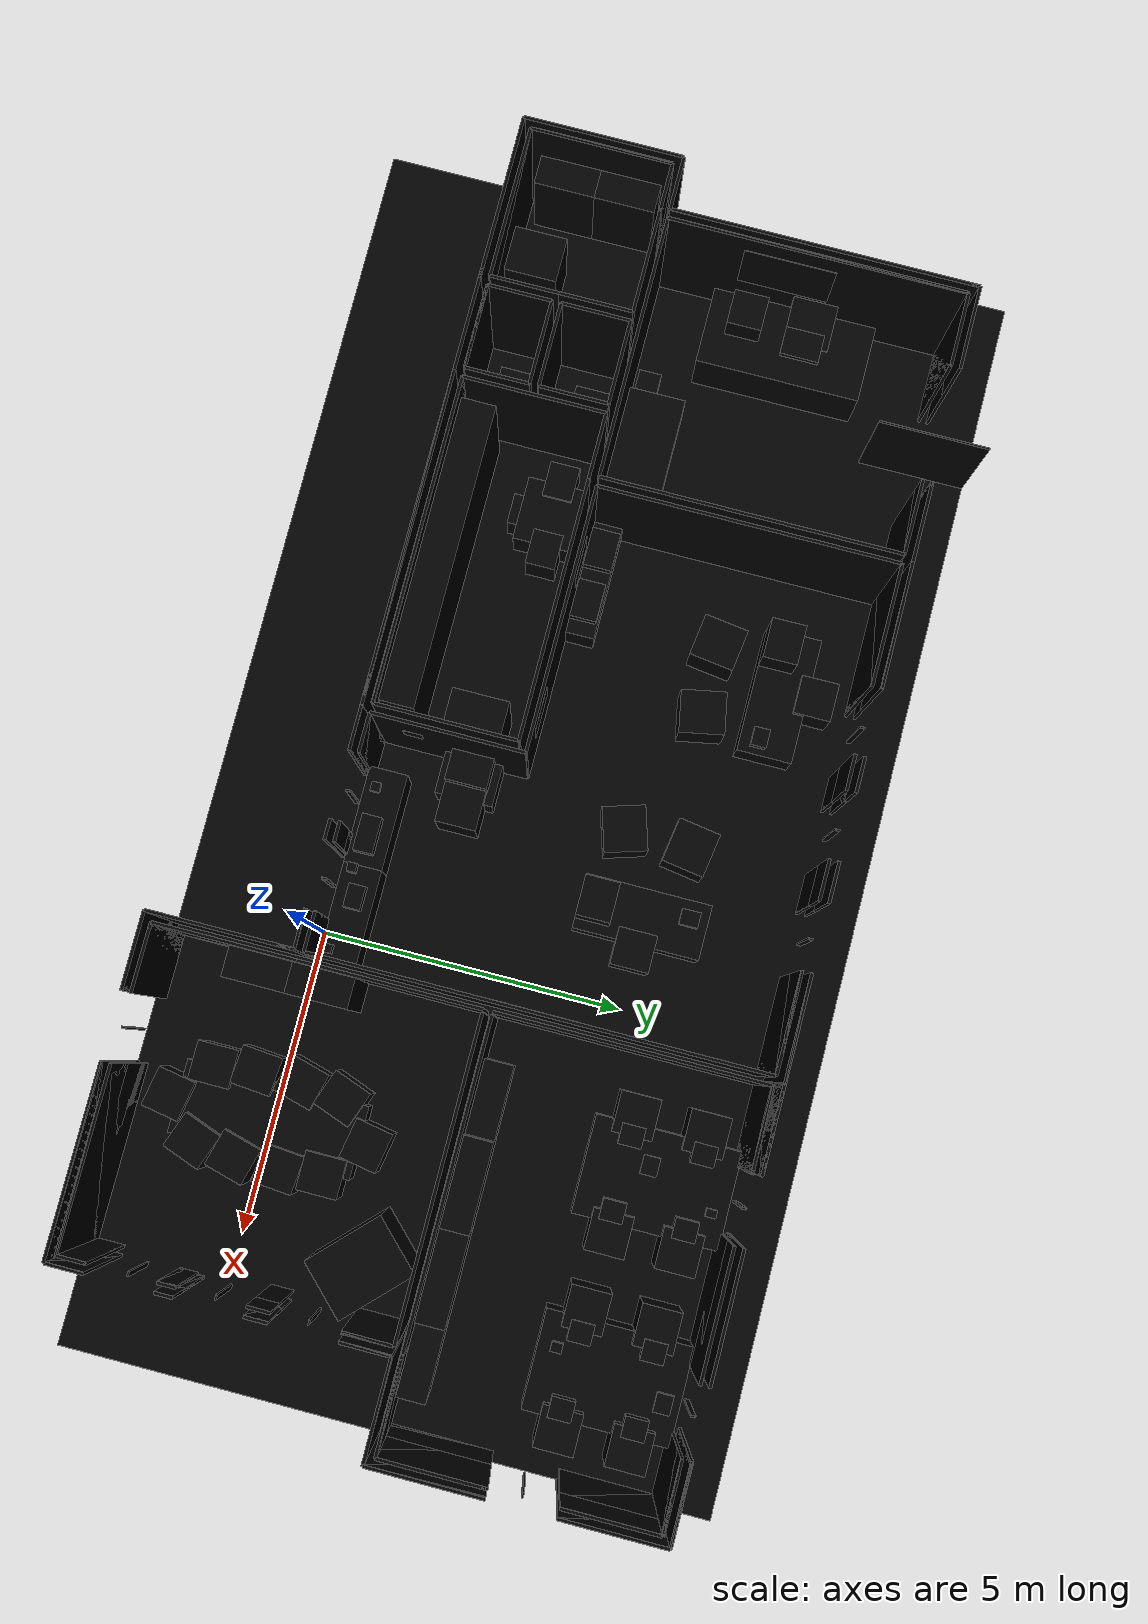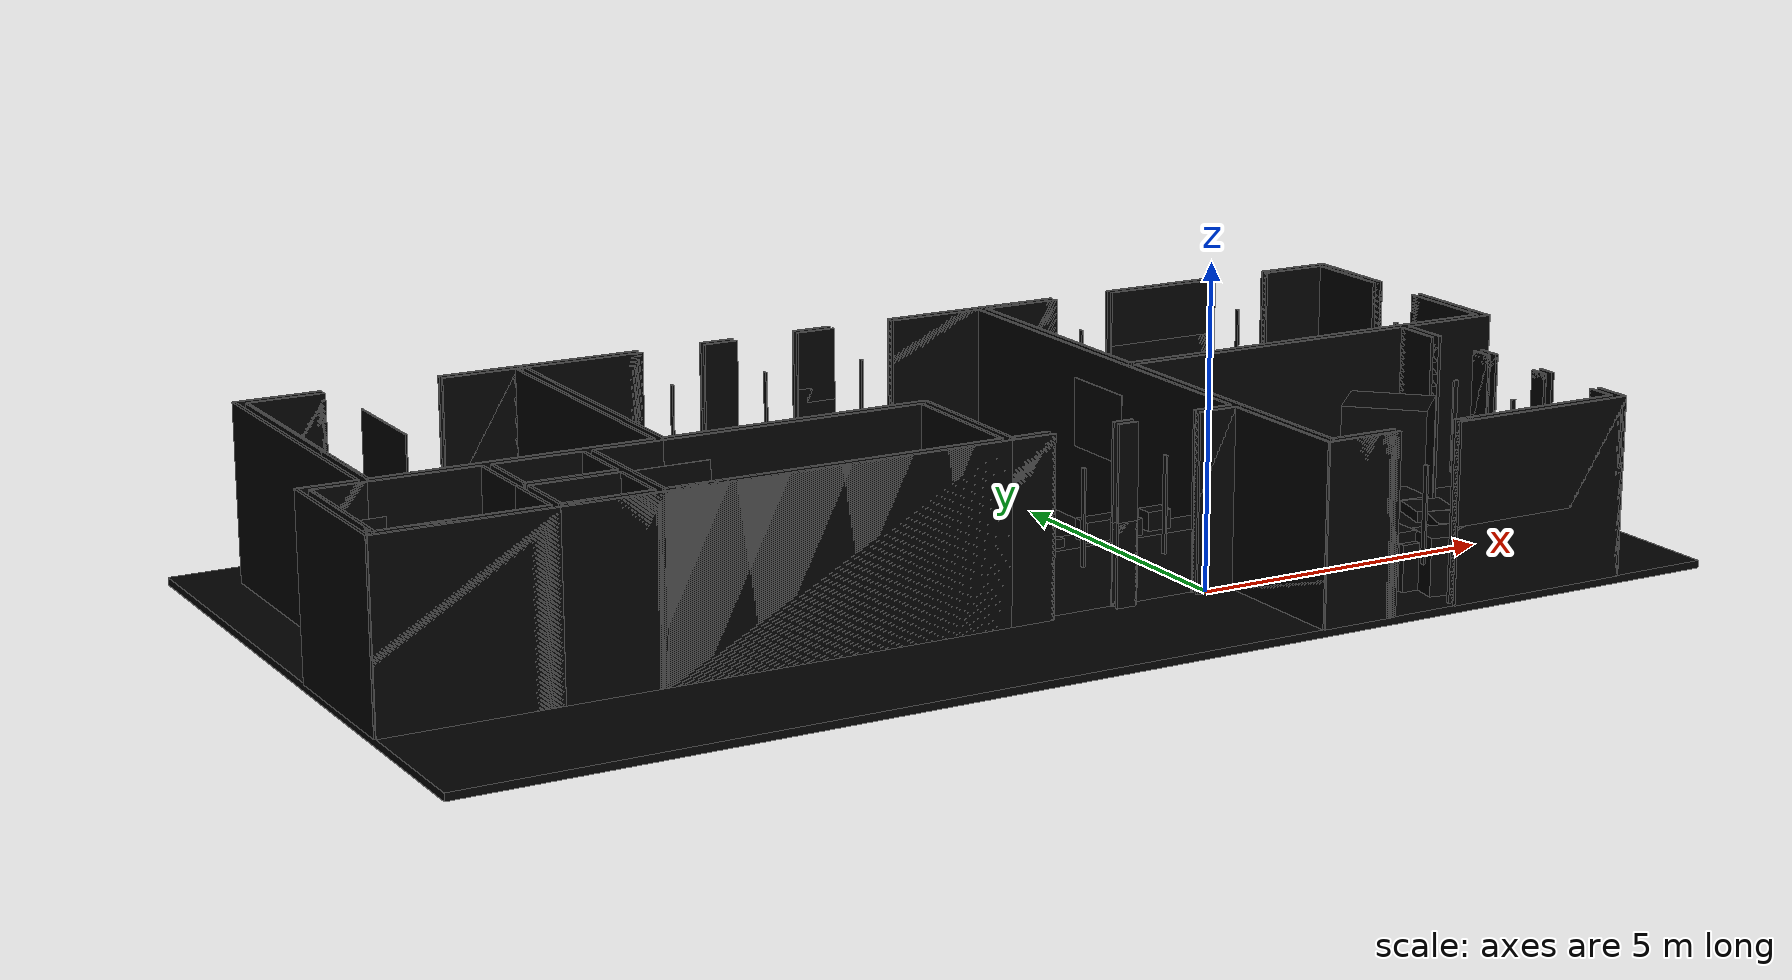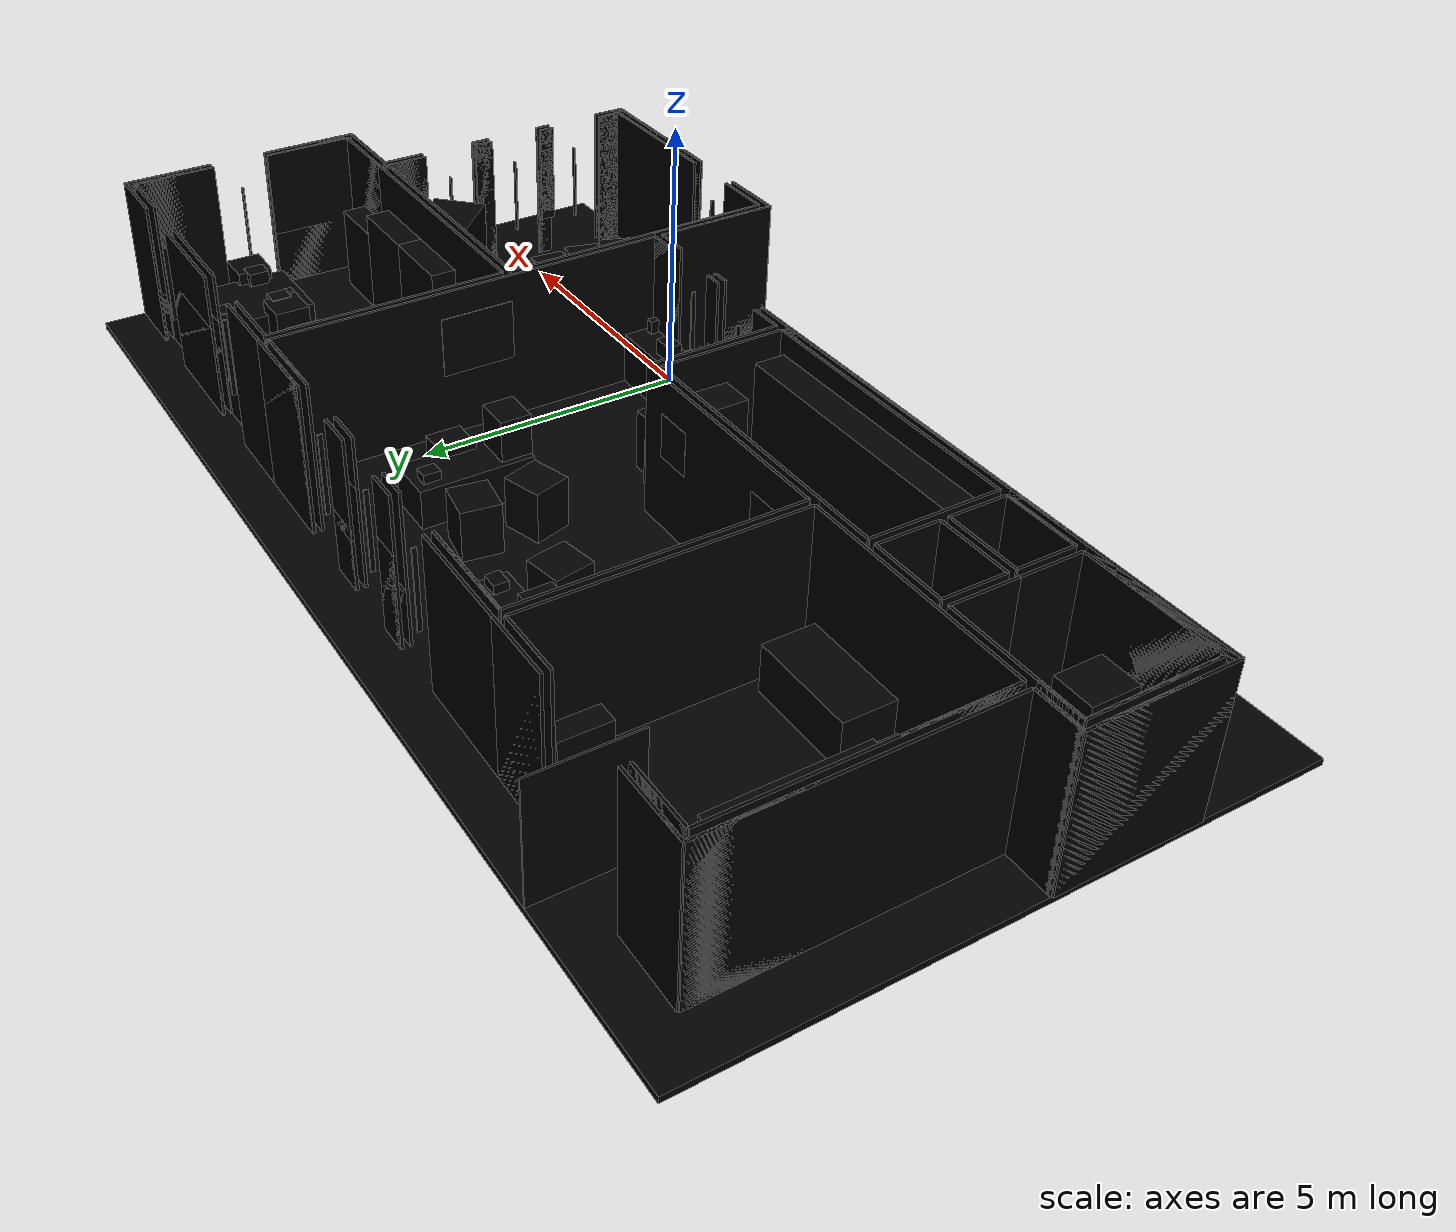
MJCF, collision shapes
<mujoco model="Habitat scene 108294417_176709879">
  <compiler angle="radian" balanceinertia="true" />
  <option gravity="0 0 -9.81" />
  <visual>
    <headlight ambient="0.38 0.38 0.38" diffuse="0.68 0.68 0.68" specular="0.06 0.06 0.06" />
    <rgba haze="0.78 0.83 0.86 1" />
  </visual>
  <asset>
    <material name="habitat_stage_part_000_material" rgba="1 1 1 1" specular="0.1675" shininess="0" reflectance="0" />
    <material name="habitat_stage_part_001_material" rgba="0 0 0 1" specular="0.1675" shininess="0" reflectance="0" />
    <material name="habitat_stage_part_002_material" rgba="1 1 1 1" specular="0.1675" shininess="0" reflectance="0" />
    <texture name="habitat_stage_part_003_texture" type="2d" file="/home/xyf/submodules/stretch_mujoco/stretch_mujoco/models/assets/office_scenes/_hssd_cache/108294417_176709879/converted/stage/textures/image_009.png" />
    <material name="habitat_stage_part_003_material" rgba="1 1 1 1" specular="0.1675" shininess="0" reflectance="0" texture="habitat_stage_part_003_texture" />
    <texture name="habitat_stage_part_004_texture" type="2d" file="/home/xyf/submodules/stretch_mujoco/stretch_mujoco/models/assets/office_scenes/_hssd_cache/108294417_176709879/converted/stage/textures/image_008.png" />
    <material name="habitat_stage_part_004_material" rgba="1 1 1 1" specular="0.1675" shininess="0" reflectance="0" texture="habitat_stage_part_004_texture" />
    <texture name="habitat_stage_part_005_texture" type="2d" file="/home/xyf/submodules/stretch_mujoco/stretch_mujoco/models/assets/office_scenes/_hssd_cache/108294417_176709879/converted/stage/textures/image_003.png" />
    <material name="habitat_stage_part_005_material" rgba="1 1 1 1" specular="0.1675" shininess="0" reflectance="0" texture="habitat_stage_part_005_texture" />
    <texture name="habitat_stage_part_006_texture" type="2d" file="/home/xyf/submodules/stretch_mujoco/stretch_mujoco/models/assets/office_scenes/_hssd_cache/108294417_176709879/converted/stage/textures/image_001.png" />
    <material name="habitat_stage_part_006_material" rgba="1 1 1 1" specular="0.1675" shininess="0" reflectance="0" texture="habitat_stage_part_006_texture" />
    <texture name="habitat_stage_part_007_texture" type="2d" file="/home/xyf/submodules/stretch_mujoco/stretch_mujoco/models/assets/office_scenes/_hssd_cache/108294417_176709879/converted/stage/textures/image_004.png" />
    <material name="habitat_stage_part_007_material" rgba="1 1 1 1" specular="0.1675" shininess="0" reflectance="0" texture="habitat_stage_part_007_texture" />
    <texture name="habitat_stage_part_008_texture" type="2d" file="/home/xyf/submodules/stretch_mujoco/stretch_mujoco/models/assets/office_scenes/_hssd_cache/108294417_176709879/converted/stage/textures/image_005.png" />
    <material name="habitat_stage_part_008_material" rgba="1 1 1 1" specular="0.1675" shininess="0" reflectance="0" texture="habitat_stage_part_008_texture" />
    <texture name="habitat_stage_part_009_texture" type="2d" file="/home/xyf/submodules/stretch_mujoco/stretch_mujoco/models/assets/office_scenes/_hssd_cache/108294417_176709879/converted/stage/textures/image_002.png" />
    <material name="habitat_stage_part_009_material" rgba="1 1 1 1" specular="0.1675" shininess="0" reflectance="0" texture="habitat_stage_part_009_texture" />
    <texture name="habitat_stage_part_010_texture" type="2d" file="/home/xyf/submodules/stretch_mujoco/stretch_mujoco/models/assets/office_scenes/_hssd_cache/108294417_176709879/converted/stage/textures/image_000.png" />
    <material name="habitat_stage_part_010_material" rgba="1 1 1 1" specular="0.1675" shininess="0" reflectance="0" texture="habitat_stage_part_010_texture" />
    <texture name="habitat_stage_part_011_texture" type="2d" file="/home/xyf/submodules/stretch_mujoco/stretch_mujoco/models/assets/office_scenes/_hssd_cache/108294417_176709879/converted/stage/textures/image_007.png" />
    <material name="habitat_stage_part_011_material" rgba="1 1 1 1" specular="0.1675" shininess="0" reflectance="0" texture="habitat_stage_part_011_texture" />
    <texture name="habitat_stage_part_012_texture" type="2d" file="/home/xyf/submodules/stretch_mujoco/stretch_mujoco/models/assets/office_scenes/_hssd_cache/108294417_176709879/converted/stage/textures/image_006.png" />
    <material name="habitat_stage_part_012_material" rgba="1 1 1 1" specular="0.1675" shininess="0" reflectance="0" texture="habitat_stage_part_012_texture" />
    <material name="habitat_stage_part_013_material" rgba="0.87451 0.819608 0.780392 1" specular="0.1675" shininess="0" reflectance="0" />
    <material name="habitat_stage_part_014_material" rgba="0.858824 0.772549 0.713726 1" specular="0.1675" shininess="0" reflectance="0" />
    <material name="habitat_stage_part_015_material" rgba="0.623529 0.556863 0.509804 1" specular="0.1675" shininess="0" reflectance="0" />
    <material name="habitat_stage_part_016_material" rgba="0.188235 0.356863 0.411765 1" specular="0.1675" shininess="0" reflectance="0" />
    <material name="habitat_stage_part_017_material" rgba="0 0 0 1" specular="0.1675" shininess="0" reflectance="0" />
    <texture name="habitat_stage_part_018_texture" type="2d" file="/home/xyf/submodules/stretch_mujoco/stretch_mujoco/models/assets/office_scenes/_hssd_cache/108294417_176709879/converted/stage/textures/image_001.png" />
    <material name="habitat_stage_part_018_material" rgba="1 1 1 1" specular="0.1675" shininess="0" reflectance="0" texture="habitat_stage_part_018_texture" />
    <texture name="habitat_stage_part_019_texture" type="2d" file="/home/xyf/submodules/stretch_mujoco/stretch_mujoco/models/assets/office_scenes/_hssd_cache/108294417_176709879/converted/stage/textures/image_005.png" />
    <material name="habitat_stage_part_019_material" rgba="1 1 1 1" specular="0.1675" shininess="0" reflectance="0" texture="habitat_stage_part_019_texture" />
    <material name="habitat_stage_part_020_material" rgba="0 0 0 1" specular="0.1675" shininess="0" reflectance="0" />
    <material name="habitat_stage_part_021_material" rgba="1 1 1 1" specular="0.1675" shininess="0" reflectance="0" />
    <texture name="habitat_stage_part_022_texture" type="2d" file="/home/xyf/submodules/stretch_mujoco/stretch_mujoco/models/assets/office_scenes/_hssd_cache/108294417_176709879/converted/stage/textures/image_001.png" />
    <material name="habitat_stage_part_022_material" rgba="1 1 1 1" specular="0.1675" shininess="0" reflectance="0" texture="habitat_stage_part_022_texture" />
    <material name="habitat_stage_part_023_material" rgba="0 0 0 1" specular="0.1675" shininess="0" reflectance="0" />
    <texture name="habitat_stage_part_024_texture" type="2d" file="/home/xyf/submodules/stretch_mujoco/stretch_mujoco/models/assets/office_scenes/_hssd_cache/108294417_176709879/converted/stage/textures/image_001.png" />
    <material name="habitat_stage_part_024_material" rgba="1 1 1 1" specular="0.1675" shininess="0" reflectance="0" texture="habitat_stage_part_024_texture" />
    <material name="habitat_stage_part_025_material" rgba="0.188235 0.356863 0.411765 1" specular="0.1675" shininess="0" reflectance="0" />
    <material name="habitat_stage_part_026_material" rgba="0 0 0 1" specular="0.1675" shininess="0" reflectance="0" />
    <texture name="habitat_stage_part_027_texture" type="2d" file="/home/xyf/submodules/stretch_mujoco/stretch_mujoco/models/assets/office_scenes/_hssd_cache/108294417_176709879/converted/stage/textures/image_001.png" />
    <material name="habitat_stage_part_027_material" rgba="1 1 1 1" specular="0.1675" shininess="0" reflectance="0" texture="habitat_stage_part_027_texture" />
    <material name="habitat_stage_part_028_material" rgba="0.188235 0.356863 0.411765 1" specular="0.1675" shininess="0" reflectance="0" />
    <material name="habitat_stage_part_029_material" rgba="0 0 0 1" specular="0.1675" shininess="0" reflectance="0" />
    <texture name="habitat_stage_part_030_texture" type="2d" file="/home/xyf/submodules/stretch_mujoco/stretch_mujoco/models/assets/office_scenes/_hssd_cache/108294417_176709879/converted/stage/textures/image_001.png" />
    <material name="habitat_stage_part_030_material" rgba="1 1 1 1" specular="0.1675" shininess="0" reflectance="0" texture="habitat_stage_part_030_texture" />
    <material name="habitat_stage_part_031_material" rgba="0.87451 0.819608 0.780392 1" specular="0.1675" shininess="0" reflectance="0" />
    <material name="habitat_stage_part_032_material" rgba="0 0 0 1" specular="0.1675" shininess="0" reflectance="0" />
    <texture name="habitat_stage_part_033_texture" type="2d" file="/home/xyf/submodules/stretch_mujoco/stretch_mujoco/models/assets/office_scenes/_hssd_cache/108294417_176709879/converted/stage/textures/image_001.png" />
    <material name="habitat_stage_part_033_material" rgba="1 1 1 1" specular="0.1675" shininess="0" reflectance="0" texture="habitat_stage_part_033_texture" />
    <material name="habitat_stage_part_034_material" rgba="0.623529 0.556863 0.509804 1" specular="0.1675" shininess="0" reflectance="0" />
    <material name="habitat_stage_part_035_material" rgba="0 0 0 1" specular="0.1675" shininess="0" reflectance="0" />
    <texture name="habitat_stage_part_036_texture" type="2d" file="/home/xyf/submodules/stretch_mujoco/stretch_mujoco/models/assets/office_scenes/_hssd_cache/108294417_176709879/converted/stage/textures/image_001.png" />
    <material name="habitat_stage_part_036_material" rgba="1 1 1 1" specular="0.1675" shininess="0" reflectance="0" texture="habitat_stage_part_036_texture" />
    <material name="habitat_stage_part_037_material" rgba="0.623529 0.556863 0.509804 1" specular="0.1675" shininess="0" reflectance="0" />
    <material name="habitat_stage_part_038_material" rgba="0 0 0 1" specular="0.1675" shininess="0" reflectance="0" />
    <texture name="habitat_stage_part_039_texture" type="2d" file="/home/xyf/submodules/stretch_mujoco/stretch_mujoco/models/assets/office_scenes/_hssd_cache/108294417_176709879/converted/stage/textures/image_001.png" />
    <material name="habitat_stage_part_039_material" rgba="1 1 1 1" specular="0.1675" shininess="0" reflectance="0" texture="habitat_stage_part_039_texture" />
    <material name="habitat_stage_part_040_material" rgba="0.87451 0.819608 0.780392 1" specular="0.1675" shininess="0" reflectance="0" />
    <material name="habitat_stage_part_041_material" rgba="0 0 0 1" specular="0.1675" shininess="0" reflectance="0" />
    <material name="habitat_stage_part_042_material" rgba="1 1 1 1" specular="0.1675" shininess="0" reflectance="0" />
    <texture name="habitat_stage_part_043_texture" type="2d" file="/home/xyf/submodules/stretch_mujoco/stretch_mujoco/models/assets/office_scenes/_hssd_cache/108294417_176709879/converted/stage/textures/image_001.png" />
    <material name="habitat_stage_part_043_material" rgba="1 1 1 1" specular="0.1675" shininess="0" reflectance="0" texture="habitat_stage_part_043_texture" />
    <material name="habitat_stage_part_044_material" rgba="0.858824 0.772549 0.713726 1" specular="0.1675" shininess="0" reflectance="0" />
    <material name="habitat_stage_part_045_material" rgba="0 0 0 1" specular="0.1675" shininess="0" reflectance="0" />
    <texture name="habitat_stage_part_046_texture" type="2d" file="/home/xyf/submodules/stretch_mujoco/stretch_mujoco/models/assets/office_scenes/_hssd_cache/108294417_176709879/converted/stage/textures/image_001.png" />
    <material name="habitat_stage_part_046_material" rgba="1 1 1 1" specular="0.1675" shininess="0" reflectance="0" texture="habitat_stage_part_046_texture" />
    <texture name="habitat_stage_part_047_texture" type="2d" file="/home/xyf/submodules/stretch_mujoco/stretch_mujoco/models/assets/office_scenes/_hssd_cache/108294417_176709879/converted/stage/textures/image_004.png" />
    <material name="habitat_stage_part_047_material" rgba="1 1 1 1" specular="0.1675" shininess="0" reflectance="0" texture="habitat_stage_part_047_texture" />
    <material name="habitat_stage_part_048_material" rgba="0 0 0 1" specular="0.1675" shininess="0" reflectance="0" />
    <texture name="habitat_stage_part_049_texture" type="2d" file="/home/xyf/submodules/stretch_mujoco/stretch_mujoco/models/assets/office_scenes/_hssd_cache/108294417_176709879/converted/stage/textures/image_003.png" />
    <material name="habitat_stage_part_049_material" rgba="1 1 1 1" specular="0.1675" shininess="0" reflectance="0" texture="habitat_stage_part_049_texture" />
    <texture name="habitat_stage_part_050_texture" type="2d" file="/home/xyf/submodules/stretch_mujoco/stretch_mujoco/models/assets/office_scenes/_hssd_cache/108294417_176709879/converted/stage/textures/image_001.png" />
    <material name="habitat_stage_part_050_material" rgba="1 1 1 1" specular="0.1675" shininess="0" reflectance="0" texture="habitat_stage_part_050_texture" />
    <material name="habitat_stage_part_051_material" rgba="0 0 0 1" specular="0.1675" shininess="0" reflectance="0" />
    <texture name="habitat_stage_part_052_texture" type="2d" file="/home/xyf/submodules/stretch_mujoco/stretch_mujoco/models/assets/office_scenes/_hssd_cache/108294417_176709879/converted/stage/textures/image_001.png" />
    <material name="habitat_stage_part_052_material" rgba="1 1 1 1" specular="0.1675" shininess="0" reflectance="0" texture="habitat_stage_part_052_texture" />
    <texture name="habitat_stage_part_053_texture" type="2d" file="/home/xyf/submodules/stretch_mujoco/stretch_mujoco/models/assets/office_scenes/_hssd_cache/108294417_176709879/converted/stage/textures/image_000.png" />
    <material name="habitat_stage_part_053_material" rgba="1 1 1 1" specular="0.1675" shininess="0" reflectance="0" texture="habitat_stage_part_053_texture" />
    <material name="habitat_stage_part_054_material" rgba="0 0 0 1" specular="0.1675" shininess="0" reflectance="0" />
    <texture name="habitat_stage_part_055_texture" type="2d" file="/home/xyf/submodules/stretch_mujoco/stretch_mujoco/models/assets/office_scenes/_hssd_cache/108294417_176709879/converted/stage/textures/image_001.png" />
    <material name="habitat_stage_part_055_material" rgba="1 1 1 1" specular="0.1675" shininess="0" reflectance="0" texture="habitat_stage_part_055_texture" />
    <texture name="habitat_stage_part_056_texture" type="2d" file="/home/xyf/submodules/stretch_mujoco/stretch_mujoco/models/assets/office_scenes/_hssd_cache/108294417_176709879/converted/stage/textures/image_002.png" />
    <material name="habitat_stage_part_056_material" rgba="1 1 1 1" specular="0.1675" shininess="0" reflectance="0" texture="habitat_stage_part_056_texture" />
    <material name="habitat_stage_part_057_material" rgba="0 0 0 1" specular="0.1675" shininess="0" reflectance="0" />
    <texture name="habitat_stage_part_058_texture" type="2d" file="/home/xyf/submodules/stretch_mujoco/stretch_mujoco/models/assets/office_scenes/_hssd_cache/108294417_176709879/converted/stage/textures/image_001.png" />
    <material name="habitat_stage_part_058_material" rgba="1 1 1 1" specular="0.1675" shininess="0" reflectance="0" texture="habitat_stage_part_058_texture" />
    <texture name="habitat_stage_part_059_texture" type="2d" file="/home/xyf/submodules/stretch_mujoco/stretch_mujoco/models/assets/office_scenes/_hssd_cache/108294417_176709879/converted/stage/textures/image_002.png" />
    <material name="habitat_stage_part_059_material" rgba="1 1 1 1" specular="0.1675" shininess="0" reflectance="0" texture="habitat_stage_part_059_texture" />
    <material name="habitat_stage_part_060_material" rgba="0 0 0 1" specular="0.1675" shininess="0" reflectance="0" />
    <texture name="habitat_stage_part_061_texture" type="2d" file="/home/xyf/submodules/stretch_mujoco/stretch_mujoco/models/assets/office_scenes/_hssd_cache/108294417_176709879/converted/stage/textures/image_001.png" />
    <material name="habitat_stage_part_061_material" rgba="1 1 1 1" specular="0.1675" shininess="0" reflectance="0" texture="habitat_stage_part_061_texture" />
    <texture name="habitat_stage_part_062_texture" type="2d" file="/home/xyf/submodules/stretch_mujoco/stretch_mujoco/models/assets/office_scenes/_hssd_cache/108294417_176709879/converted/stage/textures/image_000.png" />
    <material name="habitat_stage_part_062_material" rgba="1 1 1 1" specular="0.1675" shininess="0" reflectance="0" texture="habitat_stage_part_062_texture" />
    <mesh name="habitat_stage_mesh_000" file="/home/xyf/submodules/stretch_mujoco/stretch_mujoco/models/assets/office_scenes/_hssd_cache/108294417_176709879/converted/stage/meshes/part_000_FP_DOORFRAME_094.obj" />
    <mesh name="habitat_stage_mesh_001" file="/home/xyf/submodules/stretch_mujoco/stretch_mujoco/models/assets/office_scenes/_hssd_cache/108294417_176709879/converted/stage/meshes/part_001_edge_color248248248255_070.obj" />
    <mesh name="habitat_stage_mesh_002" file="/home/xyf/submodules/stretch_mujoco/stretch_mujoco/models/assets/office_scenes/_hssd_cache/108294417_176709879/converted/stage/meshes/part_002_FP_DOORFRAME_094.obj" />
    <mesh name="habitat_stage_mesh_003" file="/home/xyf/submodules/stretch_mujoco/stretch_mujoco/models/assets/office_scenes/_hssd_cache/108294417_176709879/converted/stage/meshes/part_003_rs-632.obj" />
    <mesh name="habitat_stage_mesh_004" file="/home/xyf/submodules/stretch_mujoco/stretch_mujoco/models/assets/office_scenes/_hssd_cache/108294417_176709879/converted/stage/meshes/part_004_rs-4111.obj" />
    <mesh name="habitat_stage_mesh_005" file="/home/xyf/submodules/stretch_mujoco/stretch_mujoco/models/assets/office_scenes/_hssd_cache/108294417_176709879/converted/stage/meshes/part_005_rs-3925_002.obj" />
    <mesh name="habitat_stage_mesh_006" file="/home/xyf/submodules/stretch_mujoco/stretch_mujoco/models/assets/office_scenes/_hssd_cache/108294417_176709879/converted/stage/meshes/part_006_rs-3827_001.obj" />
    <mesh name="habitat_stage_mesh_007" file="/home/xyf/submodules/stretch_mujoco/stretch_mujoco/models/assets/office_scenes/_hssd_cache/108294417_176709879/converted/stage/meshes/part_007_rs-3785_007.obj" />
    <mesh name="habitat_stage_mesh_008" file="/home/xyf/submodules/stretch_mujoco/stretch_mujoco/models/assets/office_scenes/_hssd_cache/108294417_176709879/converted/stage/meshes/part_008_rs-3733_012.obj" />
    <mesh name="habitat_stage_mesh_009" file="/home/xyf/submodules/stretch_mujoco/stretch_mujoco/models/assets/office_scenes/_hssd_cache/108294417_176709879/converted/stage/meshes/part_009_rs-13649_004.obj" />
    <mesh name="habitat_stage_mesh_010" file="/home/xyf/submodules/stretch_mujoco/stretch_mujoco/models/assets/office_scenes/_hssd_cache/108294417_176709879/converted/stage/meshes/part_010_rs-13519_006.obj" />
    <mesh name="habitat_stage_mesh_011" file="/home/xyf/submodules/stretch_mujoco/stretch_mujoco/models/assets/office_scenes/_hssd_cache/108294417_176709879/converted/stage/meshes/part_011_rs-13507_006.obj" />
    <mesh name="habitat_stage_mesh_012" file="/home/xyf/submodules/stretch_mujoco/stretch_mujoco/models/assets/office_scenes/_hssd_cache/108294417_176709879/converted/stage/meshes/part_012_rs-100_005.obj" />
    <mesh name="habitat_stage_mesh_013" file="/home/xyf/submodules/stretch_mujoco/stretch_mujoco/models/assets/office_scenes/_hssd_cache/108294417_176709879/converted/stage/meshes/part_013_DFD1C7_004.obj" />
    <mesh name="habitat_stage_mesh_014" file="/home/xyf/submodules/stretch_mujoco/stretch_mujoco/models/assets/office_scenes/_hssd_cache/108294417_176709879/converted/stage/meshes/part_014_DBC5B6_001.obj" />
    <mesh name="habitat_stage_mesh_015" file="/home/xyf/submodules/stretch_mujoco/stretch_mujoco/models/assets/office_scenes/_hssd_cache/108294417_176709879/converted/stage/meshes/part_015_9F8E82_003.obj" />
    <mesh name="habitat_stage_mesh_016" file="/home/xyf/submodules/stretch_mujoco/stretch_mujoco/models/assets/office_scenes/_hssd_cache/108294417_176709879/converted/stage/meshes/part_016_305B69_001.obj" />
    <mesh name="habitat_stage_mesh_017" file="/home/xyf/submodules/stretch_mujoco/stretch_mujoco/models/assets/office_scenes/_hssd_cache/108294417_176709879/converted/stage/meshes/part_017_edge_color248248248255_070.obj" />
    <mesh name="habitat_stage_mesh_018" file="/home/xyf/submodules/stretch_mujoco/stretch_mujoco/models/assets/office_scenes/_hssd_cache/108294417_176709879/converted/stage/meshes/part_018_rs-3827_001.obj" />
    <mesh name="habitat_stage_mesh_019" file="/home/xyf/submodules/stretch_mujoco/stretch_mujoco/models/assets/office_scenes/_hssd_cache/108294417_176709879/converted/stage/meshes/part_019_rs-3733_012.obj" />
    <mesh name="habitat_stage_mesh_020" file="/home/xyf/submodules/stretch_mujoco/stretch_mujoco/models/assets/office_scenes/_hssd_cache/108294417_176709879/converted/stage/meshes/part_020_edge_color248248248255_070.obj" />
    <mesh name="habitat_stage_mesh_021" file="/home/xyf/submodules/stretch_mujoco/stretch_mujoco/models/assets/office_scenes/_hssd_cache/108294417_176709879/converted/stage/meshes/part_021_FP_DOORFRAME_094.obj" />
    <mesh name="habitat_stage_mesh_022" file="/home/xyf/submodules/stretch_mujoco/stretch_mujoco/models/assets/office_scenes/_hssd_cache/108294417_176709879/converted/stage/meshes/part_022_rs-3827_001.obj" />
    <mesh name="habitat_stage_mesh_023" file="/home/xyf/submodules/stretch_mujoco/stretch_mujoco/models/assets/office_scenes/_hssd_cache/108294417_176709879/converted/stage/meshes/part_023_edge_color248248248255_070.obj" />
    <mesh name="habitat_stage_mesh_024" file="/home/xyf/submodules/stretch_mujoco/stretch_mujoco/models/assets/office_scenes/_hssd_cache/108294417_176709879/converted/stage/meshes/part_024_rs-3827_001.obj" />
    <mesh name="habitat_stage_mesh_025" file="/home/xyf/submodules/stretch_mujoco/stretch_mujoco/models/assets/office_scenes/_hssd_cache/108294417_176709879/converted/stage/meshes/part_025_305B69_001.obj" />
    <mesh name="habitat_stage_mesh_026" file="/home/xyf/submodules/stretch_mujoco/stretch_mujoco/models/assets/office_scenes/_hssd_cache/108294417_176709879/converted/stage/meshes/part_026_edge_color248248248255_070.obj" />
    <mesh name="habitat_stage_mesh_027" file="/home/xyf/submodules/stretch_mujoco/stretch_mujoco/models/assets/office_scenes/_hssd_cache/108294417_176709879/converted/stage/meshes/part_027_rs-3827_001.obj" />
    <mesh name="habitat_stage_mesh_028" file="/home/xyf/submodules/stretch_mujoco/stretch_mujoco/models/assets/office_scenes/_hssd_cache/108294417_176709879/converted/stage/meshes/part_028_305B69_001.obj" />
    <mesh name="habitat_stage_mesh_029" file="/home/xyf/submodules/stretch_mujoco/stretch_mujoco/models/assets/office_scenes/_hssd_cache/108294417_176709879/converted/stage/meshes/part_029_edge_color248248248255_070.obj" />
    <mesh name="habitat_stage_mesh_030" file="/home/xyf/submodules/stretch_mujoco/stretch_mujoco/models/assets/office_scenes/_hssd_cache/108294417_176709879/converted/stage/meshes/part_030_rs-3827_001.obj" />
    <mesh name="habitat_stage_mesh_031" file="/home/xyf/submodules/stretch_mujoco/stretch_mujoco/models/assets/office_scenes/_hssd_cache/108294417_176709879/converted/stage/meshes/part_031_DFD1C7_004.obj" />
    <mesh name="habitat_stage_mesh_032" file="/home/xyf/submodules/stretch_mujoco/stretch_mujoco/models/assets/office_scenes/_hssd_cache/108294417_176709879/converted/stage/meshes/part_032_edge_color248248248255_070.obj" />
    <mesh name="habitat_stage_mesh_033" file="/home/xyf/submodules/stretch_mujoco/stretch_mujoco/models/assets/office_scenes/_hssd_cache/108294417_176709879/converted/stage/meshes/part_033_rs-3827_001.obj" />
    <mesh name="habitat_stage_mesh_034" file="/home/xyf/submodules/stretch_mujoco/stretch_mujoco/models/assets/office_scenes/_hssd_cache/108294417_176709879/converted/stage/meshes/part_034_9F8E82_003.obj" />
    <mesh name="habitat_stage_mesh_035" file="/home/xyf/submodules/stretch_mujoco/stretch_mujoco/models/assets/office_scenes/_hssd_cache/108294417_176709879/converted/stage/meshes/part_035_edge_color248248248255_070.obj" />
    <mesh name="habitat_stage_mesh_036" file="/home/xyf/submodules/stretch_mujoco/stretch_mujoco/models/assets/office_scenes/_hssd_cache/108294417_176709879/converted/stage/meshes/part_036_rs-3827_001.obj" />
    <mesh name="habitat_stage_mesh_037" file="/home/xyf/submodules/stretch_mujoco/stretch_mujoco/models/assets/office_scenes/_hssd_cache/108294417_176709879/converted/stage/meshes/part_037_9F8E82_003.obj" />
    <mesh name="habitat_stage_mesh_038" file="/home/xyf/submodules/stretch_mujoco/stretch_mujoco/models/assets/office_scenes/_hssd_cache/108294417_176709879/converted/stage/meshes/part_038_edge_color248248248255_070.obj" />
    <mesh name="habitat_stage_mesh_039" file="/home/xyf/submodules/stretch_mujoco/stretch_mujoco/models/assets/office_scenes/_hssd_cache/108294417_176709879/converted/stage/meshes/part_039_rs-3827_001.obj" />
    <mesh name="habitat_stage_mesh_040" file="/home/xyf/submodules/stretch_mujoco/stretch_mujoco/models/assets/office_scenes/_hssd_cache/108294417_176709879/converted/stage/meshes/part_040_DFD1C7_004.obj" />
    <mesh name="habitat_stage_mesh_041" file="/home/xyf/submodules/stretch_mujoco/stretch_mujoco/models/assets/office_scenes/_hssd_cache/108294417_176709879/converted/stage/meshes/part_041_edge_color248248248255_070.obj" />
    <mesh name="habitat_stage_mesh_042" file="/home/xyf/submodules/stretch_mujoco/stretch_mujoco/models/assets/office_scenes/_hssd_cache/108294417_176709879/converted/stage/meshes/part_042_FP_DOORFRAME_094.obj" />
    <mesh name="habitat_stage_mesh_043" file="/home/xyf/submodules/stretch_mujoco/stretch_mujoco/models/assets/office_scenes/_hssd_cache/108294417_176709879/converted/stage/meshes/part_043_rs-3827_001.obj" />
    <mesh name="habitat_stage_mesh_044" file="/home/xyf/submodules/stretch_mujoco/stretch_mujoco/models/assets/office_scenes/_hssd_cache/108294417_176709879/converted/stage/meshes/part_044_DBC5B6_001.obj" />
    <mesh name="habitat_stage_mesh_045" file="/home/xyf/submodules/stretch_mujoco/stretch_mujoco/models/assets/office_scenes/_hssd_cache/108294417_176709879/converted/stage/meshes/part_045_edge_color248248248255_070.obj" />
    <mesh name="habitat_stage_mesh_046" file="/home/xyf/submodules/stretch_mujoco/stretch_mujoco/models/assets/office_scenes/_hssd_cache/108294417_176709879/converted/stage/meshes/part_046_rs-3827_001.obj" />
    <mesh name="habitat_stage_mesh_047" file="/home/xyf/submodules/stretch_mujoco/stretch_mujoco/models/assets/office_scenes/_hssd_cache/108294417_176709879/converted/stage/meshes/part_047_rs-3785_007.obj" />
    <mesh name="habitat_stage_mesh_048" file="/home/xyf/submodules/stretch_mujoco/stretch_mujoco/models/assets/office_scenes/_hssd_cache/108294417_176709879/converted/stage/meshes/part_048_edge_color248248248255_070.obj" />
    <mesh name="habitat_stage_mesh_049" file="/home/xyf/submodules/stretch_mujoco/stretch_mujoco/models/assets/office_scenes/_hssd_cache/108294417_176709879/converted/stage/meshes/part_049_rs-3925_002.obj" />
    <mesh name="habitat_stage_mesh_050" file="/home/xyf/submodules/stretch_mujoco/stretch_mujoco/models/assets/office_scenes/_hssd_cache/108294417_176709879/converted/stage/meshes/part_050_rs-3827_001.obj" />
    <mesh name="habitat_stage_mesh_051" file="/home/xyf/submodules/stretch_mujoco/stretch_mujoco/models/assets/office_scenes/_hssd_cache/108294417_176709879/converted/stage/meshes/part_051_edge_color248248248255_070.obj" />
    <mesh name="habitat_stage_mesh_052" file="/home/xyf/submodules/stretch_mujoco/stretch_mujoco/models/assets/office_scenes/_hssd_cache/108294417_176709879/converted/stage/meshes/part_052_rs-3827_001.obj" />
    <mesh name="habitat_stage_mesh_053" file="/home/xyf/submodules/stretch_mujoco/stretch_mujoco/models/assets/office_scenes/_hssd_cache/108294417_176709879/converted/stage/meshes/part_053_rs-13519_006.obj" />
    <mesh name="habitat_stage_mesh_054" file="/home/xyf/submodules/stretch_mujoco/stretch_mujoco/models/assets/office_scenes/_hssd_cache/108294417_176709879/converted/stage/meshes/part_054_edge_color248248248255_070.obj" />
    <mesh name="habitat_stage_mesh_055" file="/home/xyf/submodules/stretch_mujoco/stretch_mujoco/models/assets/office_scenes/_hssd_cache/108294417_176709879/converted/stage/meshes/part_055_rs-3827_001.obj" />
    <mesh name="habitat_stage_mesh_056" file="/home/xyf/submodules/stretch_mujoco/stretch_mujoco/models/assets/office_scenes/_hssd_cache/108294417_176709879/converted/stage/meshes/part_056_rs-13649_004.obj" />
    <mesh name="habitat_stage_mesh_057" file="/home/xyf/submodules/stretch_mujoco/stretch_mujoco/models/assets/office_scenes/_hssd_cache/108294417_176709879/converted/stage/meshes/part_057_edge_color248248248255_070.obj" />
    <mesh name="habitat_stage_mesh_058" file="/home/xyf/submodules/stretch_mujoco/stretch_mujoco/models/assets/office_scenes/_hssd_cache/108294417_176709879/converted/stage/meshes/part_058_rs-3827_001.obj" />
    <mesh name="habitat_stage_mesh_059" file="/home/xyf/submodules/stretch_mujoco/stretch_mujoco/models/assets/office_scenes/_hssd_cache/108294417_176709879/converted/stage/meshes/part_059_rs-13649_004.obj" />
    <mesh name="habitat_stage_mesh_060" file="/home/xyf/submodules/stretch_mujoco/stretch_mujoco/models/assets/office_scenes/_hssd_cache/108294417_176709879/converted/stage/meshes/part_060_edge_color248248248255_070.obj" />
    <mesh name="habitat_stage_mesh_061" file="/home/xyf/submodules/stretch_mujoco/stretch_mujoco/models/assets/office_scenes/_hssd_cache/108294417_176709879/converted/stage/meshes/part_061_rs-3827_001.obj" />
    <mesh name="habitat_stage_mesh_062" file="/home/xyf/submodules/stretch_mujoco/stretch_mujoco/models/assets/office_scenes/_hssd_cache/108294417_176709879/converted/stage/meshes/part_062_rs-13519_006.obj" />
    <material name="object_000_part_000_material" rgba="0.127225 0.127225 0.127225 1" specular="0.113382" shininess="0.949234" reflectance="0.00545891" />
    <material name="object_000_part_001_material" rgba="0.778745 0.778745 0.778745 1" specular="0.690136" shininess="1" reflectance="0.332586" />
    <texture name="object_000_part_002_texture" type="2d" file="/home/xyf/submodules/stretch_mujoco/stretch_mujoco/models/assets/office_scenes/_hssd_cache/108294417_176709879/converted/objects/0070649630e7b2262ec0427c0e2035232240fb4d/textures/image_005.png" />
    <material name="object_000_part_002_material" rgba="1 1 1 1" specular="0.163039" shininess="0.894888" reflectance="0" texture="object_000_part_002_texture" />
    <texture name="object_000_part_003_texture" type="2d" file="/home/xyf/submodules/stretch_mujoco/stretch_mujoco/models/assets/office_scenes/_hssd_cache/108294417_176709879/converted/objects/0070649630e7b2262ec0427c0e2035232240fb4d/textures/image_002.png" />
    <material name="object_000_part_003_material" rgba="1 1 1 1" specular="0.155" shininess="0.96017" reflectance="0" texture="object_000_part_003_texture" />
    <texture name="object_001_part_000_texture" type="2d" file="/home/xyf/submodules/stretch_mujoco/stretch_mujoco/models/assets/office_scenes/_hssd_cache/108294417_176709879/converted/objects/367fe59968558d7ca74557aacdc5add33d8c43d5/textures/image_001.png" />
    <material name="object_001_part_000_material" rgba="1 1 1 1" specular="0.1675" shininess="0" reflectance="0" texture="object_001_part_000_texture" />
    <texture name="object_001_part_001_texture" type="2d" file="/home/xyf/submodules/stretch_mujoco/stretch_mujoco/models/assets/office_scenes/_hssd_cache/108294417_176709879/converted/objects/367fe59968558d7ca74557aacdc5add33d8c43d5/textures/image_000.png" />
    <material name="object_001_part_001_material" rgba="1 1 1 1" specular="0.1675" shininess="0" reflectance="0" texture="object_001_part_001_texture" />
    <texture name="object_002_part_000_texture" type="2d" file="/home/xyf/submodules/stretch_mujoco/stretch_mujoco/models/assets/office_scenes/_hssd_cache/108294417_176709879/converted/objects/3060a8d709671e65252774acb499e90084bf3292/textures/image_001.png" />
    <material name="object_002_part_000_material" rgba="1 1 1 1" specular="0.1675" shininess="0" reflectance="0" texture="object_002_part_000_texture" />
    <texture name="object_002_part_001_texture" type="2d" file="/home/xyf/submodules/stretch_mujoco/stretch_mujoco/models/assets/office_scenes/_hssd_cache/108294417_176709879/converted/objects/3060a8d709671e65252774acb499e90084bf3292/textures/image_001.png" />
    <material name="object_002_part_001_material" rgba="1 1 1 1" specular="0.1675" shininess="0" reflectance="0" texture="object_002_part_001_texture" />
    <material name="object_002_part_002_material" rgba="0.0008 0.0008 0.0008 1" specular="0.1675" shininess="0" reflectance="0" />
    <material name="object_002_part_003_material" rgba="0.00412 0.00412 0.00412 1" specular="0.1675" shininess="0" reflectance="0" />
    <material name="object_003_part_000_material" rgba="1 1 1 1" specular="0.1675" shininess="0" reflectance="0" />
    <texture name="object_003_part_001_texture" type="2d" file="/home/xyf/submodules/stretch_mujoco/stretch_mujoco/models/assets/office_scenes/_hssd_cache/108294417_176709879/converted/objects/82b21351262c3874a0799e0abca0fb908de01c24/textures/image_001.png" />
    <material name="object_003_part_001_material" rgba="1 1 1 1" specular="0.23" shininess="1" reflectance="0" texture="object_003_part_001_texture" />
    <material name="object_003_part_002_material" rgba="0.0938358 0.0938358 0.0938358 1" specular="0.652013" shininess="1" reflectance="0.268554" />
    <material name="object_003_part_003_material" rgba="0.04314 0.04314 0.04314 1" specular="0.08" shininess="1" reflectance="0" />
    <material name="object_004_part_000_material" rgba="0.01794 0.01794 0.01794 1" specular="0.1675" shininess="0" reflectance="0" />
    <texture name="object_004_part_001_texture" type="2d" file="/home/xyf/submodules/stretch_mujoco/stretch_mujoco/models/assets/office_scenes/_hssd_cache/108294417_176709879/converted/objects/73cae0c00c31e895cbf8c6ac2bcc3ce718d03b21/textures/image_004.png" />
    <material name="object_004_part_001_material" rgba="1 1 1 1" specular="0.1675" shininess="0.949234" reflectance="0" texture="object_004_part_001_texture" />
    <texture name="object_004_part_002_texture" type="2d" file="/home/xyf/submodules/stretch_mujoco/stretch_mujoco/models/assets/office_scenes/_hssd_cache/108294417_176709879/converted/objects/73cae0c00c31e895cbf8c6ac2bcc3ce718d03b21/textures/image_001.png" />
    <material name="object_004_part_002_material" rgba="1 1 1 1" specular="0.1675" shininess="0" reflectance="0" texture="object_004_part_002_texture" />
    <material name="object_004_part_003_material" rgba="0.94897 0.9406 0.92399 1" specular="0.1675" shininess="0" reflectance="0" />
    <material name="object_005_part_000_material" rgba="1 1 1 1" specular="0.08" shininess="1" reflectance="0" />
    <material name="object_005_part_001_material" rgba="0.119309 0.119309 0.119309 1" specular="0.56191" shininess="1" reflectance="0.211216" />
    <texture name="object_006_part_000_texture" type="2d" file="/home/xyf/submodules/stretch_mujoco/stretch_mujoco/models/assets/office_scenes/_hssd_cache/108294417_176709879/converted/objects/7097cff803bee5431fe6fe26edb423c5499fb28b/textures/image_004.png" />
    <material name="object_006_part_000_material" rgba="1 1 1 1" specular="0.1675" shininess="0" reflectance="0" texture="object_006_part_000_texture" />
    <texture name="object_006_part_001_texture" type="2d" file="/home/xyf/submodules/stretch_mujoco/stretch_mujoco/models/assets/office_scenes/_hssd_cache/108294417_176709879/converted/objects/7097cff803bee5431fe6fe26edb423c5499fb28b/textures/image_002.png" />
    <material name="object_006_part_001_material" rgba="1 1 1 1" specular="0.1675" shininess="0" reflectance="0" texture="object_006_part_001_texture" />
    <material name="object_006_part_002_material" rgba="0.9406 0.9406 0.9406 1" specular="0.1675" shininess="0" reflectance="0" />
    <material name="object_006_part_003_material" rgba="0.00064 0.00064 0.00064 1" specular="0.1675" shininess="0" reflectance="0" />
    <texture name="object_006_part_004_texture" type="2d" file="/home/xyf/submodules/stretch_mujoco/stretch_mujoco/models/assets/office_scenes/_hssd_cache/108294417_176709879/converted/objects/7097cff803bee5431fe6fe26edb423c5499fb28b/textures/image_000.png" />
    <material name="object_006_part_004_material" rgba="1 1 1 1" specular="0.1675" shininess="0" reflectance="0" texture="object_006_part_004_texture" />
    <texture name="object_007_part_000_texture" type="2d" file="/home/xyf/submodules/stretch_mujoco/stretch_mujoco/models/assets/office_scenes/_hssd_cache/108294417_176709879/converted/objects/2502dd408e62b2aa751080d4555d9b126f5a8d22/textures/image_001.png" />
    <material name="object_007_part_000_material" rgba="1 1 1 1" specular="0.1675" shininess="0" reflectance="0" texture="object_007_part_000_texture" />
    <texture name="object_007_part_001_texture" type="2d" file="/home/xyf/submodules/stretch_mujoco/stretch_mujoco/models/assets/office_scenes/_hssd_cache/108294417_176709879/converted/objects/2502dd408e62b2aa751080d4555d9b126f5a8d22/textures/image_000.png" />
    <material name="object_007_part_001_material" rgba="1 1 1 1" specular="0.1675" shininess="0" reflectance="0" texture="object_007_part_001_texture" />
    <material name="object_007_part_002_material" rgba="0.00412 0.00412 0.00412 1" specular="0.1675" shininess="0" reflectance="0" />
    <texture name="object_008_part_000_texture" type="2d" file="/home/xyf/submodules/stretch_mujoco/stretch_mujoco/models/assets/office_scenes/_hssd_cache/108294417_176709879/converted/objects/abbf8a4b081a056da7258544be89aabb37fd7a10/textures/image_004.png" />
    <material name="object_008_part_000_material" rgba="1 1 1 1" specular="0.1675" shininess="0" reflectance="0" texture="object_008_part_000_texture" />
    <material name="object_008_part_001_material" rgba="0.01113 0.01113 0.01113 1" specular="0.1675" shininess="0" reflectance="0" />
    <texture name="object_008_part_002_texture" type="2d" file="/home/xyf/submodules/stretch_mujoco/stretch_mujoco/models/assets/office_scenes/_hssd_cache/108294417_176709879/converted/objects/abbf8a4b081a056da7258544be89aabb37fd7a10/textures/image_001.png" />
    <material name="object_008_part_002_material" rgba="1 1 1 1" specular="0.1675" shininess="0.917531" reflectance="0" texture="object_008_part_002_texture" />
    <material name="object_008_part_003_material" rgba="0.00018 0.00018 0.00018 1" specular="0.1675" shininess="0" reflectance="0" />
    <material name="object_009_part_000_material" rgba="0.00604 0.00604 0.00604 1" specular="0.1675" shininess="0" reflectance="0" />
    <texture name="object_009_part_001_texture" type="2d" file="/home/xyf/submodules/stretch_mujoco/stretch_mujoco/models/assets/office_scenes/_hssd_cache/108294417_176709879/converted/objects/e9247bd57832e5c20a09bdf7e0257899cff54f51/textures/image_001.png" />
    <material name="object_009_part_001_material" rgba="1 1 1 1" specular="0.1675" shininess="0" reflectance="0" texture="object_009_part_001_texture" />
    <texture name="object_009_part_002_texture" type="2d" file="/home/xyf/submodules/stretch_mujoco/stretch_mujoco/models/assets/office_scenes/_hssd_cache/108294417_176709879/converted/objects/e9247bd57832e5c20a09bdf7e0257899cff54f51/textures/image_000.png" />
    <material name="object_009_part_002_material" rgba="1 1 1 1" specular="0.1675" shininess="0" reflectance="0" texture="object_009_part_002_texture" />
    <material name="object_010_part_000_material" rgba="0.04145 0.04145 0.04145 1" specular="0.1675" shininess="0" reflectance="0" />
    <material name="object_010_part_001_material" rgba="0.98283 0.91575 0.81224 1" specular="0.1675" shininess="0" reflectance="0" />
    <material name="object_011_part_000_material" rgba="0.82745 0.82745 0.82745 1" specular="0.286863" shininess="1" reflectance="0" />
    <texture name="object_012_part_000_texture" type="2d" file="/home/xyf/submodules/stretch_mujoco/stretch_mujoco/models/assets/office_scenes/_hssd_cache/108294417_176709879/converted/objects/feb6c8ef5ee9c73294b0ba0134a40162fcafd0dd/textures/image_015.png" />
    <material name="object_012_part_000_material" rgba="1 1 1 1" specular="0.1525" shininess="0.951639" reflectance="0" texture="object_012_part_000_texture" />
    <texture name="object_012_part_001_texture" type="2d" file="/home/xyf/submodules/stretch_mujoco/stretch_mujoco/models/assets/office_scenes/_hssd_cache/108294417_176709879/converted/objects/feb6c8ef5ee9c73294b0ba0134a40162fcafd0dd/textures/image_013.png" />
    <material name="object_012_part_001_material" rgba="1 1 1 1" specular="0.1525" shininess="0.932079" reflectance="0" texture="object_012_part_001_texture" />
    <texture name="object_012_part_002_texture" type="2d" file="/home/xyf/submodules/stretch_mujoco/stretch_mujoco/models/assets/office_scenes/_hssd_cache/108294417_176709879/converted/objects/feb6c8ef5ee9c73294b0ba0134a40162fcafd0dd/textures/image_011.png" />
    <material name="object_012_part_002_material" rgba="1 1 1 1" specular="0.1525" shininess="0.932079" reflectance="0" texture="object_012_part_002_texture" />
    <texture name="object_012_part_003_texture" type="2d" file="/home/xyf/submodules/stretch_mujoco/stretch_mujoco/models/assets/office_scenes/_hssd_cache/108294417_176709879/converted/objects/feb6c8ef5ee9c73294b0ba0134a40162fcafd0dd/textures/image_009.png" />
    <material name="object_012_part_003_material" rgba="1 1 1 1" specular="0.1525" shininess="0.932079" reflectance="0" texture="object_012_part_003_texture" />
    <texture name="object_012_part_004_texture" type="2d" file="/home/xyf/submodules/stretch_mujoco/stretch_mujoco/models/assets/office_scenes/_hssd_cache/108294417_176709879/converted/objects/feb6c8ef5ee9c73294b0ba0134a40162fcafd0dd/textures/image_007.png" />
    <material name="object_012_part_004_material" rgba="1 1 1 1" specular="0.1525" shininess="0.932079" reflectance="0" texture="object_012_part_004_texture" />
    <texture name="object_012_part_005_texture" type="2d" file="/home/xyf/submodules/stretch_mujoco/stretch_mujoco/models/assets/office_scenes/_hssd_cache/108294417_176709879/converted/objects/feb6c8ef5ee9c73294b0ba0134a40162fcafd0dd/textures/image_005.png" />
    <material name="object_012_part_005_material" rgba="1 1 1 1" specular="0.1525" shininess="0.932079" reflectance="0" texture="object_012_part_005_texture" />
    <texture name="object_012_part_006_texture" type="2d" file="/home/xyf/submodules/stretch_mujoco/stretch_mujoco/models/assets/office_scenes/_hssd_cache/108294417_176709879/converted/objects/feb6c8ef5ee9c73294b0ba0134a40162fcafd0dd/textures/image_003.png" />
    <material name="object_012_part_006_material" rgba="1 1 1 1" specular="0.1525" shininess="0.932079" reflectance="0" texture="object_012_part_006_texture" />
    <material name="object_012_part_007_material" rgba="0.867526 0.545787 0.201345 1" specular="0.174563" shininess="0.932079" reflectance="0.0140399" />
    <material name="object_012_part_008_material" rgba="0.594992 0.500364 0.341396 1" specular="0.184668" shininess="0.932079" reflectance="0.0204708" />
    <material name="object_012_part_009_material" rgba="0.477653 0.405736 0.269479 1" specular="0.192571" shininess="0.932079" reflectance="0.0254997" />
    <texture name="object_012_part_010_texture" type="2d" file="/home/xyf/submodules/stretch_mujoco/stretch_mujoco/models/assets/office_scenes/_hssd_cache/108294417_176709879/converted/objects/feb6c8ef5ee9c73294b0ba0134a40162fcafd0dd/textures/image_001.png" />
    <material name="object_012_part_010_material" rgba="1 1 1 1" specular="0.1525" shininess="0.951639" reflectance="0" texture="object_012_part_010_texture" />
    <material name="object_012_part_011_material" rgba="1 1 1 1" specular="0.17164" shininess="0.932079" reflectance="0.01218" />
    <material name="object_012_part_012_material" rgba="0.201345 0.220273 0.178634 1" specular="0.239392" shininess="0.951639" reflectance="0.0552951" />
    <material name="object_013_part_000_material" rgba="0.47618 0.42591 0.3636 1" specular="0.1675" shininess="0" reflectance="0" />
    <texture name="object_013_part_001_texture" type="2d" file="/home/xyf/submodules/stretch_mujoco/stretch_mujoco/models/assets/office_scenes/_hssd_cache/108294417_176709879/converted/objects/b2a3170effd0ed0a47d335793daaf91d0599c295/textures/image_001.png" />
    <material name="object_013_part_001_material" rgba="1 1 1 1" specular="0.1675" shininess="0.904609" reflectance="0" texture="object_013_part_001_texture" />
    <material name="object_013_part_002_material" rgba="1 1 1 1" specular="0.1675" shininess="0" reflectance="0" />
    <texture name="object_013_part_003_texture" type="2d" file="/home/xyf/submodules/stretch_mujoco/stretch_mujoco/models/assets/office_scenes/_hssd_cache/108294417_176709879/converted/objects/b2a3170effd0ed0a47d335793daaf91d0599c295/textures/image_003.png" />
    <material name="object_013_part_003_material" rgba="1 1 1 1" specular="0.1675" shininess="0" reflectance="0" texture="object_013_part_003_texture" />
    <material name="object_013_part_004_material" rgba="1 1 1 1" specular="0.1675" shininess="0" reflectance="0" />
    <material name="object_013_part_005_material" rgba="0.31091 0.31091 0.31091 1" specular="0.1675" shininess="0" reflectance="0" />
    <material name="object_013_part_006_material" rgba="0.89938 0.89938 0.89938 1" specular="0.1675" shininess="0" reflectance="0" />
    <texture name="object_014_part_000_texture" type="2d" file="/home/xyf/submodules/stretch_mujoco/stretch_mujoco/models/assets/office_scenes/_hssd_cache/108294417_176709879/converted/objects/01cc0bbc121ef31692b03269b6946aeb2aca5f10/textures/image_003.png" />
    <material name="object_014_part_000_material" rgba="1 1 1 1" specular="0.1675" shininess="0" reflectance="0" texture="object_014_part_000_texture" />
    <texture name="object_014_part_001_texture" type="2d" file="/home/xyf/submodules/stretch_mujoco/stretch_mujoco/models/assets/office_scenes/_hssd_cache/108294417_176709879/converted/objects/01cc0bbc121ef31692b03269b6946aeb2aca5f10/textures/image_002.png" />
    <material name="object_014_part_001_material" rgba="1 1 1 1" specular="0.1675" shininess="0" reflectance="0" texture="object_014_part_001_texture" />
    <material name="object_015_part_000_material" rgba="0.27583 0.27583 0.27583 1" specular="0.1675" shininess="0" reflectance="0" />
    <texture name="object_015_part_001_texture" type="2d" file="/home/xyf/submodules/stretch_mujoco/stretch_mujoco/models/assets/office_scenes/_hssd_cache/108294417_176709879/converted/objects/977bf1533db4af5a5a9e2e203d76661ba33f221f/textures/image_000.png" />
    <material name="object_015_part_001_material" rgba="1 1 1 1" specular="0.1675" shininess="0" reflectance="0" texture="object_015_part_001_texture" />
    <material name="object_015_part_002_material" rgba="0.01347 0.03288 0.2011 1" specular="0.1675" shininess="0" reflectance="0" />
    <material name="object_015_part_003_material" rgba="1 1 1 1" specular="0.1675" shininess="0" reflectance="0" />
    <texture name="object_016_part_000_texture" type="2d" file="/home/xyf/submodules/stretch_mujoco/stretch_mujoco/models/assets/office_scenes/_hssd_cache/108294417_176709879/converted/objects/3d9e0a0732f49279f0412aa3c1e457b69e834014_part_5/textures/image_000.png" />
    <material name="object_016_part_000_material" rgba="1 1 1 1" specular="0.1675" shininess="0" reflectance="0" texture="object_016_part_000_texture" />
    <texture name="object_016_part_001_texture" type="2d" file="/home/xyf/submodules/stretch_mujoco/stretch_mujoco/models/assets/office_scenes/_hssd_cache/108294417_176709879/converted/objects/3d9e0a0732f49279f0412aa3c1e457b69e834014_part_5/textures/image_002.png" />
    <material name="object_016_part_001_material" rgba="1 1 1 1" specular="0.1675" shininess="0.904609" reflectance="0" texture="object_016_part_001_texture" />
    <material name="object_016_part_002_material" rgba="0.00658 0.00658 0.00658 1" specular="0.1675" shininess="0" reflectance="0" />
    <material name="object_017_part_000_material" rgba="0.21764 0.21764 0.21764 1" specular="0.1675" shininess="0" reflectance="0" />
    <texture name="object_017_part_001_texture" type="2d" file="/home/xyf/submodules/stretch_mujoco/stretch_mujoco/models/assets/office_scenes/_hssd_cache/108294417_176709879/converted/objects/3d9e0a0732f49279f0412aa3c1e457b69e834014_part_11/textures/image_001.png" />
    <material name="object_017_part_001_material" rgba="1 1 1 1" specular="0.1675" shininess="0.904609" reflectance="0" texture="object_017_part_001_texture" />
    <texture name="object_017_part_002_texture" type="2d" file="/home/xyf/submodules/stretch_mujoco/stretch_mujoco/models/assets/office_scenes/_hssd_cache/108294417_176709879/converted/objects/3d9e0a0732f49279f0412aa3c1e457b69e834014_part_11/textures/image_003.png" />
    <material name="object_017_part_002_material" rgba="1 1 1 1" specular="0.1675" shininess="0" reflectance="0" texture="object_017_part_002_texture" />
    <texture name="object_018_part_000_texture" type="2d" file="/home/xyf/submodules/stretch_mujoco/stretch_mujoco/models/assets/office_scenes/_hssd_cache/108294417_176709879/converted/objects/d0f73838a7772e446c6952ae69dcb11779e1928f/textures/image_008.png" />
    <material name="object_018_part_000_material" rgba="1 1 1 1" specular="0.1675" shininess="0" reflectance="0" texture="object_018_part_000_texture" />
    <texture name="object_018_part_001_texture" type="2d" file="/home/xyf/submodules/stretch_mujoco/stretch_mujoco/models/assets/office_scenes/_hssd_cache/108294417_176709879/converted/objects/d0f73838a7772e446c6952ae69dcb11779e1928f/textures/image_005.png" />
    <material name="object_018_part_001_material" rgba="1 1 1 1" specular="0.1675" shininess="0.904609" reflectance="0" texture="object_018_part_001_texture" />
    <texture name="object_018_part_002_texture" type="2d" file="/home/xyf/submodules/stretch_mujoco/stretch_mujoco/models/assets/office_scenes/_hssd_cache/108294417_176709879/converted/objects/d0f73838a7772e446c6952ae69dcb11779e1928f/textures/image_001.png" />
    <material name="object_018_part_002_material" rgba="1 1 1 1" specular="0.1675" shininess="0" reflectance="0" texture="object_018_part_002_texture" />
    <material name="object_019_part_000_material" rgba="1 1 1 1" specular="0.1675" shininess="0" reflectance="0" />
    <material name="object_019_part_001_material" rgba="1 1 1 1" specular="0.1675" shininess="0" reflectance="0" />
    <material name="object_019_part_002_material" rgba="1 1 1 1" specular="0.766108" shininess="1" reflectance="0.292231" />
    <material name="object_019_part_003_material" rgba="0.803128 0.803128 0.803128 1" specular="0.674268" shininess="1" reflectance="0.322489" />
    <material name="object_019_part_004_material" rgba="1 1 1 1" specular="0.1675" shininess="0" reflectance="0" />
    <material name="object_020_part_000_material" rgba="0.01347 0.03423 0.00456 1" specular="0.1675" shininess="0" reflectance="0" />
    <material name="object_020_part_001_material" rgba="0.01431 0.148 0.01431 1" specular="0.1675" shininess="0" reflectance="0" />
    <texture name="object_020_part_002_texture" type="2d" file="/home/xyf/submodules/stretch_mujoco/stretch_mujoco/models/assets/office_scenes/_hssd_cache/108294417_176709879/converted/objects/4a297f90210147b129a67564fb045ae980a63162/textures/image_001.png" />
    <material name="object_020_part_002_material" rgba="1 1 1 1" specular="0.1675" shininess="0" reflectance="0" texture="object_020_part_002_texture" />
    <material name="object_020_part_003_material" rgba="1 1 1 1" specular="0.1675" shininess="0.995513" reflectance="0" />
    <material name="object_021_part_000_material" rgba="1 1 1 1" specular="0.08" shininess="1" reflectance="0" />
    <texture name="object_021_part_001_texture" type="2d" file="/home/xyf/submodules/stretch_mujoco/stretch_mujoco/models/assets/office_scenes/_hssd_cache/108294417_176709879/converted/objects/24dcf1f353b54d43bf12bcf17266f2685091318d/textures/image_006.png" />
    <material name="object_021_part_001_material" rgba="1 1 1 1" specular="0.155" shininess="0.917531" reflectance="0" texture="object_021_part_001_texture" />
    <texture name="object_021_part_002_texture" type="2d" file="/home/xyf/submodules/stretch_mujoco/stretch_mujoco/models/assets/office_scenes/_hssd_cache/108294417_176709879/converted/objects/24dcf1f353b54d43bf12bcf17266f2685091318d/textures/image_003.png" />
    <material name="object_021_part_002_material" rgba="1 1 1 1" specular="0.1675" shininess="0.949234" reflectance="0" texture="object_021_part_002_texture" />
    <material name="object_021_part_003_material" rgba="0.977289 0.973505 0.965938 1" specular="0.172085" shininess="0.69434" reflectance="0.012463" />
    <texture name="object_022_part_000_texture" type="2d" file="/home/xyf/submodules/stretch_mujoco/stretch_mujoco/models/assets/office_scenes/_hssd_cache/108294417_176709879/converted/objects/ad5387354cfc817d0731b12e2c354ab6e578be53/textures/image_001.png" />
    <material name="object_022_part_000_material" rgba="1 1 1 1" specular="0.1675" shininess="0" reflectance="0" texture="object_022_part_000_texture" />
    <texture name="object_022_part_001_texture" type="2d" file="/home/xyf/submodules/stretch_mujoco/stretch_mujoco/models/assets/office_scenes/_hssd_cache/108294417_176709879/converted/objects/ad5387354cfc817d0731b12e2c354ab6e578be53/textures/image_002.png" />
    <material name="object_022_part_001_material" rgba="1 1 1 1" specular="0.1675" shininess="0" reflectance="0" texture="object_022_part_001_texture" />
    <material name="object_022_part_002_material" rgba="0.00143 0.00143 0.00143 1" specular="0.1675" shininess="0" reflectance="0" />
    <texture name="object_023_part_000_texture" type="2d" file="/home/xyf/submodules/stretch_mujoco/stretch_mujoco/models/assets/office_scenes/_hssd_cache/108294417_176709879/converted/objects/38e2710242ddf070f187b34ab6b0a955e2e00079/textures/image_001.png" />
    <material name="object_023_part_000_material" rgba="1 1 1 1" specular="0.1675" shininess="0" reflectance="0" texture="object_023_part_000_texture" />
    <texture name="object_023_part_001_texture" type="2d" file="/home/xyf/submodules/stretch_mujoco/stretch_mujoco/models/assets/office_scenes/_hssd_cache/108294417_176709879/converted/objects/38e2710242ddf070f187b34ab6b0a955e2e00079/textures/image_000.png" />
    <material name="object_023_part_001_material" rgba="1 1 1 1" specular="0.1675" shininess="0" reflectance="0" texture="object_023_part_001_texture" />
    <texture name="object_024_part_000_texture" type="2d" file="/home/xyf/submodules/stretch_mujoco/stretch_mujoco/models/assets/office_scenes/_hssd_cache/108294417_176709879/converted/objects/692d3522273f51cb275783d5d2a5dd212960e474/textures/image_004.png" />
    <material name="object_024_part_000_material" rgba="1 1 1 1" specular="0.1675" shininess="0.917531" reflectance="0" texture="object_024_part_000_texture" />
    <texture name="object_024_part_001_texture" type="2d" file="/home/xyf/submodules/stretch_mujoco/stretch_mujoco/models/assets/office_scenes/_hssd_cache/108294417_176709879/converted/objects/692d3522273f51cb275783d5d2a5dd212960e474/textures/image_001.png" />
    <material name="object_024_part_001_material" rgba="1 1 1 1" specular="0.1675" shininess="0" reflectance="0" texture="object_024_part_001_texture" />
    <texture name="object_025_part_000_texture" type="2d" file="/home/xyf/submodules/stretch_mujoco/stretch_mujoco/models/assets/office_scenes/_hssd_cache/108294417_176709879/converted/objects/7ab0d5adef44aeb70c75eb6b14bbd9914bbf8c1a/textures/image_004.png" />
    <material name="object_025_part_000_material" rgba="1 1 1 1" specular="0.1675" shininess="0" reflectance="0" texture="object_025_part_000_texture" />
    <material name="object_025_part_001_material" rgba="0.00099 0.00099 0.00099 1" specular="0.1675" shininess="0" reflectance="0" />
    <texture name="object_025_part_002_texture" type="2d" file="/home/xyf/submodules/stretch_mujoco/stretch_mujoco/models/assets/office_scenes/_hssd_cache/108294417_176709879/converted/objects/7ab0d5adef44aeb70c75eb6b14bbd9914bbf8c1a/textures/image_001.png" />
    <material name="object_025_part_002_material" rgba="1 1 1 1" specular="0.1675" shininess="0.904609" reflectance="0" texture="object_025_part_002_texture" />
    <material name="object_026_part_000_material" rgba="1 1 1 1" specular="0.1675" shininess="1" reflectance="0" />
    <texture name="object_027_part_000_texture" type="2d" file="/home/xyf/submodules/stretch_mujoco/stretch_mujoco/models/assets/office_scenes/_hssd_cache/108294417_176709879/converted/objects/166b9cdc66cc71ff63ce40db1050166f2fa45845/textures/image_002.png" />
    <material name="object_027_part_000_material" rgba="1 1 1 1" specular="0.18" shininess="0.646447" reflectance="0" texture="object_027_part_000_texture" />
    <material name="object_027_part_001_material" rgba="0.48856 0.48856 0.48856 1" specular="0.291162" shininess="0.946182" reflectance="0.105739" />
    <texture name="object_028_part_000_texture" type="2d" file="/home/xyf/submodules/stretch_mujoco/stretch_mujoco/models/assets/office_scenes/_hssd_cache/108294417_176709879/converted/objects/aee7c3bde9e56a5b7207d7e19f8ad06580e80962/textures/image_003.png" />
    <material name="object_028_part_000_material" rgba="1 1 1 1" specular="0.1675" shininess="0" reflectance="0" texture="object_028_part_000_texture" />
    <texture name="object_028_part_001_texture" type="2d" file="/home/xyf/submodules/stretch_mujoco/stretch_mujoco/models/assets/office_scenes/_hssd_cache/108294417_176709879/converted/objects/aee7c3bde9e56a5b7207d7e19f8ad06580e80962/textures/image_001.png" />
    <material name="object_028_part_001_material" rgba="1 1 1 1" specular="0.1675" shininess="0" reflectance="0" texture="object_028_part_001_texture" />
    <material name="object_029_part_000_material" rgba="0.00169 0.00169 0.00169 1" specular="0.1675" shininess="0" reflectance="0" />
    <texture name="object_029_part_001_texture" type="2d" file="/home/xyf/submodules/stretch_mujoco/stretch_mujoco/models/assets/office_scenes/_hssd_cache/108294417_176709879/converted/objects/17a04e30401165d49c85421b1997650d943ac75b/textures/image_007.png" />
    <material name="object_029_part_001_material" rgba="1 1 1 1" specular="0.1675" shininess="0" reflectance="0" texture="object_029_part_001_texture" />
    <material name="object_029_part_002_material" rgba="0.00169 0.00169 0.00169 1" specular="0.1675" shininess="0" reflectance="0" />
    <texture name="object_029_part_003_texture" type="2d" file="/home/xyf/submodules/stretch_mujoco/stretch_mujoco/models/assets/office_scenes/_hssd_cache/108294417_176709879/converted/objects/17a04e30401165d49c85421b1997650d943ac75b/textures/image_004.png" />
    <material name="object_029_part_003_material" rgba="1 1 1 1" specular="0.1675" shininess="0.97023" reflectance="0" texture="object_029_part_003_texture" />
    <material name="object_029_part_004_material" rgba="0.03561 0.03561 0.03561 1" specular="0.1675" shininess="0" reflectance="0" />
    <texture name="object_029_part_005_texture" type="2d" file="/home/xyf/submodules/stretch_mujoco/stretch_mujoco/models/assets/office_scenes/_hssd_cache/108294417_176709879/converted/objects/17a04e30401165d49c85421b1997650d943ac75b/textures/image_001.png" />
    <material name="object_029_part_005_material" rgba="1 1 1 1" specular="0.1675" shininess="0" reflectance="0" texture="object_029_part_005_texture" />
    <material name="object_030_part_000_material" rgba="1 1 1 1" specular="0.1675" shininess="0.992711" reflectance="0" />
    <material name="object_030_part_001_material" rgba="0.692066 0.399261 0.132 1" specular="0.327548" shininess="0.917531" reflectance="0.0900693" />
    <texture name="object_030_part_002_texture" type="2d" file="/home/xyf/submodules/stretch_mujoco/stretch_mujoco/models/assets/office_scenes/_hssd_cache/108294417_176709879/converted/objects/3025a3018b9e419ed39d5cb58cee5751b445810e/textures/image_006.png" />
    <material name="object_030_part_002_material" rgba="1 1 1 1" specular="0.1675" shininess="0.917531" reflectance="0" texture="object_030_part_002_texture" />
    <texture name="object_030_part_003_texture" type="2d" file="/home/xyf/submodules/stretch_mujoco/stretch_mujoco/models/assets/office_scenes/_hssd_cache/108294417_176709879/converted/objects/3025a3018b9e419ed39d5cb58cee5751b445810e/textures/image_003.png" />
    <material name="object_030_part_003_material" rgba="1 1 1 1" specular="0.1675" shininess="0" reflectance="0" texture="object_030_part_003_texture" />
    <material name="object_030_part_004_material" rgba="0.624286 0.387385 0.133505 1" specular="0.452255" shininess="0.904609" reflectance="0.171229" />
    <texture name="object_030_part_005_texture" type="2d" file="/home/xyf/submodules/stretch_mujoco/stretch_mujoco/models/assets/office_scenes/_hssd_cache/108294417_176709879/converted/objects/3025a3018b9e419ed39d5cb58cee5751b445810e/textures/image_001.png" />
    <material name="object_030_part_005_material" rgba="1 1 1 1" specular="0.1675" shininess="0.917531" reflectance="0" texture="object_030_part_005_texture" />
    <texture name="object_031_part_000_texture" type="2d" file="/home/xyf/submodules/stretch_mujoco/stretch_mujoco/models/assets/office_scenes/_hssd_cache/108294417_176709879/converted/objects/2efebdcc1ba9514b0deb0dfb05951341432bd26a/textures/image_009.png" />
    <material name="object_031_part_000_material" rgba="1 1 1 1" specular="0.1675" shininess="0" reflectance="0" texture="object_031_part_000_texture" />
    <texture name="object_031_part_001_texture" type="2d" file="/home/xyf/submodules/stretch_mujoco/stretch_mujoco/models/assets/office_scenes/_hssd_cache/108294417_176709879/converted/objects/2efebdcc1ba9514b0deb0dfb05951341432bd26a/textures/image_007.png" />
    <material name="object_031_part_001_material" rgba="1 1 1 1" specular="0.1675" shininess="0" reflectance="0" texture="object_031_part_001_texture" />
    <material name="object_031_part_002_material" rgba="0 0 0 1" specular="0.1675" shininess="0" reflectance="0" />
    <texture name="object_031_part_003_texture" type="2d" file="/home/xyf/submodules/stretch_mujoco/stretch_mujoco/models/assets/office_scenes/_hssd_cache/108294417_176709879/converted/objects/2efebdcc1ba9514b0deb0dfb05951341432bd26a/textures/image_003.png" />
    <material name="object_031_part_003_material" rgba="1 1 1 1" specular="0.1675" shininess="0" reflectance="0" texture="object_031_part_003_texture" />
    <texture name="object_031_part_004_texture" type="2d" file="/home/xyf/submodules/stretch_mujoco/stretch_mujoco/models/assets/office_scenes/_hssd_cache/108294417_176709879/converted/objects/2efebdcc1ba9514b0deb0dfb05951341432bd26a/textures/image_002.png" />
    <material name="object_031_part_004_material" rgba="1 1 1 1" specular="0.1675" shininess="0.904609" reflectance="0" texture="object_031_part_004_texture" />
    <texture name="object_032_part_000_texture" type="2d" file="/home/xyf/submodules/stretch_mujoco/stretch_mujoco/models/assets/office_scenes/_hssd_cache/108294417_176709879/converted/objects/2be31ee230714129948eda5af7d3b29777601dba/textures/image_004.png" />
    <material name="object_032_part_000_material" rgba="1 1 1 1" specular="0.1675" shininess="0" reflectance="0" texture="object_032_part_000_texture" />
    <texture name="object_032_part_001_texture" type="2d" file="/home/xyf/submodules/stretch_mujoco/stretch_mujoco/models/assets/office_scenes/_hssd_cache/108294417_176709879/converted/objects/2be31ee230714129948eda5af7d3b29777601dba/textures/image_002.png" />
    <material name="object_032_part_001_material" rgba="1 1 1 1" specular="0.1675" shininess="0" reflectance="0" texture="object_032_part_001_texture" />
    <material name="object_033_part_000_material" rgba="0.0097 0.0097 0.0097 1" specular="0.1675" shininess="0" reflectance="0" />
    <texture name="object_033_part_001_texture" type="2d" file="/home/xyf/submodules/stretch_mujoco/stretch_mujoco/models/assets/office_scenes/_hssd_cache/108294417_176709879/converted/objects/d651b87abc8e23c36120e257916b466a06980a3c/textures/image_000.png" />
    <material name="object_033_part_001_material" rgba="1 1 1 1" specular="0.1675" shininess="0" reflectance="0" texture="object_033_part_001_texture" />
    <texture name="object_033_part_002_texture" type="2d" file="/home/xyf/submodules/stretch_mujoco/stretch_mujoco/models/assets/office_scenes/_hssd_cache/108294417_176709879/converted/objects/d651b87abc8e23c36120e257916b466a06980a3c/textures/image_000.png" />
    <material name="object_033_part_002_material" rgba="1 1 1 1" specular="0.1675" shininess="0" reflectance="0" texture="object_033_part_002_texture" />
    <material name="object_034_part_000_material" rgba="0.0008 0.0008 0.0008 1" specular="0.1675" shininess="0" reflectance="0" />
    <texture name="object_034_part_001_texture" type="2d" file="/home/xyf/submodules/stretch_mujoco/stretch_mujoco/models/assets/office_scenes/_hssd_cache/108294417_176709879/converted/objects/a80f4fd3aba250b90ab16faaa067a694808653ab/textures/image_003.png" />
    <material name="object_034_part_001_material" rgba="1 1 1 1" specular="0.1675" shininess="0" reflectance="0" texture="object_034_part_001_texture" />
    <texture name="object_034_part_002_texture" type="2d" file="/home/xyf/submodules/stretch_mujoco/stretch_mujoco/models/assets/office_scenes/_hssd_cache/108294417_176709879/converted/objects/a80f4fd3aba250b90ab16faaa067a694808653ab/textures/image_002.png" />
    <material name="object_034_part_002_material" rgba="1 1 1 1" specular="0.1675" shininess="0.904609" reflectance="0" texture="object_034_part_002_texture" />
    <material name="object_035_part_000_material" rgba="0.04455 0.03561 0.02422 1" specular="0.1675" shininess="0" reflectance="0" />
    <texture name="object_035_part_001_texture" type="2d" file="/home/xyf/submodules/stretch_mujoco/stretch_mujoco/models/assets/office_scenes/_hssd_cache/108294417_176709879/converted/objects/d07c137b8cf1bddecae95ef376c297b65f204961/textures/image_000.png" />
    <material name="object_035_part_001_material" rgba="1 1 1 1" specular="0.1675" shininess="0" reflectance="0" texture="object_035_part_001_texture" />
    <texture name="object_035_part_002_texture" type="2d" file="/home/xyf/submodules/stretch_mujoco/stretch_mujoco/models/assets/office_scenes/_hssd_cache/108294417_176709879/converted/objects/d07c137b8cf1bddecae95ef376c297b65f204961/textures/image_000.png" />
    <material name="object_035_part_002_material" rgba="1 1 1 1" specular="0.1675" shininess="0" reflectance="0" texture="object_035_part_002_texture" />
    <texture name="object_036_part_000_texture" type="2d" file="/home/xyf/submodules/stretch_mujoco/stretch_mujoco/models/assets/office_scenes/_hssd_cache/108294417_176709879/converted/objects/2e70722a552add06c4c800c85ee90a174fa05ec3_part_1/textures/image_000.png" />
    <material name="object_036_part_000_material" rgba="1 1 1 1" specular="0.1675" shininess="0" reflectance="0" texture="object_036_part_000_texture" />
    <material name="object_036_part_001_material" rgba="0.03026 0.03026 0.03026 1" specular="0.1675" shininess="0" reflectance="0" />
    <material name="object_036_part_002_material" rgba="0.10616 0.10616 0.11926 1" specular="0.1675" shininess="0" reflectance="0" />
    <material name="object_036_part_003_material" rgba="0.05459 0.05459 0.05459 1" specular="0.1675" shininess="0" reflectance="0" />
    <material name="object_037_part_000_material" rgba="0.00775 0.00775 0.00775 1" specular="0.1675" shininess="0" reflectance="0" />
    <material name="object_037_part_001_material" rgba="0.00775 0.00775 0.00775 1" specular="0.1675" shininess="0" reflectance="0" />
    <material name="object_037_part_002_material" rgba="0.874524 0.874524 0.874524 1" specular="0.632896" shininess="1" reflectance="0.296161" />
    <material name="object_037_part_003_material" rgba="0.7519 0 0 1" specular="0.1675" shininess="0" reflectance="0" />
    <material name="object_037_part_004_material" rgba="1 1 1 1" specular="0.1675" shininess="0" reflectance="0" />
    <material name="object_037_part_005_material" rgba="0.01266 0.01266 0.01266 1" specular="0.1675" shininess="0" reflectance="0" />
    <material name="object_037_part_006_material" rgba="0.411117 0.411117 0.411117 1" specular="0.693134" shininess="0.949234" reflectance="0.334495" />
    <material name="object_038_part_000_material" rgba="0.00775 0.00775 0.00775 1" specular="0.1675" shininess="0" reflectance="0" />
    <material name="object_038_part_001_material" rgba="0.00775 0.00775 0.00775 1" specular="0.1675" shininess="0" reflectance="0" />
    <material name="object_038_part_002_material" rgba="0.874524 0.874524 0.874524 1" specular="0.632896" shininess="1" reflectance="0.296161" />
    <material name="object_038_part_003_material" rgba="0.7519 0 0 1" specular="0.1675" shininess="0" reflectance="0" />
    <material name="object_038_part_004_material" rgba="1 1 1 1" specular="0.1675" shininess="0" reflectance="0" />
    <material name="object_038_part_005_material" rgba="0.01266 0.01266 0.01266 1" specular="0.1675" shininess="0" reflectance="0" />
    <material name="object_038_part_006_material" rgba="0.411117 0.411117 0.411117 1" specular="0.693134" shininess="0.949234" reflectance="0.334495" />
    <material name="object_039_part_000_material" rgba="0.00775 0.00775 0.00775 1" specular="0.1675" shininess="0" reflectance="0" />
    <material name="object_039_part_001_material" rgba="0.00775 0.00775 0.00775 1" specular="0.1675" shininess="0" reflectance="0" />
    <material name="object_039_part_002_material" rgba="0.874524 0.874524 0.874524 1" specular="0.632896" shininess="1" reflectance="0.296161" />
    <material name="object_039_part_003_material" rgba="0.7519 0 0 1" specular="0.1675" shininess="0" reflectance="0" />
    <material name="object_039_part_004_material" rgba="1 1 1 1" specular="0.1675" shininess="0" reflectance="0" />
    <material name="object_039_part_005_material" rgba="0.01266 0.01266 0.01266 1" specular="0.1675" shininess="0" reflectance="0" />
    <material name="object_039_part_006_material" rgba="0.411117 0.411117 0.411117 1" specular="0.693134" shininess="0.949234" reflectance="0.334495" />
    <material name="object_040_part_000_material" rgba="0.00775 0.00775 0.00775 1" specular="0.1675" shininess="0" reflectance="0" />
    <material name="object_040_part_001_material" rgba="0.00775 0.00775 0.00775 1" specular="0.1675" shininess="0" reflectance="0" />
    <material name="object_040_part_002_material" rgba="0.874524 0.874524 0.874524 1" specular="0.632896" shininess="1" reflectance="0.296161" />
    <material name="object_040_part_003_material" rgba="0.7519 0 0 1" specular="0.1675" shininess="0" reflectance="0" />
    <material name="object_040_part_004_material" rgba="1 1 1 1" specular="0.1675" shininess="0" reflectance="0" />
    <material name="object_040_part_005_material" rgba="0.01266 0.01266 0.01266 1" specular="0.1675" shininess="0" reflectance="0" />
    <material name="object_040_part_006_material" rgba="0.411117 0.411117 0.411117 1" specular="0.693134" shininess="0.949234" reflectance="0.334495" />
    <material name="object_041_part_000_material" rgba="0.00293 0.00293 0.00293 1" specular="0.1675" shininess="0" reflectance="0" />
    <material name="object_041_part_001_material" rgba="0.92399 0.92399 0.92399 1" specular="0.1675" shininess="0" reflectance="0" />
    <texture name="object_041_part_002_texture" type="2d" file="/home/xyf/submodules/stretch_mujoco/stretch_mujoco/models/assets/office_scenes/_hssd_cache/108294417_176709879/converted/objects/2e70722a552add06c4c800c85ee90a174fa05ec3_part_9/textures/image_001.png" />
    <material name="object_041_part_002_material" rgba="1 1 1 1" specular="0.1675" shininess="0" reflectance="0" texture="object_041_part_002_texture" />
    <texture name="object_041_part_003_texture" type="2d" file="/home/xyf/submodules/stretch_mujoco/stretch_mujoco/models/assets/office_scenes/_hssd_cache/108294417_176709879/converted/objects/2e70722a552add06c4c800c85ee90a174fa05ec3_part_9/textures/image_003.png" />
    <material name="object_041_part_003_material" rgba="1 1 1 1" specular="0.1675" shininess="0.904609" reflectance="0" texture="object_041_part_003_texture" />
    <texture name="object_042_part_000_texture" type="2d" file="/home/xyf/submodules/stretch_mujoco/stretch_mujoco/models/assets/office_scenes/_hssd_cache/108294417_176709879/converted/objects/7379d8877fb6d9f4f83e0b0207b44746d23a1860/textures/image_003.png" />
    <material name="object_042_part_000_material" rgba="1 1 1 1" specular="0.1675" shininess="0" reflectance="0" texture="object_042_part_000_texture" />
    <texture name="object_042_part_001_texture" type="2d" file="/home/xyf/submodules/stretch_mujoco/stretch_mujoco/models/assets/office_scenes/_hssd_cache/108294417_176709879/converted/objects/7379d8877fb6d9f4f83e0b0207b44746d23a1860/textures/image_001.png" />
    <material name="object_042_part_001_material" rgba="1 1 1 1" specular="0.1675" shininess="0.904609" reflectance="0" texture="object_042_part_001_texture" />
    <material name="object_042_part_002_material" rgba="1 1 1 1" specular="0.1675" shininess="0" reflectance="0" />
    <texture name="object_043_part_000_texture" type="2d" file="/home/xyf/submodules/stretch_mujoco/stretch_mujoco/models/assets/office_scenes/_hssd_cache/108294417_176709879/converted/objects/4073061b184b5326a920a0187f218d064eee2a31/textures/image_003.png" />
    <material name="object_043_part_000_material" rgba="1 1 1 1" specular="0.1675" shininess="0" reflectance="0" texture="object_043_part_000_texture" />
    <texture name="object_043_part_001_texture" type="2d" file="/home/xyf/submodules/stretch_mujoco/stretch_mujoco/models/assets/office_scenes/_hssd_cache/108294417_176709879/converted/objects/4073061b184b5326a920a0187f218d064eee2a31/textures/image_002.png" />
    <material name="object_043_part_001_material" rgba="1 1 1 1" specular="0.1675" shininess="0" reflectance="0" texture="object_043_part_001_texture" />
    <texture name="object_043_part_002_texture" type="2d" file="/home/xyf/submodules/stretch_mujoco/stretch_mujoco/models/assets/office_scenes/_hssd_cache/108294417_176709879/converted/objects/4073061b184b5326a920a0187f218d064eee2a31/textures/image_001.png" />
    <material name="object_043_part_002_material" rgba="1 1 1 1" specular="0.1675" shininess="0" reflectance="0" texture="object_043_part_002_texture" />
    <texture name="object_043_part_003_texture" type="2d" file="/home/xyf/submodules/stretch_mujoco/stretch_mujoco/models/assets/office_scenes/_hssd_cache/108294417_176709879/converted/objects/4073061b184b5326a920a0187f218d064eee2a31/textures/image_000.png" />
    <material name="object_043_part_003_material" rgba="1 1 1 1" specular="0.1675" shininess="0" reflectance="0" texture="object_043_part_003_texture" />
    <material name="object_044_part_000_material" rgba="0.48856 0.48856 0.48856 1" specular="0.291162" shininess="0.946182" reflectance="0.105739" />
    <texture name="object_044_part_001_texture" type="2d" file="/home/xyf/submodules/stretch_mujoco/stretch_mujoco/models/assets/office_scenes/_hssd_cache/108294417_176709879/converted/objects/063e38c2ccedaaa2f0ed59739b30614d2e0d7b29/textures/image_002.png" />
    <material name="object_044_part_001_material" rgba="1 1 1 1" specular="0.18" shininess="0.646447" reflectance="0" texture="object_044_part_001_texture" />
    <material name="object_045_part_000_material" rgba="0.769457 0.769457 0.769457 1" specular="0.235789" shininess="0.866028" reflectance="0.06732" />
    <material name="object_045_part_001_material" rgba="0.773354 0.775967 0.776837 1" specular="0.287593" shininess="0.96875" reflectance="0.0894306" />
    <material name="object_045_part_002_material" rgba="0.527454 0.527454 0.527454 1" specular="0.373268" shininess="0.96875" reflectance="0.140957" />
    <material name="object_045_part_003_material" rgba="0.318039 0.318039 0.318039 1" specular="0.308761" shininess="0.988159" reflectance="0.0660296" />
    <material name="object_045_part_004_material" rgba="0.06 0.06 0.06 1" specular="0.205" shininess="0.988159" reflectance="0" />
    <material name="object_045_part_005_material" rgba="0.886091 0.890442 0.893343 1" specular="0.400974" shininess="0.96875" reflectance="0.131886" />
    <texture name="object_045_part_006_texture" type="2d" file="/home/xyf/submodules/stretch_mujoco/stretch_mujoco/models/assets/office_scenes/_hssd_cache/108294417_176709879/converted/objects/c0fa43b54bd550bd1cdb93ef4d97b57ce585fc19/textures/image_001.png" />
    <material name="object_045_part_006_material" rgba="1 1 1 1" specular="0.105" shininess="0.96875" reflectance="0" texture="object_045_part_006_texture" />
    <material name="object_045_part_007_material" rgba="0.926726 0.930209 0.931079 1" specular="0.266737" shininess="0.949234" reflectance="0.0755972" />
    <material name="object_046_part_000_material" rgba="1 1 1 1" specular="0.1675" shininess="0" reflectance="0" />
    <texture name="object_046_part_001_texture" type="2d" file="/home/xyf/submodules/stretch_mujoco/stretch_mujoco/models/assets/office_scenes/_hssd_cache/108294417_176709879/converted/objects/864c4aa4b3ec406339b9bc21feff1020b928b138/textures/image_004.png" />
    <material name="object_046_part_001_material" rgba="1 1 1 1" specular="0.1675" shininess="0" reflectance="0" texture="object_046_part_001_texture" />
    <texture name="object_046_part_002_texture" type="2d" file="/home/xyf/submodules/stretch_mujoco/stretch_mujoco/models/assets/office_scenes/_hssd_cache/108294417_176709879/converted/objects/864c4aa4b3ec406339b9bc21feff1020b928b138/textures/image_003.png" />
    <material name="object_046_part_002_material" rgba="1 1 1 1" specular="0.1675" shininess="0" reflectance="0" texture="object_046_part_002_texture" />
    <texture name="object_046_part_003_texture" type="2d" file="/home/xyf/submodules/stretch_mujoco/stretch_mujoco/models/assets/office_scenes/_hssd_cache/108294417_176709879/converted/objects/864c4aa4b3ec406339b9bc21feff1020b928b138/textures/image_002.png" />
    <material name="object_046_part_003_material" rgba="1 1 1 1" specular="0.1675" shininess="0.904609" reflectance="0" texture="object_046_part_003_texture" />
    <material name="object_046_part_004_material" rgba="1 1 1 1" specular="0.1675" shininess="0" reflectance="0" />
    <texture name="object_046_part_005_texture" type="2d" file="/home/xyf/submodules/stretch_mujoco/stretch_mujoco/models/assets/office_scenes/_hssd_cache/108294417_176709879/converted/objects/864c4aa4b3ec406339b9bc21feff1020b928b138/textures/image_002.png" />
    <material name="object_046_part_005_material" rgba="1 1 1 1" specular="0.1675" shininess="0.904609" reflectance="0" texture="object_046_part_005_texture" />
    <material name="object_046_part_006_material" rgba="0.74 0.74 0.74 1" specular="0.1675" shininess="1" reflectance="0" />
    <texture name="object_047_part_000_texture" type="2d" file="/home/xyf/submodules/stretch_mujoco/stretch_mujoco/models/assets/office_scenes/_hssd_cache/108294417_176709879/converted/objects/ad73c003961c17419152d3cd6029afafeda5916b/textures/image_001.png" />
    <material name="object_047_part_000_material" rgba="1 1 1 1" specular="0.085" shininess="0.679144" reflectance="0" texture="object_047_part_000_texture" />
    <material name="object_048_part_000_material" rgba="0.21764 0.21764 0.21764 1" specular="0.1675" shininess="0" reflectance="0" />
    <material name="object_048_part_001_material" rgba="1 1 1 1" specular="0.1675" shininess="0" reflectance="0" />
    <texture name="object_049_part_000_texture" type="2d" file="/home/xyf/submodules/stretch_mujoco/stretch_mujoco/models/assets/office_scenes/_hssd_cache/108294417_176709879/converted/objects/f645034c4539d35096c1b6191bbfdf7699b4ea6e/textures/image_004.png" />
    <material name="object_049_part_000_material" rgba="1 1 1 1" specular="0.1675" shininess="0" reflectance="0" texture="object_049_part_000_texture" />
    <texture name="object_049_part_001_texture" type="2d" file="/home/xyf/submodules/stretch_mujoco/stretch_mujoco/models/assets/office_scenes/_hssd_cache/108294417_176709879/converted/objects/f645034c4539d35096c1b6191bbfdf7699b4ea6e/textures/image_003.png" />
    <material name="object_049_part_001_material" rgba="1 1 1 1" specular="0.1675" shininess="0" reflectance="0" texture="object_049_part_001_texture" />
    <texture name="object_049_part_002_texture" type="2d" file="/home/xyf/submodules/stretch_mujoco/stretch_mujoco/models/assets/office_scenes/_hssd_cache/108294417_176709879/converted/objects/f645034c4539d35096c1b6191bbfdf7699b4ea6e/textures/image_001.png" />
    <material name="object_049_part_002_material" rgba="1 1 1 1" specular="0.1675" shininess="0.917531" reflectance="0" texture="object_049_part_002_texture" />
    <texture name="object_050_part_000_texture" type="2d" file="/home/xyf/submodules/stretch_mujoco/stretch_mujoco/models/assets/office_scenes/_hssd_cache/108294417_176709879/converted/objects/9fbbbfc58e5cafbc27a31069808cf168cf2d7a78/textures/image_002.png" />
    <material name="object_050_part_000_material" rgba="1 1 1 1" specular="0.1675" shininess="0.96875" reflectance="0" texture="object_050_part_000_texture" />
    <material name="object_050_part_001_material" rgba="0.788617 0.788617 0.788617 1" specular="0.683593" shininess="1" reflectance="0.328423" />
    <texture name="object_050_part_002_texture" type="2d" file="/home/xyf/submodules/stretch_mujoco/stretch_mujoco/models/assets/office_scenes/_hssd_cache/108294417_176709879/converted/objects/9fbbbfc58e5cafbc27a31069808cf168cf2d7a78/textures/image_005.png" />
    <material name="object_050_part_002_material" rgba="1 1 1 1" specular="0.1675" shininess="0.96875" reflectance="0" texture="object_050_part_002_texture" />
    <material name="object_050_part_003_material" rgba="0.21764 0.21764 0.21764 1" specular="0.1675" shininess="0" reflectance="0" />
    <material name="object_051_part_000_material" rgba="0.00169 0.00169 0.00169 1" specular="0.1675" shininess="0" reflectance="0" />
    <material name="object_051_part_001_material" rgba="0.552002 0.320131 0.156443 1" specular="0.735064" shininess="0.904609" reflectance="0.311305" />
    <texture name="object_051_part_002_texture" type="2d" file="/home/xyf/submodules/stretch_mujoco/stretch_mujoco/models/assets/office_scenes/_hssd_cache/108294417_176709879/converted/objects/0a7074a49b0a1174916e5fdb66045c9b9de21ff6/textures/image_000.png" />
    <material name="object_051_part_002_material" rgba="1 1 1 1" specular="0.1675" shininess="0" reflectance="0" texture="object_051_part_002_texture" />
    <material name="object_052_part_000_material" rgba="0.0097 0.0097 0.0097 1" specular="0.1675" shininess="0" reflectance="0" />
    <texture name="object_052_part_001_texture" type="2d" file="/home/xyf/submodules/stretch_mujoco/stretch_mujoco/models/assets/office_scenes/_hssd_cache/108294417_176709879/converted/objects/4cb95a6765299fee7d54ae9aa1c80a2cbf985cfe/textures/image_000.png" />
    <material name="object_052_part_001_material" rgba="1 1 1 1" specular="0.1675" shininess="0" reflectance="0" texture="object_052_part_001_texture" />
    <texture name="object_052_part_002_texture" type="2d" file="/home/xyf/submodules/stretch_mujoco/stretch_mujoco/models/assets/office_scenes/_hssd_cache/108294417_176709879/converted/objects/4cb95a6765299fee7d54ae9aa1c80a2cbf985cfe/textures/image_000.png" />
    <material name="object_052_part_002_material" rgba="1 1 1 1" specular="0.1675" shininess="0" reflectance="0" texture="object_052_part_002_texture" />
    <material name="object_053_part_000_material" rgba="0.0097 0.0097 0.0097 1" specular="0.1675" shininess="0" reflectance="0" />
    <texture name="object_053_part_001_texture" type="2d" file="/home/xyf/submodules/stretch_mujoco/stretch_mujoco/models/assets/office_scenes/_hssd_cache/108294417_176709879/converted/objects/7679f541a9db45fd2a7ba0fcbb0e0a61efddce1e/textures/image_000.png" />
    <material name="object_053_part_001_material" rgba="1 1 1 1" specular="0.1675" shininess="0" reflectance="0" texture="object_053_part_001_texture" />
    <texture name="object_053_part_002_texture" type="2d" file="/home/xyf/submodules/stretch_mujoco/stretch_mujoco/models/assets/office_scenes/_hssd_cache/108294417_176709879/converted/objects/7679f541a9db45fd2a7ba0fcbb0e0a61efddce1e/textures/image_000.png" />
    <material name="object_053_part_002_material" rgba="1 1 1 1" specular="0.1675" shininess="0" reflectance="0" texture="object_053_part_002_texture" />
    <texture name="object_054_part_000_texture" type="2d" file="/home/xyf/submodules/stretch_mujoco/stretch_mujoco/models/assets/office_scenes/_hssd_cache/108294417_176709879/converted/objects/8e8fe6014f634b38f80c6bdc63becba90c76635c/textures/image_001.png" />
    <material name="object_054_part_000_material" rgba="1 1 1 1" specular="0.08" shininess="1" reflectance="0" texture="object_054_part_000_texture" />
    <material name="object_054_part_001_material" rgba="0.396391 0.396391 0.396391 1" specular="0.581544" shininess="0.859368" reflectance="0.256669" />
    <texture name="object_054_part_002_texture" type="2d" file="/home/xyf/submodules/stretch_mujoco/stretch_mujoco/models/assets/office_scenes/_hssd_cache/108294417_176709879/converted/objects/8e8fe6014f634b38f80c6bdc63becba90c76635c/textures/image_000.png" />
    <material name="object_054_part_002_material" rgba="1 1 1 1" specular="0.08" shininess="1" reflectance="0" texture="object_054_part_002_texture" />
    <material name="object_055_part_000_material" rgba="0.356863 0.6 0.6 1" specular="0.1675" shininess="0" reflectance="0" />
    <material name="object_055_part_001_material" rgba="1 1 1 1" specular="0.1675" shininess="1" reflectance="0" />
    <material name="object_055_part_002_material" rgba="0.498039 0.498039 0.498039 1" specular="0.1675" shininess="0" reflectance="0" />
    <material name="object_055_part_003_material" rgba="1 1 1 1" specular="0.1675" shininess="0" reflectance="0" />
    <material name="object_056_part_000_material" rgba="1 1 1 1" specular="0.1675" shininess="1" reflectance="0" />
    <material name="object_056_part_001_material" rgba="0.498039 0.498039 0.498039 1" specular="0.1675" shininess="0" reflectance="0" />
    <material name="object_056_part_002_material" rgba="1 1 1 1" specular="0.1675" shininess="0" reflectance="0" />
    <material name="object_057_part_000_material" rgba="1 1 1 1" specular="0.1675" shininess="1" reflectance="0" />
    <material name="object_057_part_001_material" rgba="0.498039 0.498039 0.498039 1" specular="0.1675" shininess="0" reflectance="0" />
    <material name="object_057_part_002_material" rgba="1 1 1 1" specular="0.1675" shininess="0" reflectance="0" />
    <mesh name="object_mesh_000" file="/home/xyf/submodules/stretch_mujoco/stretch_mujoco/models/assets/office_scenes/_hssd_cache/108294417_176709879/converted/objects/0070649630e7b2262ec0427c0e2035232240fb4d/meshes/part_000_Shader4.obj" scale="0.999999881 0.999999881 0.999999881" />
    <mesh name="object_mesh_001" file="/home/xyf/submodules/stretch_mujoco/stretch_mujoco/models/assets/office_scenes/_hssd_cache/108294417_176709879/converted/objects/0070649630e7b2262ec0427c0e2035232240fb4d/meshes/part_001_Shader3.obj" scale="0.999999881 0.999999881 0.999999881" />
    <mesh name="object_mesh_002" file="/home/xyf/submodules/stretch_mujoco/stretch_mujoco/models/assets/office_scenes/_hssd_cache/108294417_176709879/converted/objects/0070649630e7b2262ec0427c0e2035232240fb4d/meshes/part_002_Shader2.obj" scale="0.999999881 0.999999881 0.999999881" />
    <mesh name="object_mesh_003" file="/home/xyf/submodules/stretch_mujoco/stretch_mujoco/models/assets/office_scenes/_hssd_cache/108294417_176709879/converted/objects/0070649630e7b2262ec0427c0e2035232240fb4d/meshes/part_003_Shader1.obj" scale="0.999999881 0.999999881 0.999999881" />
    <mesh name="object_mesh_004" file="/home/xyf/submodules/stretch_mujoco/stretch_mujoco/models/assets/office_scenes/_hssd_cache/108294417_176709879/converted/objects/0070649630e7b2262ec0427c0e2035232240fb4d/meshes/part_000_Shader4.obj" scale="1 0.999999881 0.999999881" />
    <mesh name="object_mesh_005" file="/home/xyf/submodules/stretch_mujoco/stretch_mujoco/models/assets/office_scenes/_hssd_cache/108294417_176709879/converted/objects/0070649630e7b2262ec0427c0e2035232240fb4d/meshes/part_001_Shader3.obj" scale="1 0.999999881 0.999999881" />
    <mesh name="object_mesh_006" file="/home/xyf/submodules/stretch_mujoco/stretch_mujoco/models/assets/office_scenes/_hssd_cache/108294417_176709879/converted/objects/0070649630e7b2262ec0427c0e2035232240fb4d/meshes/part_002_Shader2.obj" scale="1 0.999999881 0.999999881" />
    <mesh name="object_mesh_007" file="/home/xyf/submodules/stretch_mujoco/stretch_mujoco/models/assets/office_scenes/_hssd_cache/108294417_176709879/converted/objects/0070649630e7b2262ec0427c0e2035232240fb4d/meshes/part_003_Shader1.obj" scale="1 0.999999881 0.999999881" />
    <mesh name="object_mesh_008" file="/home/xyf/submodules/stretch_mujoco/stretch_mujoco/models/assets/office_scenes/_hssd_cache/108294417_176709879/converted/objects/367fe59968558d7ca74557aacdc5add33d8c43d5/meshes/part_000_unicolor_creme.obj" scale="0.999999881 0.999999881 0.999999881" />
    <mesh name="object_mesh_009" file="/home/xyf/submodules/stretch_mujoco/stretch_mujoco/models/assets/office_scenes/_hssd_cache/108294417_176709879/converted/objects/367fe59968558d7ca74557aacdc5add33d8c43d5/meshes/part_001_unicolor_creme_t.obj" scale="0.999999881 0.999999881 0.999999881" />
    <mesh name="object_mesh_010" file="/home/xyf/submodules/stretch_mujoco/stretch_mujoco/models/assets/office_scenes/_hssd_cache/108294417_176709879/converted/objects/3060a8d709671e65252774acb499e90084bf3292/meshes/part_000_shiny.obj" scale="0.999999881 0.999999881 0.999999762" />
    <mesh name="object_mesh_011" file="/home/xyf/submodules/stretch_mujoco/stretch_mujoco/models/assets/office_scenes/_hssd_cache/108294417_176709879/converted/objects/3060a8d709671e65252774acb499e90084bf3292/meshes/part_001_Standard_7_1.obj" scale="0.999999881 0.999999881 0.999999762" />
    <mesh name="object_mesh_012" file="/home/xyf/submodules/stretch_mujoco/stretch_mujoco/models/assets/office_scenes/_hssd_cache/108294417_176709879/converted/objects/3060a8d709671e65252774acb499e90084bf3292/meshes/part_002_Standard_3.obj" scale="0.999999881 0.999999881 0.999999762" />
    <mesh name="object_mesh_013" file="/home/xyf/submodules/stretch_mujoco/stretch_mujoco/models/assets/office_scenes/_hssd_cache/108294417_176709879/converted/objects/3060a8d709671e65252774acb499e90084bf3292/meshes/part_003_mig_00wood.obj" scale="0.999999881 0.999999881 0.999999762" />
    <mesh name="object_mesh_014" file="/home/xyf/submodules/stretch_mujoco/stretch_mujoco/models/assets/office_scenes/_hssd_cache/108294417_176709879/converted/objects/3060a8d709671e65252774acb499e90084bf3292/meshes/part_000_shiny.obj" scale="1 0.999999881 0.999999762" />
    <mesh name="object_mesh_015" file="/home/xyf/submodules/stretch_mujoco/stretch_mujoco/models/assets/office_scenes/_hssd_cache/108294417_176709879/converted/objects/3060a8d709671e65252774acb499e90084bf3292/meshes/part_001_Standard_7_1.obj" scale="1 0.999999881 0.999999762" />
    <mesh name="object_mesh_016" file="/home/xyf/submodules/stretch_mujoco/stretch_mujoco/models/assets/office_scenes/_hssd_cache/108294417_176709879/converted/objects/3060a8d709671e65252774acb499e90084bf3292/meshes/part_002_Standard_3.obj" scale="1 0.999999881 0.999999762" />
    <mesh name="object_mesh_017" file="/home/xyf/submodules/stretch_mujoco/stretch_mujoco/models/assets/office_scenes/_hssd_cache/108294417_176709879/converted/objects/3060a8d709671e65252774acb499e90084bf3292/meshes/part_003_mig_00wood.obj" scale="1 0.999999881 0.999999762" />
    <mesh name="object_mesh_018" file="/home/xyf/submodules/stretch_mujoco/stretch_mujoco/models/assets/office_scenes/_hssd_cache/108294417_176709879/converted/objects/82b21351262c3874a0799e0abca0fb908de01c24/meshes/part_000_Shader4.obj" scale="1 0.999999881 0.999999881" />
    <mesh name="object_mesh_019" file="/home/xyf/submodules/stretch_mujoco/stretch_mujoco/models/assets/office_scenes/_hssd_cache/108294417_176709879/converted/objects/82b21351262c3874a0799e0abca0fb908de01c24/meshes/part_001_Shader3.obj" scale="1 0.999999881 0.999999881" />
    <mesh name="object_mesh_020" file="/home/xyf/submodules/stretch_mujoco/stretch_mujoco/models/assets/office_scenes/_hssd_cache/108294417_176709879/converted/objects/82b21351262c3874a0799e0abca0fb908de01c24/meshes/part_002_Shader2.obj" scale="1 0.999999881 0.999999881" />
    <mesh name="object_mesh_021" file="/home/xyf/submodules/stretch_mujoco/stretch_mujoco/models/assets/office_scenes/_hssd_cache/108294417_176709879/converted/objects/82b21351262c3874a0799e0abca0fb908de01c24/meshes/part_003_Shader1.obj" scale="1 0.999999881 0.999999881" />
    <mesh name="object_mesh_022" file="/home/xyf/submodules/stretch_mujoco/stretch_mujoco/models/assets/office_scenes/_hssd_cache/108294417_176709879/converted/objects/73cae0c00c31e895cbf8c6ac2bcc3ce718d03b21/meshes/part_000_Standard_1.obj" scale="1 0.999999881 0.999999881" />
    <mesh name="object_mesh_023" file="/home/xyf/submodules/stretch_mujoco/stretch_mujoco/models/assets/office_scenes/_hssd_cache/108294417_176709879/converted/objects/73cae0c00c31e895cbf8c6ac2bcc3ce718d03b21/meshes/part_001_stainless_steel.obj" scale="1 0.999999881 0.999999881" />
    <mesh name="object_mesh_024" file="/home/xyf/submodules/stretch_mujoco/stretch_mujoco/models/assets/office_scenes/_hssd_cache/108294417_176709879/converted/objects/73cae0c00c31e895cbf8c6ac2bcc3ce718d03b21/meshes/part_002_mig_00wood.obj" scale="1 0.999999881 0.999999881" />
    <mesh name="object_mesh_025" file="/home/xyf/submodules/stretch_mujoco/stretch_mujoco/models/assets/office_scenes/_hssd_cache/108294417_176709879/converted/objects/73cae0c00c31e895cbf8c6ac2bcc3ce718d03b21/meshes/part_003_unicolor_creme.obj" scale="1 0.999999881 0.999999881" />
    <mesh name="object_mesh_026" file="/home/xyf/submodules/stretch_mujoco/stretch_mujoco/models/assets/office_scenes/_hssd_cache/108294417_176709879/converted/objects/7e5d517c0e402fc5133a808a26157694583502da/meshes/part_000_Shader2.obj" scale="1 0.999999881 0.999999881" />
    <mesh name="object_mesh_027" file="/home/xyf/submodules/stretch_mujoco/stretch_mujoco/models/assets/office_scenes/_hssd_cache/108294417_176709879/converted/objects/7e5d517c0e402fc5133a808a26157694583502da/meshes/part_001_Shader1.obj" scale="1 0.999999881 0.999999881" />
    <mesh name="object_mesh_028" file="/home/xyf/submodules/stretch_mujoco/stretch_mujoco/models/assets/office_scenes/_hssd_cache/108294417_176709879/converted/objects/7097cff803bee5431fe6fe26edb423c5499fb28b/meshes/part_000_mig_00wood.obj" scale="0.999999881 0.999999821 0.999999821" />
    <mesh name="object_mesh_029" file="/home/xyf/submodules/stretch_mujoco/stretch_mujoco/models/assets/office_scenes/_hssd_cache/108294417_176709879/converted/objects/7097cff803bee5431fe6fe26edb423c5499fb28b/meshes/part_001_Fabric.obj" scale="0.999999881 0.999999821 0.999999821" />
    <mesh name="object_mesh_030" file="/home/xyf/submodules/stretch_mujoco/stretch_mujoco/models/assets/office_scenes/_hssd_cache/108294417_176709879/converted/objects/7097cff803bee5431fe6fe26edb423c5499fb28b/meshes/part_002_White.obj" scale="0.999999881 0.999999821 0.999999821" />
    <mesh name="object_mesh_031" file="/home/xyf/submodules/stretch_mujoco/stretch_mujoco/models/assets/office_scenes/_hssd_cache/108294417_176709879/converted/objects/7097cff803bee5431fe6fe26edb423c5499fb28b/meshes/part_003_Black.obj" scale="0.999999881 0.999999821 0.999999821" />
    <mesh name="object_mesh_032" file="/home/xyf/submodules/stretch_mujoco/stretch_mujoco/models/assets/office_scenes/_hssd_cache/108294417_176709879/converted/objects/7097cff803bee5431fe6fe26edb423c5499fb28b/meshes/part_004_Post.obj" scale="0.999999881 0.999999821 0.999999821" />
    <mesh name="object_mesh_033" file="/home/xyf/submodules/stretch_mujoco/stretch_mujoco/models/assets/office_scenes/_hssd_cache/108294417_176709879/converted/objects/2502dd408e62b2aa751080d4555d9b126f5a8d22/meshes/part_000_Crown_Ebony.obj" scale="0.99999994 0.999999762 0.999999762" />
    <mesh name="object_mesh_034" file="/home/xyf/submodules/stretch_mujoco/stretch_mujoco/models/assets/office_scenes/_hssd_cache/108294417_176709879/converted/objects/2502dd408e62b2aa751080d4555d9b126f5a8d22/meshes/part_001_Standard_6.obj" scale="0.99999994 0.999999762 0.999999762" />
    <mesh name="object_mesh_035" file="/home/xyf/submodules/stretch_mujoco/stretch_mujoco/models/assets/office_scenes/_hssd_cache/108294417_176709879/converted/objects/2502dd408e62b2aa751080d4555d9b126f5a8d22/meshes/part_002_Standard_18.obj" scale="0.99999994 0.999999762 0.999999762" />
    <mesh name="object_mesh_036" file="/home/xyf/submodules/stretch_mujoco/stretch_mujoco/models/assets/office_scenes/_hssd_cache/108294417_176709879/converted/objects/abbf8a4b081a056da7258544be89aabb37fd7a10/meshes/part_000_Material__24.obj" scale="1 0.999999881 0.999999881" />
    <mesh name="object_mesh_037" file="/home/xyf/submodules/stretch_mujoco/stretch_mujoco/models/assets/office_scenes/_hssd_cache/108294417_176709879/converted/objects/abbf8a4b081a056da7258544be89aabb37fd7a10/meshes/part_001_Material__3.obj" scale="1 0.999999881 0.999999881" />
    <mesh name="object_mesh_038" file="/home/xyf/submodules/stretch_mujoco/stretch_mujoco/models/assets/office_scenes/_hssd_cache/108294417_176709879/converted/objects/abbf8a4b081a056da7258544be89aabb37fd7a10/meshes/part_002_Metal___Stainless_steel_2017.obj" scale="1 0.999999881 0.999999881" />
    <mesh name="object_mesh_039" file="/home/xyf/submodules/stretch_mujoco/stretch_mujoco/models/assets/office_scenes/_hssd_cache/108294417_176709879/converted/objects/abbf8a4b081a056da7258544be89aabb37fd7a10/meshes/part_003_Material__4.obj" scale="1 0.999999881 0.999999881" />
    <mesh name="object_mesh_040" file="/home/xyf/submodules/stretch_mujoco/stretch_mujoco/models/assets/office_scenes/_hssd_cache/108294417_176709879/converted/objects/e9247bd57832e5c20a09bdf7e0257899cff54f51/meshes/part_000_Material__5.obj" scale="0.999999881 0.999999821 0.999999821" />
    <mesh name="object_mesh_041" file="/home/xyf/submodules/stretch_mujoco/stretch_mujoco/models/assets/office_scenes/_hssd_cache/108294417_176709879/converted/objects/e9247bd57832e5c20a09bdf7e0257899cff54f51/meshes/part_001_glass.obj" scale="0.999999881 0.999999821 0.999999821" />
    <mesh name="object_mesh_042" file="/home/xyf/submodules/stretch_mujoco/stretch_mujoco/models/assets/office_scenes/_hssd_cache/108294417_176709879/converted/objects/e9247bd57832e5c20a09bdf7e0257899cff54f51/meshes/part_002_Standard_1_1.obj" scale="0.999999881 0.999999821 0.999999821" />
    <mesh name="object_mesh_043" file="/home/xyf/submodules/stretch_mujoco/stretch_mujoco/models/assets/office_scenes/_hssd_cache/108294417_176709879/converted/objects/5d31ccaea7b1f7baf7fb8b5c3d4b4e87c1e9865a/meshes/part_000_unicolor_creme_t.obj" scale="1 0.999999881 0.999999881" />
    <mesh name="object_mesh_044" file="/home/xyf/submodules/stretch_mujoco/stretch_mujoco/models/assets/office_scenes/_hssd_cache/108294417_176709879/converted/objects/5d31ccaea7b1f7baf7fb8b5c3d4b4e87c1e9865a/meshes/part_001_cream.obj" scale="1 0.999999881 0.999999881" />
    <mesh name="object_mesh_045" file="/home/xyf/submodules/stretch_mujoco/stretch_mujoco/models/assets/office_scenes/_hssd_cache/108294417_176709879/converted/objects/da7f5e58294c0b934e1bccaa03f3694275bc9ffc/meshes/part_000_Shader1.obj" scale="0.999999881 0.999999881 0.999999881" />
    <mesh name="object_mesh_046" file="/home/xyf/submodules/stretch_mujoco/stretch_mujoco/models/assets/office_scenes/_hssd_cache/108294417_176709879/converted/objects/feb6c8ef5ee9c73294b0ba0134a40162fcafd0dd/meshes/part_000_Shader13.obj" scale="0.999999881 0.999999881 0.999999881" />
    <mesh name="object_mesh_047" file="/home/xyf/submodules/stretch_mujoco/stretch_mujoco/models/assets/office_scenes/_hssd_cache/108294417_176709879/converted/objects/feb6c8ef5ee9c73294b0ba0134a40162fcafd0dd/meshes/part_001_Shader12.obj" scale="0.999999881 0.999999881 0.999999881" />
    <mesh name="object_mesh_048" file="/home/xyf/submodules/stretch_mujoco/stretch_mujoco/models/assets/office_scenes/_hssd_cache/108294417_176709879/converted/objects/feb6c8ef5ee9c73294b0ba0134a40162fcafd0dd/meshes/part_002_Shader11.obj" scale="0.999999881 0.999999881 0.999999881" />
    <mesh name="object_mesh_049" file="/home/xyf/submodules/stretch_mujoco/stretch_mujoco/models/assets/office_scenes/_hssd_cache/108294417_176709879/converted/objects/feb6c8ef5ee9c73294b0ba0134a40162fcafd0dd/meshes/part_003_Shader10.obj" scale="0.999999881 0.999999881 0.999999881" />
    <mesh name="object_mesh_050" file="/home/xyf/submodules/stretch_mujoco/stretch_mujoco/models/assets/office_scenes/_hssd_cache/108294417_176709879/converted/objects/feb6c8ef5ee9c73294b0ba0134a40162fcafd0dd/meshes/part_004_Shader9.obj" scale="0.999999881 0.999999881 0.999999881" />
    <mesh name="object_mesh_051" file="/home/xyf/submodules/stretch_mujoco/stretch_mujoco/models/assets/office_scenes/_hssd_cache/108294417_176709879/converted/objects/feb6c8ef5ee9c73294b0ba0134a40162fcafd0dd/meshes/part_005_Shader8.obj" scale="0.999999881 0.999999881 0.999999881" />
    <mesh name="object_mesh_052" file="/home/xyf/submodules/stretch_mujoco/stretch_mujoco/models/assets/office_scenes/_hssd_cache/108294417_176709879/converted/objects/feb6c8ef5ee9c73294b0ba0134a40162fcafd0dd/meshes/part_006_Shader7.obj" scale="0.999999881 0.999999881 0.999999881" />
    <mesh name="object_mesh_053" file="/home/xyf/submodules/stretch_mujoco/stretch_mujoco/models/assets/office_scenes/_hssd_cache/108294417_176709879/converted/objects/feb6c8ef5ee9c73294b0ba0134a40162fcafd0dd/meshes/part_007_Shader6.obj" scale="0.999999881 0.999999881 0.999999881" />
    <mesh name="object_mesh_054" file="/home/xyf/submodules/stretch_mujoco/stretch_mujoco/models/assets/office_scenes/_hssd_cache/108294417_176709879/converted/objects/feb6c8ef5ee9c73294b0ba0134a40162fcafd0dd/meshes/part_008_Shader5.obj" scale="0.999999881 0.999999881 0.999999881" />
    <mesh name="object_mesh_055" file="/home/xyf/submodules/stretch_mujoco/stretch_mujoco/models/assets/office_scenes/_hssd_cache/108294417_176709879/converted/objects/feb6c8ef5ee9c73294b0ba0134a40162fcafd0dd/meshes/part_009_Shader4.obj" scale="0.999999881 0.999999881 0.999999881" />
    <mesh name="object_mesh_056" file="/home/xyf/submodules/stretch_mujoco/stretch_mujoco/models/assets/office_scenes/_hssd_cache/108294417_176709879/converted/objects/feb6c8ef5ee9c73294b0ba0134a40162fcafd0dd/meshes/part_010_Shader3.obj" scale="0.999999881 0.999999881 0.999999881" />
    <mesh name="object_mesh_057" file="/home/xyf/submodules/stretch_mujoco/stretch_mujoco/models/assets/office_scenes/_hssd_cache/108294417_176709879/converted/objects/feb6c8ef5ee9c73294b0ba0134a40162fcafd0dd/meshes/part_011_Shader2.obj" scale="0.999999881 0.999999881 0.999999881" />
    <mesh name="object_mesh_058" file="/home/xyf/submodules/stretch_mujoco/stretch_mujoco/models/assets/office_scenes/_hssd_cache/108294417_176709879/converted/objects/feb6c8ef5ee9c73294b0ba0134a40162fcafd0dd/meshes/part_012_Shader1.obj" scale="0.999999881 0.999999881 0.999999881" />
    <mesh name="object_mesh_059" file="/home/xyf/submodules/stretch_mujoco/stretch_mujoco/models/assets/office_scenes/_hssd_cache/108294417_176709879/converted/objects/b2a3170effd0ed0a47d335793daaf91d0599c295/meshes/part_000_lambert2SG.obj" scale="1 0.999999881 0.999999881" />
    <mesh name="object_mesh_060" file="/home/xyf/submodules/stretch_mujoco/stretch_mujoco/models/assets/office_scenes/_hssd_cache/108294417_176709879/converted/objects/b2a3170effd0ed0a47d335793daaf91d0599c295/meshes/part_001_Metal___Stainless_steel.obj" scale="1 0.999999881 0.999999881" />
    <mesh name="object_mesh_061" file="/home/xyf/submodules/stretch_mujoco/stretch_mujoco/models/assets/office_scenes/_hssd_cache/108294417_176709879/converted/objects/b2a3170effd0ed0a47d335793daaf91d0599c295/meshes/part_002_Standard_1.obj" scale="1 0.999999881 0.999999881" />
    <mesh name="object_mesh_062" file="/home/xyf/submodules/stretch_mujoco/stretch_mujoco/models/assets/office_scenes/_hssd_cache/108294417_176709879/converted/objects/b2a3170effd0ed0a47d335793daaf91d0599c295/meshes/part_003_Standard_5.obj" scale="1 0.999999881 0.999999881" />
    <mesh name="object_mesh_063" file="/home/xyf/submodules/stretch_mujoco/stretch_mujoco/models/assets/office_scenes/_hssd_cache/108294417_176709879/converted/objects/b2a3170effd0ed0a47d335793daaf91d0599c295/meshes/part_004_Standard_2.obj" scale="1 0.999999881 0.999999881" />
    <mesh name="object_mesh_064" file="/home/xyf/submodules/stretch_mujoco/stretch_mujoco/models/assets/office_scenes/_hssd_cache/108294417_176709879/converted/objects/b2a3170effd0ed0a47d335793daaf91d0599c295/meshes/part_005_Material__0.obj" scale="1 0.999999881 0.999999881" />
    <mesh name="object_mesh_065" file="/home/xyf/submodules/stretch_mujoco/stretch_mujoco/models/assets/office_scenes/_hssd_cache/108294417_176709879/converted/objects/b2a3170effd0ed0a47d335793daaf91d0599c295/meshes/part_006_lambert3SG.obj" scale="1 0.999999881 0.999999881" />
    <mesh name="object_mesh_066" file="/home/xyf/submodules/stretch_mujoco/stretch_mujoco/models/assets/office_scenes/_hssd_cache/108294417_176709879/converted/objects/01cc0bbc121ef31692b03269b6946aeb2aca5f10/meshes/part_000_Leg_Lunden.obj" scale="1.00000012 0.999999881 0.999999881" />
    <mesh name="object_mesh_067" file="/home/xyf/submodules/stretch_mujoco/stretch_mujoco/models/assets/office_scenes/_hssd_cache/108294417_176709879/converted/objects/01cc0bbc121ef31692b03269b6946aeb2aca5f10/meshes/part_001_FABRIC_MARQUESA_COPPER.obj" scale="1.00000012 0.999999881 0.999999881" />
    <mesh name="object_mesh_068" file="/home/xyf/submodules/stretch_mujoco/stretch_mujoco/models/assets/office_scenes/_hssd_cache/108294417_176709879/converted/objects/977bf1533db4af5a5a9e2e203d76661ba33f221f/meshes/part_000_mig_09___Default.obj" scale="0.999999952 0.999999891 0.999999881" />
    <mesh name="object_mesh_069" file="/home/xyf/submodules/stretch_mujoco/stretch_mujoco/models/assets/office_scenes/_hssd_cache/108294417_176709879/converted/objects/977bf1533db4af5a5a9e2e203d76661ba33f221f/meshes/part_001_mig_07___Default.obj" scale="0.999999952 0.999999891 0.999999881" />
    <mesh name="object_mesh_070" file="/home/xyf/submodules/stretch_mujoco/stretch_mujoco/models/assets/office_scenes/_hssd_cache/108294417_176709879/converted/objects/977bf1533db4af5a5a9e2e203d76661ba33f221f/meshes/part_002_mig_08___Default.obj" scale="0.999999952 0.999999891 0.999999881" />
    <mesh name="object_mesh_071" file="/home/xyf/submodules/stretch_mujoco/stretch_mujoco/models/assets/office_scenes/_hssd_cache/108294417_176709879/converted/objects/977bf1533db4af5a5a9e2e203d76661ba33f221f/meshes/part_003_mig_10___Default.obj" scale="0.999999952 0.999999891 0.999999881" />
    <mesh name="object_mesh_072" file="/home/xyf/submodules/stretch_mujoco/stretch_mujoco/models/assets/office_scenes/_hssd_cache/108294417_176709879/converted/objects/3d9e0a0732f49279f0412aa3c1e457b69e834014_part_5/meshes/part_000_mig_04___Default.obj" scale="0.999999881 0.999999881 0.999999821" />
    <mesh name="object_mesh_073" file="/home/xyf/submodules/stretch_mujoco/stretch_mujoco/models/assets/office_scenes/_hssd_cache/108294417_176709879/converted/objects/3d9e0a0732f49279f0412aa3c1e457b69e834014_part_5/meshes/part_001_AAA___STEEL.obj" scale="0.999999881 0.999999881 0.999999821" />
    <mesh name="object_mesh_074" file="/home/xyf/submodules/stretch_mujoco/stretch_mujoco/models/assets/office_scenes/_hssd_cache/108294417_176709879/converted/objects/3d9e0a0732f49279f0412aa3c1e457b69e834014_part_5/meshes/part_002_mig_03___Default.obj" scale="0.999999881 0.999999881 0.999999821" />
    <mesh name="object_mesh_075" file="/home/xyf/submodules/stretch_mujoco/stretch_mujoco/models/assets/office_scenes/_hssd_cache/108294417_176709879/converted/objects/3d9e0a0732f49279f0412aa3c1e457b69e834014_part_11/meshes/part_000_default_shd.obj" scale="0.999999881 0.999999881 0.999999821" />
    <mesh name="object_mesh_076" file="/home/xyf/submodules/stretch_mujoco/stretch_mujoco/models/assets/office_scenes/_hssd_cache/108294417_176709879/converted/objects/3d9e0a0732f49279f0412aa3c1e457b69e834014_part_11/meshes/part_001_AAA___STEEL.obj" scale="0.999999881 0.999999881 0.999999821" />
    <mesh name="object_mesh_077" file="/home/xyf/submodules/stretch_mujoco/stretch_mujoco/models/assets/office_scenes/_hssd_cache/108294417_176709879/converted/objects/3d9e0a0732f49279f0412aa3c1e457b69e834014_part_11/meshes/part_002_FINISH_CB_DARK_OAK.obj" scale="0.999999881 0.999999881 0.999999821" />
    <mesh name="object_mesh_078" file="/home/xyf/submodules/stretch_mujoco/stretch_mujoco/models/assets/office_scenes/_hssd_cache/108294417_176709879/converted/objects/d0f73838a7772e446c6952ae69dcb11779e1928f/meshes/part_000_Walnut_glossy2.obj" scale="0.999999881 0.999999881 0.999999881" />
    <mesh name="object_mesh_079" file="/home/xyf/submodules/stretch_mujoco/stretch_mujoco/models/assets/office_scenes/_hssd_cache/108294417_176709879/converted/objects/d0f73838a7772e446c6952ae69dcb11779e1928f/meshes/part_001_Metal___2_nickel.obj" scale="0.999999881 0.999999881 0.999999881" />
    <mesh name="object_mesh_080" file="/home/xyf/submodules/stretch_mujoco/stretch_mujoco/models/assets/office_scenes/_hssd_cache/108294417_176709879/converted/objects/d0f73838a7772e446c6952ae69dcb11779e1928f/meshes/part_002_Walnut_glossy.obj" scale="0.999999881 0.999999881 0.999999881" />
    <mesh name="object_mesh_081" file="/home/xyf/submodules/stretch_mujoco/stretch_mujoco/models/assets/office_scenes/_hssd_cache/108294417_176709879/converted/objects/c5686bd0f8ed8a56e5460743c11364c52e79719a/meshes/part_000_mig_08___Default.obj" scale="0.999999881 0.999999881 0.999999881" />
    <mesh name="object_mesh_082" file="/home/xyf/submodules/stretch_mujoco/stretch_mujoco/models/assets/office_scenes/_hssd_cache/108294417_176709879/converted/objects/c5686bd0f8ed8a56e5460743c11364c52e79719a/meshes/part_001_MAT_SELFILL_0.obj" scale="0.999999881 0.999999881 0.999999881" />
    <mesh name="object_mesh_083" file="/home/xyf/submodules/stretch_mujoco/stretch_mujoco/models/assets/office_scenes/_hssd_cache/108294417_176709879/converted/objects/c5686bd0f8ed8a56e5460743c11364c52e79719a/meshes/part_002_MIRROR.obj" scale="0.999999881 0.999999881 0.999999881" />
    <mesh name="object_mesh_084" file="/home/xyf/submodules/stretch_mujoco/stretch_mujoco/models/assets/office_scenes/_hssd_cache/108294417_176709879/converted/objects/c5686bd0f8ed8a56e5460743c11364c52e79719a/meshes/part_003_Metal___Chrome.obj" scale="0.999999881 0.999999881 0.999999881" />
    <mesh name="object_mesh_085" file="/home/xyf/submodules/stretch_mujoco/stretch_mujoco/models/assets/office_scenes/_hssd_cache/108294417_176709879/converted/objects/c5686bd0f8ed8a56e5460743c11364c52e79719a/meshes/part_004_mig_02___Default.obj" scale="0.999999881 0.999999881 0.999999881" />
    <mesh name="object_mesh_086" file="/home/xyf/submodules/stretch_mujoco/stretch_mujoco/models/assets/office_scenes/_hssd_cache/108294417_176709879/converted/objects/4a297f90210147b129a67564fb045ae980a63162/meshes/part_000_unicolor_creme_2.obj" scale="0.999999881 0.999999881 0.999999881" />
    <mesh name="object_mesh_087" file="/home/xyf/submodules/stretch_mujoco/stretch_mujoco/models/assets/office_scenes/_hssd_cache/108294417_176709879/converted/objects/4a297f90210147b129a67564fb045ae980a63162/meshes/part_001_unicolor_creme.obj" scale="0.999999881 0.999999881 0.999999881" />
    <mesh name="object_mesh_088" file="/home/xyf/submodules/stretch_mujoco/stretch_mujoco/models/assets/office_scenes/_hssd_cache/108294417_176709879/converted/objects/4a297f90210147b129a67564fb045ae980a63162/meshes/part_002_wood.obj" scale="0.999999881 0.999999881 0.999999881" />
    <mesh name="object_mesh_089" file="/home/xyf/submodules/stretch_mujoco/stretch_mujoco/models/assets/office_scenes/_hssd_cache/108294417_176709879/converted/objects/4a297f90210147b129a67564fb045ae980a63162/meshes/part_003_Glass_Clear.obj" scale="0.999999881 0.999999881 0.999999881" />
    <mesh name="object_mesh_090" file="/home/xyf/submodules/stretch_mujoco/stretch_mujoco/models/assets/office_scenes/_hssd_cache/108294417_176709879/converted/objects/24dcf1f353b54d43bf12bcf17266f2685091318d/meshes/part_000_Shader4.obj" scale="0.999999881 0.999999881 0.999999881" />
    <mesh name="object_mesh_091" file="/home/xyf/submodules/stretch_mujoco/stretch_mujoco/models/assets/office_scenes/_hssd_cache/108294417_176709879/converted/objects/24dcf1f353b54d43bf12bcf17266f2685091318d/meshes/part_001_Shader3.obj" scale="0.999999881 0.999999881 0.999999881" />
    <mesh name="object_mesh_092" file="/home/xyf/submodules/stretch_mujoco/stretch_mujoco/models/assets/office_scenes/_hssd_cache/108294417_176709879/converted/objects/24dcf1f353b54d43bf12bcf17266f2685091318d/meshes/part_002_stainless_steel.obj" scale="0.999999881 0.999999881 0.999999881" />
    <mesh name="object_mesh_093" file="/home/xyf/submodules/stretch_mujoco/stretch_mujoco/models/assets/office_scenes/_hssd_cache/108294417_176709879/converted/objects/24dcf1f353b54d43bf12bcf17266f2685091318d/meshes/part_003_Shader1.obj" scale="0.999999881 0.999999881 0.999999881" />
    <mesh name="object_mesh_094" file="/home/xyf/submodules/stretch_mujoco/stretch_mujoco/models/assets/office_scenes/_hssd_cache/108294417_176709879/converted/objects/ad5387354cfc817d0731b12e2c354ab6e578be53/meshes/part_000_Material__24.obj" scale="0.999999881 0.999999881 0.999999881" />
    <mesh name="object_mesh_095" file="/home/xyf/submodules/stretch_mujoco/stretch_mujoco/models/assets/office_scenes/_hssd_cache/108294417_176709879/converted/objects/ad5387354cfc817d0731b12e2c354ab6e578be53/meshes/part_001_Material___02.obj" scale="0.999999881 0.999999881 0.999999881" />
    <mesh name="object_mesh_096" file="/home/xyf/submodules/stretch_mujoco/stretch_mujoco/models/assets/office_scenes/_hssd_cache/108294417_176709879/converted/objects/ad5387354cfc817d0731b12e2c354ab6e578be53/meshes/part_002_Material__3.obj" scale="0.999999881 0.999999881 0.999999881" />
    <mesh name="object_mesh_097" file="/home/xyf/submodules/stretch_mujoco/stretch_mujoco/models/assets/office_scenes/_hssd_cache/108294417_176709879/converted/objects/38e2710242ddf070f187b34ab6b0a955e2e00079/meshes/part_000_WALNUT.obj" scale="0.99999994 0.999999938 0.999999881" />
    <mesh name="object_mesh_098" file="/home/xyf/submodules/stretch_mujoco/stretch_mujoco/models/assets/office_scenes/_hssd_cache/108294417_176709879/converted/objects/38e2710242ddf070f187b34ab6b0a955e2e00079/meshes/part_001_Lama_Tweed_Heather.obj" scale="0.99999994 0.999999938 0.999999881" />
    <mesh name="object_mesh_099" file="/home/xyf/submodules/stretch_mujoco/stretch_mujoco/models/assets/office_scenes/_hssd_cache/108294417_176709879/converted/objects/38e2710242ddf070f187b34ab6b0a955e2e00079/meshes/part_000_WALNUT.obj" scale="0.999999956 0.999999946 0.999999881" />
    <mesh name="object_mesh_100" file="/home/xyf/submodules/stretch_mujoco/stretch_mujoco/models/assets/office_scenes/_hssd_cache/108294417_176709879/converted/objects/38e2710242ddf070f187b34ab6b0a955e2e00079/meshes/part_001_Lama_Tweed_Heather.obj" scale="0.999999956 0.999999946 0.999999881" />
    <mesh name="object_mesh_101" file="/home/xyf/submodules/stretch_mujoco/stretch_mujoco/models/assets/office_scenes/_hssd_cache/108294417_176709879/converted/objects/38e2710242ddf070f187b34ab6b0a955e2e00079/meshes/part_000_WALNUT.obj" scale="0.999999906 0.999999789 0.999999881" />
    <mesh name="object_mesh_102" file="/home/xyf/submodules/stretch_mujoco/stretch_mujoco/models/assets/office_scenes/_hssd_cache/108294417_176709879/converted/objects/38e2710242ddf070f187b34ab6b0a955e2e00079/meshes/part_001_Lama_Tweed_Heather.obj" scale="0.999999906 0.999999789 0.999999881" />
    <mesh name="object_mesh_103" file="/home/xyf/submodules/stretch_mujoco/stretch_mujoco/models/assets/office_scenes/_hssd_cache/108294417_176709879/converted/objects/692d3522273f51cb275783d5d2a5dd212960e474/meshes/part_000_Metal___Stainless_steel_2017.obj" scale="1 0.999999881 0.999999881" />
    <mesh name="object_mesh_104" file="/home/xyf/submodules/stretch_mujoco/stretch_mujoco/models/assets/office_scenes/_hssd_cache/108294417_176709879/converted/objects/692d3522273f51cb275783d5d2a5dd212960e474/meshes/part_001_Material__DANIELE.obj" scale="1 0.999999881 0.999999881" />
    <mesh name="object_mesh_105" file="/home/xyf/submodules/stretch_mujoco/stretch_mujoco/models/assets/office_scenes/_hssd_cache/108294417_176709879/converted/objects/7ab0d5adef44aeb70c75eb6b14bbd9914bbf8c1a/meshes/part_000_Material__2.obj" scale="0.999999881 0.999999821 0.999999821" />
    <mesh name="object_mesh_106" file="/home/xyf/submodules/stretch_mujoco/stretch_mujoco/models/assets/office_scenes/_hssd_cache/108294417_176709879/converted/objects/7ab0d5adef44aeb70c75eb6b14bbd9914bbf8c1a/meshes/part_001_Material__14.obj" scale="0.999999881 0.999999821 0.999999821" />
    <mesh name="object_mesh_107" file="/home/xyf/submodules/stretch_mujoco/stretch_mujoco/models/assets/office_scenes/_hssd_cache/108294417_176709879/converted/objects/7ab0d5adef44aeb70c75eb6b14bbd9914bbf8c1a/meshes/part_002_Metal___Stainless_steel.obj" scale="0.999999881 0.999999821 0.999999821" />
    <mesh name="object_mesh_108" file="/home/xyf/submodules/stretch_mujoco/stretch_mujoco/models/assets/office_scenes/_hssd_cache/108294417_176709879/converted/objects/09b8eb37b36847b2dc4f541943befd88b6e74fc1/meshes/part_000_Shader1.obj" scale="0.999999881 0.999999762 0.999999821" />
    <mesh name="object_mesh_109" file="/home/xyf/submodules/stretch_mujoco/stretch_mujoco/models/assets/office_scenes/_hssd_cache/108294417_176709879/converted/objects/166b9cdc66cc71ff63ce40db1050166f2fa45845/meshes/part_000_Shader2.obj" scale="1 0.999999881 0.999999881" />
    <mesh name="object_mesh_110" file="/home/xyf/submodules/stretch_mujoco/stretch_mujoco/models/assets/office_scenes/_hssd_cache/108294417_176709879/converted/objects/166b9cdc66cc71ff63ce40db1050166f2fa45845/meshes/part_001_Shader1.obj" scale="1 0.999999881 0.999999881" />
    <mesh name="object_mesh_111" file="/home/xyf/submodules/stretch_mujoco/stretch_mujoco/models/assets/office_scenes/_hssd_cache/108294417_176709879/converted/objects/aee7c3bde9e56a5b7207d7e19f8ad06580e80962/meshes/part_000_LIGHT_TOP.obj" scale="0.999999881 0.999999881 0.999999881" />
    <mesh name="object_mesh_112" file="/home/xyf/submodules/stretch_mujoco/stretch_mujoco/models/assets/office_scenes/_hssd_cache/108294417_176709879/converted/objects/aee7c3bde9e56a5b7207d7e19f8ad06580e80962/meshes/part_001_SC_l.obj" scale="0.999999881 0.999999881 0.999999881" />
    <mesh name="object_mesh_113" file="/home/xyf/submodules/stretch_mujoco/stretch_mujoco/models/assets/office_scenes/_hssd_cache/108294417_176709879/converted/objects/aee7c3bde9e56a5b7207d7e19f8ad06580e80962/meshes/part_000_LIGHT_TOP.obj" scale="1 0.999999881 0.999999881" />
    <mesh name="object_mesh_114" file="/home/xyf/submodules/stretch_mujoco/stretch_mujoco/models/assets/office_scenes/_hssd_cache/108294417_176709879/converted/objects/aee7c3bde9e56a5b7207d7e19f8ad06580e80962/meshes/part_001_SC_l.obj" scale="1 0.999999881 0.999999881" />
    <mesh name="object_mesh_115" file="/home/xyf/submodules/stretch_mujoco/stretch_mujoco/models/assets/office_scenes/_hssd_cache/108294417_176709879/converted/objects/17a04e30401165d49c85421b1997650d943ac75b/meshes/part_000_x.obj" scale="0.999999881 0.999999762 0.999999881" />
    <mesh name="object_mesh_116" file="/home/xyf/submodules/stretch_mujoco/stretch_mujoco/models/assets/office_scenes/_hssd_cache/108294417_176709879/converted/objects/17a04e30401165d49c85421b1997650d943ac75b/meshes/part_001_Fabric_blue.obj" scale="0.999999881 0.999999762 0.999999881" />
    <mesh name="object_mesh_117" file="/home/xyf/submodules/stretch_mujoco/stretch_mujoco/models/assets/office_scenes/_hssd_cache/108294417_176709879/converted/objects/17a04e30401165d49c85421b1997650d943ac75b/meshes/part_002_unicolor_black.obj" scale="0.999999881 0.999999762 0.999999881" />
    <mesh name="object_mesh_118" file="/home/xyf/submodules/stretch_mujoco/stretch_mujoco/models/assets/office_scenes/_hssd_cache/108294417_176709879/converted/objects/17a04e30401165d49c85421b1997650d943ac75b/meshes/part_003_Metal_Brushed_leg.obj" scale="0.999999881 0.999999762 0.999999881" />
    <mesh name="object_mesh_119" file="/home/xyf/submodules/stretch_mujoco/stretch_mujoco/models/assets/office_scenes/_hssd_cache/108294417_176709879/converted/objects/17a04e30401165d49c85421b1997650d943ac75b/meshes/part_004_unicolor_black2.obj" scale="0.999999881 0.999999762 0.999999881" />
    <mesh name="object_mesh_120" file="/home/xyf/submodules/stretch_mujoco/stretch_mujoco/models/assets/office_scenes/_hssd_cache/108294417_176709879/converted/objects/17a04e30401165d49c85421b1997650d943ac75b/meshes/part_005_Walnut_wood.obj" scale="0.999999881 0.999999762 0.999999881" />
    <mesh name="object_mesh_121" file="/home/xyf/submodules/stretch_mujoco/stretch_mujoco/models/assets/office_scenes/_hssd_cache/108294417_176709879/converted/objects/3025a3018b9e419ed39d5cb58cee5751b445810e/meshes/part_000_MAT_SELFILL_0Glass.obj" scale="0.999999881 0.999999881 0.999999881" />
    <mesh name="object_mesh_122" file="/home/xyf/submodules/stretch_mujoco/stretch_mujoco/models/assets/office_scenes/_hssd_cache/108294417_176709879/converted/objects/3025a3018b9e419ed39d5cb58cee5751b445810e/meshes/part_001_Gold.obj" scale="0.999999881 0.999999881 0.999999881" />
    <mesh name="object_mesh_123" file="/home/xyf/submodules/stretch_mujoco/stretch_mujoco/models/assets/office_scenes/_hssd_cache/108294417_176709879/converted/objects/3025a3018b9e419ed39d5cb58cee5751b445810e/meshes/part_002_Metal___Stainless2.obj" scale="0.999999881 0.999999881 0.999999881" />
    <mesh name="object_mesh_124" file="/home/xyf/submodules/stretch_mujoco/stretch_mujoco/models/assets/office_scenes/_hssd_cache/108294417_176709879/converted/objects/3025a3018b9e419ed39d5cb58cee5751b445810e/meshes/part_003_MAT_SELFILL_0.obj" scale="0.999999881 0.999999881 0.999999881" />
    <mesh name="object_mesh_125" file="/home/xyf/submodules/stretch_mujoco/stretch_mujoco/models/assets/office_scenes/_hssd_cache/108294417_176709879/converted/objects/3025a3018b9e419ed39d5cb58cee5751b445810e/meshes/part_004_Metal___Stainless_Gold.obj" scale="0.999999881 0.999999881 0.999999881" />
    <mesh name="object_mesh_126" file="/home/xyf/submodules/stretch_mujoco/stretch_mujoco/models/assets/office_scenes/_hssd_cache/108294417_176709879/converted/objects/3025a3018b9e419ed39d5cb58cee5751b445810e/meshes/part_005_Metal___Stainless_steel_2017.obj" scale="0.999999881 0.999999881 0.999999881" />
    <mesh name="object_mesh_127" file="/home/xyf/submodules/stretch_mujoco/stretch_mujoco/models/assets/office_scenes/_hssd_cache/108294417_176709879/converted/objects/2efebdcc1ba9514b0deb0dfb05951341432bd26a/meshes/part_000_unicolor_creme_t.obj" scale="0.999999881 0.999999881 0.999999881" />
    <mesh name="object_mesh_128" file="/home/xyf/submodules/stretch_mujoco/stretch_mujoco/models/assets/office_scenes/_hssd_cache/108294417_176709879/converted/objects/2efebdcc1ba9514b0deb0dfb05951341432bd26a/meshes/part_001_Metal___Stainless_steel_1.obj" scale="0.999999881 0.999999881 0.999999881" />
    <mesh name="object_mesh_129" file="/home/xyf/submodules/stretch_mujoco/stretch_mujoco/models/assets/office_scenes/_hssd_cache/108294417_176709879/converted/objects/2efebdcc1ba9514b0deb0dfb05951341432bd26a/meshes/part_002_Material__69.obj" scale="0.999999881 0.999999881 0.999999881" />
    <mesh name="object_mesh_130" file="/home/xyf/submodules/stretch_mujoco/stretch_mujoco/models/assets/office_scenes/_hssd_cache/108294417_176709879/converted/objects/2efebdcc1ba9514b0deb0dfb05951341432bd26a/meshes/part_003_Standard_1_1.obj" scale="0.999999881 0.999999881 0.999999881" />
    <mesh name="object_mesh_131" file="/home/xyf/submodules/stretch_mujoco/stretch_mujoco/models/assets/office_scenes/_hssd_cache/108294417_176709879/converted/objects/2efebdcc1ba9514b0deb0dfb05951341432bd26a/meshes/part_004_Metal___Stainless_steel.obj" scale="0.999999881 0.999999881 0.999999881" />
    <mesh name="object_mesh_132" file="/home/xyf/submodules/stretch_mujoco/stretch_mujoco/models/assets/office_scenes/_hssd_cache/108294417_176709879/converted/objects/2be31ee230714129948eda5af7d3b29777601dba/meshes/part_000_FINISH_461.obj" scale="1 0.999999881 0.999999881" />
    <mesh name="object_mesh_133" file="/home/xyf/submodules/stretch_mujoco/stretch_mujoco/models/assets/office_scenes/_hssd_cache/108294417_176709879/converted/objects/2be31ee230714129948eda5af7d3b29777601dba/meshes/part_001_FINISH_621.obj" scale="1 0.999999881 0.999999881" />
    <mesh name="object_mesh_134" file="/home/xyf/submodules/stretch_mujoco/stretch_mujoco/models/assets/office_scenes/_hssd_cache/108294417_176709879/converted/objects/d651b87abc8e23c36120e257916b466a06980a3c/meshes/part_000_Material__3.obj" scale="0.999999881 0.999999821 0.999999821" />
    <mesh name="object_mesh_135" file="/home/xyf/submodules/stretch_mujoco/stretch_mujoco/models/assets/office_scenes/_hssd_cache/108294417_176709879/converted/objects/d651b87abc8e23c36120e257916b466a06980a3c/meshes/part_001_Glass.obj" scale="0.999999881 0.999999821 0.999999821" />
    <mesh name="object_mesh_136" file="/home/xyf/submodules/stretch_mujoco/stretch_mujoco/models/assets/office_scenes/_hssd_cache/108294417_176709879/converted/objects/d651b87abc8e23c36120e257916b466a06980a3c/meshes/part_002_Frame.obj" scale="0.999999881 0.999999821 0.999999821" />
    <mesh name="object_mesh_137" file="/home/xyf/submodules/stretch_mujoco/stretch_mujoco/models/assets/office_scenes/_hssd_cache/108294417_176709879/converted/objects/a80f4fd3aba250b90ab16faaa067a694808653ab/meshes/part_000_Material__36.obj" scale="0.999999881 0.999999821 0.999999821" />
    <mesh name="object_mesh_138" file="/home/xyf/submodules/stretch_mujoco/stretch_mujoco/models/assets/office_scenes/_hssd_cache/108294417_176709879/converted/objects/a80f4fd3aba250b90ab16faaa067a694808653ab/meshes/part_001_d_e_f_a_u_l_t_1.obj" scale="0.999999881 0.999999821 0.999999821" />
    <mesh name="object_mesh_139" file="/home/xyf/submodules/stretch_mujoco/stretch_mujoco/models/assets/office_scenes/_hssd_cache/108294417_176709879/converted/objects/a80f4fd3aba250b90ab16faaa067a694808653ab/meshes/part_002_Metal___Stainless_steel.obj" scale="0.999999881 0.999999821 0.999999821" />
    <mesh name="object_mesh_140" file="/home/xyf/submodules/stretch_mujoco/stretch_mujoco/models/assets/office_scenes/_hssd_cache/108294417_176709879/converted/objects/d07c137b8cf1bddecae95ef376c297b65f204961/meshes/part_000_Material__3.obj" scale="1 0.999999821 0.999999821" />
    <mesh name="object_mesh_141" file="/home/xyf/submodules/stretch_mujoco/stretch_mujoco/models/assets/office_scenes/_hssd_cache/108294417_176709879/converted/objects/d07c137b8cf1bddecae95ef376c297b65f204961/meshes/part_001_Glass.obj" scale="1 0.999999821 0.999999821" />
    <mesh name="object_mesh_142" file="/home/xyf/submodules/stretch_mujoco/stretch_mujoco/models/assets/office_scenes/_hssd_cache/108294417_176709879/converted/objects/d07c137b8cf1bddecae95ef376c297b65f204961/meshes/part_002_Frame.obj" scale="1 0.999999821 0.999999821" />
    <mesh name="object_mesh_143" file="/home/xyf/submodules/stretch_mujoco/stretch_mujoco/models/assets/office_scenes/_hssd_cache/108294417_176709879/converted/objects/2e70722a552add06c4c800c85ee90a174fa05ec3_part_1/meshes/part_000_Fabric_Seethrough2.obj" scale="0.999999881 0.999999881 0.999999881" />
    <mesh name="object_mesh_144" file="/home/xyf/submodules/stretch_mujoco/stretch_mujoco/models/assets/office_scenes/_hssd_cache/108294417_176709879/converted/objects/2e70722a552add06c4c800c85ee90a174fa05ec3_part_1/meshes/part_001_Material__1.obj" scale="0.999999881 0.999999881 0.999999881" />
    <mesh name="object_mesh_145" file="/home/xyf/submodules/stretch_mujoco/stretch_mujoco/models/assets/office_scenes/_hssd_cache/108294417_176709879/converted/objects/2e70722a552add06c4c800c85ee90a174fa05ec3_part_1/meshes/part_002_Material__3.obj" scale="0.999999881 0.999999881 0.999999881" />
    <mesh name="object_mesh_146" file="/home/xyf/submodules/stretch_mujoco/stretch_mujoco/models/assets/office_scenes/_hssd_cache/108294417_176709879/converted/objects/2e70722a552add06c4c800c85ee90a174fa05ec3_part_1/meshes/part_003_Material__2.obj" scale="0.999999881 0.999999881 0.999999881" />
    <mesh name="object_mesh_147" file="/home/xyf/submodules/stretch_mujoco/stretch_mujoco/models/assets/office_scenes/_hssd_cache/108294417_176709879/converted/objects/2e70722a552add06c4c800c85ee90a174fa05ec3_part_7/meshes/part_000_Material__0_1.obj" scale="0.999999881 0.999999881 0.999999881" />
    <mesh name="object_mesh_148" file="/home/xyf/submodules/stretch_mujoco/stretch_mujoco/models/assets/office_scenes/_hssd_cache/108294417_176709879/converted/objects/2e70722a552add06c4c800c85ee90a174fa05ec3_part_7/meshes/part_001_Material__0.obj" scale="0.999999881 0.999999881 0.999999881" />
    <mesh name="object_mesh_149" file="/home/xyf/submodules/stretch_mujoco/stretch_mujoco/models/assets/office_scenes/_hssd_cache/108294417_176709879/converted/objects/2e70722a552add06c4c800c85ee90a174fa05ec3_part_7/meshes/part_002_Metal___Chrome.obj" scale="0.999999881 0.999999881 0.999999881" />
    <mesh name="object_mesh_150" file="/home/xyf/submodules/stretch_mujoco/stretch_mujoco/models/assets/office_scenes/_hssd_cache/108294417_176709879/converted/objects/2e70722a552add06c4c800c85ee90a174fa05ec3_part_7/meshes/part_003_Standard_5.obj" scale="0.999999881 0.999999881 0.999999881" />
    <mesh name="object_mesh_151" file="/home/xyf/submodules/stretch_mujoco/stretch_mujoco/models/assets/office_scenes/_hssd_cache/108294417_176709879/converted/objects/2e70722a552add06c4c800c85ee90a174fa05ec3_part_7/meshes/part_004_Glossy___White.obj" scale="0.999999881 0.999999881 0.999999881" />
    <mesh name="object_mesh_152" file="/home/xyf/submodules/stretch_mujoco/stretch_mujoco/models/assets/office_scenes/_hssd_cache/108294417_176709879/converted/objects/2e70722a552add06c4c800c85ee90a174fa05ec3_part_7/meshes/part_005_Standard_11.obj" scale="0.999999881 0.999999881 0.999999881" />
    <mesh name="object_mesh_153" file="/home/xyf/submodules/stretch_mujoco/stretch_mujoco/models/assets/office_scenes/_hssd_cache/108294417_176709879/converted/objects/2e70722a552add06c4c800c85ee90a174fa05ec3_part_7/meshes/part_006_stainless_steel.obj" scale="0.999999881 0.999999881 0.999999881" />
    <mesh name="object_mesh_154" file="/home/xyf/submodules/stretch_mujoco/stretch_mujoco/models/assets/office_scenes/_hssd_cache/108294417_176709879/converted/objects/2e70722a552add06c4c800c85ee90a174fa05ec3_part_8/meshes/part_000_Material__0_1.obj" scale="0.999999881 0.999999881 0.999999881" />
    <mesh name="object_mesh_155" file="/home/xyf/submodules/stretch_mujoco/stretch_mujoco/models/assets/office_scenes/_hssd_cache/108294417_176709879/converted/objects/2e70722a552add06c4c800c85ee90a174fa05ec3_part_8/meshes/part_001_Material__0.obj" scale="0.999999881 0.999999881 0.999999881" />
    <mesh name="object_mesh_156" file="/home/xyf/submodules/stretch_mujoco/stretch_mujoco/models/assets/office_scenes/_hssd_cache/108294417_176709879/converted/objects/2e70722a552add06c4c800c85ee90a174fa05ec3_part_8/meshes/part_002_Metal___Chrome.obj" scale="0.999999881 0.999999881 0.999999881" />
    <mesh name="object_mesh_157" file="/home/xyf/submodules/stretch_mujoco/stretch_mujoco/models/assets/office_scenes/_hssd_cache/108294417_176709879/converted/objects/2e70722a552add06c4c800c85ee90a174fa05ec3_part_8/meshes/part_003_Standard_5.obj" scale="0.999999881 0.999999881 0.999999881" />
    <mesh name="object_mesh_158" file="/home/xyf/submodules/stretch_mujoco/stretch_mujoco/models/assets/office_scenes/_hssd_cache/108294417_176709879/converted/objects/2e70722a552add06c4c800c85ee90a174fa05ec3_part_8/meshes/part_004_Glossy___White.obj" scale="0.999999881 0.999999881 0.999999881" />
    <mesh name="object_mesh_159" file="/home/xyf/submodules/stretch_mujoco/stretch_mujoco/models/assets/office_scenes/_hssd_cache/108294417_176709879/converted/objects/2e70722a552add06c4c800c85ee90a174fa05ec3_part_8/meshes/part_005_Standard_11.obj" scale="0.999999881 0.999999881 0.999999881" />
    <mesh name="object_mesh_160" file="/home/xyf/submodules/stretch_mujoco/stretch_mujoco/models/assets/office_scenes/_hssd_cache/108294417_176709879/converted/objects/2e70722a552add06c4c800c85ee90a174fa05ec3_part_8/meshes/part_006_stainless_steel.obj" scale="0.999999881 0.999999881 0.999999881" />
    <mesh name="object_mesh_161" file="/home/xyf/submodules/stretch_mujoco/stretch_mujoco/models/assets/office_scenes/_hssd_cache/108294417_176709879/converted/objects/2e70722a552add06c4c800c85ee90a174fa05ec3_part_5/meshes/part_000_Material__0_1.obj" scale="0.999999881 0.999999881 0.999999881" />
    <mesh name="object_mesh_162" file="/home/xyf/submodules/stretch_mujoco/stretch_mujoco/models/assets/office_scenes/_hssd_cache/108294417_176709879/converted/objects/2e70722a552add06c4c800c85ee90a174fa05ec3_part_5/meshes/part_001_Material__0.obj" scale="0.999999881 0.999999881 0.999999881" />
    <mesh name="object_mesh_163" file="/home/xyf/submodules/stretch_mujoco/stretch_mujoco/models/assets/office_scenes/_hssd_cache/108294417_176709879/converted/objects/2e70722a552add06c4c800c85ee90a174fa05ec3_part_5/meshes/part_002_Metal___Chrome.obj" scale="0.999999881 0.999999881 0.999999881" />
    <mesh name="object_mesh_164" file="/home/xyf/submodules/stretch_mujoco/stretch_mujoco/models/assets/office_scenes/_hssd_cache/108294417_176709879/converted/objects/2e70722a552add06c4c800c85ee90a174fa05ec3_part_5/meshes/part_003_Standard_5.obj" scale="0.999999881 0.999999881 0.999999881" />
    <mesh name="object_mesh_165" file="/home/xyf/submodules/stretch_mujoco/stretch_mujoco/models/assets/office_scenes/_hssd_cache/108294417_176709879/converted/objects/2e70722a552add06c4c800c85ee90a174fa05ec3_part_5/meshes/part_004_Glossy___White.obj" scale="0.999999881 0.999999881 0.999999881" />
    <mesh name="object_mesh_166" file="/home/xyf/submodules/stretch_mujoco/stretch_mujoco/models/assets/office_scenes/_hssd_cache/108294417_176709879/converted/objects/2e70722a552add06c4c800c85ee90a174fa05ec3_part_5/meshes/part_005_Standard_11.obj" scale="0.999999881 0.999999881 0.999999881" />
    <mesh name="object_mesh_167" file="/home/xyf/submodules/stretch_mujoco/stretch_mujoco/models/assets/office_scenes/_hssd_cache/108294417_176709879/converted/objects/2e70722a552add06c4c800c85ee90a174fa05ec3_part_5/meshes/part_006_stainless_steel.obj" scale="0.999999881 0.999999881 0.999999881" />
    <mesh name="object_mesh_168" file="/home/xyf/submodules/stretch_mujoco/stretch_mujoco/models/assets/office_scenes/_hssd_cache/108294417_176709879/converted/objects/2e70722a552add06c4c800c85ee90a174fa05ec3_part_6/meshes/part_000_Material__0_1.obj" scale="0.999999881 0.999999881 0.999999881" />
    <mesh name="object_mesh_169" file="/home/xyf/submodules/stretch_mujoco/stretch_mujoco/models/assets/office_scenes/_hssd_cache/108294417_176709879/converted/objects/2e70722a552add06c4c800c85ee90a174fa05ec3_part_6/meshes/part_001_Material__0.obj" scale="0.999999881 0.999999881 0.999999881" />
    <mesh name="object_mesh_170" file="/home/xyf/submodules/stretch_mujoco/stretch_mujoco/models/assets/office_scenes/_hssd_cache/108294417_176709879/converted/objects/2e70722a552add06c4c800c85ee90a174fa05ec3_part_6/meshes/part_002_Metal___Chrome.obj" scale="0.999999881 0.999999881 0.999999881" />
    <mesh name="object_mesh_171" file="/home/xyf/submodules/stretch_mujoco/stretch_mujoco/models/assets/office_scenes/_hssd_cache/108294417_176709879/converted/objects/2e70722a552add06c4c800c85ee90a174fa05ec3_part_6/meshes/part_003_Standard_5.obj" scale="0.999999881 0.999999881 0.999999881" />
    <mesh name="object_mesh_172" file="/home/xyf/submodules/stretch_mujoco/stretch_mujoco/models/assets/office_scenes/_hssd_cache/108294417_176709879/converted/objects/2e70722a552add06c4c800c85ee90a174fa05ec3_part_6/meshes/part_004_Glossy___White.obj" scale="0.999999881 0.999999881 0.999999881" />
    <mesh name="object_mesh_173" file="/home/xyf/submodules/stretch_mujoco/stretch_mujoco/models/assets/office_scenes/_hssd_cache/108294417_176709879/converted/objects/2e70722a552add06c4c800c85ee90a174fa05ec3_part_6/meshes/part_005_Standard_11.obj" scale="0.999999881 0.999999881 0.999999881" />
    <mesh name="object_mesh_174" file="/home/xyf/submodules/stretch_mujoco/stretch_mujoco/models/assets/office_scenes/_hssd_cache/108294417_176709879/converted/objects/2e70722a552add06c4c800c85ee90a174fa05ec3_part_6/meshes/part_006_stainless_steel.obj" scale="0.999999881 0.999999881 0.999999881" />
    <mesh name="object_mesh_175" file="/home/xyf/submodules/stretch_mujoco/stretch_mujoco/models/assets/office_scenes/_hssd_cache/108294417_176709879/converted/objects/2e70722a552add06c4c800c85ee90a174fa05ec3_part_9/meshes/part_000_Standard_2.obj" scale="0.999999881 0.999999881 0.999999881" />
    <mesh name="object_mesh_176" file="/home/xyf/submodules/stretch_mujoco/stretch_mujoco/models/assets/office_scenes/_hssd_cache/108294417_176709879/converted/objects/2e70722a552add06c4c800c85ee90a174fa05ec3_part_9/meshes/part_001_Standard_1.obj" scale="0.999999881 0.999999881 0.999999881" />
    <mesh name="object_mesh_177" file="/home/xyf/submodules/stretch_mujoco/stretch_mujoco/models/assets/office_scenes/_hssd_cache/108294417_176709879/converted/objects/2e70722a552add06c4c800c85ee90a174fa05ec3_part_9/meshes/part_002_FINISH_FFFFFF.obj" scale="0.999999881 0.999999881 0.999999881" />
    <mesh name="object_mesh_178" file="/home/xyf/submodules/stretch_mujoco/stretch_mujoco/models/assets/office_scenes/_hssd_cache/108294417_176709879/converted/objects/2e70722a552add06c4c800c85ee90a174fa05ec3_part_9/meshes/part_003_Metal___Stainless_steel_RADIAL.obj" scale="0.999999881 0.999999881 0.999999881" />
    <mesh name="object_mesh_179" file="/home/xyf/submodules/stretch_mujoco/stretch_mujoco/models/assets/office_scenes/_hssd_cache/108294417_176709879/converted/objects/7379d8877fb6d9f4f83e0b0207b44746d23a1860/meshes/part_000_FINISH_CB_DARK_OAK.obj" scale="0.999999881 0.999999881 0.999999881" />
    <mesh name="object_mesh_180" file="/home/xyf/submodules/stretch_mujoco/stretch_mujoco/models/assets/office_scenes/_hssd_cache/108294417_176709879/converted/objects/7379d8877fb6d9f4f83e0b0207b44746d23a1860/meshes/part_001_AAA___STEEL.obj" scale="0.999999881 0.999999881 0.999999881" />
    <mesh name="object_mesh_181" file="/home/xyf/submodules/stretch_mujoco/stretch_mujoco/models/assets/office_scenes/_hssd_cache/108294417_176709879/converted/objects/7379d8877fb6d9f4f83e0b0207b44746d23a1860/meshes/part_002_mig_07___Default.obj" scale="0.999999881 0.999999881 0.999999881" />
    <mesh name="object_mesh_182" file="/home/xyf/submodules/stretch_mujoco/stretch_mujoco/models/assets/office_scenes/_hssd_cache/108294417_176709879/converted/objects/4073061b184b5326a920a0187f218d064eee2a31/meshes/part_000_Soil.obj" scale="1 0.999999881 0.999999881" />
    <mesh name="object_mesh_183" file="/home/xyf/submodules/stretch_mujoco/stretch_mujoco/models/assets/office_scenes/_hssd_cache/108294417_176709879/converted/objects/4073061b184b5326a920a0187f218d064eee2a31/meshes/part_001_leaves.obj" scale="1 0.999999881 0.999999881" />
    <mesh name="object_mesh_184" file="/home/xyf/submodules/stretch_mujoco/stretch_mujoco/models/assets/office_scenes/_hssd_cache/108294417_176709879/converted/objects/4073061b184b5326a920a0187f218d064eee2a31/meshes/part_002_wood.obj" scale="1 0.999999881 0.999999881" />
    <mesh name="object_mesh_185" file="/home/xyf/submodules/stretch_mujoco/stretch_mujoco/models/assets/office_scenes/_hssd_cache/108294417_176709879/converted/objects/4073061b184b5326a920a0187f218d064eee2a31/meshes/part_003_unicolor_black.obj" scale="1 0.999999881 0.999999881" />
    <mesh name="object_mesh_186" file="/home/xyf/submodules/stretch_mujoco/stretch_mujoco/models/assets/office_scenes/_hssd_cache/108294417_176709879/converted/objects/063e38c2ccedaaa2f0ed59739b30614d2e0d7b29/meshes/part_000_Shader1.obj" scale="1 0.999999881 0.999999881" />
    <mesh name="object_mesh_187" file="/home/xyf/submodules/stretch_mujoco/stretch_mujoco/models/assets/office_scenes/_hssd_cache/108294417_176709879/converted/objects/063e38c2ccedaaa2f0ed59739b30614d2e0d7b29/meshes/part_001_Shader2.obj" scale="1 0.999999881 0.999999881" />
    <mesh name="object_mesh_188" file="/home/xyf/submodules/stretch_mujoco/stretch_mujoco/models/assets/office_scenes/_hssd_cache/108294417_176709879/converted/objects/c0fa43b54bd550bd1cdb93ef4d97b57ce585fc19/meshes/part_000_Shader8.obj" scale="1 1 0.999999881" />
    <mesh name="object_mesh_189" file="/home/xyf/submodules/stretch_mujoco/stretch_mujoco/models/assets/office_scenes/_hssd_cache/108294417_176709879/converted/objects/c0fa43b54bd550bd1cdb93ef4d97b57ce585fc19/meshes/part_001_Shader7.obj" scale="1 1 0.999999881" />
    <mesh name="object_mesh_190" file="/home/xyf/submodules/stretch_mujoco/stretch_mujoco/models/assets/office_scenes/_hssd_cache/108294417_176709879/converted/objects/c0fa43b54bd550bd1cdb93ef4d97b57ce585fc19/meshes/part_002_Shader6.obj" scale="1 1 0.999999881" />
    <mesh name="object_mesh_191" file="/home/xyf/submodules/stretch_mujoco/stretch_mujoco/models/assets/office_scenes/_hssd_cache/108294417_176709879/converted/objects/c0fa43b54bd550bd1cdb93ef4d97b57ce585fc19/meshes/part_003_Shader4.obj" scale="1 1 0.999999881" />
    <mesh name="object_mesh_192" file="/home/xyf/submodules/stretch_mujoco/stretch_mujoco/models/assets/office_scenes/_hssd_cache/108294417_176709879/converted/objects/c0fa43b54bd550bd1cdb93ef4d97b57ce585fc19/meshes/part_004_Shader5.obj" scale="1 1 0.999999881" />
    <mesh name="object_mesh_193" file="/home/xyf/submodules/stretch_mujoco/stretch_mujoco/models/assets/office_scenes/_hssd_cache/108294417_176709879/converted/objects/c0fa43b54bd550bd1cdb93ef4d97b57ce585fc19/meshes/part_005_Shader3.obj" scale="1 1 0.999999881" />
    <mesh name="object_mesh_194" file="/home/xyf/submodules/stretch_mujoco/stretch_mujoco/models/assets/office_scenes/_hssd_cache/108294417_176709879/converted/objects/c0fa43b54bd550bd1cdb93ef4d97b57ce585fc19/meshes/part_006_Shader2.obj" scale="1 1 0.999999881" />
    <mesh name="object_mesh_195" file="/home/xyf/submodules/stretch_mujoco/stretch_mujoco/models/assets/office_scenes/_hssd_cache/108294417_176709879/converted/objects/c0fa43b54bd550bd1cdb93ef4d97b57ce585fc19/meshes/part_007_Shader1.obj" scale="1 1 0.999999881" />
    <mesh name="object_mesh_196" file="/home/xyf/submodules/stretch_mujoco/stretch_mujoco/models/assets/office_scenes/_hssd_cache/108294417_176709879/converted/objects/864c4aa4b3ec406339b9bc21feff1020b928b138/meshes/part_000_mig_04___Default.obj" scale="0.999999881 0.999999881 0.999999881" />
    <mesh name="object_mesh_197" file="/home/xyf/submodules/stretch_mujoco/stretch_mujoco/models/assets/office_scenes/_hssd_cache/108294417_176709879/converted/objects/864c4aa4b3ec406339b9bc21feff1020b928b138/meshes/part_001_mig_21___Default.obj" scale="0.999999881 0.999999881 0.999999881" />
    <mesh name="object_mesh_198" file="/home/xyf/submodules/stretch_mujoco/stretch_mujoco/models/assets/office_scenes/_hssd_cache/108294417_176709879/converted/objects/864c4aa4b3ec406339b9bc21feff1020b928b138/meshes/part_002_Material__277.obj" scale="0.999999881 0.999999881 0.999999881" />
    <mesh name="object_mesh_199" file="/home/xyf/submodules/stretch_mujoco/stretch_mujoco/models/assets/office_scenes/_hssd_cache/108294417_176709879/converted/objects/864c4aa4b3ec406339b9bc21feff1020b928b138/meshes/part_003_Metal___Stainless_steel.obj" scale="0.999999881 0.999999881 0.999999881" />
    <mesh name="object_mesh_200" file="/home/xyf/submodules/stretch_mujoco/stretch_mujoco/models/assets/office_scenes/_hssd_cache/108294417_176709879/converted/objects/864c4aa4b3ec406339b9bc21feff1020b928b138/meshes/part_004_Material__27.obj" scale="0.999999881 0.999999881 0.999999881" />
    <mesh name="object_mesh_201" file="/home/xyf/submodules/stretch_mujoco/stretch_mujoco/models/assets/office_scenes/_hssd_cache/108294417_176709879/converted/objects/864c4aa4b3ec406339b9bc21feff1020b928b138/meshes/part_005_Metal___Stainless_steel.obj" scale="0.999999881 0.999999881 0.999999881" />
    <mesh name="object_mesh_202" file="/home/xyf/submodules/stretch_mujoco/stretch_mujoco/models/assets/office_scenes/_hssd_cache/108294417_176709879/converted/objects/864c4aa4b3ec406339b9bc21feff1020b928b138/meshes/part_006_Chrome.obj" scale="0.999999881 0.999999881 0.999999881" />
    <mesh name="object_mesh_203" file="/home/xyf/submodules/stretch_mujoco/stretch_mujoco/models/assets/office_scenes/_hssd_cache/108294417_176709879/converted/objects/ad73c003961c17419152d3cd6029afafeda5916b/meshes/part_000_Shader1.obj" scale="1 0.999999762 0.999999881" />
    <mesh name="object_mesh_204" file="/home/xyf/submodules/stretch_mujoco/stretch_mujoco/models/assets/office_scenes/_hssd_cache/108294417_176709879/converted/objects/b579dad917d549c04323882cc1c55f888b0253d2/meshes/part_000_Arch___Design__mi__2.obj" scale="0.999999881 0.999999821 0.999999881" />
    <mesh name="object_mesh_205" file="/home/xyf/submodules/stretch_mujoco/stretch_mujoco/models/assets/office_scenes/_hssd_cache/108294417_176709879/converted/objects/b579dad917d549c04323882cc1c55f888b0253d2/meshes/part_001_Arch___Design__mi__1.obj" scale="0.999999881 0.999999821 0.999999881" />
    <mesh name="object_mesh_206" file="/home/xyf/submodules/stretch_mujoco/stretch_mujoco/models/assets/office_scenes/_hssd_cache/108294417_176709879/converted/objects/f645034c4539d35096c1b6191bbfdf7699b4ea6e/meshes/part_000_Fabric.obj" scale="1 0.999999881 0.999999881" />
    <mesh name="object_mesh_207" file="/home/xyf/submodules/stretch_mujoco/stretch_mujoco/models/assets/office_scenes/_hssd_cache/108294417_176709879/converted/objects/f645034c4539d35096c1b6191bbfdf7699b4ea6e/meshes/part_001_mig_00wood.obj" scale="1 0.999999881 0.999999881" />
    <mesh name="object_mesh_208" file="/home/xyf/submodules/stretch_mujoco/stretch_mujoco/models/assets/office_scenes/_hssd_cache/108294417_176709879/converted/objects/f645034c4539d35096c1b6191bbfdf7699b4ea6e/meshes/part_002_Metal___Stainless_steel.obj" scale="1 0.999999881 0.999999881" />
    <mesh name="object_mesh_209" file="/home/xyf/submodules/stretch_mujoco/stretch_mujoco/models/assets/office_scenes/_hssd_cache/108294417_176709879/converted/objects/9fbbbfc58e5cafbc27a31069808cf168cf2d7a78/meshes/part_000_Metal___lo.obj" scale="0.999999881 0.999999881 0.999999881" />
    <mesh name="object_mesh_210" file="/home/xyf/submodules/stretch_mujoco/stretch_mujoco/models/assets/office_scenes/_hssd_cache/108294417_176709879/converted/objects/9fbbbfc58e5cafbc27a31069808cf168cf2d7a78/meshes/part_001_Metal___Chrome_2017.obj" scale="0.999999881 0.999999881 0.999999881" />
    <mesh name="object_mesh_211" file="/home/xyf/submodules/stretch_mujoco/stretch_mujoco/models/assets/office_scenes/_hssd_cache/108294417_176709879/converted/objects/9fbbbfc58e5cafbc27a31069808cf168cf2d7a78/meshes/part_002_Metal___Stainless_steel_2017.obj" scale="0.999999881 0.999999881 0.999999881" />
    <mesh name="object_mesh_212" file="/home/xyf/submodules/stretch_mujoco/stretch_mujoco/models/assets/office_scenes/_hssd_cache/108294417_176709879/converted/objects/9fbbbfc58e5cafbc27a31069808cf168cf2d7a78/meshes/part_003_default_shd.obj" scale="0.999999881 0.999999881 0.999999881" />
    <mesh name="object_mesh_213" file="/home/xyf/submodules/stretch_mujoco/stretch_mujoco/models/assets/office_scenes/_hssd_cache/108294417_176709879/converted/objects/0a7074a49b0a1174916e5fdb66045c9b9de21ff6/meshes/part_000_unicolor_black.obj" scale="0.999999881 0.99999994 0.999999881" />
    <mesh name="object_mesh_214" file="/home/xyf/submodules/stretch_mujoco/stretch_mujoco/models/assets/office_scenes/_hssd_cache/108294417_176709879/converted/objects/0a7074a49b0a1174916e5fdb66045c9b9de21ff6/meshes/part_001_Metal___Gold_Brushed_Marina.obj" scale="0.999999881 0.99999994 0.999999881" />
    <mesh name="object_mesh_215" file="/home/xyf/submodules/stretch_mujoco/stretch_mujoco/models/assets/office_scenes/_hssd_cache/108294417_176709879/converted/objects/0a7074a49b0a1174916e5fdb66045c9b9de21ff6/meshes/part_002_Fabric_Velvet_Black.obj" scale="0.999999881 0.99999994 0.999999881" />
    <mesh name="object_mesh_216" file="/home/xyf/submodules/stretch_mujoco/stretch_mujoco/models/assets/office_scenes/_hssd_cache/108294417_176709879/converted/objects/4cb95a6765299fee7d54ae9aa1c80a2cbf985cfe/meshes/part_000_Material__3.obj" scale="0.999999881 0.999999821 0.999999821" />
    <mesh name="object_mesh_217" file="/home/xyf/submodules/stretch_mujoco/stretch_mujoco/models/assets/office_scenes/_hssd_cache/108294417_176709879/converted/objects/4cb95a6765299fee7d54ae9aa1c80a2cbf985cfe/meshes/part_001_Glass.obj" scale="0.999999881 0.999999821 0.999999821" />
    <mesh name="object_mesh_218" file="/home/xyf/submodules/stretch_mujoco/stretch_mujoco/models/assets/office_scenes/_hssd_cache/108294417_176709879/converted/objects/4cb95a6765299fee7d54ae9aa1c80a2cbf985cfe/meshes/part_002_Frame.obj" scale="0.999999881 0.999999821 0.999999821" />
    <mesh name="object_mesh_219" file="/home/xyf/submodules/stretch_mujoco/stretch_mujoco/models/assets/office_scenes/_hssd_cache/108294417_176709879/converted/objects/7679f541a9db45fd2a7ba0fcbb0e0a61efddce1e/meshes/part_000_Material__3.obj" scale="1 0.999999821 0.999999821" />
    <mesh name="object_mesh_220" file="/home/xyf/submodules/stretch_mujoco/stretch_mujoco/models/assets/office_scenes/_hssd_cache/108294417_176709879/converted/objects/7679f541a9db45fd2a7ba0fcbb0e0a61efddce1e/meshes/part_001_Glass.obj" scale="1 0.999999821 0.999999821" />
    <mesh name="object_mesh_221" file="/home/xyf/submodules/stretch_mujoco/stretch_mujoco/models/assets/office_scenes/_hssd_cache/108294417_176709879/converted/objects/7679f541a9db45fd2a7ba0fcbb0e0a61efddce1e/meshes/part_002_Frame.obj" scale="1 0.999999821 0.999999821" />
    <mesh name="object_mesh_222" file="/home/xyf/submodules/stretch_mujoco/stretch_mujoco/models/assets/office_scenes/_hssd_cache/108294417_176709879/converted/objects/8e8fe6014f634b38f80c6bdc63becba90c76635c/meshes/part_000_Shader3.obj" scale="0.999999881 0.999999881 0.999999881" />
    <mesh name="object_mesh_223" file="/home/xyf/submodules/stretch_mujoco/stretch_mujoco/models/assets/office_scenes/_hssd_cache/108294417_176709879/converted/objects/8e8fe6014f634b38f80c6bdc63becba90c76635c/meshes/part_001_Shader2.obj" scale="0.999999881 0.999999881 0.999999881" />
    <mesh name="object_mesh_224" file="/home/xyf/submodules/stretch_mujoco/stretch_mujoco/models/assets/office_scenes/_hssd_cache/108294417_176709879/converted/objects/8e8fe6014f634b38f80c6bdc63becba90c76635c/meshes/part_002_Shader1.obj" scale="0.999999881 0.999999881 0.999999881" />
    <mesh name="object_mesh_225" file="/home/xyf/submodules/stretch_mujoco/stretch_mujoco/models/assets/office_scenes/_hssd_cache/108294417_176709879/converted/objects/213-0/meshes/part_000_FP_GLASS1.obj" scale="-1 0.999999881 0.999999881" />
    <mesh name="object_mesh_226" file="/home/xyf/submodules/stretch_mujoco/stretch_mujoco/models/assets/office_scenes/_hssd_cache/108294417_176709879/converted/objects/213-0/meshes/part_001_FP_GLASS.obj" scale="-1 0.999999881 0.999999881" />
    <mesh name="object_mesh_227" file="/home/xyf/submodules/stretch_mujoco/stretch_mujoco/models/assets/office_scenes/_hssd_cache/108294417_176709879/converted/objects/213-0/meshes/part_002_FP_GLASSBORDER.obj" scale="-1 0.999999881 0.999999881" />
    <mesh name="object_mesh_228" file="/home/xyf/submodules/stretch_mujoco/stretch_mujoco/models/assets/office_scenes/_hssd_cache/108294417_176709879/converted/objects/213-0/meshes/part_003_FP_DOOR.obj" scale="-1 0.999999881 0.999999881" />
    <mesh name="object_mesh_229" file="/home/xyf/submodules/stretch_mujoco/stretch_mujoco/models/assets/office_scenes/_hssd_cache/108294417_176709879/converted/objects/3760-1/meshes/part_000_FP_GLASS.obj" scale="-1 0.999999881 0.999999881" />
    <mesh name="object_mesh_230" file="/home/xyf/submodules/stretch_mujoco/stretch_mujoco/models/assets/office_scenes/_hssd_cache/108294417_176709879/converted/objects/3760-1/meshes/part_001_FP_GLASSBORDER.obj" scale="-1 0.999999881 0.999999881" />
    <mesh name="object_mesh_231" file="/home/xyf/submodules/stretch_mujoco/stretch_mujoco/models/assets/office_scenes/_hssd_cache/108294417_176709879/converted/objects/3760-1/meshes/part_002_material.obj" scale="-1 0.999999881 0.999999881" />
    <mesh name="object_mesh_232" file="/home/xyf/submodules/stretch_mujoco/stretch_mujoco/models/assets/office_scenes/_hssd_cache/108294417_176709879/converted/objects/3759-0/meshes/part_000_FP_GLASS.obj" scale="-1 0.999999881 0.999999881" />
    <mesh name="object_mesh_233" file="/home/xyf/submodules/stretch_mujoco/stretch_mujoco/models/assets/office_scenes/_hssd_cache/108294417_176709879/converted/objects/3759-0/meshes/part_001_FP_GLASSBORDER.obj" scale="-1 0.999999881 0.999999881" />
    <mesh name="object_mesh_234" file="/home/xyf/submodules/stretch_mujoco/stretch_mujoco/models/assets/office_scenes/_hssd_cache/108294417_176709879/converted/objects/3759-0/meshes/part_002_FP_DOORFRAME.obj" scale="-1 0.999999881 0.999999881" />
    <mesh name="object_mesh_235" file="/home/xyf/submodules/stretch_mujoco/stretch_mujoco/models/assets/office_scenes/_hssd_cache/108294417_176709879/converted/objects/3760-1/meshes/part_000_FP_GLASS.obj" scale="-0.999999881 0.999999881 0.999999881" />
    <mesh name="object_mesh_236" file="/home/xyf/submodules/stretch_mujoco/stretch_mujoco/models/assets/office_scenes/_hssd_cache/108294417_176709879/converted/objects/3760-1/meshes/part_001_FP_GLASSBORDER.obj" scale="-0.999999881 0.999999881 0.999999881" />
    <mesh name="object_mesh_237" file="/home/xyf/submodules/stretch_mujoco/stretch_mujoco/models/assets/office_scenes/_hssd_cache/108294417_176709879/converted/objects/3760-1/meshes/part_002_material.obj" scale="-0.999999881 0.999999881 0.999999881" />
  </asset>
  <worldbody>
    <geom name="habitat_stage_visual_000" type="mesh" mesh="habitat_stage_mesh_000" material="habitat_stage_part_000_material" contype="0" conaffinity="0" group="2" mass="0" pos="-5.38304237e-08 -8.78183171e-09 -2.31628405e-09" quat="1 0 0 -1.75835223e-09" />
    <geom name="habitat_stage_visual_001" type="mesh" mesh="habitat_stage_mesh_001" material="habitat_stage_part_001_material" contype="0" conaffinity="0" group="2" mass="0" pos="3.53931062e-08 3.59572678e-08 -5.21225574e-09" quat="1 5.80738005e-10 -2.00975789e-09 1.2523957e-09" />
    <geom name="habitat_stage_visual_002" type="mesh" mesh="habitat_stage_mesh_002" material="habitat_stage_part_002_material" contype="0" conaffinity="0" group="2" mass="0" pos="5.37811218e-09 -7.55148295e-08 3.80923337e-08" quat="1 -6.14125783e-10 -1.03349438e-10 1.32190359e-09" />
    <geom name="habitat_stage_visual_003" type="mesh" mesh="habitat_stage_mesh_003" material="habitat_stage_part_003_material" contype="0" conaffinity="0" group="2" mass="0" pos="-11.0465877 1.26391789 0" quat="1 0 0 -1.19245733e-09" />
    <geom name="habitat_stage_visual_004" type="mesh" mesh="habitat_stage_mesh_004" material="habitat_stage_part_004_material" contype="0" conaffinity="0" group="2" mass="0" pos="-6.14924121 1.26294115 -4.66189707e-23" quat="-1.03629035e-09 0.707106781 1.03629045e-09 0.707106781" />
    <geom name="habitat_stage_visual_005" type="mesh" mesh="habitat_stage_mesh_005" material="habitat_stage_part_005_material" contype="0" conaffinity="0" group="2" mass="0" pos="3.47054714e-08 -2.82170676e-11 5.80121151e-12" quat="1 -5.46304777e-11 -3.30591096e-14 -9.81013856e-13" />
    <geom name="habitat_stage_visual_006" type="mesh" mesh="habitat_stage_mesh_006" material="habitat_stage_part_006_material" contype="0" conaffinity="0" group="2" mass="0" pos="-6.52382082e-08 9.92831994e-09 -1.1345846e-11" quat="1 1.41401711e-13 -1.0980338e-13 -1.26268203e-10" />
    <geom name="habitat_stage_visual_007" type="mesh" mesh="habitat_stage_mesh_007" material="habitat_stage_part_007_material" contype="0" conaffinity="0" group="2" mass="0" pos="4.36947989e-08 4.58362335e-08 2.54750981e-09" quat="1 2.77395821e-13 -1.04420697e-10 -3.75609335e-11" />
    <geom name="habitat_stage_visual_008" type="mesh" mesh="habitat_stage_mesh_008" material="habitat_stage_part_008_material" contype="0" conaffinity="0" group="2" mass="0" pos="-6.32010226e-08 -4.61173314e-08 -2.11784683e-08" quat="1 3.65090442e-09 2.95957283e-09 -5.1087724e-09" />
    <geom name="habitat_stage_visual_009" type="mesh" mesh="habitat_stage_mesh_009" material="habitat_stage_part_009_material" contype="0" conaffinity="0" group="2" mass="0" pos="-2.16938467e-09 7.00071249e-08 6.23481322e-10" quat="1 3.086373e-09 -3.22665376e-10 2.60178847e-09" />
    <geom name="habitat_stage_visual_010" type="mesh" mesh="habitat_stage_mesh_010" material="habitat_stage_part_010_material" contype="0" conaffinity="0" group="2" mass="0" pos="3.92124555e-08 3.01740992e-08 -5.59187193e-08" quat="1 -1.17468716e-09 1.27587066e-09 1.95228247e-09" />
    <geom name="habitat_stage_visual_011" type="mesh" mesh="habitat_stage_mesh_011" material="habitat_stage_part_011_material" contype="0" conaffinity="0" group="2" mass="0" pos="-9.96625755 5.00581717 6.6174449e-24" quat="0.5 0.5 -0.5 0.5" />
    <geom name="habitat_stage_visual_012" type="mesh" mesh="habitat_stage_mesh_012" material="habitat_stage_part_012_material" contype="0" conaffinity="0" group="2" mass="0" pos="0.420646346 3.57057385 -7.68829623e-17" quat="0.0841214505 0.702085167 -0.0841214505 0.702085167" />
    <geom name="habitat_stage_visual_013" type="mesh" mesh="habitat_stage_mesh_013" material="habitat_stage_part_013_material" contype="0" conaffinity="0" group="2" mass="0" pos="8.70908052e-08 1.83796787e-08 1.75181469e-08" quat="1 -8.34441819e-10 -1.13939978e-09 -1.01363208e-10" />
    <geom name="habitat_stage_visual_014" type="mesh" mesh="habitat_stage_mesh_014" material="habitat_stage_part_014_material" contype="0" conaffinity="0" group="2" mass="0" pos="-1.97683292e-08 -8.10205059e-08 9.54687811e-08" quat="1 -6.00631122e-09 -1.31973479e-09 -2.46221415e-09" />
    <geom name="habitat_stage_visual_015" type="mesh" mesh="habitat_stage_mesh_015" material="habitat_stage_part_015_material" contype="0" conaffinity="0" group="2" mass="0" pos="4.06899276e-08 1.3240725e-08 -1.79419919e-08" quat="1 4.61648161e-11 -3.76503258e-10 3.046563e-09" />
    <geom name="habitat_stage_visual_016" type="mesh" mesh="habitat_stage_mesh_016" material="habitat_stage_part_016_material" contype="0" conaffinity="0" group="2" mass="0" pos="1.01226432e-08 1.41467504e-08 -9.75554877e-08" quat="1 1.40107464e-10 -4.64666985e-09 -2.42350932e-09" />
    <geom name="habitat_stage_visual_017" type="mesh" mesh="habitat_stage_mesh_017" material="habitat_stage_part_017_material" contype="0" conaffinity="0" group="2" mass="0" pos="3.15438889 -2.32035463 2.79999995" quat="-1.26132691e-10 0.707106781 1.26132406e-10 0.707106781" />
    <geom name="habitat_stage_visual_018" type="mesh" mesh="habitat_stage_mesh_018" material="habitat_stage_part_018_material" contype="0" conaffinity="0" group="2" mass="0" pos="-6.9478272e-09 7.13962223e-11 -1.40646836e-08" quat="1 -3.71325446e-14 -3.662335e-10 1.33900999e-11" />
    <geom name="habitat_stage_visual_019" type="mesh" mesh="habitat_stage_mesh_019" material="habitat_stage_part_019_material" contype="0" conaffinity="0" group="2" mass="0" pos="-2.94989086e-08 1.72792847e-09 1.17725201e-08" quat="1 -2.91542447e-10 1.95039602e-09 1.5813226e-10" />
    <geom name="habitat_stage_visual_020" type="mesh" mesh="habitat_stage_mesh_020" material="habitat_stage_part_020_material" contype="0" conaffinity="0" group="2" mass="0" pos="0.525385558 -1.15479815 2.79999995" quat="1 0 0 -1.88040235e-10" />
    <geom name="habitat_stage_visual_021" type="mesh" mesh="habitat_stage_mesh_021" material="habitat_stage_part_021_material" contype="0" conaffinity="0" group="2" mass="0" pos="5.65370639e-10 -6.71198808e-09 -8.00127131e-09" quat="1 1.75361643e-09 -1.17258637e-10 5.90157515e-11" />
    <geom name="habitat_stage_visual_022" type="mesh" mesh="habitat_stage_mesh_022" material="habitat_stage_part_022_material" contype="0" conaffinity="0" group="2" mass="0" pos="-1.02496356e-09 2.61458191e-08 1.63315117e-08" quat="1 -1.83844956e-09 4.52971477e-11 2.96763375e-10" />
    <geom name="habitat_stage_visual_023" type="mesh" mesh="habitat_stage_mesh_023" material="habitat_stage_part_023_material" contype="0" conaffinity="0" group="2" mass="0" pos="7.40010996 5.2662268 2.79999995" quat="0.5 0.5 -0.5 0.5" />
    <geom name="habitat_stage_visual_024" type="mesh" mesh="habitat_stage_mesh_024" material="habitat_stage_part_024_material" contype="0" conaffinity="0" group="2" mass="0" pos="1.75043713e-09 -2.21582619e-08 2.78916612e-08" quat="1 -2.10478805e-09 1.03255118e-10 -8.51672187e-11" />
    <geom name="habitat_stage_visual_025" type="mesh" mesh="habitat_stage_mesh_025" material="habitat_stage_part_025_material" contype="0" conaffinity="0" group="2" mass="0" pos="2.48627341e-09 -1.41311771e-08 9.78669679e-09" quat="1 -6.2036658e-10 -3.10896087e-11 -2.70525875e-11" />
    <geom name="habitat_stage_visual_026" type="mesh" mesh="habitat_stage_mesh_026" material="habitat_stage_part_026_material" contype="0" conaffinity="0" group="2" mass="0" pos="6.60091168 3.01676526 2.79999995" quat="1 0 0 1.06314322e-10" />
    <geom name="habitat_stage_visual_027" type="mesh" mesh="habitat_stage_mesh_027" material="habitat_stage_part_027_material" contype="0" conaffinity="0" group="2" mass="0" pos="2.28496901e-08 -2.06263362e-09 1.92884475e-09" quat="1 2.19855822e-11 9.65259963e-10 1.73369063e-10" />
    <geom name="habitat_stage_visual_028" type="mesh" mesh="habitat_stage_mesh_028" material="habitat_stage_part_028_material" contype="0" conaffinity="0" group="2" mass="0" pos="4.02498568e-09 7.61167573e-10 -6.92444202e-09" quat="1 2.98868809e-10 -6.35387514e-10 -4.7421529e-11" />
    <geom name="habitat_stage_visual_029" type="mesh" mesh="habitat_stage_mesh_029" material="habitat_stage_part_029_material" contype="0" conaffinity="0" group="2" mass="0" pos="5.78334378 0.329972749 2.79999995" quat="0.499899821 0.500100159 -0.499899821 0.500100159" />
    <geom name="habitat_stage_visual_030" type="mesh" mesh="habitat_stage_mesh_030" material="habitat_stage_part_030_material" contype="0" conaffinity="0" group="2" mass="0" pos="1.57636126e-09 9.81283291e-09 5.62356384e-09" quat="1 2.45181255e-09 1.24123701e-11 5.76167297e-11" />
    <geom name="habitat_stage_visual_031" type="mesh" mesh="habitat_stage_mesh_031" material="habitat_stage_part_031_material" contype="0" conaffinity="0" group="2" mass="0" pos="1.12926113e-09 -5.93299934e-09 -3.76420894e-10" quat="1 -7.9088793e-11 -1.30164482e-10 -8.3270333e-12" />
    <geom name="habitat_stage_visual_032" type="mesh" mesh="habitat_stage_mesh_032" material="habitat_stage_part_032_material" contype="0" conaffinity="0" group="2" mass="0" pos="3.97200106 7.5155103 2.79999995" quat="-4.2444048e-05 0.70710678 4.2444048e-05 0.70710678" />
    <geom name="habitat_stage_visual_033" type="mesh" mesh="habitat_stage_mesh_033" material="habitat_stage_part_033_material" contype="0" conaffinity="0" group="2" mass="0" pos="9.79847492e-09 -7.91748889e-11 6.97592872e-09" quat="1 1.48017479e-10 9.98799394e-10 -3.39958641e-11" />
    <geom name="habitat_stage_visual_034" type="mesh" mesh="habitat_stage_mesh_034" material="habitat_stage_part_034_material" contype="0" conaffinity="0" group="2" mass="0" pos="-4.21546638e-08 -1.9051285e-09 1.33377442e-09" quat="1 1.99827567e-10 -2.81287741e-10 -1.25438816e-11" />
    <geom name="habitat_stage_visual_035" type="mesh" mesh="habitat_stage_mesh_035" material="habitat_stage_part_035_material" contype="0" conaffinity="0" group="2" mass="0" pos="-1.44958305 0.0291062217 2.79999995" quat="-0.000131894849 0.707106769 0.000131894849 0.707106769" />
    <geom name="habitat_stage_visual_036" type="mesh" mesh="habitat_stage_mesh_036" material="habitat_stage_part_036_material" contype="0" conaffinity="0" group="2" mass="0" pos="-1.74490091e-08 1.93176565e-10 3.39065731e-09" quat="1 1.31089165e-10 4.44554046e-10 7.25744546e-11" />
    <geom name="habitat_stage_visual_037" type="mesh" mesh="habitat_stage_mesh_037" material="habitat_stage_part_037_material" contype="0" conaffinity="0" group="2" mass="0" pos="-1.66482492e-08 -9.31363181e-10 5.50760348e-09" quat="1 -1.31183947e-10 -1.98780675e-09 -4.38701586e-11" />
    <geom name="habitat_stage_visual_038" type="mesh" mesh="habitat_stage_mesh_038" material="habitat_stage_part_038_material" contype="0" conaffinity="0" group="2" mass="0" pos="-3.60008242 7.51532828 2.79999995" quat="3.87823618e-12 0.707106781 -3.87788417e-12 0.707106781" />
    <geom name="habitat_stage_visual_039" type="mesh" mesh="habitat_stage_mesh_039" material="habitat_stage_part_039_material" contype="0" conaffinity="0" group="2" mass="0" pos="3.82993828e-08 -1.8536328e-09 -8.5139451e-11" quat="1 1.10237172e-12 9.91790442e-10 -5.2459672e-11" />
    <geom name="habitat_stage_visual_040" type="mesh" mesh="habitat_stage_mesh_040" material="habitat_stage_part_040_material" contype="0" conaffinity="0" group="2" mass="0" pos="-8.12053624e-09 -2.94922664e-09 -4.26714153e-09" quat="1 1.0147295e-10 -1.87789298e-09 4.70931209e-12" />
    <geom name="habitat_stage_visual_041" type="mesh" mesh="habitat_stage_mesh_041" material="habitat_stage_part_041_material" contype="0" conaffinity="0" group="2" mass="0" pos="-9.97577749 7.51573023 2.79999995" quat="1 0 0 -9.7897773e-11" />
    <geom name="habitat_stage_visual_042" type="mesh" mesh="habitat_stage_mesh_042" material="habitat_stage_part_042_material" contype="0" conaffinity="0" group="2" mass="0" pos="-9.9658376 7.5151 0.0199999996" quat="-2.89070751e-10 0.707106781 2.89070659e-10 0.707106781" />
    <geom name="habitat_stage_visual_043" type="mesh" mesh="habitat_stage_mesh_043" material="habitat_stage_part_043_material" contype="0" conaffinity="0" group="2" mass="0" pos="-2.76011214e-09 -1.36108635e-09 -3.64174515e-08" quat="1 3.9686621e-11 2.35716345e-09 3.14346388e-11" />
    <geom name="habitat_stage_visual_044" type="mesh" mesh="habitat_stage_mesh_044" material="habitat_stage_part_044_material" contype="0" conaffinity="0" group="2" mass="0" pos="-1.1264623e-08 -2.3419009e-09 -5.81472359e-09" quat="1 8.07883038e-11 -3.88833143e-10 -1.70276564e-11" />
    <geom name="habitat_stage_visual_045" type="mesh" mesh="habitat_stage_mesh_045" material="habitat_stage_part_045_material" contype="0" conaffinity="0" group="2" mass="0" pos="-12.2069404 5.02470803 2.79999995" quat="1 0 0 1.14498688e-10" />
    <geom name="habitat_stage_visual_046" type="mesh" mesh="habitat_stage_mesh_046" material="habitat_stage_part_046_material" contype="0" conaffinity="0" group="2" mass="0" pos="-2.88476389e-08 1.12433616e-07 -7.73673038e-08" quat="1 1.33517348e-09 2.35334805e-09 -3.62453819e-11" />
    <geom name="habitat_stage_visual_047" type="mesh" mesh="habitat_stage_mesh_047" material="habitat_stage_part_047_material" contype="0" conaffinity="0" group="2" mass="0" pos="4.35604708e-08 -4.03081852e-08 -1.40141698e-09" quat="1 -7.96055523e-10 8.01863364e-12 -1.10827683e-11" />
    <geom name="habitat_stage_visual_048" type="mesh" mesh="habitat_stage_mesh_048" material="habitat_stage_part_048_material" contype="0" conaffinity="0" group="2" mass="0" pos="-6.14924145 0.0290039918 2.79999995" quat="5.03256729e-12 0.707106781 -5.03256729e-12 0.707106781" />
    <geom name="habitat_stage_visual_049" type="mesh" mesh="habitat_stage_mesh_049" material="habitat_stage_part_049_material" contype="0" conaffinity="0" group="2" mass="0" pos="-9.03202713e-08 1.33878006e-10 2.09418914e-08" quat="1 1.15140389e-11 -8.90133885e-11 1.11653641e-12" />
    <geom name="habitat_stage_visual_050" type="mesh" mesh="habitat_stage_mesh_050" material="habitat_stage_part_050_material" contype="0" conaffinity="0" group="2" mass="0" pos="-5.20492396e-08 -6.73255732e-10 -2.08114415e-09" quat="1 -6.33258868e-12 1.24085881e-10 -4.9818485e-11" />
    <geom name="habitat_stage_visual_051" type="mesh" mesh="habitat_stage_mesh_051" material="habitat_stage_part_051_material" contype="0" conaffinity="0" group="2" mass="0" pos="-13.095305 1.26294101 2.79999995" quat="0.5 0.5 -0.5 0.5" />
    <geom name="habitat_stage_visual_052" type="mesh" mesh="habitat_stage_mesh_052" material="habitat_stage_part_052_material" contype="0" conaffinity="0" group="2" mass="0" pos="-7.64084263e-09 -2.72794221e-08 -1.13314288e-08" quat="1 1.88390077e-10 1.25932585e-11 1.81784662e-10" />
    <geom name="habitat_stage_visual_053" type="mesh" mesh="habitat_stage_mesh_053" material="habitat_stage_part_053_material" contype="0" conaffinity="0" group="2" mass="0" pos="-8.38703151e-09 -2.4056773e-08 6.46640105e-08" quat="1 -3.03655591e-09 -2.68325395e-09 -1.31538918e-09" />
    <geom name="habitat_stage_visual_054" type="mesh" mesh="habitat_stage_mesh_054" material="habitat_stage_part_054_material" contype="0" conaffinity="0" group="2" mass="0" pos="-11.7716433 0.0282846923 2.79999995" quat="1 0 0 3.65910554e-11" />
    <geom name="habitat_stage_visual_055" type="mesh" mesh="habitat_stage_mesh_055" material="habitat_stage_part_055_material" contype="0" conaffinity="0" group="2" mass="0" pos="-1.06268132e-08 6.5129524e-09 1.11485374e-08" quat="1 -7.10788881e-12 -7.54693684e-10 2.72209115e-10" />
    <geom name="habitat_stage_visual_056" type="mesh" mesh="habitat_stage_mesh_056" material="habitat_stage_part_056_material" contype="0" conaffinity="0" group="2" mass="0" pos="-4.59598954e-08 3.72930589e-10 2.28693194e-08" quat="1 3.77984753e-11 -6.39183416e-10 1.67899647e-11" />
    <geom name="habitat_stage_visual_057" type="mesh" mesh="habitat_stage_mesh_057" material="habitat_stage_part_057_material" contype="0" conaffinity="0" group="2" mass="0" pos="-9.66128726 0.0280984936 2.79999995" quat="-7.91297187e-11 0.707106781 7.91297187e-11 0.707106781" />
    <geom name="habitat_stage_visual_058" type="mesh" mesh="habitat_stage_mesh_058" material="habitat_stage_part_058_material" contype="0" conaffinity="0" group="2" mass="0" pos="-6.95398761e-09 -6.07228428e-09 -1.07016466e-08" quat="1 -1.01564218e-11 9.39285267e-10 -2.82040929e-10" />
    <geom name="habitat_stage_visual_059" type="mesh" mesh="habitat_stage_mesh_059" material="habitat_stage_part_059_material" contype="0" conaffinity="0" group="2" mass="0" pos="-3.65637245e-08 2.62658138e-09 2.8460066e-08" quat="1 -7.6120928e-11 -1.24163935e-09 1.01930916e-10" />
    <geom name="habitat_stage_visual_060" type="mesh" mesh="habitat_stage_mesh_060" material="habitat_stage_part_060_material" contype="0" conaffinity="0" group="2" mass="0" pos="-12.6602921 2.49761335 2.79999995" quat="1 0 0 3.1115635e-09" />
    <geom name="habitat_stage_visual_061" type="mesh" mesh="habitat_stage_mesh_061" material="habitat_stage_part_061_material" contype="0" conaffinity="0" group="2" mass="0" pos="-1.08418394e-08 6.35209556e-08 -2.37721722e-08" quat="1 -6.19484136e-11 1.33090322e-09 2.47108143e-09" />
    <geom name="habitat_stage_visual_062" type="mesh" mesh="habitat_stage_mesh_062" material="habitat_stage_part_062_material" contype="0" conaffinity="0" group="2" mass="0" pos="2.50172842e-08 -1.33239881e-08 -1.20427646e-09" quat="1 1.47743417e-10 -5.81609245e-10 -5.02466425e-10" />
    <geom name="habitat_wall_collision_0000" type="box" pos="-10.5052643 0.662925688 1.39999998" size="0.025 0.558577572 1.39999998" rgba="0 0 0 0" contype="1" conaffinity="1" group="3" friction="1 0.01 0.001" />
    <geom name="habitat_wall_collision_0001" type="box" pos="-10.5052643 1.82151854 1.39999998" size="0.025 0.60001528 1.39999998" rgba="0 0 0 0" contype="1" conaffinity="1" group="3" friction="1 0.01 0.001" />
    <geom name="habitat_wall_collision_0002" type="box" pos="-9.66128685 1.14650321 1.39999998" size="0.69397785 0.025 1.39999998" rgba="0 0 0 0" contype="1" conaffinity="1" group="3" friction="1 0.01 0.001" />
    <geom name="habitat_wall_collision_0003" type="box" pos="-10.3552647 0.625425663 1.39999998" size="0.025 0.521077547 1.39999998" rgba="0 0 0 0" contype="1" conaffinity="1" group="3" friction="1 0.01 0.001" />
    <geom name="habitat_wall_collision_0004" type="box" pos="-10.3552647 1.85901856 1.39999998" size="0.025 0.562515255 1.39999998" rgba="0 0 0 0" contype="1" conaffinity="1" group="3" friction="1 0.01 0.001" />
    <geom name="habitat_wall_collision_0005" type="box" pos="-3.48117375 1.26294096 1.39999998" size="0.025 1.15859286 1.39999998" rgba="0 0 0 0" contype="1" conaffinity="1" group="3" friction="1 0.01 0.001" />
    <geom name="habitat_wall_collision_0006" type="box" pos="-5.60356295 2.42153382 1.39999998" size="2.1223892 0.025 1.39999998" rgba="0 0 0 0" contype="1" conaffinity="1" group="3" friction="1 0.01 0.001" />
    <geom name="habitat_wall_collision_0007" type="box" pos="-8.27163076 2.42153382 1.39999998" size="0.545678615 0.025 1.39999998" rgba="0 0 0 0" contype="1" conaffinity="1" group="3" friction="1 0.01 0.001" />
    <geom name="habitat_wall_collision_0008" type="box" pos="-8.81730938 1.26294096 1.39999998" size="0.025 1.15859286 1.39999998" rgba="0 0 0 0" contype="1" conaffinity="1" group="3" friction="1 0.01 0.001" />
    <geom name="habitat_wall_collision_0009" type="box" pos="-9.66128685 1.29650331 1.39999998" size="0.69397785 0.025 1.39999998" rgba="0 0 0 0" contype="1" conaffinity="1" group="3" friction="1 0.01 0.001" />
    <geom name="habitat_wall_collision_0010" type="box" pos="-11.3559141 2.42153382 1.39999998" size="0.8506498 0.025 1.39999998" rgba="0 0 0 0" contype="1" conaffinity="1" group="3" friction="1 0.01 0.001" />
    <geom name="habitat_wall_collision_0011" type="box" pos="-9.66128685 2.42153382 1.39999998" size="0.69397785 0.025 1.39999998" rgba="0 0 0 0" contype="1" conaffinity="1" group="3" friction="1 0.01 0.001" />
    <geom name="habitat_wall_collision_0012" type="box" pos="-8.967309 1.85901856 1.39999998" size="0.025 0.562515255 1.39999998" rgba="0 0 0 0" contype="1" conaffinity="1" group="3" friction="1 0.01 0.001" />
    <geom name="habitat_wall_collision_0013" type="box" pos="-8.967309 0.625425663 1.39999998" size="0.025 0.521077547 1.39999998" rgba="0 0 0 0" contype="1" conaffinity="1" group="3" friction="1 0.01 0.001" />
    <geom name="habitat_wall_collision_0014" type="box" pos="0.600787878 1.48585009 1.39999998" size="0.025 1.45650197 1.39999998" rgba="0 0 0 0" contype="1" conaffinity="1" group="3" friction="1 0.01 0.001" />
    <geom name="habitat_wall_collision_0015" type="box" pos="3.17700785 2.94235206 1.39999998" size="2.53098232 0.025 1.39999998" rgba="0 0 0 0" contype="1" conaffinity="1" group="3" friction="1 0.01 0.001" />
    <geom name="habitat_wall_collision_0016" type="box" pos="-5.491063 2.57153392 1.39999998" size="2.15988934 0.025 1.39999998" rgba="0 0 0 0" contype="1" conaffinity="1" group="3" friction="1 0.01 0.001" />
    <geom name="habitat_wall_collision_0017" type="box" pos="-3.33117366 1.33794102 1.39999998" size="0.025 1.2335929 1.39999998" rgba="0 0 0 0" contype="1" conaffinity="1" group="3" friction="1 0.01 0.001" />
    <geom name="habitat_wall_collision_0018" type="box" pos="-7.65095234 5.00581705 1.39999998" size="0.025 2.43428314 1.39999998" rgba="0 0 0 0" contype="1" conaffinity="1" group="3" friction="1 0.01 0.001" />
    <geom name="habitat_wall_collision_0019" type="box" pos="-9.96625803 2.57153392 1.39999998" size="2.16530607 0.025 1.39999998" rgba="0 0 0 0" contype="1" conaffinity="1" group="3" friction="1 0.01 0.001" />
    <geom name="habitat_wall_collision_0020" type="box" pos="-7.80095196 5.00581705 1.39999998" size="0.025 2.43428314 1.39999998" rgba="0 0 0 0" contype="1" conaffinity="1" group="3" friction="1 0.01 0.001" />
    <geom name="habitat_wall_collision_0021" type="box" pos="0.450787902 3.77222415 1.39999998" size="0.025 3.66787604 1.39999998" rgba="0 0 0 0" contype="1" conaffinity="1" group="3" friction="1 0.01 0.001" />
    <geom name="habitat_wall_collision_0022" type="box" pos="0.600787878 5.26622617 1.39999998" size="0.025 2.17387402 1.39999998" rgba="0 0 0 0" contype="1" conaffinity="1" group="3" friction="1 0.01 0.001" />
    <geom name="habitat_wall_collision_0023" type="box" pos="3.21450776 3.09235215 1.39999998" size="2.56848222 0.025 1.39999998" rgba="0 0 0 0" contype="1" conaffinity="1" group="3" friction="1 0.01 0.001" />
    <geom name="habitat_wall_collision_0024" type="box" pos="1.07878119 -2.3946414 1.4004999" size="0.627544821 0.025 1.39950005" rgba="0 0 0 0" contype="1" conaffinity="1" group="3" friction="1 0.01 0.001" />
    <geom name="habitat_wall_collision_0025" type="box" pos="1.07855702 -2.3946414 1.4004999" size="0.627768995 0.025 1.39950005" rgba="0 0 0 0" contype="1" conaffinity="1" group="3" friction="1 0.01 0.001" />
    <geom name="habitat_wall_collision_0026" type="box" pos="4.32215762 -2.3946414 2.00470317" size="1.53583217 0.025 0.795296785" rgba="0 0 0 0" contype="1" conaffinity="1" group="3" friction="1 0.01 0.001" />
    <geom name="habitat_wall_collision_0027" type="box" pos="4.32215762 -2.3946414 1.40049998" size="1.53583217 0.025 1.39949997" rgba="0 0 0 0" contype="1" conaffinity="1" group="3" friction="1 0.01 0.001" />
    <geom name="habitat_wall_collision_0028" type="box" pos="4.3227061 -2.3946414 1.4004999" size="1.53528369 0.025 1.39950005" rgba="0 0 0 0" contype="1" conaffinity="1" group="3" friction="1 0.01 0.001" />
    <geom name="habitat_wall_collision_0029" type="box" pos="1.15355682 -2.2446413 1.40049996" size="0.552769185 0.025 1.39949999" rgba="0 0 0 0" contype="1" conaffinity="1" group="3" friction="1 0.01 0.001" />
    <geom name="habitat_wall_collision_0030" type="box" pos="1.15335948 -2.2446413 1.4004999" size="0.552571835 0.025 1.39950005" rgba="0 0 0 0" contype="1" conaffinity="1" group="3" friction="1 0.01 0.001" />
    <geom name="habitat_wall_collision_0031" type="box" pos="4.24624586 -2.2446413 1.40049998" size="1.45992041 0.025 1.39949997" rgba="0 0 0 0" contype="1" conaffinity="1" group="3" friction="1 0.01 0.001" />
    <geom name="habitat_wall_collision_0032" type="box" pos="4.24663627 -2.2446413 1.4004999" size="1.46031058 0.025 1.39950005" rgba="0 0 0 0" contype="1" conaffinity="1" group="3" friction="1 0.01 0.001" />
    <geom name="habitat_wall_collision_0033" type="box" pos="4.24715793 -2.2446413 1.4004999" size="1.46083224 0.025 1.39950005" rgba="0 0 0 0" contype="1" conaffinity="1" group="3" friction="1 0.01 0.001" />
    <geom name="habitat_wall_collision_0034" type="box" pos="4.24624562 -2.2446413 0.80139444" size="1.45992017 0.025 0.80039444" rgba="0 0 0 0" contype="1" conaffinity="1" group="3" friction="1 0.01 0.001" />
    <geom name="habitat_wall_collision_0035" type="box" pos="0.600787878 -1.10764659 1.4004999" size="0.025 1.13699471 1.39950005" rgba="0 0 0 0" contype="1" conaffinity="1" group="3" friction="1 0.01 0.001" />
    <geom name="habitat_wall_collision_0036" type="box" pos="0.600787878 -1.10764659 1.40049998" size="0.025 1.13699471 1.39949997" rgba="0 0 0 0" contype="1" conaffinity="1" group="3" friction="1 0.01 0.001" />
    <geom name="habitat_wall_collision_0037" type="box" pos="0.600787878 -1.10805266 1.4004999" size="0.025 1.13658864 1.39950005" rgba="0 0 0 0" contype="1" conaffinity="1" group="3" friction="1 0.01 0.001" />
    <geom name="habitat_wall_collision_0038" type="box" pos="0.450787902 -1.21972715 1.4004999" size="0.025 1.17407525 1.39950005" rgba="0 0 0 0" contype="1" conaffinity="1" group="3" friction="1 0.01 0.001" />
    <geom name="habitat_wall_collision_0039" type="box" pos="0.450787902 -1.22014665 1.40049998" size="0.025 1.17449475 1.39949997" rgba="0 0 0 0" contype="1" conaffinity="1" group="3" friction="1 0.01 0.001" />
    <geom name="habitat_wall_collision_0040" type="box" pos="0.450787902 -1.22014665 1.4004999" size="0.025 1.17449475 1.39950005" rgba="0 0 0 0" contype="1" conaffinity="1" group="3" friction="1 0.01 0.001" />
    <geom name="habitat_wall_collision_0041" type="box" pos="7.47427607 6.73542833 1.40050001" size="0.025 0.853011605 1.39949994" rgba="0 0 0 0" contype="1" conaffinity="1" group="3" friction="1 0.01 0.001" />
    <geom name="habitat_wall_collision_0042" type="box" pos="7.47427607 6.73595333 1.40049998" size="0.025 0.853536605 1.39949997" rgba="0 0 0 0" contype="1" conaffinity="1" group="3" friction="1 0.01 0.001" />
    <geom name="habitat_wall_collision_0043" type="box" pos="7.47427607 6.73625827 1.4004999" size="0.025 0.85384154 1.39950005" rgba="0 0 0 0" contype="1" conaffinity="1" group="3" friction="1 0.01 0.001" />
    <geom name="habitat_wall_collision_0044" type="box" pos="7.47427607 6.73625827 1.40049998" size="0.025 0.85384154 1.39949997" rgba="0 0 0 0" contype="1" conaffinity="1" group="3" friction="1 0.01 0.001" />
    <geom name="habitat_wall_collision_0045" type="box" pos="7.47427607 6.73542833 0.51489035" size="0.025 0.853011605 0.51389035" rgba="0 0 0 0" contype="1" conaffinity="1" group="3" friction="1 0.01 0.001" />
    <geom name="habitat_wall_collision_0046" type="box" pos="7.47427607 3.87238443 2.23970914" size="0.025 0.93003237 0.56029081" rgba="0 0 0 0" contype="1" conaffinity="1" group="3" friction="1 0.01 0.001" />
    <geom name="habitat_wall_collision_0047" type="box" pos="7.47427583 3.87238443 1.4004999" size="0.025 0.93003237 1.39950005" rgba="0 0 0 0" contype="1" conaffinity="1" group="3" friction="1 0.01 0.001" />
    <geom name="habitat_wall_collision_0048" type="box" pos="7.47427607 3.87205231 1.4004999" size="0.025 0.929700255 1.39950005" rgba="0 0 0 0" contype="1" conaffinity="1" group="3" friction="1 0.01 0.001" />
    <geom name="habitat_wall_collision_0049" type="box" pos="7.32427645 6.66125846 1.4004999" size="0.025 0.77884173 1.39950005" rgba="0 0 0 0" contype="1" conaffinity="1" group="3" friction="1 0.01 0.001" />
    <geom name="habitat_wall_collision_0050" type="box" pos="7.32427645 6.66153669 1.4004999" size="0.025 0.7785635 1.39950005" rgba="0 0 0 0" contype="1" conaffinity="1" group="3" friction="1 0.01 0.001" />
    <geom name="habitat_wall_collision_0051" type="box" pos="7.32427645 6.66125846 2.29841697" size="0.025 0.77884173 0.50158298" rgba="0 0 0 0" contype="1" conaffinity="1" group="3" friction="1 0.01 0.001" />
    <geom name="habitat_wall_collision_0052" type="box" pos="7.32427645 3.94816089 0.551150715" size="0.025 0.854255915 0.550150715" rgba="0 0 0 0" contype="1" conaffinity="1" group="3" friction="1 0.01 0.001" />
    <geom name="habitat_wall_collision_0053" type="box" pos="7.32427645 3.94768989 1.40049998" size="0.025 0.85472691 1.39949997" rgba="0 0 0 0" contype="1" conaffinity="1" group="3" friction="1 0.01 0.001" />
    <geom name="habitat_wall_collision_0054" type="box" pos="7.32427645 3.94738447 1.4004999" size="0.025 0.855032325 1.39950005" rgba="0 0 0 0" contype="1" conaffinity="1" group="3" friction="1 0.01 0.001" />
    <geom name="habitat_wall_collision_0055" type="box" pos="7.32427645 3.94738447 1.40049998" size="0.025 0.855032325 1.39949997" rgba="0 0 0 0" contype="1" conaffinity="1" group="3" friction="1 0.01 0.001" />
    <geom name="habitat_wall_collision_0056" type="box" pos="6.66613293 2.94235206 1.4004999" size="0.80814314 0.025 1.39950005" rgba="0 0 0 0" contype="1" conaffinity="1" group="3" friction="1 0.01 0.001" />
    <geom name="habitat_wall_collision_0057" type="box" pos="6.66642142 2.94235206 1.4004999" size="0.807854655 0.025 1.39950005" rgba="0 0 0 0" contype="1" conaffinity="1" group="3" friction="1 0.01 0.001" />
    <geom name="habitat_wall_collision_0058" type="box" pos="6.55363321 3.09235215 1.4004999" size="0.770643235 0.025 1.39950005" rgba="0 0 0 0" contype="1" conaffinity="1" group="3" friction="1 0.01 0.001" />
    <geom name="habitat_wall_collision_0059" type="box" pos="6.55335808 3.09235215 1.4004999" size="0.7703681 0.025 1.39950005" rgba="0 0 0 0" contype="1" conaffinity="1" group="3" friction="1 0.01 0.001" />
    <geom name="habitat_wall_collision_0060" type="box" pos="5.85798979 -2.08573413 1.4004999" size="0.025 0.30890727 1.39950005" rgba="0 0 0 0" contype="1" conaffinity="1" group="3" friction="1 0.01 0.001" />
    <geom name="habitat_wall_collision_0061" type="box" pos="5.85798979 -2.08584446 1.4004999" size="0.025 0.308796945 1.39950005" rgba="0 0 0 0" contype="1" conaffinity="1" group="3" friction="1 0.01 0.001" />
    <geom name="habitat_wall_collision_0062" type="box" pos="5.85798979 -0.550094605 2.27764773" size="0.025 0.146732331 0.522352215" rgba="0 0 0 0" contype="1" conaffinity="1" group="3" friction="1 0.01 0.001" />
    <geom name="habitat_wall_collision_0063" type="box" pos="5.85798979 -0.550011009 0.87814764" size="0.025 0.146648735 0.87714764" rgba="0 0 0 0" contype="1" conaffinity="1" group="3" friction="1 0.01 0.001" />
    <geom name="habitat_wall_collision_0064" type="box" pos="5.85798979 -0.550094605 0.9551293" size="0.025 0.146732331 0.9541293" rgba="0 0 0 0" contype="1" conaffinity="1" group="3" friction="1 0.01 0.001" />
    <geom name="habitat_wall_collision_0065" type="box" pos="5.85798979 2.53754067 1.40049997" size="0.025 0.40452218 1.39949998" rgba="0 0 0 0" contype="1" conaffinity="1" group="3" friction="1 0.01 0.001" />
    <geom name="habitat_wall_collision_0066" type="box" pos="5.85798979 2.53768528 1.4004999" size="0.025 0.404666785 1.39950005" rgba="0 0 0 0" contype="1" conaffinity="1" group="3" friction="1 0.01 0.001" />
    <geom name="habitat_wall_collision_0067" type="box" pos="5.85798979 0.86482811 1.99434221" size="0.025 0.18819046 0.805657745" rgba="0 0 0 0" contype="1" conaffinity="1" group="3" friction="1 0.01 0.001" />
    <geom name="habitat_wall_collision_0068" type="box" pos="5.85798979 0.86482817 1.89560991" size="0.025 0.18819052 0.904390036" rgba="0 0 0 0" contype="1" conaffinity="1" group="3" friction="1 0.01 0.001" />
    <geom name="habitat_wall_collision_0069" type="box" pos="5.85798979 0.86482811 0.594842115" size="0.025 0.18819046 0.593842115" rgba="0 0 0 0" contype="1" conaffinity="1" group="3" friction="1 0.01 0.001" />
    <geom name="habitat_wall_collision_0070" type="box" pos="5.70799017 -2.01065064 1.40049997" size="0.025 0.233823775 1.39949998" rgba="0 0 0 0" contype="1" conaffinity="1" group="3" friction="1 0.01 0.001" />
    <geom name="habitat_wall_collision_0071" type="box" pos="5.70799017 -2.01073408 1.4004999" size="0.025 0.23390722 1.39950005" rgba="0 0 0 0" contype="1" conaffinity="1" group="3" friction="1 0.01 0.001" />
    <geom name="habitat_wall_collision_0072" type="box" pos="5.70799017 -0.550094605 1.896972" size="0.025 0.146732331 0.903027951" rgba="0 0 0 0" contype="1" conaffinity="1" group="3" friction="1 0.01 0.001" />
    <geom name="habitat_wall_collision_0073" type="box" pos="5.70799017 -0.550094605 1.81776416" size="0.025 0.146732331 0.982235788" rgba="0 0 0 0" contype="1" conaffinity="1" group="3" friction="1 0.01 0.001" />
    <geom name="habitat_wall_collision_0074" type="box" pos="5.70799017 2.53768528 1.4004999" size="0.025 0.404666785 1.39950005" rgba="0 0 0 0" contype="1" conaffinity="1" group="3" friction="1 0.01 0.001" />
    <geom name="habitat_wall_collision_0075" type="box" pos="5.70799017 2.53782988 1.4004999" size="0.025 0.40452218 1.39950005" rgba="0 0 0 0" contype="1" conaffinity="1" group="3" friction="1 0.01 0.001" />
    <geom name="habitat_wall_collision_0076" type="box" pos="5.70799017 0.86470878 0.78897033" size="0.025 0.18807113 0.78797033" rgba="0 0 0 0" contype="1" conaffinity="1" group="3" friction="1 0.01 0.001" />
    <geom name="habitat_wall_collision_0077" type="box" pos="5.70799017 0.86482817 0.8905578" size="0.025 0.18819052 0.8895578" rgba="0 0 0 0" contype="1" conaffinity="1" group="3" friction="1 0.01 0.001" />
    <geom name="habitat_wall_collision_0078" type="box" pos="5.70799017 0.86482817 2.29005778" size="0.025 0.18819052 0.509942175" rgba="0 0 0 0" contype="1" conaffinity="1" group="3" friction="1 0.01 0.001" />
    <geom name="habitat_wall_collision_0079" type="box" pos="5.70799017 0.86482811 2.18847036" size="0.025 0.18819046 0.61152959" rgba="0 0 0 0" contype="1" conaffinity="1" group="3" friction="1 0.01 0.001" />
    <geom name="habitat_wall_collision_0080" type="box" pos="1.2379961 7.59009981 1.40049992" size="0.71220827 0.025 1.39950003" rgba="0 0 0 0" contype="1" conaffinity="1" group="3" friction="1 0.01 0.001" />
    <geom name="habitat_wall_collision_0081" type="box" pos="1.23774174 7.59009981 1.4004999" size="0.71195397 0.025 1.39950005" rgba="0 0 0 0" contype="1" conaffinity="1" group="3" friction="1 0.01 0.001" />
    <geom name="habitat_wall_collision_0082" type="box" pos="6.83242345 7.59009981 1.40049998" size="0.63937068 0.025 1.39949997" rgba="0 0 0 0" contype="1" conaffinity="1" group="3" friction="1 0.01 0.001" />
    <geom name="habitat_wall_collision_0083" type="box" pos="6.83343577 7.59009981 1.4004999" size="0.640383005 0.025 1.39950005" rgba="0 0 0 0" contype="1" conaffinity="1" group="3" friction="1 0.01 0.001" />
    <geom name="habitat_wall_collision_0084" type="box" pos="6.83366442 7.59009981 1.4004999" size="0.64061165 0.025 1.39950005" rgba="0 0 0 0" contype="1" conaffinity="1" group="3" friction="1 0.01 0.001" />
    <geom name="habitat_wall_collision_0085" type="box" pos="4.07162858 7.59009981 1.87574547" size="1.04142428 0.025 0.924254476" rgba="0 0 0 0" contype="1" conaffinity="1" group="3" friction="1 0.01 0.001" />
    <geom name="habitat_wall_collision_0086" type="box" pos="4.07162858 7.59009981 1.87574547" size="1.04142428 0.025 0.924254476" rgba="0 0 0 0" contype="1" conaffinity="1" group="3" friction="1 0.01 0.001" />
    <geom name="habitat_wall_collision_0087" type="box" pos="4.07162858 7.59009981 0.895903369" size="1.04142428 0.025 0.894903401" rgba="0 0 0 0" contype="1" conaffinity="1" group="3" friction="1 0.01 0.001" />
    <geom name="habitat_wall_collision_0088" type="box" pos="4.07104707 7.59009981 0.895903385" size="1.04084277 0.025 0.894903385" rgba="0 0 0 0" contype="1" conaffinity="1" group="3" friction="1 0.01 0.001" />
    <geom name="habitat_wall_collision_0089" type="box" pos="1.27573696 7.44009995 1.4004999" size="0.674467413 0.025 1.39950005" rgba="0 0 0 0" contype="1" conaffinity="1" group="3" friction="1 0.01 0.001" />
    <geom name="habitat_wall_collision_0090" type="box" pos="1.27669659 7.44009995 1.40049998" size="0.673507778 0.025 1.39949997" rgba="0 0 0 0" contype="1" conaffinity="1" group="3" friction="1 0.01 0.001" />
    <geom name="habitat_wall_collision_0091" type="box" pos="1.275496 7.44010019 1.4004999" size="0.674708365 0.025 1.39950005" rgba="0 0 0 0" contype="1" conaffinity="1" group="3" friction="1 0.01 0.001" />
    <geom name="habitat_wall_collision_0092" type="box" pos="6.75866461 7.44010019 1.40049991" size="0.56561184 0.025 1.39950004" rgba="0 0 0 0" contype="1" conaffinity="1" group="3" friction="1 0.01 0.001" />
    <geom name="habitat_wall_collision_0093" type="box" pos="6.75886655 7.44010019 1.4004999" size="0.5654099 0.025 1.39950005" rgba="0 0 0 0" contype="1" conaffinity="1" group="3" friction="1 0.01 0.001" />
    <geom name="habitat_wall_collision_0094" type="box" pos="4.07162858 7.44010019 1.90586579" size="1.04142428 0.025 0.894134165" rgba="0 0 0 0" contype="1" conaffinity="1" group="3" friction="1 0.01 0.001" />
    <geom name="habitat_wall_collision_0095" type="box" pos="4.07162858 7.44010019 1.90586579" size="1.04142428 0.025 0.894134165" rgba="0 0 0 0" contype="1" conaffinity="1" group="3" friction="1 0.01 0.001" />
    <geom name="habitat_wall_collision_0096" type="box" pos="4.07162858 7.44010019 0.940067445" size="1.04142428 0.025 0.939067445" rgba="0 0 0 0" contype="1" conaffinity="1" group="3" friction="1 0.01 0.001" />
    <geom name="habitat_wall_collision_0097" type="box" pos="4.0721829 7.44010019 0.940067445" size="1.04086996 0.025 0.939067445" rgba="0 0 0 0" contype="1" conaffinity="1" group="3" friction="1 0.01 0.001" />
    <geom name="habitat_wall_collision_0098" type="box" pos="0.129368424 -0.0456518903 1.40049996" size="0.321419596 0.025 1.39949999" rgba="0 0 0 0" contype="1" conaffinity="1" group="3" friction="1 0.01 0.001" />
    <geom name="habitat_wall_collision_0099" type="box" pos="0.129483201 -0.0456518903 1.4004999" size="0.32130482 0.025 1.39950005" rgba="0 0 0 0" contype="1" conaffinity="1" group="3" friction="1 0.01 0.001" />
    <geom name="habitat_wall_collision_0100" type="box" pos="-1.43829596 -0.0456518903 2.05395669" size="0.16624486 0.025 0.746043265" rgba="0 0 0 0" contype="1" conaffinity="1" group="3" friction="1 0.01 0.001" />
    <geom name="habitat_wall_collision_0101" type="box" pos="-1.43829596 -0.0456518903 2.05395669" size="0.16624486 0.025 0.746043265" rgba="0 0 0 0" contype="1" conaffinity="1" group="3" friction="1 0.01 0.001" />
    <geom name="habitat_wall_collision_0102" type="box" pos="-1.43829596 -0.0456518903 0.77514384" size="0.16624486 0.025 0.77414384" rgba="0 0 0 0" contype="1" conaffinity="1" group="3" friction="1 0.01 0.001" />
    <geom name="habitat_wall_collision_0103" type="box" pos="-1.43818868 -0.0456518903 0.77514384" size="0.166137575 0.025 0.77414384" rgba="0 0 0 0" contype="1" conaffinity="1" group="3" friction="1 0.01 0.001" />
    <geom name="habitat_wall_collision_0104" type="box" pos="-3.04522836 -0.0456518903 1.4004999" size="0.360687615 0.025 1.39950005" rgba="0 0 0 0" contype="1" conaffinity="1" group="3" friction="1 0.01 0.001" />
    <geom name="habitat_wall_collision_0105" type="box" pos="-3.04535723 -0.0456518903 1.4004999" size="0.36081648 0.025 1.39950005" rgba="0 0 0 0" contype="1" conaffinity="1" group="3" friction="1 0.01 0.001" />
    <geom name="habitat_wall_collision_0106" type="box" pos="0.129253656 0.104348116 1.4004999" size="0.321304828 0.025 1.39950005" rgba="0 0 0 0" contype="1" conaffinity="1" group="3" friction="1 0.01 0.001" />
    <geom name="habitat_wall_collision_0107" type="box" pos="0.129368424 0.104348116 1.4004999" size="0.321419596 0.025 1.39950005" rgba="0 0 0 0" contype="1" conaffinity="1" group="3" friction="1 0.01 0.001" />
    <geom name="habitat_wall_collision_0108" type="box" pos="-1.43829596 0.104348116 2.03775758" size="0.16624486 0.025 0.762242375" rgba="0 0 0 0" contype="1" conaffinity="1" group="3" friction="1 0.01 0.001" />
    <geom name="habitat_wall_collision_0109" type="box" pos="-1.43829596 0.104348116 2.03775758" size="0.16624486 0.025 0.762242375" rgba="0 0 0 0" contype="1" conaffinity="1" group="3" friction="1 0.01 0.001" />
    <geom name="habitat_wall_collision_0110" type="box" pos="-1.43829596 0.104348116 0.76133803" size="0.16624486 0.025 0.76033803" rgba="0 0 0 0" contype="1" conaffinity="1" group="3" friction="1 0.01 0.001" />
    <geom name="habitat_wall_collision_0111" type="box" pos="-1.43840521 0.104348116 0.76133803" size="0.166135605 0.025 0.76033803" rgba="0 0 0 0" contype="1" conaffinity="1" group="3" friction="1 0.01 0.001" />
    <geom name="habitat_wall_collision_0112" type="box" pos="-3.00785721 0.104348116 1.40049993" size="0.323316455 0.025 1.39950002" rgba="0 0 0 0" contype="1" conaffinity="1" group="3" friction="1 0.01 0.001" />
    <geom name="habitat_wall_collision_0113" type="box" pos="-3.0079726 0.104348116 1.4004999" size="0.32320106 0.025 1.39950005" rgba="0 0 0 0" contype="1" conaffinity="1" group="3" friction="1 0.01 0.001" />
    <geom name="habitat_wall_collision_0114" type="box" pos="-0.329042971 7.59009981 1.40049998" size="0.851883829 0.025 1.39949997" rgba="0 0 0 0" contype="1" conaffinity="1" group="3" friction="1 0.01 0.001" />
    <geom name="habitat_wall_collision_0115" type="box" pos="-0.327874184 7.59009981 1.4004999" size="0.853052616 0.025 1.39950005" rgba="0 0 0 0" contype="1" conaffinity="1" group="3" friction="1 0.01 0.001" />
    <geom name="habitat_wall_collision_0116" type="box" pos="-0.327569455 7.59009981 1.4004999" size="0.853357345 0.025 1.39950005" rgba="0 0 0 0" contype="1" conaffinity="1" group="3" friction="1 0.01 0.001" />
    <geom name="habitat_wall_collision_0117" type="box" pos="-6.69441366 7.59009981 1.40049995" size="1.03153897 0.025 1.3995" rgba="0 0 0 0" contype="1" conaffinity="1" group="3" friction="1 0.01 0.001" />
    <geom name="habitat_wall_collision_0118" type="box" pos="-6.69478202 7.59009981 1.4004999" size="1.03117061 0.025 1.39950005" rgba="0 0 0 0" contype="1" conaffinity="1" group="3" friction="1 0.01 0.001" />
    <geom name="habitat_wall_collision_0119" type="box" pos="-2.59333348 7.59009981 1.87279725" size="0.33240676 0.025 0.927202701" rgba="0 0 0 0" contype="1" conaffinity="1" group="3" friction="1 0.01 0.001" />
    <geom name="habitat_wall_collision_0120" type="box" pos="-2.59333348 7.59009981 1.87279725" size="0.33240676 0.025 0.927202701" rgba="0 0 0 0" contype="1" conaffinity="1" group="3" friction="1 0.01 0.001" />
    <geom name="habitat_wall_collision_0121" type="box" pos="-2.59333348 7.59009981 0.586090291" size="0.33240676 0.025 0.585090319" rgba="0 0 0 0" contype="1" conaffinity="1" group="3" friction="1 0.01 0.001" />
    <geom name="habitat_wall_collision_0122" type="box" pos="-2.59361732 7.59009981 0.586090305" size="0.33212292 0.025 0.585090305" rgba="0 0 0 0" contype="1" conaffinity="1" group="3" friction="1 0.01 0.001" />
    <geom name="habitat_wall_collision_0123" type="box" pos="-4.29430747 7.59009981 2.16882432" size="0.2885673 0.025 0.631175635" rgba="0 0 0 0" contype="1" conaffinity="1" group="3" friction="1 0.01 0.001" />
    <geom name="habitat_wall_collision_0124" type="box" pos="-4.29430747 7.59009981 2.16882432" size="0.2885673 0.025 0.631175635" rgba="0 0 0 0" contype="1" conaffinity="1" group="3" friction="1 0.01 0.001" />
    <geom name="habitat_wall_collision_0125" type="box" pos="-4.29430747 7.59009981 0.867241655" size="0.2885673 0.025 0.866241655" rgba="0 0 0 0" contype="1" conaffinity="1" group="3" friction="1 0.01 0.001" />
    <geom name="habitat_wall_collision_0126" type="box" pos="-4.29447412 7.59009981 0.867241655" size="0.28840065 0.025 0.866241655" rgba="0 0 0 0" contype="1" conaffinity="1" group="3" friction="1 0.01 0.001" />
    <geom name="habitat_wall_collision_0127" type="box" pos="-0.365069449 7.44010019 1.40049991" size="0.815857351 0.025 1.39950004" rgba="0 0 0 0" contype="1" conaffinity="1" group="3" friction="1 0.01 0.001" />
    <geom name="habitat_wall_collision_0128" type="box" pos="-0.364778159 7.44010019 1.4004999" size="0.815566061 0.025 1.39950005" rgba="0 0 0 0" contype="1" conaffinity="1" group="3" friction="1 0.01 0.001" />
    <geom name="habitat_wall_collision_0129" type="box" pos="-6.65546679 7.44010019 1.40049998" size="0.992592095 0.025 1.39949997" rgba="0 0 0 0" contype="1" conaffinity="1" group="3" friction="1 0.01 0.001" />
    <geom name="habitat_wall_collision_0130" type="box" pos="-6.65655875 7.44010019 1.4004999" size="0.993684055 0.025 1.39950005" rgba="0 0 0 0" contype="1" conaffinity="1" group="3" friction="1 0.01 0.001" />
    <geom name="habitat_wall_collision_0131" type="box" pos="-6.65691376 7.44010019 1.4004999" size="0.99403906 0.025 1.39950005" rgba="0 0 0 0" contype="1" conaffinity="1" group="3" friction="1 0.01 0.001" />
    <geom name="habitat_wall_collision_0132" type="box" pos="-2.59333348 7.44010019 2.21652788" size="0.33240676 0.025 0.58347207" rgba="0 0 0 0" contype="1" conaffinity="1" group="3" friction="1 0.01 0.001" />
    <geom name="habitat_wall_collision_0133" type="box" pos="-2.59333348 7.44010019 2.21652788" size="0.33240676 0.025 0.58347207" rgba="0 0 0 0" contype="1" conaffinity="1" group="3" friction="1 0.01 0.001" />
    <geom name="habitat_wall_collision_0134" type="box" pos="-2.59333348 7.44010019 0.93190924" size="0.33240676 0.025 0.93090924" rgba="0 0 0 0" contype="1" conaffinity="1" group="3" friction="1 0.01 0.001" />
    <geom name="habitat_wall_collision_0135" type="box" pos="-2.59315502 7.44010019 0.93190924" size="0.332228305 0.025 0.93090924" rgba="0 0 0 0" contype="1" conaffinity="1" group="3" friction="1 0.01 0.001" />
    <geom name="habitat_wall_collision_0136" type="box" pos="-4.29430747 7.44010019 1.93017113" size="0.2885673 0.025 0.86982882" rgba="0 0 0 0" contype="1" conaffinity="1" group="3" friction="1 0.01 0.001" />
    <geom name="habitat_wall_collision_0137" type="box" pos="-4.29430747 7.44010019 1.93017113" size="0.2885673 0.025 0.86982882" rgba="0 0 0 0" contype="1" conaffinity="1" group="3" friction="1 0.01 0.001" />
    <geom name="habitat_wall_collision_0138" type="box" pos="-4.29430747 7.44010019 0.63040135" size="0.2885673 0.025 0.62940135" rgba="0 0 0 0" contype="1" conaffinity="1" group="3" friction="1 0.01 0.001" />
    <geom name="habitat_wall_collision_0139" type="box" pos="-4.29407859 7.44010019 0.63040135" size="0.28833842 0.025 0.62940135" rgba="0 0 0 0" contype="1" conaffinity="1" group="3" friction="1 0.01 0.001" />
    <geom name="habitat_wall_collision_0140" type="box" pos="-8.37612701 7.59009981 1.4004999" size="0.649710895 0.025 1.39950005" rgba="0 0 0 0" contype="1" conaffinity="1" group="3" friction="1 0.01 0.001" />
    <geom name="habitat_wall_collision_0141" type="box" pos="-8.37589503 7.59009981 1.4004999" size="0.649942875 0.025 1.39950005" rgba="0 0 0 0" contype="1" conaffinity="1" group="3" friction="1 0.01 0.001" />
    <geom name="habitat_wall_collision_0142" type="box" pos="-11.5937005 7.59009981 1.40049998" size="0.68786335 0.025 1.39949997" rgba="0 0 0 0" contype="1" conaffinity="1" group="3" friction="1 0.01 0.001" />
    <geom name="habitat_wall_collision_0143" type="box" pos="-11.593946 7.59009981 1.4004999" size="0.6876178 0.025 1.39950005" rgba="0 0 0 0" contype="1" conaffinity="1" group="3" friction="1 0.01 0.001" />
    <geom name="habitat_wall_collision_0144" type="box" pos="-8.41339493 7.44010019 1.40049991" size="0.61244297 0.025 1.39950004" rgba="0 0 0 0" contype="1" conaffinity="1" group="3" friction="1 0.01 0.001" />
    <geom name="habitat_wall_collision_0145" type="box" pos="-8.41317606 7.44010019 1.4004999" size="0.6122241 0.025 1.39950005" rgba="0 0 0 0" contype="1" conaffinity="1" group="3" friction="1 0.01 0.001" />
    <geom name="habitat_wall_collision_0146" type="box" pos="-11.5179272 7.44010019 1.40049998" size="0.6120901 0.025 1.39949997" rgba="0 0 0 0" contype="1" conaffinity="1" group="3" friction="1 0.01 0.001" />
    <geom name="habitat_wall_collision_0147" type="box" pos="-11.5184817 7.44010019 1.4004999" size="0.61264465 0.025 1.39950005" rgba="0 0 0 0" contype="1" conaffinity="1" group="3" friction="1 0.01 0.001" />
    <geom name="habitat_wall_collision_0148" type="box" pos="-11.5187006 7.44010019 1.4004999" size="0.6128635 0.025 1.39950005" rgba="0 0 0 0" contype="1" conaffinity="1" group="3" friction="1 0.01 0.001" />
    <geom name="habitat_wall_collision_0149" type="box" pos="-12.2815638 5.08171308 1.4004999" size="0.025 2.50838673 1.39950005" rgba="0 0 0 0" contype="1" conaffinity="1" group="3" friction="1 0.01 0.001" />
    <geom name="habitat_wall_collision_0150" type="box" pos="-12.2815638 5.08081687 1.40049998" size="0.025 2.50928294 1.39949997" rgba="0 0 0 0" contype="1" conaffinity="1" group="3" friction="1 0.01 0.001" />
    <geom name="habitat_wall_collision_0151" type="box" pos="-12.2815638 5.08081687 1.4004999" size="0.025 2.50928294 1.39950005" rgba="0 0 0 0" contype="1" conaffinity="1" group="3" friction="1 0.01 0.001" />
    <geom name="habitat_wall_collision_0152" type="box" pos="-12.1315641 5.00581705 1.4004999" size="0.025 2.43428314 1.39950005" rgba="0 0 0 0" contype="1" conaffinity="1" group="3" friction="1 0.01 0.001" />
    <geom name="habitat_wall_collision_0153" type="box" pos="-12.1315641 5.00494755 1.4004999" size="0.025 2.43341363 1.39950005" rgba="0 0 0 0" contype="1" conaffinity="1" group="3" friction="1 0.01 0.001" />
    <geom name="habitat_wall_collision_0154" type="box" pos="-6.14924156 0.104348108 1.4004999" size="2.66806781 0.025 1.39950005" rgba="0 0 0 0" contype="1" conaffinity="1" group="3" friction="1 0.01 0.001" />
    <geom name="habitat_wall_collision_0155" type="box" pos="-6.15019429 0.104348108 1.4004999" size="2.66711509 0.025 1.39950005" rgba="0 0 0 0" contype="1" conaffinity="1" group="3" friction="1 0.01 0.001" />
    <geom name="habitat_wall_collision_0156" type="box" pos="-6.14924145 -0.0456518829 1.4004999" size="2.74306774 0.025 1.39950005" rgba="0 0 0 0" contype="1" conaffinity="1" group="3" friction="1 0.01 0.001" />
    <geom name="habitat_wall_collision_0157" type="box" pos="-6.14826155 -0.0456518829 1.4004999" size="2.74208784 0.025 1.39950005" rgba="0 0 0 0" contype="1" conaffinity="1" group="3" friction="1 0.01 0.001" />
    <geom name="habitat_wall_collision_0158" type="box" pos="-13.1687851 1.26340837 1.4004999" size="0.025 1.30812555 1.39950005" rgba="0 0 0 0" contype="1" conaffinity="1" group="3" friction="1 0.01 0.001" />
    <geom name="habitat_wall_collision_0159" type="box" pos="-13.1687851 1.26294101 1.4004999" size="0.025 1.30859291 1.39950005" rgba="0 0 0 0" contype="1" conaffinity="1" group="3" friction="1 0.01 0.001" />
    <geom name="habitat_wall_collision_0160" type="box" pos="-13.018785 1.26294097 1.4004999" size="0.025 1.15859285 1.39950005" rgba="0 0 0 0" contype="1" conaffinity="1" group="3" friction="1 0.01 0.001" />
    <geom name="habitat_wall_collision_0161" type="box" pos="-13.018785 1.26252719 1.4004999" size="0.025 1.15817908 1.39950005" rgba="0 0 0 0" contype="1" conaffinity="1" group="3" friction="1 0.01 0.001" />
    <geom name="habitat_wall_collision_0162" type="box" pos="-11.7995248 -0.0456518903 1.4004999" size="1.3692603 0.025 1.39950005" rgba="0 0 0 0" contype="1" conaffinity="1" group="3" friction="1 0.01 0.001" />
    <geom name="habitat_wall_collision_0163" type="box" pos="-11.7990355 -0.0456518903 1.4004999" size="1.36877105 0.025 1.39950005" rgba="0 0 0 0" contype="1" conaffinity="1" group="3" friction="1 0.01 0.001" />
    <geom name="habitat_wall_collision_0164" type="box" pos="-11.7620249 0.104348116 1.4004999" size="1.2567606 0.025 1.39950005" rgba="0 0 0 0" contype="1" conaffinity="1" group="3" friction="1 0.01 0.001" />
    <geom name="habitat_wall_collision_0165" type="box" pos="-11.7624736 0.104348116 1.4004999" size="1.2563119 0.025 1.39950005" rgba="0 0 0 0" contype="1" conaffinity="1" group="3" friction="1 0.01 0.001" />
    <geom name="habitat_wall_collision_0166" type="box" pos="-9.66128684 -0.0456518903 1.4004999" size="0.768977655 0.025 1.39950005" rgba="0 0 0 0" contype="1" conaffinity="1" group="3" friction="1 0.01 0.001" />
    <geom name="habitat_wall_collision_0167" type="box" pos="-9.66101264 -0.0456518903 1.4004999" size="0.768703455 0.025 1.39950005" rgba="0 0 0 0" contype="1" conaffinity="1" group="3" friction="1 0.01 0.001" />
    <geom name="habitat_wall_collision_0168" type="box" pos="-9.66128685 0.104348116 1.4004999" size="0.69397785 0.025 1.39950005" rgba="0 0 0 0" contype="1" conaffinity="1" group="3" friction="1 0.01 0.001" />
    <geom name="habitat_wall_collision_0169" type="box" pos="-9.66153433 0.104348116 1.4004999" size="0.69373037 0.025 1.39950005" rgba="0 0 0 0" contype="1" conaffinity="1" group="3" friction="1 0.01 0.001" />
    <geom name="habitat_wall_collision_0170" type="box" pos="-12.7251745 2.57153392 1.4004999" size="0.44361065 0.025 1.39950005" rgba="0 0 0 0" contype="1" conaffinity="1" group="3" friction="1 0.01 0.001" />
    <geom name="habitat_wall_collision_0171" type="box" pos="-12.7253327 2.57153392 1.4004999" size="0.44345235 0.025 1.39950005" rgba="0 0 0 0" contype="1" conaffinity="1" group="3" friction="1 0.01 0.001" />
    <geom name="habitat_wall_collision_0172" type="box" pos="-12.6126747 2.42153382 1.4004999" size="0.4061108 0.025 1.39950005" rgba="0 0 0 0" contype="1" conaffinity="1" group="3" friction="1 0.01 0.001" />
    <geom name="habitat_wall_collision_0173" type="box" pos="-12.6125298 2.42153382 1.4004999" size="0.40596585 0.025 1.39950005" rgba="0 0 0 0" contype="1" conaffinity="1" group="3" friction="1 0.01 0.001" />
    <body name="hssd_object_000" pos="-0.9581002 4.96487111 2.95929397e-07" quat="0.707106802 0 4.21468498e-08 -0.70710676">
      <inertial pos="0 0 0" mass="0.001" diaginertia="0.001 0.001 0.001" />
      <geom name="object_visual_000_000" type="mesh" mesh="object_mesh_000" material="object_000_part_000_material" contype="0" conaffinity="0" group="2" mass="0" pos="1.08700813e-09 3.12464389e-09 -2.95762229e-09" quat="1 2.33742947e-09 -1.83781946e-09 1.09890542e-09" />
      <geom name="object_visual_000_001" type="mesh" mesh="object_mesh_001" material="object_000_part_001_material" contype="0" conaffinity="0" group="2" mass="0" pos="3.71285133e-09 3.39857955e-09 1.24418842e-09" quat="1 2.52692364e-09 1.17465398e-09 2.64016188e-09" />
      <geom name="object_visual_000_002" type="mesh" mesh="object_mesh_002" material="object_000_part_002_material" contype="0" conaffinity="0" group="2" mass="0" pos="3.29415128e-09 -2.24042639e-09 2.38378234e-09" quat="1 2.74141521e-10 1.53512182e-10 7.1350617e-10" />
      <geom name="object_visual_000_003" type="mesh" mesh="object_mesh_003" material="object_000_part_003_material" contype="0" conaffinity="0" group="2" mass="0" pos="8.23059564e-10 1.02358279e-08 -2.42550102e-09" quat="1 9.19115721e-09 2.1897506e-10 -5.10596232e-10" />
      <geom name="hssd_object_000_collision" type="box" pos="1.49011594e-08 -1.49011594e-08 0.427817996" size="0.317723847 0.309426375 0.427906594" rgba="0 0 0 0" contype="1" conaffinity="1" group="3" mass="0.001" />
    </body>
    <body name="hssd_object_001" pos="-5.66692972 6.82364662 4.06721057e-07" quat="1 0 0 0">
      <inertial pos="0 0 0" mass="0.001" diaginertia="0.001 0.001 0.001" />
      <geom name="object_visual_001_000" type="mesh" mesh="object_mesh_004" material="object_000_part_000_material" contype="0" conaffinity="0" group="2" mass="0" pos="-1.18385699e-09 2.42077736e-09 -2.66009323e-09" quat="1 1.37241206e-09 -1.52681576e-09 4.99269916e-09" />
      <geom name="object_visual_001_001" type="mesh" mesh="object_mesh_005" material="object_000_part_001_material" contype="0" conaffinity="0" group="2" mass="0" pos="3.67648901e-09 9.60562734e-10 2.29442515e-09" quat="1 1.71565325e-09 1.09053014e-09 2.63749145e-09" />
      <geom name="object_visual_001_002" type="mesh" mesh="object_mesh_006" material="object_000_part_002_material" contype="0" conaffinity="0" group="2" mass="0" pos="3.42868006e-09 -2.41644442e-09 2.27874997e-09" quat="1 2.39437484e-10 1.55292341e-10 9.90369091e-10" />
      <geom name="object_visual_001_003" type="mesh" mesh="object_mesh_007" material="object_000_part_003_material" contype="0" conaffinity="0" group="2" mass="0" pos="5.82783451e-10 9.69499761e-09 -2.57494803e-09" quat="1 8.95492656e-09 4.11898501e-10 -8.84364818e-10" />
      <geom name="hssd_object_001_collision" type="box" pos="1.49011612e-08 -1.49011594e-08 0.427817996" size="0.317723885 0.309426375 0.427906594" rgba="0 0 0 0" contype="1" conaffinity="1" group="3" mass="0.001" />
    </body>
    <body name="hssd_object_002" pos="-3.06618381 1.70035919 0.860000064" quat="0.707106802 0 -4.21468498e-08 0.70710676">
      <inertial pos="0 0 0" mass="0.001" diaginertia="0.001 0.001 0.001" />
      <geom name="object_visual_002_000" type="mesh" mesh="object_mesh_008" material="object_001_part_000_material" contype="0" conaffinity="0" group="2" mass="0" pos="1.03088373e-08 5.98812837e-09 -9.45228318e-09" quat="1 6.03579557e-09 -9.0962329e-10 1.01210255e-10" />
      <geom name="object_visual_002_001" type="mesh" mesh="object_mesh_009" material="object_001_part_001_material" contype="0" conaffinity="0" group="2" mass="0" pos="-3.35388652e-09 7.77244449e-10 2.63670613e-11" quat="1 -3.33067359e-10 1.95596862e-09 9.22909405e-10" />
      <geom name="hssd_object_002_collision" type="box" pos="-6.85453333e-07 4.47034783e-08 0.266301457" size="0.343927134 0.264985306 0.26644241" rgba="0 0 0 0" contype="1" conaffinity="1" group="3" mass="0.001" />
    </body>
    <body name="hssd_object_003" pos="-1.67259538 5.71220121 0.736600338" quat="0.707106802 2.51214786e-15 -4.21468523e-08 0.70710676">
      <inertial pos="0 0 0" mass="0.001" diaginertia="0.001 0.001 0.001" />
      <geom name="object_visual_003_000" type="mesh" mesh="object_mesh_010" material="object_002_part_000_material" contype="0" conaffinity="0" group="2" mass="0" pos="1.79243113e-09 2.61985792e-09 -4.75371843e-09" quat="1 1.51831337e-08 -5.74741026e-10 3.24415249e-10" />
      <geom name="object_visual_003_001" type="mesh" mesh="object_mesh_011" material="object_002_part_001_material" contype="0" conaffinity="0" group="2" mass="0" pos="-9.41075107e-10 -7.94077411e-10 -1.73719102e-09" quat="1 -1.13056989e-08 -2.16891779e-09 -1.21783944e-09" />
      <geom name="object_visual_003_002" type="mesh" mesh="object_mesh_012" material="object_002_part_002_material" contype="0" conaffinity="0" group="2" mass="0" pos="8.95334196e-10 6.02684101e-11 5.61578371e-11" quat="1 -5.86463764e-11 -3.72166187e-10 9.39987782e-10" />
      <geom name="object_visual_003_003" type="mesh" mesh="object_mesh_013" material="object_002_part_003_material" contype="0" conaffinity="0" group="2" mass="0" pos="-7.87583589e-10 1.12043656e-10 -2.42408649e-10" quat="1 3.49720834e-09 4.32568488e-10 -4.49310152e-10" />
      <geom name="hssd_object_003_collision" type="box" pos="0 7.45057971e-09 0.0859282987" size="0.155096617 0.12915381 0.0869305242" rgba="0 0 0 0" contype="1" conaffinity="1" group="3" mass="0.001" />
    </body>
    <body name="hssd_object_004" pos="-4.81027031 6.09634788 0.736600361" quat="-4.37113883e-08 3.10588145e-22 -5.96046483e-08 1">
      <inertial pos="0 0 0" mass="0.001" diaginertia="0.001 0.001 0.001" />
      <geom name="object_visual_004_000" type="mesh" mesh="object_mesh_014" material="object_002_part_000_material" contype="0" conaffinity="0" group="2" mass="0" pos="-6.27156591e-11 2.81427711e-09 -4.61702139e-09" quat="1 1.51831329e-08 7.65836469e-10 -1.5822395e-09" />
      <geom name="object_visual_004_001" type="mesh" mesh="object_mesh_015" material="object_002_part_001_material" contype="0" conaffinity="0" group="2" mass="0" pos="-9.3410446e-11 -9.36992142e-10 -1.82380923e-09" quat="1 -1.13542427e-08 -1.60691913e-09 -1.88716518e-09" />
      <geom name="object_visual_004_002" type="mesh" mesh="object_mesh_016" material="object_002_part_002_material" contype="0" conaffinity="0" group="2" mass="0" pos="-4.40384215e-10 -3.78159307e-10 -4.67730221e-11" quat="1 1.56233272e-12 1.9809891e-10 -1.02825536e-10" />
      <geom name="object_visual_004_003" type="mesh" mesh="object_mesh_017" material="object_002_part_003_material" contype="0" conaffinity="0" group="2" mass="0" pos="-1.60679555e-09 3.32761974e-10 -2.50320181e-11" quat="1 4.28390532e-09 2.70812824e-10 -2.20001779e-10" />
      <geom name="hssd_object_004_collision" type="box" pos="0 7.45057971e-09 0.0859282987" size="0.155096635 0.12915381 0.0869305242" rgba="0 0 0 0" contype="1" conaffinity="1" group="3" mass="0.001" />
    </body>
    <body name="hssd_object_005" pos="-11.1108742 6.00006111 0.730000333" quat="0.707106802 2.51214786e-15 4.21468523e-08 -0.70710676">
      <inertial pos="0 0 0" mass="0.001" diaginertia="0.001 0.001 0.001" />
      <geom name="object_visual_005_000" type="mesh" mesh="object_mesh_010" material="object_002_part_000_material" contype="0" conaffinity="0" group="2" mass="0" pos="1.79243113e-09 2.61985792e-09 -4.75371843e-09" quat="1 1.51831337e-08 -5.74741026e-10 3.24415249e-10" />
      <geom name="object_visual_005_001" type="mesh" mesh="object_mesh_011" material="object_002_part_001_material" contype="0" conaffinity="0" group="2" mass="0" pos="-9.41075107e-10 -7.94077411e-10 -1.73719102e-09" quat="1 -1.13056989e-08 -2.16891779e-09 -1.21783944e-09" />
      <geom name="object_visual_005_002" type="mesh" mesh="object_mesh_012" material="object_002_part_002_material" contype="0" conaffinity="0" group="2" mass="0" pos="8.95334196e-10 6.02684101e-11 5.61578371e-11" quat="1 -5.86463764e-11 -3.72166187e-10 9.39987782e-10" />
      <geom name="object_visual_005_003" type="mesh" mesh="object_mesh_013" material="object_002_part_003_material" contype="0" conaffinity="0" group="2" mass="0" pos="-7.87583589e-10 1.12043656e-10 -2.42408649e-10" quat="1 3.49720834e-09 4.32568488e-10 -4.49310152e-10" />
      <geom name="hssd_object_005_collision" type="box" pos="0 7.45057971e-09 0.0859282987" size="0.155096617 0.12915381 0.0869305242" rgba="0 0 0 0" contype="1" conaffinity="1" group="3" mass="0.001" />
    </body>
    <body name="hssd_object_006" pos="-1.64960158 0.385182985 0.978000009" quat="-4.37113883e-08 1.55294061e-22 -5.96046483e-08 1">
      <inertial pos="0 0 0" mass="0.001" diaginertia="0.001 0.001 0.001" />
      <geom name="object_visual_006_000" type="mesh" mesh="object_mesh_018" material="object_003_part_000_material" contype="0" conaffinity="0" group="2" mass="0" pos="2.43798245e-09 2.22756872e-09 -2.97706096e-10" quat="1 6.99216836e-09 -4.84329634e-11 2.5583992e-10" />
      <geom name="object_visual_006_001" type="mesh" mesh="object_mesh_019" material="object_003_part_001_material" contype="0" conaffinity="0" group="2" mass="0" pos="-1.39989801e-08 -1.96376282e-08 -9.54693052e-09" quat="1 -6.02638138e-08 2.55080465e-11 2.30468907e-11" />
      <geom name="object_visual_006_002" type="mesh" mesh="object_mesh_020" material="object_003_part_002_material" contype="0" conaffinity="0" group="2" mass="0" pos="7.04992305e-09 -1.44316594e-08 -8.92406266e-09" quat="1 -4.27811676e-08 6.43795781e-15 6.67134012e-13" />
      <geom name="object_visual_006_003" type="mesh" mesh="object_mesh_021" material="object_003_part_003_material" contype="0" conaffinity="0" group="2" mass="0" pos="-7.04842287e-09 6.43426049e-10 -1.37756499e-09" quat="1 2.92991643e-09 -5.53584673e-10 9.37271796e-10" />
      <geom name="hssd_object_006_collision" type="box" pos="2.68220901e-07 -7.45057971e-09 0.155625845" size="0.302467316 0.160752434 0.154533325" rgba="0 0 0 0" contype="1" conaffinity="1" group="3" mass="0.001" />
    </body>
    <body name="hssd_object_007" pos="0.263700455 0.23515101 0.978000001" quat="1 0 0 0">
      <inertial pos="0 0 0" mass="0.001" diaginertia="0.001 0.001 0.001" />
      <geom name="object_visual_007_000" type="mesh" mesh="object_mesh_022" material="object_004_part_000_material" contype="0" conaffinity="0" group="2" mass="0" pos="-1.56167882e-10 -1.70674228e-09 -2.36487322e-09" quat="1 -1.02290298e-09 -2.59906366e-10 3.39766946e-10" />
      <geom name="object_visual_007_001" type="mesh" mesh="object_mesh_023" material="object_004_part_001_material" contype="0" conaffinity="0" group="2" mass="0" pos="-3.73750501e-10 -7.34468988e-10 1.81988863e-09" quat="1 2.1900368e-11 5.6389008e-11 3.40010355e-09" />
      <geom name="object_visual_007_002" type="mesh" mesh="object_mesh_024" material="object_004_part_002_material" contype="0" conaffinity="0" group="2" mass="0" pos="-2.84989643e-10 7.21816108e-11 -4.83792686e-10" quat="1 2.52981992e-09 1.22696358e-10 3.23151637e-09" />
      <geom name="object_visual_007_003" type="mesh" mesh="object_mesh_025" material="object_004_part_003_material" contype="0" conaffinity="0" group="2" mass="0" pos="-3.35874615e-10 1.11100873e-09 6.85107471e-10" quat="1 6.02470254e-11 -1.12796223e-11 4.59565334e-09" />
      <geom name="hssd_object_007_collision" type="box" pos="7.4505806e-09 -7.45057971e-09 0.125482942" size="0.0709519014 0.0822886279 0.125432942" rgba="0 0 0 0" contype="1" conaffinity="1" group="3" mass="0.001" />
    </body>
    <body name="hssd_object_008" pos="-2.42690539 0.29663889 0.978000004" quat="1 0 0 0">
      <inertial pos="0 0 0" mass="0.001" diaginertia="0.001 0.001 0.001" />
      <geom name="object_visual_008_000" type="mesh" mesh="object_mesh_026" material="object_005_part_000_material" contype="0" conaffinity="0" group="2" mass="0" pos="-2.53215073e-09 3.23983437e-09 1.38128405e-10" quat="1 2.51205353e-09 9.12460609e-10 1.2983083e-09" />
      <geom name="object_visual_008_001" type="mesh" mesh="object_mesh_027" material="object_005_part_001_material" contype="0" conaffinity="0" group="2" mass="0" pos="1.3867849e-09 -1.0428282e-10 2.47436294e-10" quat="1 7.61769569e-10 -9.64040986e-10 2.20452132e-09" />
      <geom name="hssd_object_008_collision" type="box" pos="-0.00114578754 0.000293150509 0.0679038384" size="0.0765050054 0.0755996018 0.0679038384" rgba="0 0 0 0" contype="1" conaffinity="1" group="3" mass="0.001" />
    </body>
    <body name="hssd_object_009" pos="-3.33117366 0.729374023 1.74999994" quat="0.499999978 0.499999948 0.499999992 0.500000081">
      <inertial pos="0 0 0" mass="0.001" diaginertia="0.001 0.001 0.001" />
      <geom name="object_visual_009_000" type="mesh" mesh="object_mesh_028" material="object_006_part_000_material" contype="0" conaffinity="0" group="2" mass="0" pos="-2.37828234e-19 5.98676493e-19 -2.35487393e-10" quat="1 2.29398778e-17 -6.33253093e-20 9.04866338e-19" />
      <geom name="object_visual_009_001" type="mesh" mesh="object_mesh_029" material="object_006_part_001_material" contype="0" conaffinity="0" group="2" mass="0" pos="-2.75168277e-10 -1.08851295e-09 5.08368901e-10" quat="1 1.77163521e-11 1.13154218e-18 -3.36480883e-10" />
      <geom name="object_visual_009_002" type="mesh" mesh="object_mesh_030" material="object_006_part_002_material" contype="0" conaffinity="0" group="2" mass="0" pos="2.03572409e-10 3.17813109e-10 2.50936206e-10" quat="1 2.58316236e-10 -1.15745521e-10 4.6332337e-09" />
      <geom name="object_visual_009_003" type="mesh" mesh="object_mesh_031" material="object_006_part_003_material" contype="0" conaffinity="0" group="2" mass="0" pos="3.11981363e-09 -4.77180559e-10 9.03897963e-11" quat="1 1.69177029e-10 -6.29199755e-10 -2.14078132e-09" />
      <geom name="object_visual_009_004" type="mesh" mesh="object_mesh_032" material="object_006_part_004_material" contype="0" conaffinity="0" group="2" mass="0" pos="1.94289225e-16 8.1396821e-17 1.17403371e-10" quat="1 5.36392158e-17 -2.32585751e-20 -4.66837674e-19" />
      <geom name="hssd_object_009_collision" type="box" pos="0 0 0.0110211623" size="0.159999977 0.199999967 0.015" rgba="0 0 0 0" contype="1" conaffinity="1" group="3" mass="0.001" />
    </body>
    <body name="hssd_object_010" pos="-2.45858383 1.69427921 1.00986917e-07" quat="0.707106802 -1.49735681e-22 4.21468498e-08 -0.70710676">
      <inertial pos="0 0 0" mass="0.001" diaginertia="0.001 0.001 0.001" />
      <geom name="object_visual_010_000" type="mesh" mesh="object_mesh_033" material="object_007_part_000_material" contype="0" conaffinity="0" group="2" mass="0" pos="-3.21728176e-09 7.76786076e-10 1.89260296e-09" quat="1 4.9093024e-09 -1.70160379e-10 -4.8425121e-10" />
      <geom name="object_visual_010_001" type="mesh" mesh="object_mesh_034" material="object_007_part_001_material" contype="0" conaffinity="0" group="2" mass="0" pos="-1.78940672e-09 -2.9464941e-09 -2.6142194e-09" quat="1 -4.77110022e-10 2.51639219e-10 -2.55442762e-10" />
      <geom name="object_visual_010_002" type="mesh" mesh="object_mesh_035" material="object_007_part_002_material" contype="0" conaffinity="0" group="2" mass="0" pos="-3.01745539e-09 -5.77586777e-10 -1.87806681e-09" quat="1 5.89571626e-10 6.96065884e-10 8.86778091e-10" />
      <geom name="hssd_object_010_collision" type="box" pos="-0.000456094715 -0.0106664871 0.565036789" size="0.338306735 0.331940423 0.565169646" rgba="0 0 0 0" contype="1" conaffinity="1" group="3" mass="0.001" />
    </body>
    <body name="hssd_object_011" pos="-0.349312097 0.420508091 2.50642369e-08" quat="-4.37113883e-08 1.55294061e-22 -5.96046483e-08 1">
      <inertial pos="0 0 0" mass="0.001" diaginertia="0.001 0.001 0.001" />
      <geom name="object_visual_011_000" type="mesh" mesh="object_mesh_036" material="object_008_part_000_material" contype="0" conaffinity="0" group="2" mass="0" pos="-1.79939654e-09 -1.39404941e-08 3.44491502e-09" quat="1 1.04804923e-11 -2.7443868e-12 -2.83424162e-11" />
      <geom name="object_visual_011_001" type="mesh" mesh="object_mesh_037" material="object_008_part_001_material" contype="0" conaffinity="0" group="2" mass="0" pos="7.94710651e-09 -7.09181572e-09 -1.11408644e-08" quat="1 -2.08869448e-09 -2.93019098e-10 -4.01787311e-11" />
      <geom name="object_visual_011_002" type="mesh" mesh="object_mesh_038" material="object_008_part_002_material" contype="0" conaffinity="0" group="2" mass="0" pos="-9.10004791e-09 4.10206605e-09 -9.01065708e-10" quat="1 -5.39679225e-11 -3.60031291e-11 -2.52593955e-10" />
      <geom name="object_visual_011_003" type="mesh" mesh="object_mesh_039" material="object_008_part_003_material" contype="0" conaffinity="0" group="2" mass="0" pos="-1.16865838e-08 -6.19078739e-09 1.54796731e-11" quat="1 4.87394489e-11 1.16558278e-10 -2.10562916e-11" />
      <geom name="hssd_object_011_collision" type="box" pos="0 -1.49011594e-08 0.488949956" size="0.800100029 0.316158957 0.488949956" rgba="0 0 0 0" contype="1" conaffinity="1" group="3" mass="0.001" />
    </body>
    <body name="hssd_object_012" pos="-1.94951212 0.420508091 2.50642369e-08" quat="-4.37113883e-08 1.55294061e-22 -5.96046483e-08 1">
      <inertial pos="0 0 0" mass="0.001" diaginertia="0.001 0.001 0.001" />
      <geom name="object_visual_012_000" type="mesh" mesh="object_mesh_036" material="object_008_part_000_material" contype="0" conaffinity="0" group="2" mass="0" pos="-1.79939654e-09 -1.39404941e-08 3.44491502e-09" quat="1 1.04804923e-11 -2.7443868e-12 -2.83424162e-11" />
      <geom name="object_visual_012_001" type="mesh" mesh="object_mesh_037" material="object_008_part_001_material" contype="0" conaffinity="0" group="2" mass="0" pos="7.94710651e-09 -7.09181572e-09 -1.11408644e-08" quat="1 -2.08869448e-09 -2.93019098e-10 -4.01787311e-11" />
      <geom name="object_visual_012_002" type="mesh" mesh="object_mesh_038" material="object_008_part_002_material" contype="0" conaffinity="0" group="2" mass="0" pos="-9.10004791e-09 4.10206605e-09 -9.01065708e-10" quat="1 -5.39679225e-11 -3.60031291e-11 -2.52593955e-10" />
      <geom name="object_visual_012_003" type="mesh" mesh="object_mesh_039" material="object_008_part_003_material" contype="0" conaffinity="0" group="2" mass="0" pos="-1.16865838e-08 -6.19078739e-09 1.54796731e-11" quat="1 4.87394489e-11 1.16558278e-10 -2.10562916e-11" />
      <geom name="hssd_object_012_collision" type="box" pos="0 -1.49011594e-08 0.488949956" size="0.800100029 0.316158957 0.488949956" rgba="0 0 0 0" contype="1" conaffinity="1" group="3" mass="0.001" />
    </body>
    <body name="hssd_object_013" pos="-7.80095196 3.47404806 1.74999998" quat="0.500000022 0.499999992 -0.499999948 -0.500000038">
      <inertial pos="0 0 0" mass="0.001" diaginertia="0.001 0.001 0.001" />
      <geom name="object_visual_013_000" type="mesh" mesh="object_mesh_040" material="object_009_part_000_material" contype="0" conaffinity="0" group="2" mass="0" pos="0 0 0" quat="0.5 0.5 -0.5 0.5" />
      <geom name="object_visual_013_001" type="mesh" mesh="object_mesh_041" material="object_009_part_001_material" contype="0" conaffinity="0" group="2" mass="0" pos="0 0 0.00859033442" quat="0.5 0.5 -0.5 0.5" />
      <geom name="object_visual_013_002" type="mesh" mesh="object_mesh_042" material="object_009_part_002_material" contype="0" conaffinity="0" group="2" mass="0" pos="3.33066264e-16 1.72603026e-16 1.75410434e-10" quat="1 2.45038743e-17 3.07299408e-20 1.46478977e-18" />
      <geom name="hssd_object_013_collision" type="box" pos="0 0 0.00729516391" size="0.247649968 0.349249926 0.015" rgba="0 0 0 0" contype="1" conaffinity="1" group="3" mass="0.001" />
    </body>
    <body name="hssd_object_014" pos="-6.28297234 2.8065336 0.760000112" quat="-4.37113883e-08 1.55294061e-22 -5.96046483e-08 1">
      <inertial pos="0 0 0" mass="0.001" diaginertia="0.001 0.001 0.001" />
      <geom name="object_visual_014_000" type="mesh" mesh="object_mesh_043" material="object_010_part_000_material" contype="0" conaffinity="0" group="2" mass="0" pos="-7.84203352e-10 3.28864691e-09 1.2143193e-09" quat="1 4.39787326e-10 -7.99741516e-12 2.61200356e-11" />
      <geom name="object_visual_014_001" type="mesh" mesh="object_mesh_044" material="object_010_part_001_material" contype="0" conaffinity="0" group="2" mass="0" pos="-3.33979802e-09 5.62483194e-09 5.54818774e-10" quat="1 7.87422466e-09 -3.15543331e-10 4.01294895e-10" />
      <geom name="hssd_object_014_collision" type="box" pos="0 -4.47034783e-08 0.099999997" size="0.319999218 0.234999524 0.099999997" rgba="0 0 0 0" contype="1" conaffinity="1" group="3" mass="0.001" />
    </body>
    <body name="hssd_object_015" pos="-7.16356516 2.8314636 0.760000114" quat="-4.37113883e-08 1.55294061e-22 -5.96046483e-08 1">
      <inertial pos="0 0 0" mass="0.001" diaginertia="0.001 0.001 0.001" />
      <geom name="object_visual_015_000" type="mesh" mesh="object_mesh_043" material="object_010_part_000_material" contype="0" conaffinity="0" group="2" mass="0" pos="-7.84203352e-10 3.28864691e-09 1.2143193e-09" quat="1 4.39787326e-10 -7.99741516e-12 2.61200356e-11" />
      <geom name="object_visual_015_001" type="mesh" mesh="object_mesh_044" material="object_010_part_001_material" contype="0" conaffinity="0" group="2" mass="0" pos="-3.33979802e-09 5.62483194e-09 5.54818774e-10" quat="1 7.87422466e-09 -3.15543331e-10 4.01294895e-10" />
      <geom name="hssd_object_015_collision" type="box" pos="0 -4.47034783e-08 0.099999997" size="0.319999218 0.234999524 0.099999997" rgba="0 0 0 0" contype="1" conaffinity="1" group="3" mass="0.001" />
    </body>
    <body name="hssd_object_016" pos="2.76006103 7.1791153 0.740000393" quat="0.707106802 0 4.21468498e-08 -0.70710676">
      <inertial pos="0 0 0" mass="0.001" diaginertia="0.001 0.001 0.001" />
      <geom name="object_visual_016_000" type="mesh" mesh="object_mesh_045" material="object_011_part_000_material" contype="0" conaffinity="0" group="2" mass="0" pos="-9.72249285e-10 1.71856187e-10 3.57496442e-10" quat="1 1.03242617e-09 7.73566218e-10 -5.03436969e-10" />
      <geom name="hssd_object_016_collision" type="box" pos="-3.72528985e-09 0 0.0499999948" size="0.0881485126 0.0658756938 0.0499999948" rgba="0 0 0 0" contype="1" conaffinity="1" group="3" mass="0.001" />
    </body>
    <body name="hssd_object_017" pos="-11.1808205 5.60534344 0.73000031" quat="0.707106802 0 4.21468498e-08 -0.70710676">
      <inertial pos="0 0 0" mass="0.001" diaginertia="0.001 0.001 0.001" />
      <geom name="object_visual_017_000" type="mesh" mesh="object_mesh_046" material="object_012_part_000_material" contype="0" conaffinity="0" group="2" mass="0" pos="1.70385023e-09 -1.98388189e-09 5.74514889e-11" quat="1 2.19419692e-12 8.29427942e-13 -2.77302262e-09" />
      <geom name="object_visual_017_001" type="mesh" mesh="object_mesh_047" material="object_012_part_001_material" contype="0" conaffinity="0" group="2" mass="0" pos="1.72503151e-10 1.6167596e-09 -3.46438347e-11" quat="1 2.04764623e-10 6.41884054e-11 -3.2506222e-11" />
      <geom name="object_visual_017_002" type="mesh" mesh="object_mesh_048" material="object_012_part_002_material" contype="0" conaffinity="0" group="2" mass="0" pos="1.81085563e-09 2.97383727e-09 -3.45939916e-10" quat="1 -1.71502733e-09 8.1371884e-11 1.32402448e-11" />
      <geom name="object_visual_017_003" type="mesh" mesh="object_mesh_049" material="object_012_part_003_material" contype="0" conaffinity="0" group="2" mass="0" pos="6.61933716e-10 -2.2165335e-09 2.37988605e-11" quat="1 4.47260941e-10 3.56034325e-11 1.01390717e-10" />
      <geom name="object_visual_017_004" type="mesh" mesh="object_mesh_050" material="object_012_part_004_material" contype="0" conaffinity="0" group="2" mass="0" pos="4.28836865e-09 -2.5117218e-10 -7.25010243e-11" quat="1 -6.16200788e-11 4.34210188e-11 2.87367265e-10" />
      <geom name="object_visual_017_005" type="mesh" mesh="object_mesh_051" material="object_012_part_005_material" contype="0" conaffinity="0" group="2" mass="0" pos="1.65141366e-09 1.0536553e-09 1.13656546e-10" quat="1 1.04267912e-09 9.52250482e-11 -3.17323234e-09" />
      <geom name="object_visual_017_006" type="mesh" mesh="object_mesh_052" material="object_012_part_006_material" contype="0" conaffinity="0" group="2" mass="0" pos="5.1283143e-10 1.2482175e-09 7.90617561e-10" quat="1 3.05374234e-09 1.60460601e-11 -7.3817974e-11" />
      <geom name="object_visual_017_007" type="mesh" mesh="object_mesh_053" material="object_012_part_007_material" contype="0" conaffinity="0" group="2" mass="0" pos="-2.40132784e-09 6.95005331e-10 3.4854045e-11" quat="1 2.17449338e-17 -7.85328327e-20 3.96083136e-20" />
      <geom name="object_visual_017_008" type="mesh" mesh="object_mesh_054" material="object_012_part_008_material" contype="0" conaffinity="0" group="2" mass="0" pos="-2.40132784e-09 -4.87172535e-10 3.48540381e-11" quat="1 -8.49193146e-18 -7.85328327e-20 3.96083136e-20" />
      <geom name="object_visual_017_009" type="mesh" mesh="object_mesh_055" material="object_012_part_009_material" contype="0" conaffinity="0" group="2" mass="0" pos="-2.40132784e-09 5.62400265e-11 3.48540537e-11" quat="1 5.32967546e-17 1.99423997e-19 9.4729102e-21" />
      <geom name="object_visual_017_010" type="mesh" mesh="object_mesh_056" material="object_012_part_010_material" contype="0" conaffinity="0" group="2" mass="0" pos="2.22748585e-09 -2.82945369e-10 2.20116342e-10" quat="1 -7.60165664e-12 6.49133622e-13 1.66784049e-17" />
      <geom name="object_visual_017_011" type="mesh" mesh="object_mesh_057" material="object_012_part_011_material" contype="0" conaffinity="0" group="2" mass="0" pos="7.53324493e-10 -4.70446689e-10 -5.98031711e-11" quat="1 -1.06258116e-10 6.59308348e-11 5.75993297e-10" />
      <geom name="object_visual_017_012" type="mesh" mesh="object_mesh_058" material="object_012_part_012_material" contype="0" conaffinity="0" group="2" mass="0" pos="8.07107982e-10 -4.78037374e-10 -1.09099917e-10" quat="1 7.76641919e-12 -2.19875395e-11 -4.53049669e-10" />
      <geom name="hssd_object_017_collision" type="box" pos="0 0 0.00777467363" size="0.115349987 0.151036274 0.015" rgba="0 0 0 0" contype="1" conaffinity="1" group="3" mass="0.001" />
    </body>
    <body name="hssd_object_018" pos="-9.32818031 2.08282387 1.24145984e-07" quat="1 0 0 0">
      <inertial pos="0 0 0" mass="0.001" diaginertia="0.001 0.001 0.001" />
      <geom name="object_visual_018_000" type="mesh" mesh="object_mesh_059" material="object_013_part_000_material" contype="0" conaffinity="0" group="2" mass="0" pos="-6.21659724e-10 1.15793812e-08 -8.96974939e-10" quat="1 8.58355578e-09 2.38542583e-10 1.34033876e-10" />
      <geom name="object_visual_018_001" type="mesh" mesh="object_mesh_060" material="object_013_part_001_material" contype="0" conaffinity="0" group="2" mass="0" pos="-2.19338954e-08 -6.05498274e-09 1.59498377e-08" quat="1 -1.94108927e-09 1.52462663e-08 4.36572167e-09" />
      <geom name="object_visual_018_002" type="mesh" mesh="object_mesh_061" material="object_013_part_002_material" contype="0" conaffinity="0" group="2" mass="0" pos="1.18973642e-09 1.393757e-09 1.05639705e-09" quat="1 -3.88544297e-09 1.46454197e-09 -2.61956323e-09" />
      <geom name="object_visual_018_003" type="mesh" mesh="object_mesh_062" material="object_013_part_003_material" contype="0" conaffinity="0" group="2" mass="0" pos="-2.99667735e-10 5.93532559e-09 -2.22803598e-09" quat="1 1.6656273e-09 2.99319373e-10 -7.12168457e-10" />
      <geom name="object_visual_018_004" type="mesh" mesh="object_mesh_063" material="object_013_part_004_material" contype="0" conaffinity="0" group="2" mass="0" pos="-1.40801856e-09 2.27742791e-09 -1.95088878e-09" quat="1 -3.71931054e-09 -1.42421877e-09 3.45175269e-09" />
      <geom name="object_visual_018_005" type="mesh" mesh="object_mesh_064" material="object_013_part_005_material" contype="0" conaffinity="0" group="2" mass="0" pos="-1.21101351e-10 3.98404387e-09 3.75985681e-09" quat="1 -9.44379232e-11 1.16130356e-10 -3.30388943e-10" />
      <geom name="object_visual_018_006" type="mesh" mesh="object_mesh_065" material="object_013_part_006_material" contype="0" conaffinity="0" group="2" mass="0" pos="7.90317006e-09 7.78326272e-08 -2.97169819e-08" quat="1 5.34798227e-08 -3.91374576e-09 3.55528104e-10" />
      <geom name="hssd_object_018_collision" type="box" pos="2.83122063e-07 -1.19209275e-07 0.590720531" size="0.360868737 0.338705887 0.496578329" rgba="0 0 0 0" contype="1" conaffinity="1" group="3" mass="0.001" />
    </body>
    <body name="hssd_object_019" pos="-9.32818031 0.807793211 4.81482303e-08" quat="1 0 0 0">
      <inertial pos="0 0 0" mass="0.001" diaginertia="0.001 0.001 0.001" />
      <geom name="object_visual_019_000" type="mesh" mesh="object_mesh_059" material="object_013_part_000_material" contype="0" conaffinity="0" group="2" mass="0" pos="-6.21659724e-10 1.15793812e-08 -8.96974939e-10" quat="1 8.58355578e-09 2.38542583e-10 1.34033876e-10" />
      <geom name="object_visual_019_001" type="mesh" mesh="object_mesh_060" material="object_013_part_001_material" contype="0" conaffinity="0" group="2" mass="0" pos="-2.19338954e-08 -6.05498274e-09 1.59498377e-08" quat="1 -1.94108927e-09 1.52462663e-08 4.36572167e-09" />
      <geom name="object_visual_019_002" type="mesh" mesh="object_mesh_061" material="object_013_part_002_material" contype="0" conaffinity="0" group="2" mass="0" pos="1.18973642e-09 1.393757e-09 1.05639705e-09" quat="1 -3.88544297e-09 1.46454197e-09 -2.61956323e-09" />
      <geom name="object_visual_019_003" type="mesh" mesh="object_mesh_062" material="object_013_part_003_material" contype="0" conaffinity="0" group="2" mass="0" pos="-2.99667735e-10 5.93532559e-09 -2.22803598e-09" quat="1 1.6656273e-09 2.99319373e-10 -7.12168457e-10" />
      <geom name="object_visual_019_004" type="mesh" mesh="object_mesh_063" material="object_013_part_004_material" contype="0" conaffinity="0" group="2" mass="0" pos="-1.40801856e-09 2.27742791e-09 -1.95088878e-09" quat="1 -3.71931054e-09 -1.42421877e-09 3.45175269e-09" />
      <geom name="object_visual_019_005" type="mesh" mesh="object_mesh_064" material="object_013_part_005_material" contype="0" conaffinity="0" group="2" mass="0" pos="-1.21101351e-10 3.98404387e-09 3.75985681e-09" quat="1 -9.44379232e-11 1.16130356e-10 -3.30388943e-10" />
      <geom name="object_visual_019_006" type="mesh" mesh="object_mesh_065" material="object_013_part_006_material" contype="0" conaffinity="0" group="2" mass="0" pos="7.90317006e-09 7.78326272e-08 -2.97169819e-08" quat="1 5.34798227e-08 -3.91374576e-09 3.55528104e-10" />
      <geom name="hssd_object_019_collision" type="box" pos="2.83122063e-07 -1.19209275e-07 0.590720531" size="0.360868737 0.338705887 0.496578329" rgba="0 0 0 0" contype="1" conaffinity="1" group="3" mass="0.001" />
    </body>
    <body name="hssd_object_020" pos="-9.00352383 3.05444389 1.82059054e-07" quat="-4.37113875e-08 2.04708984e-22 -5.96046483e-08 1">
      <inertial pos="0 0 0" mass="0.001" diaginertia="0.001 0.001 0.001" />
      <geom name="object_visual_020_000" type="mesh" mesh="object_mesh_066" material="object_014_part_000_material" contype="0" conaffinity="0" group="2" mass="0" pos="-2.69696464e-08 1.08845462e-08 -9.29794713e-10" quat="1 7.73206194e-11 -7.81256693e-11 -8.73082574e-12" />
      <geom name="object_visual_020_001" type="mesh" mesh="object_mesh_067" material="object_014_part_001_material" contype="0" conaffinity="0" group="2" mass="0" pos="-2.13492362e-08 -2.95376394e-09 -4.77310841e-09" quat="1 2.0530433e-10 7.98756271e-10 -3.38996656e-10" />
      <geom name="hssd_object_020_collision" type="box" pos="-1.31130234e-06 -4.02331304e-07 0.43244429" size="0.962925787 0.482910948 0.432444394" rgba="0 0 0 0" contype="1" conaffinity="1" group="3" mass="0.001" />
    </body>
    <body name="hssd_object_021" pos="4.86660242 2.10056579 1.25203485e-07" quat="0.924928558 4.96842906e-17 2.26581694e-08 -0.380140978">
      <inertial pos="0 0 0" mass="0.001" diaginertia="0.001 0.001 0.001" />
      <geom name="object_visual_021_000" type="mesh" mesh="object_mesh_068" material="object_015_part_000_material" contype="0" conaffinity="0" group="2" mass="0" pos="2.9267333e-09 -5.27653524e-09 3.72917397e-09" quat="1 -2.61950498e-09 9.94111035e-10 8.51434324e-10" />
      <geom name="object_visual_021_001" type="mesh" mesh="object_mesh_069" material="object_015_part_001_material" contype="0" conaffinity="0" group="2" mass="0" pos="2.706979e-08 -1.27337002e-09 3.95306587e-09" quat="1 2.52912717e-11 -2.97830232e-09 3.05707504e-13" />
      <geom name="object_visual_021_002" type="mesh" mesh="object_mesh_070" material="object_015_part_002_material" contype="0" conaffinity="0" group="2" mass="0" pos="1.68871411e-09 -1.53343169e-09 8.59687432e-10" quat="1 -6.92590059e-10 3.87600216e-09 -8.59105174e-10" />
      <geom name="object_visual_021_003" type="mesh" mesh="object_mesh_071" material="object_015_part_003_material" contype="0" conaffinity="0" group="2" mass="0" pos="2.49143508e-09 -2.54568796e-09 -5.18404319e-10" quat="1 -5.25953861e-10 -2.1436523e-10 1.26247697e-10" />
      <geom name="hssd_object_021_collision" type="box" pos="-0.000252217042 -0.00880157852 0.933856046" size="0.676473853 0.522508088 0.933940272" rgba="0 0 0 0" contype="1" conaffinity="1" group="3" mass="0.001" />
    </body>
    <body name="hssd_object_022" pos="2.49905321 -1.05394805 -0.00154861443" quat="0.707106802 1.25607393e-15 -4.2146851e-08 0.70710676">
      <inertial pos="0 0 0" mass="0.001" diaginertia="0.001 0.001 0.001" />
      <geom name="object_visual_022_000" type="mesh" mesh="object_mesh_072" material="object_016_part_000_material" contype="0" conaffinity="0" group="2" mass="0" pos="-6.90669788e-09 8.91868107e-11 3.02224795e-09" quat="1 2.47893071e-09 9.94189339e-10 3.23349848e-10" />
      <geom name="object_visual_022_001" type="mesh" mesh="object_mesh_073" material="object_016_part_001_material" contype="0" conaffinity="0" group="2" mass="0" pos="-1.86317341e-09 -2.0899653e-09 1.05878294e-08" quat="1 -1.76628237e-10 1.10724461e-10 9.75067428e-10" />
      <geom name="object_visual_022_002" type="mesh" mesh="object_mesh_074" material="object_016_part_002_material" contype="0" conaffinity="0" group="2" mass="0" pos="-5.11272381e-09 4.83307898e-09 3.2648747e-09" quat="1 4.58878051e-09 2.45222866e-09 4.8789882e-09" />
      <geom name="hssd_object_022_collision" type="box" pos="4.50015014e-06 -1.16229043e-06 0.451320299" size="0.334402939 0.316056214 0.451320299" rgba="0 0 0 0" contype="1" conaffinity="1" group="3" mass="0.001" />
    </body>
    <body name="hssd_object_023" pos="3.73925517 1.0669412 -0.0015484141" quat="0.707105914 -1.15886782e-06 -1.66272957e-06 -0.707107649">
      <inertial pos="0 0 0" mass="0.001" diaginertia="0.001 0.001 0.001" />
      <geom name="object_visual_023_000" type="mesh" mesh="object_mesh_072" material="object_016_part_000_material" contype="0" conaffinity="0" group="2" mass="0" pos="-6.90669788e-09 8.91868107e-11 3.02224795e-09" quat="1 2.47893071e-09 9.94189339e-10 3.23349848e-10" />
      <geom name="object_visual_023_001" type="mesh" mesh="object_mesh_073" material="object_016_part_001_material" contype="0" conaffinity="0" group="2" mass="0" pos="-1.86317341e-09 -2.0899653e-09 1.05878294e-08" quat="1 -1.76628237e-10 1.10724461e-10 9.75067428e-10" />
      <geom name="object_visual_023_002" type="mesh" mesh="object_mesh_074" material="object_016_part_002_material" contype="0" conaffinity="0" group="2" mass="0" pos="-5.11272381e-09 4.83307898e-09 3.2648747e-09" quat="1 4.58878051e-09 2.45222866e-09 4.8789882e-09" />
      <geom name="hssd_object_023_collision" type="box" pos="4.50015014e-06 -1.16229043e-06 0.451320299" size="0.334402939 0.316056214 0.451320299" rgba="0 0 0 0" contype="1" conaffinity="1" group="3" mass="0.001" />
    </body>
    <body name="hssd_object_024" pos="2.41660099 -0.366260136 -0.00154857836" quat="0.73727787 9.04378816e-07 -7.49757562e-07 0.675589626">
      <inertial pos="0 0 0" mass="0.001" diaginertia="0.001 0.001 0.001" />
      <geom name="object_visual_024_000" type="mesh" mesh="object_mesh_072" material="object_016_part_000_material" contype="0" conaffinity="0" group="2" mass="0" pos="-6.90669788e-09 8.91868107e-11 3.02224795e-09" quat="1 2.47893071e-09 9.94189339e-10 3.23349848e-10" />
      <geom name="object_visual_024_001" type="mesh" mesh="object_mesh_073" material="object_016_part_001_material" contype="0" conaffinity="0" group="2" mass="0" pos="-1.86317341e-09 -2.0899653e-09 1.05878294e-08" quat="1 -1.76628237e-10 1.10724461e-10 9.75067428e-10" />
      <geom name="object_visual_024_002" type="mesh" mesh="object_mesh_074" material="object_016_part_002_material" contype="0" conaffinity="0" group="2" mass="0" pos="-5.11272381e-09 4.83307898e-09 3.2648747e-09" quat="1 4.58878051e-09 2.45222866e-09 4.8789882e-09" />
      <geom name="hssd_object_024_collision" type="box" pos="4.50015014e-06 -1.16229043e-06 0.451320299" size="0.334402939 0.316056214 0.451320299" rgba="0 0 0 0" contype="1" conaffinity="1" group="3" mass="0.001" />
    </body>
    <body name="hssd_object_025" pos="3.82170635 0.3792556 -0.00154845017" quat="0.67558959 -8.32912303e-07 -1.12142648e-06 -0.737277903">
      <inertial pos="0 0 0" mass="0.001" diaginertia="0.001 0.001 0.001" />
      <geom name="object_visual_025_000" type="mesh" mesh="object_mesh_072" material="object_016_part_000_material" contype="0" conaffinity="0" group="2" mass="0" pos="-6.90669788e-09 8.91868107e-11 3.02224795e-09" quat="1 2.47893071e-09 9.94189339e-10 3.23349848e-10" />
      <geom name="object_visual_025_001" type="mesh" mesh="object_mesh_073" material="object_016_part_001_material" contype="0" conaffinity="0" group="2" mass="0" pos="-1.86317341e-09 -2.0899653e-09 1.05878294e-08" quat="1 -1.76628237e-10 1.10724461e-10 9.75067428e-10" />
      <geom name="object_visual_025_002" type="mesh" mesh="object_mesh_074" material="object_016_part_002_material" contype="0" conaffinity="0" group="2" mass="0" pos="-5.11272381e-09 4.83307898e-09 3.2648747e-09" quat="1 4.58878051e-09 2.45222866e-09 4.8789882e-09" />
      <geom name="hssd_object_025_collision" type="box" pos="4.50015014e-06 -1.16229043e-06 0.451320299" size="0.334402939 0.316056214 0.451320299" rgba="0 0 0 0" contype="1" conaffinity="1" group="3" mass="0.001" />
    </body>
    <body name="hssd_object_026" pos="2.41660864 0.37402054 -0.00154853424" quat="0.793354188 2.00599471e-06 -1.73268594e-06 0.608760324">
      <inertial pos="0 0 0" mass="0.001" diaginertia="0.001 0.001 0.001" />
      <geom name="object_visual_026_000" type="mesh" mesh="object_mesh_072" material="object_016_part_000_material" contype="0" conaffinity="0" group="2" mass="0" pos="-6.90669788e-09 8.91868107e-11 3.02224795e-09" quat="1 2.47893071e-09 9.94189339e-10 3.23349848e-10" />
      <geom name="object_visual_026_001" type="mesh" mesh="object_mesh_073" material="object_016_part_001_material" contype="0" conaffinity="0" group="2" mass="0" pos="-1.86317341e-09 -2.0899653e-09 1.05878294e-08" quat="1 -1.76628237e-10 1.10724461e-10 9.75067428e-10" />
      <geom name="object_visual_026_002" type="mesh" mesh="object_mesh_074" material="object_016_part_002_material" contype="0" conaffinity="0" group="2" mass="0" pos="-5.11272381e-09 4.83307898e-09 3.2648747e-09" quat="1 4.58878051e-09 2.45222866e-09 4.8789882e-09" />
      <geom name="hssd_object_026_collision" type="box" pos="4.50015014e-06 -1.16229043e-06 0.451320299" size="0.334402939 0.316056214 0.451320299" rgba="0 0 0 0" contype="1" conaffinity="1" group="3" mass="0.001" />
    </body>
    <body name="hssd_object_027" pos="2.49906675 1.06985345 -0.00154848785" quat="0.819151849 1.06273752e-06 -9.57937591e-07 0.573576716">
      <inertial pos="0 0 0" mass="0.001" diaginertia="0.001 0.001 0.001" />
      <geom name="object_visual_027_000" type="mesh" mesh="object_mesh_072" material="object_016_part_000_material" contype="0" conaffinity="0" group="2" mass="0" pos="-6.90669788e-09 8.91868107e-11 3.02224795e-09" quat="1 2.47893071e-09 9.94189339e-10 3.23349848e-10" />
      <geom name="object_visual_027_001" type="mesh" mesh="object_mesh_073" material="object_016_part_001_material" contype="0" conaffinity="0" group="2" mass="0" pos="-1.86317341e-09 -2.0899653e-09 1.05878294e-08" quat="1 -1.76628237e-10 1.10724461e-10 9.75067428e-10" />
      <geom name="object_visual_027_002" type="mesh" mesh="object_mesh_074" material="object_016_part_002_material" contype="0" conaffinity="0" group="2" mass="0" pos="-5.11272381e-09 4.83307898e-09 3.2648747e-09" quat="1 4.58878051e-09 2.45222866e-09 4.8789882e-09" />
      <geom name="hssd_object_027_collision" type="box" pos="4.50015014e-06 -1.16229043e-06 0.451320299" size="0.334402939 0.316056214 0.451320299" rgba="0 0 0 0" contype="1" conaffinity="1" group="3" mass="0.001" />
    </body>
    <body name="hssd_object_028" pos="3.12157943 -1.61960539 -0.00154861105" quat="0.0871565888 1.4578075e-06 2.76889952e-07 0.996194624">
      <inertial pos="0 0 0" mass="0.001" diaginertia="0.001 0.001 0.001" />
      <geom name="object_visual_028_000" type="mesh" mesh="object_mesh_072" material="object_016_part_000_material" contype="0" conaffinity="0" group="2" mass="0" pos="-6.90669788e-09 8.91868107e-11 3.02224795e-09" quat="1 2.47893071e-09 9.94189339e-10 3.23349848e-10" />
      <geom name="object_visual_028_001" type="mesh" mesh="object_mesh_073" material="object_016_part_001_material" contype="0" conaffinity="0" group="2" mass="0" pos="-1.86317341e-09 -2.0899653e-09 1.05878294e-08" quat="1 -1.76628237e-10 1.10724461e-10 9.75067428e-10" />
      <geom name="object_visual_028_002" type="mesh" mesh="object_mesh_074" material="object_016_part_002_material" contype="0" conaffinity="0" group="2" mass="0" pos="-5.11272381e-09 4.83307898e-09 3.2648747e-09" quat="1 4.58878051e-09 2.45222866e-09 4.8789882e-09" />
      <geom name="hssd_object_028_collision" type="box" pos="4.50015014e-06 -1.16229043e-06 0.451320299" size="0.334402939 0.316056214 0.451320299" rgba="0 0 0 0" contype="1" conaffinity="1" group="3" mass="0.001" />
    </body>
    <body name="hssd_object_029" pos="3.73924118 -1.05685825 -0.00154854069" quat="0.57357553 -5.92181225e-07 -6.98105332e-07 -0.819152679">
      <inertial pos="0 0 0" mass="0.001" diaginertia="0.001 0.001 0.001" />
      <geom name="object_visual_029_000" type="mesh" mesh="object_mesh_072" material="object_016_part_000_material" contype="0" conaffinity="0" group="2" mass="0" pos="-6.90669788e-09 8.91868107e-11 3.02224795e-09" quat="1 2.47893071e-09 9.94189339e-10 3.23349848e-10" />
      <geom name="object_visual_029_001" type="mesh" mesh="object_mesh_073" material="object_016_part_001_material" contype="0" conaffinity="0" group="2" mass="0" pos="-1.86317341e-09 -2.0899653e-09 1.05878294e-08" quat="1 -1.76628237e-10 1.10724461e-10 9.75067428e-10" />
      <geom name="object_visual_029_002" type="mesh" mesh="object_mesh_074" material="object_016_part_002_material" contype="0" conaffinity="0" group="2" mass="0" pos="-5.11272381e-09 4.83307898e-09 3.2648747e-09" quat="1 4.58878051e-09 2.45222866e-09 4.8789882e-09" />
      <geom name="hssd_object_029_collision" type="box" pos="4.50015014e-06 -1.16229043e-06 0.451320299" size="0.334402939 0.316056214 0.451320299" rgba="0 0 0 0" contype="1" conaffinity="1" group="3" mass="0.001" />
    </body>
    <body name="hssd_object_030" pos="3.11680302 1.63190826 -0.00154841753" quat="0.99619459 6.97922932e-08 -1.47859007e-06 -0.0871569731">
      <inertial pos="0 0 0" mass="0.001" diaginertia="0.001 0.001 0.001" />
      <geom name="object_visual_030_000" type="mesh" mesh="object_mesh_072" material="object_016_part_000_material" contype="0" conaffinity="0" group="2" mass="0" pos="-6.90669788e-09 8.91868107e-11 3.02224795e-09" quat="1 2.47893071e-09 9.94189339e-10 3.23349848e-10" />
      <geom name="object_visual_030_001" type="mesh" mesh="object_mesh_073" material="object_016_part_001_material" contype="0" conaffinity="0" group="2" mass="0" pos="-1.86317341e-09 -2.0899653e-09 1.05878294e-08" quat="1 -1.76628237e-10 1.10724461e-10 9.75067428e-10" />
      <geom name="object_visual_030_002" type="mesh" mesh="object_mesh_074" material="object_016_part_002_material" contype="0" conaffinity="0" group="2" mass="0" pos="-5.11272381e-09 4.83307898e-09 3.2648747e-09" quat="1 4.58878051e-09 2.45222866e-09 4.8789882e-09" />
      <geom name="hssd_object_030_collision" type="box" pos="4.50015014e-06 -1.16229043e-06 0.451320299" size="0.334402939 0.316056214 0.451320299" rgba="0 0 0 0" contype="1" conaffinity="1" group="3" mass="0.001" />
    </body>
    <body name="hssd_object_031" pos="3.82169934 -0.361023177 -0.00154849429" quat="0.60876128 -3.4586436e-07 -3.73763301e-07 -0.793353455">
      <inertial pos="0 0 0" mass="0.001" diaginertia="0.001 0.001 0.001" />
      <geom name="object_visual_031_000" type="mesh" mesh="object_mesh_072" material="object_016_part_000_material" contype="0" conaffinity="0" group="2" mass="0" pos="-6.90669788e-09 8.91868107e-11 3.02224795e-09" quat="1 2.47893071e-09 9.94189339e-10 3.23349848e-10" />
      <geom name="object_visual_031_001" type="mesh" mesh="object_mesh_073" material="object_016_part_001_material" contype="0" conaffinity="0" group="2" mass="0" pos="-1.86317341e-09 -2.0899653e-09 1.05878294e-08" quat="1 -1.76628237e-10 1.10724461e-10 9.75067428e-10" />
      <geom name="object_visual_031_002" type="mesh" mesh="object_mesh_074" material="object_016_part_002_material" contype="0" conaffinity="0" group="2" mass="0" pos="-5.11272381e-09 4.83307898e-09 3.2648747e-09" quat="1 4.58878051e-09 2.45222866e-09 4.8789882e-09" />
      <geom name="hssd_object_031_collision" type="box" pos="4.50015014e-06 -1.16229043e-06 0.451320299" size="0.334402939 0.316056214 0.451320299" rgba="0 0 0 0" contype="1" conaffinity="1" group="3" mass="0.001" />
    </body>
    <body name="hssd_object_032" pos="3.11893788 0.00574913635 -1.03388886e-05" quat="0.707106802 1.25607393e-15 -4.2146851e-08 0.70710676">
      <inertial pos="0 0 0" mass="0.001" diaginertia="0.001 0.001 0.001" />
      <geom name="object_visual_032_000" type="mesh" mesh="object_mesh_075" material="object_017_part_000_material" contype="0" conaffinity="0" group="2" mass="0" pos="3.48376983e-09 3.43715878e-08 3.77052598e-08" quat="1 -1.26972434e-09 -1.93380936e-08 1.86068181e-08" />
      <geom name="object_visual_032_001" type="mesh" mesh="object_mesh_076" material="object_017_part_001_material" contype="0" conaffinity="0" group="2" mass="0" pos="1.77747407e-08 -4.991632e-09 -3.30952099e-09" quat="1 -2.29604303e-09 -5.02334247e-10 -2.12115041e-11" />
      <geom name="object_visual_032_002" type="mesh" mesh="object_mesh_077" material="object_017_part_002_material" contype="0" conaffinity="0" group="2" mass="0" pos="-2.17674045e-08 7.01436643e-09 -9.69109915e-09" quat="1 4.87463081e-11 4.17384526e-11 3.96929575e-10" />
      <geom name="hssd_object_032_collision" type="box" pos="1.78813913e-07 2.98023188e-08 0.36593833" size="1.50026369 0.599999744 0.36593833" rgba="0 0 0 0" contype="1" conaffinity="1" group="3" mass="0.001" />
    </body>
    <body name="hssd_object_033" pos="-8.0041523 6.50495681 3.87725663e-07" quat="0.707106802 0 4.21468498e-08 -0.70710676">
      <inertial pos="0 0 0" mass="0.001" diaginertia="0.001 0.001 0.001" />
      <geom name="object_visual_033_000" type="mesh" mesh="object_mesh_078" material="object_018_part_000_material" contype="0" conaffinity="0" group="2" mass="0" pos="-1.13090485e-08 -8.01199105e-10 8.59035426e-10" quat="1 3.92621239e-11 9.85355472e-11 4.00744809e-11" />
      <geom name="object_visual_033_001" type="mesh" mesh="object_mesh_079" material="object_018_part_001_material" contype="0" conaffinity="0" group="2" mass="0" pos="5.02575718e-19 4.84543794e-11 -5.59102081e-09" quat="1 4.37962843e-17 -1.19235952e-18 3.46288972e-19" />
      <geom name="object_visual_033_002" type="mesh" mesh="object_mesh_080" material="object_018_part_002_material" contype="0" conaffinity="0" group="2" mass="0" pos="-2.60356873e-12 -2.3951096e-09 -6.64114713e-09" quat="1 1.37135216e-09 5.90407895e-13 -5.23434379e-13" />
      <geom name="hssd_object_033_collision" type="box" pos="0 -0.00540084327 0.357250946" size="0.457199966 0.208600817 0.357250946" rgba="0 0 0 0" contype="1" conaffinity="1" group="3" mass="0.001" />
    </body>
    <body name="hssd_object_034" pos="-12.7687855 1.79075993 1.06737616e-07" quat="0.707106802 0 -4.21468498e-08 0.70710676">
      <inertial pos="0 0 0" mass="0.001" diaginertia="0.001 0.001 0.001" />
      <geom name="object_visual_034_000" type="mesh" mesh="object_mesh_081" material="object_019_part_000_material" contype="0" conaffinity="0" group="2" mass="0" pos="5.01632517e-09 7.93870952e-09 -5.12880716e-09" quat="1 3.64600949e-09 1.03913538e-11 4.19791475e-11" />
      <geom name="object_visual_034_001" type="mesh" mesh="object_mesh_082" material="object_019_part_001_material" contype="0" conaffinity="0" group="2" mass="0" pos="6.97778728e-09 2.42961912e-09 -2.14729166e-08" quat="1 -9.27204716e-11 -1.60600308e-18 4.71060949e-19" />
      <geom name="object_visual_034_002" type="mesh" mesh="object_mesh_083" material="object_019_part_002_material" contype="0" conaffinity="0" group="2" mass="0" pos="1.10555213e-08 5.44669415e-09 -8.70247718e-09" quat="1 1.30244571e-10 1.28154309e-17 4.89156781e-13" />
      <geom name="object_visual_034_003" type="mesh" mesh="object_mesh_084" material="object_019_part_003_material" contype="0" conaffinity="0" group="2" mass="0" pos="-1.22519551e-09 -1.40534948e-08 1.61983604e-09" quat="1 -6.88889398e-09 6.81187327e-10 -4.68209668e-10" />
      <geom name="object_visual_034_004" type="mesh" mesh="object_mesh_085" material="object_019_part_004_material" contype="0" conaffinity="0" group="2" mass="0" pos="1.0344146e-08 -8.49364544e-10 1.37297405e-08" quat="1 1.13478951e-09 5.83192108e-10 -3.2528571e-10" />
      <geom name="hssd_object_034_collision" type="box" pos="1.79707983e-05 -4.67896406e-06 1.12908986" size="0.501861602 0.249995321 0.830200886" rgba="0 0 0 0" contype="1" conaffinity="1" group="3" mass="0.001" />
    </body>
    <body name="hssd_object_035" pos="-12.7687855 0.787000073 4.69088626e-08" quat="0.707106802 0 -4.21468498e-08 0.70710676">
      <inertial pos="0 0 0" mass="0.001" diaginertia="0.001 0.001 0.001" />
      <geom name="object_visual_035_000" type="mesh" mesh="object_mesh_081" material="object_019_part_000_material" contype="0" conaffinity="0" group="2" mass="0" pos="5.01632517e-09 7.93870952e-09 -5.12880716e-09" quat="1 3.64600949e-09 1.03913538e-11 4.19791475e-11" />
      <geom name="object_visual_035_001" type="mesh" mesh="object_mesh_082" material="object_019_part_001_material" contype="0" conaffinity="0" group="2" mass="0" pos="6.97778728e-09 2.42961912e-09 -2.14729166e-08" quat="1 -9.27204716e-11 -1.60600308e-18 4.71060949e-19" />
      <geom name="object_visual_035_002" type="mesh" mesh="object_mesh_083" material="object_019_part_002_material" contype="0" conaffinity="0" group="2" mass="0" pos="1.10555213e-08 5.44669415e-09 -8.70247718e-09" quat="1 1.30244571e-10 1.28154309e-17 4.89156781e-13" />
      <geom name="object_visual_035_003" type="mesh" mesh="object_mesh_084" material="object_019_part_003_material" contype="0" conaffinity="0" group="2" mass="0" pos="-1.22519551e-09 -1.40534948e-08 1.61983604e-09" quat="1 -6.88889398e-09 6.81187327e-10 -4.68209668e-10" />
      <geom name="object_visual_035_004" type="mesh" mesh="object_mesh_085" material="object_019_part_004_material" contype="0" conaffinity="0" group="2" mass="0" pos="1.0344146e-08 -8.49364544e-10 1.37297405e-08" quat="1 1.13478951e-09 5.83192108e-10 -3.2528571e-10" />
      <geom name="hssd_object_035_collision" type="box" pos="1.79707983e-05 -4.67896406e-06 1.12908986" size="0.501861602 0.249995321 0.830200886" rgba="0 0 0 0" contype="1" conaffinity="1" group="3" mass="0.001" />
    </body>
    <body name="hssd_object_036" pos="-1.55682433 4.20018023 0.760000196" quat="0.707106802 0 4.21468498e-08 -0.70710676">
      <inertial pos="0 0 0" mass="0.001" diaginertia="0.001 0.001 0.001" />
      <geom name="object_visual_036_000" type="mesh" mesh="object_mesh_086" material="object_020_part_000_material" contype="0" conaffinity="0" group="2" mass="0" pos="2.13308179e-10 3.38627001e-10 -4.60767252e-09" quat="1 -2.01201746e-09 -1.4979021e-10 -2.69750287e-10" />
      <geom name="object_visual_036_001" type="mesh" mesh="object_mesh_087" material="object_020_part_001_material" contype="0" conaffinity="0" group="2" mass="0" pos="3.03933409e-10 1.53315155e-09 -6.05408818e-09" quat="1 1.01397486e-09 -6.43538961e-10 -1.17578198e-09" />
      <geom name="object_visual_036_002" type="mesh" mesh="object_mesh_088" material="object_020_part_002_material" contype="0" conaffinity="0" group="2" mass="0" pos="-5.10804298e-10 1.47410546e-09 -1.51932909e-09" quat="1 -8.95267552e-10 3.72218855e-10 1.05477308e-10" />
      <geom name="object_visual_036_003" type="mesh" mesh="object_mesh_089" material="object_020_part_003_material" contype="0" conaffinity="0" group="2" mass="0" pos="1.07276793e-09 -1.24156865e-10 -9.30438571e-09" quat="1 9.06459016e-11 -1.34852175e-09 -3.91986053e-10" />
      <geom name="hssd_object_036_collision" type="box" pos="0.00013649462 -5.96046377e-08 0.380000037" size="0.282363053 0.329999795 0.380000042" rgba="0 0 0 0" contype="1" conaffinity="1" group="3" mass="0.001" />
    </body>
    <body name="hssd_object_037" pos="-6.3104701 6.063253 0.736600359" quat="0.707106802 0 4.21468498e-08 -0.70710676">
      <inertial pos="0 0 0" mass="0.001" diaginertia="0.001 0.001 0.001" />
      <geom name="object_visual_037_000" type="mesh" mesh="object_mesh_086" material="object_020_part_000_material" contype="0" conaffinity="0" group="2" mass="0" pos="2.13308179e-10 3.38627001e-10 -4.60767252e-09" quat="1 -2.01201746e-09 -1.4979021e-10 -2.69750287e-10" />
      <geom name="object_visual_037_001" type="mesh" mesh="object_mesh_087" material="object_020_part_001_material" contype="0" conaffinity="0" group="2" mass="0" pos="3.03933409e-10 1.53315155e-09 -6.05408818e-09" quat="1 1.01397486e-09 -6.43538961e-10 -1.17578198e-09" />
      <geom name="object_visual_037_002" type="mesh" mesh="object_mesh_088" material="object_020_part_002_material" contype="0" conaffinity="0" group="2" mass="0" pos="-5.10804298e-10 1.47410546e-09 -1.51932909e-09" quat="1 -8.95267552e-10 3.72218855e-10 1.05477308e-10" />
      <geom name="object_visual_037_003" type="mesh" mesh="object_mesh_089" material="object_020_part_003_material" contype="0" conaffinity="0" group="2" mass="0" pos="1.07276793e-09 -1.24156865e-10 -9.30438571e-09" quat="1 9.06459016e-11 -1.34852175e-09 -3.91986053e-10" />
      <geom name="hssd_object_037_collision" type="box" pos="0.00013649462 -5.96046377e-08 0.380000037" size="0.282363053 0.329999795 0.380000042" rgba="0 0 0 0" contype="1" conaffinity="1" group="3" mass="0.001" />
    </body>
    <body name="hssd_object_038" pos="-1.07491207 0.279278084 0.978000003" quat="0.707106802 0 -4.21468498e-08 0.70710676">
      <inertial pos="0 0 0" mass="0.001" diaginertia="0.001 0.001 0.001" />
      <geom name="object_visual_038_000" type="mesh" mesh="object_mesh_090" material="object_021_part_000_material" contype="0" conaffinity="0" group="2" mass="0" pos="3.29490908e-10 9.36935919e-10 1.85362907e-09" quat="1 1.06654548e-10 1.55927839e-10 -1.36707674e-09" />
      <geom name="object_visual_038_001" type="mesh" mesh="object_mesh_091" material="object_021_part_001_material" contype="0" conaffinity="0" group="2" mass="0" pos="-2.88666613e-10 3.45376555e-10 9.77743095e-10" quat="1 1.44997631e-10 -1.21996618e-10 2.80763318e-09" />
      <geom name="object_visual_038_002" type="mesh" mesh="object_mesh_092" material="object_021_part_002_material" contype="0" conaffinity="0" group="2" mass="0" pos="-8.79392852e-10 -1.42430342e-10 1.76656922e-09" quat="1 -1.20857906e-11 -2.86980279e-11 4.41370421e-10" />
      <geom name="object_visual_038_003" type="mesh" mesh="object_mesh_093" material="object_021_part_003_material" contype="0" conaffinity="0" group="2" mass="0" pos="8.01821675e-10 -4.64111215e-10 7.23885063e-10" quat="1 2.58061803e-10 4.38611969e-12 4.89502615e-10" />
      <geom name="hssd_object_038_collision" type="box" pos="0 -1.86264493e-08 0.125457913" size="0.0728875461 0.0745048546 0.125457913" rgba="0 0 0 0" contype="1" conaffinity="1" group="3" mass="0.001" />
    </body>
    <body name="hssd_object_039" pos="-2.97128391 1.69481363 1.0101877e-07" quat="0.707106802 0 -4.21468498e-08 0.70710676">
      <inertial pos="0 0 0" mass="0.001" diaginertia="0.001 0.001 0.001" />
      <geom name="object_visual_039_000" type="mesh" mesh="object_mesh_094" material="object_022_part_000_material" contype="0" conaffinity="0" group="2" mass="0" pos="2.32473723e-09 8.66498398e-09 1.80126016e-08" quat="1 -6.73327807e-11 -4.3102432e-12 2.05509064e-11" />
      <geom name="object_visual_039_001" type="mesh" mesh="object_mesh_095" material="object_022_part_001_material" contype="0" conaffinity="0" group="2" mass="0" pos="-8.46637632e-09 -2.73363284e-10 3.21491722e-10" quat="1 1.48058321e-16 -1.00714835e-10 -4.70799704e-10" />
      <geom name="object_visual_039_002" type="mesh" mesh="object_mesh_096" material="object_022_part_002_material" contype="0" conaffinity="0" group="2" mass="0" pos="7.77417192e-09 -4.3515927e-11 -1.2310154e-09" quat="1 -7.22486157e-09 -2.65264974e-09 2.18829293e-09" />
      <geom name="hssd_object_039_collision" type="box" pos="4.47034783e-08 0.000134110435 0.431729796" size="0.478960204 0.359758662 0.431560233" rgba="0 0 0 0" contype="1" conaffinity="1" group="3" mass="0.001" />
    </body>
    <body name="hssd_object_040" pos="-2.77900267 5.44991127 3.24840045e-07" quat="0.758144778 9.49882505e-16 -3.88673736e-08 0.652086264">
      <inertial pos="0 0 0" mass="0.001" diaginertia="0.001 0.001 0.001" />
      <geom name="object_visual_040_000" type="mesh" mesh="object_mesh_097" material="object_023_part_000_material" contype="0" conaffinity="0" group="2" mass="0" pos="-1.80142564e-09 2.84646876e-09 -1.33273682e-09" quat="1 4.75384399e-09 2.29872233e-10 2.2381344e-10" />
      <geom name="object_visual_040_001" type="mesh" mesh="object_mesh_098" material="object_023_part_001_material" contype="0" conaffinity="0" group="2" mass="0" pos="5.32464593e-09 -3.45204317e-09 6.93255564e-10" quat="1 -1.83587593e-09 -4.75530806e-10 6.82938648e-10" />
      <geom name="hssd_object_040_collision" type="box" pos="-3.87430168e-07 -2.38418564e-07 0.473387856" size="0.354015687 0.373510129 0.473387885" rgba="0 0 0 0" contype="1" conaffinity="1" group="3" mass="0.001" />
    </body>
    <body name="hssd_object_041" pos="-2.8042624 4.33884023 2.58615046e-07" quat="0.594101903 -1.32951342e-15 -4.79453689e-08 0.804389786">
      <inertial pos="0 0 0" mass="0.001" diaginertia="0.001 0.001 0.001" />
      <geom name="object_visual_041_000" type="mesh" mesh="object_mesh_099" material="object_023_part_000_material" contype="0" conaffinity="0" group="2" mass="0" pos="-6.91965466e-09 -6.33388067e-09 -1.02940177e-09" quat="1 2.71365183e-09 -2.17011555e-10 1.3461344e-09" />
      <geom name="object_visual_041_001" type="mesh" mesh="object_mesh_100" material="object_023_part_001_material" contype="0" conaffinity="0" group="2" mass="0" pos="1.57065568e-09 -7.19431425e-09 2.07051165e-09" quat="1 -7.22571072e-10 6.52520591e-10 -1.51314865e-10" />
      <geom name="hssd_object_041_collision" type="box" pos="-3.87430174e-07 -2.38418566e-07 0.473387856" size="0.354015692 0.373510132 0.473387885" rgba="0 0 0 0" contype="1" conaffinity="1" group="3" mass="0.001" />
    </body>
    <body name="hssd_object_042" pos="-6.14861917 5.06469506 3.01879368e-07" quat="0.0670672683 -5.03979854e-17 -5.94704458e-08 0.997748456">
      <inertial pos="0 0 0" mass="0.001" diaginertia="0.001 0.001 0.001" />
      <geom name="object_visual_042_000" type="mesh" mesh="object_mesh_101" material="object_023_part_000_material" contype="0" conaffinity="0" group="2" mass="0" pos="-5.93076951e-09 7.50704167e-09 -1.31280629e-09" quat="1 2.44099738e-09 8.02833331e-11 -3.58855356e-10" />
      <geom name="object_visual_042_001" type="mesh" mesh="object_mesh_102" material="object_023_part_001_material" contype="0" conaffinity="0" group="2" mass="0" pos="4.58237675e-09 -7.18681721e-09 3.8014063e-09" quat="1 -3.78194686e-10 -6.1599646e-10 -1.53574896e-10" />
      <geom name="hssd_object_042_collision" type="box" pos="-3.87430155e-07 -2.38418529e-07 0.473387856" size="0.354015675 0.373510073 0.473387885" rgba="0 0 0 0" contype="1" conaffinity="1" group="3" mass="0.001" />
    </body>
    <body name="hssd_object_043" pos="-4.96696854 5.08995503 3.03384979e-07" quat="-0.0933353099 4.55072477e-16 -5.9344458e-08 0.995634732">
      <inertial pos="0 0 0" mass="0.001" diaginertia="0.001 0.001 0.001" />
      <geom name="object_visual_043_000" type="mesh" mesh="object_mesh_099" material="object_023_part_000_material" contype="0" conaffinity="0" group="2" mass="0" pos="-6.91965466e-09 -6.33388067e-09 -1.02940177e-09" quat="1 2.71365183e-09 -2.17011555e-10 1.3461344e-09" />
      <geom name="object_visual_043_001" type="mesh" mesh="object_mesh_100" material="object_023_part_001_material" contype="0" conaffinity="0" group="2" mass="0" pos="1.57065568e-09 -7.19431425e-09 2.07051165e-09" quat="1 -7.22571072e-10 6.52520591e-10 -1.51314865e-10" />
      <geom name="hssd_object_043_collision" type="box" pos="-3.87430208e-07 -2.38418562e-07 0.473387856" size="0.354015724 0.373510126 0.473387885" rgba="0 0 0 0" contype="1" conaffinity="1" group="3" mass="0.001" />
    </body>
    <body name="hssd_object_044" pos="-6.68575191 2.82056386 1.68118717e-07" quat="-4.37113883e-08 1.55294061e-22 -5.96046483e-08 1">
      <inertial pos="0 0 0" mass="0.001" diaginertia="0.001 0.001 0.001" />
      <geom name="object_visual_044_000" type="mesh" mesh="object_mesh_103" material="object_024_part_000_material" contype="0" conaffinity="0" group="2" mass="0" pos="4.37459059e-09 -2.0335546e-09 -2.00079244e-08" quat="1 1.40827473e-09 -2.4055358e-09 1.63440552e-10" />
      <geom name="object_visual_044_001" type="mesh" mesh="object_mesh_104" material="object_024_part_001_material" contype="0" conaffinity="0" group="2" mass="0" pos="-1.34762518e-08 1.84616315e-09 -9.88338972e-09" quat="1 -4.0402186e-09 3.81400215e-10 -1.5265702e-10" />
      <geom name="hssd_object_044_collision" type="box" pos="0 1.93715072e-07 0.380878932" size="0.965199947 0.249030709 0.380879006" rgba="0 0 0 0" contype="1" conaffinity="1" group="3" mass="0.001" />
    </body>
    <body name="hssd_object_045" pos="0.450787932 3.70851174 1.74999988" quat="0.500000022 0.499999992 -0.499999948 -0.500000038">
      <inertial pos="0 0 0" mass="0.001" diaginertia="0.001 0.001 0.001" />
      <geom name="object_visual_045_000" type="mesh" mesh="object_mesh_105" material="object_025_part_000_material" contype="0" conaffinity="0" group="2" mass="0" pos="5.64155536e-68 -2.67276471e-51 0.0152999983" quat="2.58659069e-18 0.707106781 -2.58659069e-18 0.707106781" />
      <geom name="object_visual_045_001" type="mesh" mesh="object_mesh_106" material="object_025_part_001_material" contype="0" conaffinity="0" group="2" mass="0" pos="9.25199397e-18 3.08474864e-18 3.49044068e-10" quat="1 -1.39601958e-19 -3.91576728e-21 -1.21639772e-18" />
      <geom name="object_visual_045_002" type="mesh" mesh="object_mesh_107" material="object_025_part_002_material" contype="0" conaffinity="0" group="2" mass="0" pos="5.55114245e-16 1.11029945e-16 1.22917074e-09" quat="1 1.20787572e-17 -4.08670719e-20 -1.48969884e-18" />
      <geom name="hssd_object_045_collision" type="box" pos="0 0 0.0190499968" size="0.682624914 0.555624922 0.0190499968" rgba="0 0 0 0" contype="1" conaffinity="1" group="3" mass="0.001" />
    </body>
    <body name="hssd_object_046" pos="5.37183571 5.33811771 0.740000284" quat="0.707106802 -1.25607423e-15 4.21468485e-08 -0.70710676">
      <inertial pos="0 0 0" mass="0.001" diaginertia="0.001 0.001 0.001" />
      <geom name="object_visual_046_000" type="mesh" mesh="object_mesh_108" material="object_026_part_000_material" contype="0" conaffinity="0" group="2" mass="0" pos="-1.3266904e-09 -8.26228828e-10 6.43837428e-10" quat="1 3.60230817e-10 8.0844428e-11 5.33422127e-10" />
      <geom name="hssd_object_046_collision" type="box" pos="0 -4.93228318e-06 0.0650499901" size="0.0899999928 0.0800049114 0.0649999901" rgba="0 0 0 0" contype="1" conaffinity="1" group="3" mass="0.001" />
    </body>
    <body name="hssd_object_047" pos="4.68463326 3.34134177 1.99159501e-07" quat="-4.37113883e-08 1.55294061e-22 -5.96046483e-08 1">
      <inertial pos="0 0 0" mass="0.001" diaginertia="0.001 0.001 0.001" />
      <geom name="object_visual_047_000" type="mesh" mesh="object_mesh_109" material="object_027_part_000_material" contype="0" conaffinity="0" group="2" mass="0" pos="7.49493621e-09 -2.47584085e-10 -7.29402772e-09" quat="1 2.80905882e-10 -5.1314323e-09 3.25531751e-10" />
      <geom name="object_visual_047_001" type="mesh" mesh="object_mesh_110" material="object_027_part_001_material" contype="0" conaffinity="0" group="2" mass="0" pos="-3.59804873e-09 -1.11785267e-09 -1.37315396e-08" quat="1 -3.08149724e-12 1.47427563e-11 -6.06043749e-12" />
      <geom name="hssd_object_047_collision" type="box" pos="-1.1920929e-07 -1.04308116e-07 1.00104986" size="0.726050377 0.248994142 1.0010499" rgba="0 0 0 0" contype="1" conaffinity="1" group="3" mass="0.001" />
    </body>
    <body name="hssd_object_048" pos="3.23253345 3.34134177 1.99159501e-07" quat="-4.37113883e-08 1.55294061e-22 -5.96046483e-08 1">
      <inertial pos="0 0 0" mass="0.001" diaginertia="0.001 0.001 0.001" />
      <geom name="object_visual_048_000" type="mesh" mesh="object_mesh_109" material="object_027_part_000_material" contype="0" conaffinity="0" group="2" mass="0" pos="7.49493621e-09 -2.47584085e-10 -7.29402772e-09" quat="1 2.80905882e-10 -5.1314323e-09 3.25531751e-10" />
      <geom name="object_visual_048_001" type="mesh" mesh="object_mesh_110" material="object_027_part_001_material" contype="0" conaffinity="0" group="2" mass="0" pos="-3.59804873e-09 -1.11785267e-09 -1.37315396e-08" quat="1 -3.08149724e-12 1.47427563e-11 -6.06043749e-12" />
      <geom name="hssd_object_048_collision" type="box" pos="-1.1920929e-07 -1.04308116e-07 1.00104986" size="0.726050377 0.248994142 1.0010499" rgba="0 0 0 0" contype="1" conaffinity="1" group="3" mass="0.001" />
    </body>
    <body name="hssd_object_049" pos="-1.51689351 4.96768016 2.96096829e-07" quat="0.707106802 0 4.21468498e-08 -0.70710676">
      <inertial pos="0 0 0" mass="0.001" diaginertia="0.001 0.001 0.001" />
      <geom name="object_visual_049_000" type="mesh" mesh="object_mesh_111" material="object_028_part_000_material" contype="0" conaffinity="0" group="2" mass="0" pos="-1.82237974e-08 -5.46496094e-10 -2.47105788e-08" quat="1 7.004565e-11 -2.19587917e-10 -2.56746214e-10" />
      <geom name="object_visual_049_001" type="mesh" mesh="object_mesh_112" material="object_028_part_001_material" contype="0" conaffinity="0" group="2" mass="0" pos="1.5324375e-08 4.35531918e-10 -4.76733836e-09" quat="1 -1.83735195e-10 -6.45840779e-10 3.52071811e-10" />
      <geom name="hssd_object_049_collision" type="box" pos="-5.96046377e-08 -1.49011594e-08 0.37169345" size="1.04999989 0.456049939 0.368306471" rgba="0 0 0 0" contype="1" conaffinity="1" group="3" mass="0.001" />
    </body>
    <body name="hssd_object_050" pos="-5.59046984 6.23675262 3.71739446e-07" quat="-4.37113883e-08 1.55294061e-22 -5.96046483e-08 1">
      <inertial pos="0 0 0" mass="0.001" diaginertia="0.001 0.001 0.001" />
      <geom name="object_visual_050_000" type="mesh" mesh="object_mesh_113" material="object_028_part_000_material" contype="0" conaffinity="0" group="2" mass="0" pos="-2.27724206e-08 -1.08181875e-09 -2.46359145e-08" quat="1 8.20822866e-11 -2.19884511e-10 -2.56586053e-10" />
      <geom name="object_visual_050_001" type="mesh" mesh="object_mesh_114" material="object_028_part_001_material" contype="0" conaffinity="0" group="2" mass="0" pos="1.83802231e-08 2.13106952e-10 -4.22988017e-09" quat="1 -2.05330856e-10 -1.00990418e-10 2.15238297e-10" />
      <geom name="hssd_object_050_collision" type="box" pos="-5.96046448e-08 -1.49011594e-08 0.37169345" size="1.05000001 0.456049939 0.368306471" rgba="0 0 0 0" contype="1" conaffinity="1" group="3" mass="0.001" />
    </body>
    <body name="hssd_object_051" pos="-11.6736937 5.21493308 3.10834253e-07" quat="0.707106802 -2.51214831e-15 -4.21468473e-08 0.70710676">
      <inertial pos="0 0 0" mass="0.001" diaginertia="0.001 0.001 0.001" />
      <geom name="object_visual_051_000" type="mesh" mesh="object_mesh_115" material="object_029_part_000_material" contype="0" conaffinity="0" group="2" mass="0" pos="-1.32886296e-09 7.90008597e-09 -2.15067392e-09" quat="1 3.67176365e-09 1.2091015e-10 -9.87788477e-10" />
      <geom name="object_visual_051_001" type="mesh" mesh="object_mesh_116" material="object_029_part_001_material" contype="0" conaffinity="0" group="2" mass="0" pos="-1.26582652e-09 -6.68850808e-11 2.06731532e-09" quat="1 -1.50980487e-09 -4.82518396e-11 -1.71704776e-09" />
      <geom name="object_visual_051_002" type="mesh" mesh="object_mesh_117" material="object_029_part_002_material" contype="0" conaffinity="0" group="2" mass="0" pos="1.98619185e-09 5.36998614e-09 -1.06313187e-10" quat="1 1.93086224e-11 -3.75960182e-11 1.76393534e-09" />
      <geom name="object_visual_051_003" type="mesh" mesh="object_mesh_118" material="object_029_part_003_material" contype="0" conaffinity="0" group="2" mass="0" pos="-3.70016348e-10 5.79866699e-09 -2.61982845e-10" quat="1 5.5022145e-11 -2.31864723e-11 2.19932892e-10" />
      <geom name="object_visual_051_004" type="mesh" mesh="object_mesh_119" material="object_029_part_004_material" contype="0" conaffinity="0" group="2" mass="0" pos="-3.20306706e-09 2.68782163e-10 -3.49463714e-09" quat="1 -1.12918909e-09 7.28041499e-09 8.22101586e-09" />
      <geom name="object_visual_051_005" type="mesh" mesh="object_mesh_120" material="object_029_part_005_material" contype="0" conaffinity="0" group="2" mass="0" pos="2.22319463e-09 2.20601486e-09 -3.9322115e-10" quat="1 2.26884896e-10 2.53547765e-11 1.61702358e-09" />
      <geom name="hssd_object_051_collision" type="box" pos="0.00581960311 0.0033569924 0.556619464" size="0.375596076 0.397209103 0.556518483" rgba="0 0 0 0" contype="1" conaffinity="1" group="3" mass="0.001" />
    </body>
    <body name="hssd_object_052" pos="-11.4477768 4.16292686 0.730000224" quat="0.707106802 0 4.21468498e-08 -0.70710676">
      <inertial pos="0 0 0" mass="0.001" diaginertia="0.001 0.001 0.001" />
      <geom name="object_visual_052_000" type="mesh" mesh="object_mesh_121" material="object_030_part_000_material" contype="0" conaffinity="0" group="2" mass="0" pos="6.93133906e-10 1.09461592e-09 -1.39623856e-08" quat="1 5.56566967e-10 -4.12512362e-10 4.09878821e-11" />
      <geom name="object_visual_052_001" type="mesh" mesh="object_mesh_122" material="object_030_part_001_material" contype="0" conaffinity="0" group="2" mass="0" pos="-3.88999569e-09 -6.09381409e-10 1.20651533e-09" quat="1 -1.03973567e-09 1.14096524e-09 -9.80090325e-10" />
      <geom name="object_visual_052_002" type="mesh" mesh="object_mesh_123" material="object_030_part_002_material" contype="0" conaffinity="0" group="2" mass="0" pos="6.74581402e-10 3.02965638e-11 1.41867784e-09" quat="1 -7.99099932e-11 7.77880379e-10 1.71644588e-10" />
      <geom name="object_visual_052_003" type="mesh" mesh="object_mesh_124" material="object_030_part_003_material" contype="0" conaffinity="0" group="2" mass="0" pos="1.08802134e-11 2.9607092e-09 1.54721347e-10" quat="1 -5.10896486e-10 6.64147393e-10 -5.17157661e-10" />
      <geom name="object_visual_052_004" type="mesh" mesh="object_mesh_125" material="object_030_part_004_material" contype="0" conaffinity="0" group="2" mass="0" pos="7.05504179e-10 -1.3927453e-09 -2.03846462e-09" quat="1 -8.02026776e-10 2.19632245e-10 3.0321517e-09" />
      <geom name="object_visual_052_005" type="mesh" mesh="object_mesh_126" material="object_030_part_005_material" contype="0" conaffinity="0" group="2" mass="0" pos="-1.32738942e-09 -6.78308175e-10 -3.55385393e-09" quat="1 -4.77545448e-11 1.37889411e-11 2.91541307e-11" />
      <geom name="hssd_object_052_collision" type="box" pos="1.49011594e-08 -1.49011594e-08 0.450947018" size="0.285332392 0.285317461 0.450946967" rgba="0 0 0 0" contype="1" conaffinity="1" group="3" mass="0.001" />
    </body>
    <body name="hssd_object_053" pos="-11.2630997 5.16756309 0.730000284" quat="0.707106802 0 4.21468498e-08 -0.70710676">
      <inertial pos="0 0 0" mass="0.001" diaginertia="0.001 0.001 0.001" />
      <geom name="object_visual_053_000" type="mesh" mesh="object_mesh_127" material="object_031_part_000_material" contype="0" conaffinity="0" group="2" mass="0" pos="-1.98136742e-10 5.56152069e-11 -7.57471559e-10" quat="1 -2.00350288e-09 -1.1867361e-10 4.2037065e-10" />
      <geom name="object_visual_053_001" type="mesh" mesh="object_mesh_128" material="object_031_part_001_material" contype="0" conaffinity="0" group="2" mass="0" pos="4.68589757e-09 3.64149222e-09 -9.8006081e-10" quat="1 1.1653827e-08 4.44893621e-10 1.78436971e-10" />
      <geom name="object_visual_053_002" type="mesh" mesh="object_mesh_129" material="object_031_part_002_material" contype="0" conaffinity="0" group="2" mass="0" pos="5.80815643e-09 6.14078535e-09 1.65214226e-09" quat="1 1.16309865e-08 6.50905777e-10 -4.47804485e-10" />
      <geom name="object_visual_053_003" type="mesh" mesh="object_mesh_130" material="object_031_part_003_material" contype="0" conaffinity="0" group="2" mass="0" pos="-6.1843463e-09 2.92372138e-09 -8.19991108e-09" quat="1 1.03984205e-08 -2.0092801e-10 1.57139071e-11" />
      <geom name="object_visual_053_004" type="mesh" mesh="object_mesh_131" material="object_031_part_004_material" contype="0" conaffinity="0" group="2" mass="0" pos="-3.04349532e-11 8.72523831e-10 -4.97081522e-09" quat="1 9.66033207e-09 5.90192265e-10 -4.79367286e-10" />
      <geom name="hssd_object_053_collision" type="box" pos="-4.61935942e-07 7.37607391e-07 0.245015769" size="0.322433925 0.233316148 0.244427653" rgba="0 0 0 0" contype="1" conaffinity="1" group="3" mass="0.001" />
    </body>
    <body name="hssd_object_054" pos="-7.56051445 1.88813389 1.12541557e-07" quat="1 0 0 0">
      <inertial pos="0 0 0" mass="0.001" diaginertia="0.001 0.001 0.001" />
      <geom name="object_visual_054_000" type="mesh" mesh="object_mesh_132" material="object_032_part_000_material" contype="0" conaffinity="0" group="2" mass="0" pos="7.69402736e-09 -1.27951429e-08 -4.6851556e-10" quat="1 -5.749855e-10 7.86420578e-10 4.79368337e-10" />
      <geom name="object_visual_054_001" type="mesh" mesh="object_mesh_133" material="object_032_part_001_material" contype="0" conaffinity="0" group="2" mass="0" pos="-1.92213949e-09 9.27461441e-10 -7.31911498e-09" quat="1 -4.68562724e-11 1.93732518e-10 1.57633155e-11" />
      <geom name="hssd_object_054_collision" type="box" pos="0 -5.71012429e-05 0.380399913" size="0.533400059 0.533342894 0.380399941" rgba="0 0 0 0" contype="1" conaffinity="1" group="3" mass="0.001" />
    </body>
    <body name="hssd_object_055" pos="-4.15394163 2.57153366 1.76081007" quat="-3.09086193e-08 -3.09086193e-08 0.707106718 0.707106844">
      <inertial pos="0 0 0" mass="0.001" diaginertia="0.001 0.001 0.001" />
      <geom name="object_visual_055_000" type="mesh" mesh="object_mesh_134" material="object_033_part_000_material" contype="0" conaffinity="0" group="2" mass="0" pos="1.97303995e-10 -1.81215984e-08 -1.93334605e-10" quat="1 6.79827487e-17 1.62505946e-20 -2.07574141e-18" />
      <geom name="object_visual_055_001" type="mesh" mesh="object_mesh_135" material="object_033_part_001_material" contype="0" conaffinity="0" group="2" mass="0" pos="3.07859963e-05 -0.010811714 0.0153306528" quat="0.5 0.5 -0.5 0.5" />
      <geom name="object_visual_055_002" type="mesh" mesh="object_mesh_136" material="object_033_part_002_material" contype="0" conaffinity="0" group="2" mass="0" pos="6.85227833e-09 -7.94689111e-09 -5.01830105e-11" quat="1 1.27044633e-11 6.00248274e-14 -2.36121395e-17" />
      <geom name="hssd_object_055_collision" type="box" pos="3.07857954e-05 -0.0108116846 0.012465322" size="0.349249947 0.406399922 0.015" rgba="0 0 0 0" contype="1" conaffinity="1" group="3" mass="0.001" />
    </body>
    <body name="hssd_object_056" pos="-12.1315632 4.62333117 1.75000017" quat="0.499999978 0.499999948 0.499999992 0.500000081">
      <inertial pos="0 0 0" mass="0.001" diaginertia="0.001 0.001 0.001" />
      <geom name="object_visual_056_000" type="mesh" mesh="object_mesh_137" material="object_034_part_000_material" contype="0" conaffinity="0" group="2" mass="0" pos="1.84998256e-17 9.2182727e-19 3.81859815e-10" quat="1 4.08138905e-17 1.69015709e-19 -1.28857347e-19" />
      <geom name="object_visual_056_001" type="mesh" mesh="object_mesh_138" material="object_034_part_001_material" contype="0" conaffinity="0" group="2" mass="0" pos="0 0 0.0172683882" quat="-1.84472942e-18 0.707106781 1.84472942e-18 0.707106781" />
      <geom name="object_visual_056_002" type="mesh" mesh="object_mesh_139" material="object_034_part_002_material" contype="0" conaffinity="0" group="2" mass="0" pos="6.66128943e-16 1.38238896e-16 1.01453523e-09" quat="1 -5.84192574e-17 9.76470496e-20 -3.23953551e-19" />
      <geom name="hssd_object_056_collision" type="box" pos="0 0 0.0171341865" size="0.758824914 0.619124898 0.0171341865" rgba="0 0 0 0" contype="1" conaffinity="1" group="3" mass="0.001" />
    </body>
    <body name="hssd_object_057" pos="-7.58911133 2.42153381 1.75000004" quat="0.707106802 0.70710676 6.1817235e-08 6.181724e-08">
      <inertial pos="0 0 0" mass="0.001" diaginertia="0.001 0.001 0.001" />
      <geom name="object_visual_057_000" type="mesh" mesh="object_mesh_140" material="object_035_part_000_material" contype="0" conaffinity="0" group="2" mass="0" pos="7.54953011e-16 2.02206053e-16 -7.73287209e-10" quat="1 6.6470885e-17 -3.84412243e-20 6.32798549e-20" />
      <geom name="object_visual_057_001" type="mesh" mesh="object_mesh_141" material="object_035_part_001_material" contype="0" conaffinity="0" group="2" mass="0" pos="0 0 0.0245500256" quat="0.5 0.5 -0.5 0.5" />
      <geom name="object_visual_057_002" type="mesh" mesh="object_mesh_142" material="object_035_part_002_material" contype="0" conaffinity="0" group="2" mass="0" pos="-5.13921722e-18 -4.29994004e-18 2.32957681e-10" quat="1 -1.75744894e-18 -9.91397539e-21 1.5025771e-19" />
      <geom name="hssd_object_057_collision" type="box" pos="0 0 0.022224996" size="0.596899986 0.673099874 0.022224996" rgba="0 0 0 0" contype="1" conaffinity="1" group="3" mass="0.001" />
    </body>
    <body name="hssd_object_058" pos="4.70508032 5.65825035 -0.000430910915" quat="0.707106802 0 4.21468498e-08 -0.70710676">
      <inertial pos="0 0 0" mass="0.001" diaginertia="0.001 0.001 0.001" />
      <geom name="object_visual_058_000" type="mesh" mesh="object_mesh_143" material="object_036_part_000_material" contype="0" conaffinity="0" group="2" mass="0" pos="2.93789778e-10 -1.39206699e-09 -6.39376041e-09" quat="1 -1.57974153e-09 3.62804494e-10 -3.40181765e-10" />
      <geom name="object_visual_058_001" type="mesh" mesh="object_mesh_144" material="object_036_part_001_material" contype="0" conaffinity="0" group="2" mass="0" pos="3.91487073e-09 -6.01705716e-09 -2.37085337e-10" quat="1 1.92029323e-11 -1.3942788e-12 -2.96577522e-09" />
      <geom name="object_visual_058_002" type="mesh" mesh="object_mesh_145" material="object_036_part_002_material" contype="0" conaffinity="0" group="2" mass="0" pos="-2.67785511e-09 -5.79884621e-09 1.04107195e-09" quat="1 -3.75556395e-09 -1.08760469e-09 2.43093172e-10" />
      <geom name="object_visual_058_003" type="mesh" mesh="object_mesh_146" material="object_036_part_003_material" contype="0" conaffinity="0" group="2" mass="0" pos="1.52617763e-09 -6.36821929e-10 1.24473432e-09" quat="1 -5.73696774e-10 -6.8704364e-10 -1.41728751e-09" />
      <geom name="hssd_object_058_collision" type="box" pos="0.0111663626 -0.0159687083 0.489876093" size="0.327301553 0.3357987 0.489876093" rgba="0 0 0 0" contype="1" conaffinity="1" group="3" mass="0.001" />
    </body>
    <body name="hssd_object_059" pos="6.55844199 6.81176473 -0.000430960907" quat="0.707105714 -1.83821958e-07 -1.75725928e-07 0.707107849">
      <inertial pos="0 0 0" mass="0.001" diaginertia="0.001 0.001 0.001" />
      <geom name="object_visual_059_000" type="mesh" mesh="object_mesh_143" material="object_036_part_000_material" contype="0" conaffinity="0" group="2" mass="0" pos="2.93789778e-10 -1.39206699e-09 -6.39376041e-09" quat="1 -1.57974153e-09 3.62804494e-10 -3.40181765e-10" />
      <geom name="object_visual_059_001" type="mesh" mesh="object_mesh_144" material="object_036_part_001_material" contype="0" conaffinity="0" group="2" mass="0" pos="3.91487073e-09 -6.01705716e-09 -2.37085337e-10" quat="1 1.92029323e-11 -1.3942788e-12 -2.96577522e-09" />
      <geom name="object_visual_059_002" type="mesh" mesh="object_mesh_145" material="object_036_part_002_material" contype="0" conaffinity="0" group="2" mass="0" pos="-2.67785511e-09 -5.79884621e-09 1.04107195e-09" quat="1 -3.75556395e-09 -1.08760469e-09 2.43093172e-10" />
      <geom name="object_visual_059_003" type="mesh" mesh="object_mesh_146" material="object_036_part_003_material" contype="0" conaffinity="0" group="2" mass="0" pos="1.52617763e-09 -6.36821929e-10 1.24473432e-09" quat="1 -5.73696774e-10 -6.8704364e-10 -1.41728751e-09" />
      <geom name="hssd_object_059_collision" type="box" pos="0.0111663626 -0.0159687083 0.489876093" size="0.327301553 0.3357987 0.489876093" rgba="0 0 0 0" contype="1" conaffinity="1" group="3" mass="0.001" />
    </body>
    <body name="hssd_object_060" pos="6.55844203 5.6628209 -0.000431029389" quat="0.707105714 -1.83821958e-07 -1.75725928e-07 0.707107849">
      <inertial pos="0 0 0" mass="0.001" diaginertia="0.001 0.001 0.001" />
      <geom name="object_visual_060_000" type="mesh" mesh="object_mesh_143" material="object_036_part_000_material" contype="0" conaffinity="0" group="2" mass="0" pos="2.93789778e-10 -1.39206699e-09 -6.39376041e-09" quat="1 -1.57974153e-09 3.62804494e-10 -3.40181765e-10" />
      <geom name="object_visual_060_001" type="mesh" mesh="object_mesh_144" material="object_036_part_001_material" contype="0" conaffinity="0" group="2" mass="0" pos="3.91487073e-09 -6.01705716e-09 -2.37085337e-10" quat="1 1.92029323e-11 -1.3942788e-12 -2.96577522e-09" />
      <geom name="object_visual_060_002" type="mesh" mesh="object_mesh_145" material="object_036_part_002_material" contype="0" conaffinity="0" group="2" mass="0" pos="-2.67785511e-09 -5.79884621e-09 1.04107195e-09" quat="1 -3.75556395e-09 -1.08760469e-09 2.43093172e-10" />
      <geom name="object_visual_060_003" type="mesh" mesh="object_mesh_146" material="object_036_part_003_material" contype="0" conaffinity="0" group="2" mass="0" pos="1.52617763e-09 -6.36821929e-10 1.24473432e-09" quat="1 -5.73696774e-10 -6.8704364e-10 -1.41728751e-09" />
      <geom name="hssd_object_060_collision" type="box" pos="0.0111663626 -0.0159687083 0.489876093" size="0.327301553 0.3357987 0.489876093" rgba="0 0 0 0" contype="1" conaffinity="1" group="3" mass="0.001" />
    </body>
    <body name="hssd_object_061" pos="4.70508593 6.80267186 -0.000430840912" quat="0.707146118 3.79738378e-08 -6.94208234e-09 -0.707067442">
      <inertial pos="0 0 0" mass="0.001" diaginertia="0.001 0.001 0.001" />
      <geom name="object_visual_061_000" type="mesh" mesh="object_mesh_143" material="object_036_part_000_material" contype="0" conaffinity="0" group="2" mass="0" pos="2.93789778e-10 -1.39206699e-09 -6.39376041e-09" quat="1 -1.57974153e-09 3.62804494e-10 -3.40181765e-10" />
      <geom name="object_visual_061_001" type="mesh" mesh="object_mesh_144" material="object_036_part_001_material" contype="0" conaffinity="0" group="2" mass="0" pos="3.91487073e-09 -6.01705716e-09 -2.37085337e-10" quat="1 1.92029323e-11 -1.3942788e-12 -2.96577522e-09" />
      <geom name="object_visual_061_002" type="mesh" mesh="object_mesh_145" material="object_036_part_002_material" contype="0" conaffinity="0" group="2" mass="0" pos="-2.67785511e-09 -5.79884621e-09 1.04107195e-09" quat="1 -3.75556395e-09 -1.08760469e-09 2.43093172e-10" />
      <geom name="object_visual_061_003" type="mesh" mesh="object_mesh_146" material="object_036_part_003_material" contype="0" conaffinity="0" group="2" mass="0" pos="1.52617763e-09 -6.36821929e-10 1.24473432e-09" quat="1 -5.73696774e-10 -6.8704364e-10 -1.41728751e-09" />
      <geom name="hssd_object_061_collision" type="box" pos="0.0111663626 -0.0159687083 0.489876093" size="0.327301553 0.3357987 0.489876093" rgba="0 0 0 0" contype="1" conaffinity="1" group="3" mass="0.001" />
    </body>
    <body name="hssd_object_062" pos="4.90742063 6.83378978 0.697981865" quat="0.707106802 0 4.21468498e-08 -0.70710676">
      <inertial pos="0 0 0" mass="0.001" diaginertia="0.001 0.001 0.001" />
      <geom name="object_visual_062_000" type="mesh" mesh="object_mesh_147" material="object_037_part_000_material" contype="0" conaffinity="0" group="2" mass="0" pos="8.96909762e-10 4.31789266e-11 -1.61955881e-09" quat="1 5.12792032e-10 -2.76168933e-12 -3.79974526e-10" />
      <geom name="object_visual_062_001" type="mesh" mesh="object_mesh_148" material="object_037_part_001_material" contype="0" conaffinity="0" group="2" mass="0" pos="-4.04591962e-09 1.73634473e-09 -1.75904213e-09" quat="1 8.69515362e-10 9.65597011e-10 -1.16129405e-09" />
      <geom name="object_visual_062_002" type="mesh" mesh="object_mesh_149" material="object_037_part_002_material" contype="0" conaffinity="0" group="2" mass="0" pos="3.9911306e-09 8.88621718e-10 -3.48983689e-11" quat="1 1.08243911e-08 -6.64028597e-09 5.02270068e-09" />
      <geom name="object_visual_062_003" type="mesh" mesh="object_mesh_150" material="object_037_part_003_material" contype="0" conaffinity="0" group="2" mass="0" pos="-4.32344528e-10 -9.15045227e-10 -1.53108029e-09" quat="1 1.55808956e-10 -4.37158085e-11 -6.13854984e-09" />
      <geom name="object_visual_062_004" type="mesh" mesh="object_mesh_151" material="object_037_part_004_material" contype="0" conaffinity="0" group="2" mass="0" pos="4.95722061e-09 1.74335602e-09 -1.92385219e-09" quat="1 5.43456582e-10 1.32701291e-09 -1.81162491e-09" />
      <geom name="object_visual_062_005" type="mesh" mesh="object_mesh_152" material="object_037_part_005_material" contype="0" conaffinity="0" group="2" mass="0" pos="-6.57593256e-10 -1.49194326e-09 -1.31372144e-09" quat="1 -2.41220577e-10 -4.65414177e-12 5.940234e-11" />
      <geom name="object_visual_062_006" type="mesh" mesh="object_mesh_153" material="object_037_part_006_material" contype="0" conaffinity="0" group="2" mass="0" pos="3.06061618e-09 3.22127304e-10 -1.27781172e-09" quat="1 2.23332908e-09 -7.49982153e-10 -3.75766532e-09" />
      <geom name="hssd_object_062_collision" type="box" pos="0.0126034304 0.133519503 0.171748323" size="0.18954318 0.166369251 0.128703188" rgba="0 0 0 0" contype="1" conaffinity="1" group="3" mass="0.001" />
    </body>
    <body name="hssd_object_063" pos="4.91161292 5.64630084 0.700800024" quat="0.707106802 0 4.21468498e-08 -0.70710676">
      <inertial pos="0 0 0" mass="0.001" diaginertia="0.001 0.001 0.001" />
      <geom name="object_visual_063_000" type="mesh" mesh="object_mesh_154" material="object_038_part_000_material" contype="0" conaffinity="0" group="2" mass="0" pos="1.79787218e-11 2.32731379e-10 -1.29367278e-09" quat="1 1.65080678e-10 7.50577073e-12 -5.35974995e-10" />
      <geom name="object_visual_063_001" type="mesh" mesh="object_mesh_155" material="object_038_part_001_material" contype="0" conaffinity="0" group="2" mass="0" pos="4.56220182e-09 4.98408471e-09 -1.64130547e-09" quat="1 1.93843785e-09 9.70952681e-10 -1.35560193e-09" />
      <geom name="object_visual_063_002" type="mesh" mesh="object_mesh_156" material="object_038_part_002_material" contype="0" conaffinity="0" group="2" mass="0" pos="4.33035056e-09 9.65921822e-10 -2.77551704e-10" quat="1 1.25109212e-08 -4.84231556e-09 -1.85970084e-09" />
      <geom name="object_visual_063_003" type="mesh" mesh="object_mesh_157" material="object_038_part_003_material" contype="0" conaffinity="0" group="2" mass="0" pos="-1.72761583e-10 -7.79320847e-10 -1.18698691e-09" quat="1 1.37783985e-10 -1.06066424e-10 -5.71824545e-09" />
      <geom name="object_visual_063_004" type="mesh" mesh="object_mesh_158" material="object_038_part_004_material" contype="0" conaffinity="0" group="2" mass="0" pos="3.50702149e-09 2.67617037e-09 -4.23918142e-09" quat="1 1.36886667e-08 3.58650405e-10 -7.63531517e-10" />
      <geom name="object_visual_063_005" type="mesh" mesh="object_mesh_159" material="object_038_part_005_material" contype="0" conaffinity="0" group="2" mass="0" pos="7.03760991e-10 -9.02979663e-10 -9.51212081e-10" quat="1 -1.38339737e-10 3.01891929e-11 -8.20913307e-10" />
      <geom name="object_visual_063_006" type="mesh" mesh="object_mesh_160" material="object_038_part_006_material" contype="0" conaffinity="0" group="2" mass="0" pos="1.95815501e-10 -3.89147242e-10 -7.06716394e-10" quat="1 1.77167764e-09 1.04265987e-10 3.94101968e-10" />
      <geom name="hssd_object_063_collision" type="box" pos="0.00320936701 0.129327295 0.168930095" size="0.189543165 0.166369256 0.12870319" rgba="0 0 0 0" contype="1" conaffinity="1" group="3" mass="0.001" />
    </body>
    <body name="hssd_object_064" pos="6.38622202 5.62057086 0.694094451" quat="0.707106802 0 4.21468498e-08 -0.70710676">
      <inertial pos="0 0 0" mass="0.001" diaginertia="0.001 0.001 0.001" />
      <geom name="object_visual_064_000" type="mesh" mesh="object_mesh_161" material="object_039_part_000_material" contype="0" conaffinity="0" group="2" mass="0" pos="1.89683456e-10 1.17063681e-10 -2.10068894e-09" quat="1 1.5301829e-10 -3.36515049e-11 5.23673178e-10" />
      <geom name="object_visual_064_001" type="mesh" mesh="object_mesh_162" material="object_039_part_001_material" contype="0" conaffinity="0" group="2" mass="0" pos="3.61351895e-09 5.86658291e-10 -5.74660125e-10" quat="1 -3.05457367e-09 1.1349221e-09 -3.3923092e-09" />
      <geom name="object_visual_064_002" type="mesh" mesh="object_mesh_163" material="object_039_part_002_material" contype="0" conaffinity="0" group="2" mass="0" pos="-1.95263319e-09 -1.51576217e-10 -9.74717709e-10" quat="1 -1.04808247e-08 5.47418016e-09 4.62431434e-10" />
      <geom name="object_visual_064_003" type="mesh" mesh="object_mesh_164" material="object_039_part_003_material" contype="0" conaffinity="0" group="2" mass="0" pos="-5.72059254e-10 -9.7450617e-11 -1.99024672e-09" quat="1 -1.69334167e-10 8.4402505e-11 5.655634e-09" />
      <geom name="object_visual_064_004" type="mesh" mesh="object_mesh_165" material="object_039_part_004_material" contype="0" conaffinity="0" group="2" mass="0" pos="-5.44788299e-09 -6.35634906e-10 -5.88758431e-10" quat="1 5.68086215e-10 -1.0664138e-09 -1.72602592e-09" />
      <geom name="object_visual_064_005" type="mesh" mesh="object_mesh_166" material="object_039_part_005_material" contype="0" conaffinity="0" group="2" mass="0" pos="7.8389438e-10 1.41907747e-09 -1.71976577e-09" quat="1 2.39767337e-10 9.97493699e-12 -1.65135409e-09" />
      <geom name="object_visual_064_006" type="mesh" mesh="object_mesh_167" material="object_039_part_006_material" contype="0" conaffinity="0" group="2" mass="0" pos="-7.74279731e-10 -1.70037541e-09 -1.9200663e-09" quat="1 -2.33505223e-09 1.48064049e-10 -1.10717933e-09" />
      <geom name="hssd_object_064_collision" type="box" pos="-0.022299898 -0.137948109 0.175635583" size="0.190469212 0.167523662 0.128703193" rgba="0 0 0 0" contype="1" conaffinity="1" group="3" mass="0.001" />
    </body>
    <body name="hssd_object_065" pos="6.38246689 6.80759054 0.697047988" quat="0.707106802 0 4.21468498e-08 -0.70710676">
      <inertial pos="0 0 0" mass="0.001" diaginertia="0.001 0.001 0.001" />
      <geom name="object_visual_065_000" type="mesh" mesh="object_mesh_168" material="object_040_part_000_material" contype="0" conaffinity="0" group="2" mass="0" pos="-1.12953114e-10 1.8354958e-10 -1.74328753e-09" quat="1 -2.83510628e-10 -1.69057157e-11 -2.29953615e-10" />
      <geom name="object_visual_065_001" type="mesh" mesh="object_mesh_169" material="object_040_part_001_material" contype="0" conaffinity="0" group="2" mass="0" pos="-5.14456927e-09 -5.24625704e-10 -1.71678025e-09" quat="1 -3.454688e-09 8.31280426e-11 -3.67140794e-09" />
      <geom name="object_visual_065_002" type="mesh" mesh="object_mesh_170" material="object_040_part_002_material" contype="0" conaffinity="0" group="2" mass="0" pos="-1.28951836e-09 -1.1660007e-09 -1.37717913e-10" quat="1 -9.70803353e-09 5.00372674e-09 -5.42191631e-09" />
      <geom name="object_visual_065_003" type="mesh" mesh="object_mesh_171" material="object_040_part_003_material" contype="0" conaffinity="0" group="2" mass="0" pos="3.99570155e-10 1.1195364e-09 -1.6464108e-09" quat="1 -6.14597211e-11 -3.12901302e-11 -7.52291562e-09" />
      <geom name="object_visual_065_004" type="mesh" mesh="object_mesh_172" material="object_040_part_004_material" contype="0" conaffinity="0" group="2" mass="0" pos="1.06108331e-09 -3.11355897e-09 -4.56672435e-09" quat="1 -1.23064502e-08 -7.58988066e-10 -1.64802659e-09" />
      <geom name="object_visual_065_005" type="mesh" mesh="object_mesh_173" material="object_040_part_005_material" contype="0" conaffinity="0" group="2" mass="0" pos="-7.73970332e-11 4.60188304e-10 -1.39826395e-09" quat="1 3.20702837e-10 -4.84142004e-12 4.18633505e-11" />
      <geom name="object_visual_065_006" type="mesh" mesh="object_mesh_174" material="object_040_part_006_material" contype="0" conaffinity="0" group="2" mass="0" pos="-2.85682255e-09 -4.16081121e-10 -1.54209305e-09" quat="1 -2.32920674e-09 3.83337134e-10 -1.19804962e-09" />
      <geom name="hssd_object_065_collision" type="box" pos="-0.0133747443 -0.134193347 0.172682116" size="0.190469227 0.16752366 0.128703191" rgba="0 0 0 0" contype="1" conaffinity="1" group="3" mass="0.001" />
    </body>
    <body name="hssd_object_066" pos="5.63767627 6.24007951 3.33438204e-07" quat="0.707106802 0 4.21468498e-08 -0.70710676">
      <inertial pos="0 0 0" mass="0.001" diaginertia="0.001 0.001 0.001" />
      <geom name="object_visual_066_000" type="mesh" mesh="object_mesh_175" material="object_041_part_000_material" contype="0" conaffinity="0" group="2" mass="0" pos="1.7997387e-11 1.41361786e-08 -7.30866617e-11" quat="1 1.00745837e-12 2.19263289e-14 8.96284663e-10" />
      <geom name="object_visual_066_001" type="mesh" mesh="object_mesh_176" material="object_041_part_001_material" contype="0" conaffinity="0" group="2" mass="0" pos="3.37263345e-08 2.75894324e-09 -1.40598492e-08" quat="1 7.05568944e-10 2.12633043e-10 2.97772361e-09" />
      <geom name="object_visual_066_002" type="mesh" mesh="object_mesh_177" material="object_041_part_002_material" contype="0" conaffinity="0" group="2" mass="0" pos="-6.05741604e-10 2.42448122e-08 -2.67019759e-08" quat="1 -6.27405754e-13 2.84661015e-14 2.27867341e-12" />
      <geom name="object_visual_066_003" type="mesh" mesh="object_mesh_178" material="object_041_part_003_material" contype="0" conaffinity="0" group="2" mass="0" pos="-1.30499311e-08 -2.32669049e-10 2.58545428e-10" quat="1 -1.21676842e-11 -1.13494291e-12 5.53190838e-10" />
      <geom name="hssd_object_066_collision" type="box" pos="0 0 0.36999999" size="1.20002017 0.802220845 0.36999999" rgba="0 0 0 0" contype="1" conaffinity="1" group="3" mass="0.001" />
    </body>
    <body name="hssd_object_067" pos="3.44336893 6.82190856 -0.000430841555" quat="0.707106802 0 -4.21468498e-08 0.70710676">
      <inertial pos="0 0 0" mass="0.001" diaginertia="0.001 0.001 0.001" />
      <geom name="object_visual_067_000" type="mesh" mesh="object_mesh_143" material="object_036_part_000_material" contype="0" conaffinity="0" group="2" mass="0" pos="2.93789778e-10 -1.39206699e-09 -6.39376041e-09" quat="1 -1.57974153e-09 3.62804494e-10 -3.40181765e-10" />
      <geom name="object_visual_067_001" type="mesh" mesh="object_mesh_144" material="object_036_part_001_material" contype="0" conaffinity="0" group="2" mass="0" pos="3.91487073e-09 -6.01705716e-09 -2.37085337e-10" quat="1 1.92029323e-11 -1.3942788e-12 -2.96577522e-09" />
      <geom name="object_visual_067_002" type="mesh" mesh="object_mesh_145" material="object_036_part_002_material" contype="0" conaffinity="0" group="2" mass="0" pos="-2.67785511e-09 -5.79884621e-09 1.04107195e-09" quat="1 -3.75556395e-09 -1.08760469e-09 2.43093172e-10" />
      <geom name="object_visual_067_003" type="mesh" mesh="object_mesh_146" material="object_036_part_003_material" contype="0" conaffinity="0" group="2" mass="0" pos="1.52617763e-09 -6.36821929e-10 1.24473432e-09" quat="1 -5.73696774e-10 -6.8704364e-10 -1.41728751e-09" />
      <geom name="hssd_object_067_collision" type="box" pos="0.0111663626 -0.0159687083 0.489876093" size="0.327301553 0.3357987 0.489876093" rgba="0 0 0 0" contype="1" conaffinity="1" group="3" mass="0.001" />
    </body>
    <body name="hssd_object_068" pos="1.59000713 5.6683944 -0.000431029057" quat="0.707107807 -1.33579003e-07 2.25968756e-07 -0.707105756">
      <inertial pos="0 0 0" mass="0.001" diaginertia="0.001 0.001 0.001" />
      <geom name="object_visual_068_000" type="mesh" mesh="object_mesh_143" material="object_036_part_000_material" contype="0" conaffinity="0" group="2" mass="0" pos="2.93789778e-10 -1.39206699e-09 -6.39376041e-09" quat="1 -1.57974153e-09 3.62804494e-10 -3.40181765e-10" />
      <geom name="object_visual_068_001" type="mesh" mesh="object_mesh_144" material="object_036_part_001_material" contype="0" conaffinity="0" group="2" mass="0" pos="3.91487073e-09 -6.01705716e-09 -2.37085337e-10" quat="1 1.92029323e-11 -1.3942788e-12 -2.96577522e-09" />
      <geom name="object_visual_068_002" type="mesh" mesh="object_mesh_145" material="object_036_part_002_material" contype="0" conaffinity="0" group="2" mass="0" pos="-2.67785511e-09 -5.79884621e-09 1.04107195e-09" quat="1 -3.75556395e-09 -1.08760469e-09 2.43093172e-10" />
      <geom name="object_visual_068_003" type="mesh" mesh="object_mesh_146" material="object_036_part_003_material" contype="0" conaffinity="0" group="2" mass="0" pos="1.52617763e-09 -6.36821929e-10 1.24473432e-09" quat="1 -5.73696774e-10 -6.8704364e-10 -1.41728751e-09" />
      <geom name="hssd_object_068_collision" type="box" pos="0.0111663626 -0.0159687083 0.489876093" size="0.327301553 0.3357987 0.489876093" rgba="0 0 0 0" contype="1" conaffinity="1" group="3" mass="0.001" />
    </body>
    <body name="hssd_object_069" pos="1.59000722 6.81733822 -0.000430960575" quat="0.707107807 -1.33579003e-07 2.25968756e-07 -0.707105756">
      <inertial pos="0 0 0" mass="0.001" diaginertia="0.001 0.001 0.001" />
      <geom name="object_visual_069_000" type="mesh" mesh="object_mesh_143" material="object_036_part_000_material" contype="0" conaffinity="0" group="2" mass="0" pos="2.93789778e-10 -1.39206699e-09 -6.39376041e-09" quat="1 -1.57974153e-09 3.62804494e-10 -3.40181765e-10" />
      <geom name="object_visual_069_001" type="mesh" mesh="object_mesh_144" material="object_036_part_001_material" contype="0" conaffinity="0" group="2" mass="0" pos="3.91487073e-09 -6.01705716e-09 -2.37085337e-10" quat="1 1.92029323e-11 -1.3942788e-12 -2.96577522e-09" />
      <geom name="object_visual_069_002" type="mesh" mesh="object_mesh_145" material="object_036_part_002_material" contype="0" conaffinity="0" group="2" mass="0" pos="-2.67785511e-09 -5.79884621e-09 1.04107195e-09" quat="1 -3.75556395e-09 -1.08760469e-09 2.43093172e-10" />
      <geom name="object_visual_069_003" type="mesh" mesh="object_mesh_146" material="object_036_part_003_material" contype="0" conaffinity="0" group="2" mass="0" pos="1.52617763e-09 -6.36821929e-10 1.24473432e-09" quat="1 -5.73696774e-10 -6.8704364e-10 -1.41728751e-09" />
      <geom name="hssd_object_069_collision" type="box" pos="0.0111663626 -0.0159687083 0.489876093" size="0.327301553 0.3357987 0.489876093" rgba="0 0 0 0" contype="1" conaffinity="1" group="3" mass="0.001" />
    </body>
    <body name="hssd_object_070" pos="3.44336319 5.67748705 -0.000430907978" quat="0.707067484 4.90865908e-08 -4.17535829e-09 0.707146076">
      <inertial pos="0 0 0" mass="0.001" diaginertia="0.001 0.001 0.001" />
      <geom name="object_visual_070_000" type="mesh" mesh="object_mesh_143" material="object_036_part_000_material" contype="0" conaffinity="0" group="2" mass="0" pos="2.93789778e-10 -1.39206699e-09 -6.39376041e-09" quat="1 -1.57974153e-09 3.62804494e-10 -3.40181765e-10" />
      <geom name="object_visual_070_001" type="mesh" mesh="object_mesh_144" material="object_036_part_001_material" contype="0" conaffinity="0" group="2" mass="0" pos="3.91487073e-09 -6.01705716e-09 -2.37085337e-10" quat="1 1.92029323e-11 -1.3942788e-12 -2.96577522e-09" />
      <geom name="object_visual_070_002" type="mesh" mesh="object_mesh_145" material="object_036_part_002_material" contype="0" conaffinity="0" group="2" mass="0" pos="-2.67785511e-09 -5.79884621e-09 1.04107195e-09" quat="1 -3.75556395e-09 -1.08760469e-09 2.43093172e-10" />
      <geom name="object_visual_070_003" type="mesh" mesh="object_mesh_146" material="object_036_part_003_material" contype="0" conaffinity="0" group="2" mass="0" pos="1.52617763e-09 -6.36821929e-10 1.24473432e-09" quat="1 -5.73696774e-10 -6.8704364e-10 -1.41728751e-09" />
      <geom name="hssd_object_070_collision" type="box" pos="0.0111663626 -0.0159687083 0.489876093" size="0.327301553 0.3357987 0.489876093" rgba="0 0 0 0" contype="1" conaffinity="1" group="3" mass="0.001" />
    </body>
    <body name="hssd_object_071" pos="3.24102848 5.64636906 0.697981795" quat="0.707106802 0 -4.21468498e-08 0.70710676">
      <inertial pos="0 0 0" mass="0.001" diaginertia="0.001 0.001 0.001" />
      <geom name="object_visual_071_000" type="mesh" mesh="object_mesh_147" material="object_037_part_000_material" contype="0" conaffinity="0" group="2" mass="0" pos="8.96909762e-10 4.31789266e-11 -1.61955881e-09" quat="1 5.12792032e-10 -2.76168933e-12 -3.79974526e-10" />
      <geom name="object_visual_071_001" type="mesh" mesh="object_mesh_148" material="object_037_part_001_material" contype="0" conaffinity="0" group="2" mass="0" pos="-4.04591962e-09 1.73634473e-09 -1.75904213e-09" quat="1 8.69515362e-10 9.65597011e-10 -1.16129405e-09" />
      <geom name="object_visual_071_002" type="mesh" mesh="object_mesh_149" material="object_037_part_002_material" contype="0" conaffinity="0" group="2" mass="0" pos="3.9911306e-09 8.88621718e-10 -3.48983689e-11" quat="1 1.08243911e-08 -6.64028597e-09 5.02270068e-09" />
      <geom name="object_visual_071_003" type="mesh" mesh="object_mesh_150" material="object_037_part_003_material" contype="0" conaffinity="0" group="2" mass="0" pos="-4.32344528e-10 -9.15045227e-10 -1.53108029e-09" quat="1 1.55808956e-10 -4.37158085e-11 -6.13854984e-09" />
      <geom name="object_visual_071_004" type="mesh" mesh="object_mesh_151" material="object_037_part_004_material" contype="0" conaffinity="0" group="2" mass="0" pos="4.95722061e-09 1.74335602e-09 -1.92385219e-09" quat="1 5.43456582e-10 1.32701291e-09 -1.81162491e-09" />
      <geom name="object_visual_071_005" type="mesh" mesh="object_mesh_152" material="object_037_part_005_material" contype="0" conaffinity="0" group="2" mass="0" pos="-6.57593256e-10 -1.49194326e-09 -1.31372144e-09" quat="1 -2.41220577e-10 -4.65414177e-12 5.940234e-11" />
      <geom name="object_visual_071_006" type="mesh" mesh="object_mesh_153" material="object_037_part_006_material" contype="0" conaffinity="0" group="2" mass="0" pos="3.06061618e-09 3.22127304e-10 -1.27781172e-09" quat="1 2.23332908e-09 -7.49982153e-10 -3.75766532e-09" />
      <geom name="hssd_object_071_collision" type="box" pos="0.0126034304 0.133519503 0.171748323" size="0.18954318 0.166369251 0.128703188" rgba="0 0 0 0" contype="1" conaffinity="1" group="3" mass="0.001" />
    </body>
    <body name="hssd_object_072" pos="3.23683634 6.833858 0.700800095" quat="0.707106802 0 -4.21468498e-08 0.70710676">
      <inertial pos="0 0 0" mass="0.001" diaginertia="0.001 0.001 0.001" />
      <geom name="object_visual_072_000" type="mesh" mesh="object_mesh_154" material="object_038_part_000_material" contype="0" conaffinity="0" group="2" mass="0" pos="1.79787218e-11 2.32731379e-10 -1.29367278e-09" quat="1 1.65080678e-10 7.50577073e-12 -5.35974995e-10" />
      <geom name="object_visual_072_001" type="mesh" mesh="object_mesh_155" material="object_038_part_001_material" contype="0" conaffinity="0" group="2" mass="0" pos="4.56220182e-09 4.98408471e-09 -1.64130547e-09" quat="1 1.93843785e-09 9.70952681e-10 -1.35560193e-09" />
      <geom name="object_visual_072_002" type="mesh" mesh="object_mesh_156" material="object_038_part_002_material" contype="0" conaffinity="0" group="2" mass="0" pos="4.33035056e-09 9.65921822e-10 -2.77551704e-10" quat="1 1.25109212e-08 -4.84231556e-09 -1.85970084e-09" />
      <geom name="object_visual_072_003" type="mesh" mesh="object_mesh_157" material="object_038_part_003_material" contype="0" conaffinity="0" group="2" mass="0" pos="-1.72761583e-10 -7.79320847e-10 -1.18698691e-09" quat="1 1.37783985e-10 -1.06066424e-10 -5.71824545e-09" />
      <geom name="object_visual_072_004" type="mesh" mesh="object_mesh_158" material="object_038_part_004_material" contype="0" conaffinity="0" group="2" mass="0" pos="3.50702149e-09 2.67617037e-09 -4.23918142e-09" quat="1 1.36886667e-08 3.58650405e-10 -7.63531517e-10" />
      <geom name="object_visual_072_005" type="mesh" mesh="object_mesh_159" material="object_038_part_005_material" contype="0" conaffinity="0" group="2" mass="0" pos="7.03760991e-10 -9.02979663e-10 -9.51212081e-10" quat="1 -1.38339737e-10 3.01891929e-11 -8.20913307e-10" />
      <geom name="object_visual_072_006" type="mesh" mesh="object_mesh_160" material="object_038_part_006_material" contype="0" conaffinity="0" group="2" mass="0" pos="1.95815501e-10 -3.89147242e-10 -7.06716394e-10" quat="1 1.77167764e-09 1.04265987e-10 3.94101968e-10" />
      <geom name="hssd_object_072_collision" type="box" pos="0.00320936701 0.129327295 0.168930095" size="0.189543165 0.166369256 0.12870319" rgba="0 0 0 0" contype="1" conaffinity="1" group="3" mass="0.001" />
    </body>
    <body name="hssd_object_073" pos="1.76222723 6.85958816 0.694094525" quat="0.707106802 0 -4.21468498e-08 0.70710676">
      <inertial pos="0 0 0" mass="0.001" diaginertia="0.001 0.001 0.001" />
      <geom name="object_visual_073_000" type="mesh" mesh="object_mesh_161" material="object_039_part_000_material" contype="0" conaffinity="0" group="2" mass="0" pos="1.89683456e-10 1.17063681e-10 -2.10068894e-09" quat="1 1.5301829e-10 -3.36515049e-11 5.23673178e-10" />
      <geom name="object_visual_073_001" type="mesh" mesh="object_mesh_162" material="object_039_part_001_material" contype="0" conaffinity="0" group="2" mass="0" pos="3.61351895e-09 5.86658291e-10 -5.74660125e-10" quat="1 -3.05457367e-09 1.1349221e-09 -3.3923092e-09" />
      <geom name="object_visual_073_002" type="mesh" mesh="object_mesh_163" material="object_039_part_002_material" contype="0" conaffinity="0" group="2" mass="0" pos="-1.95263319e-09 -1.51576217e-10 -9.74717709e-10" quat="1 -1.04808247e-08 5.47418016e-09 4.62431434e-10" />
      <geom name="object_visual_073_003" type="mesh" mesh="object_mesh_164" material="object_039_part_003_material" contype="0" conaffinity="0" group="2" mass="0" pos="-5.72059254e-10 -9.7450617e-11 -1.99024672e-09" quat="1 -1.69334167e-10 8.4402505e-11 5.655634e-09" />
      <geom name="object_visual_073_004" type="mesh" mesh="object_mesh_165" material="object_039_part_004_material" contype="0" conaffinity="0" group="2" mass="0" pos="-5.44788299e-09 -6.35634906e-10 -5.88758431e-10" quat="1 5.68086215e-10 -1.0664138e-09 -1.72602592e-09" />
      <geom name="object_visual_073_005" type="mesh" mesh="object_mesh_166" material="object_039_part_005_material" contype="0" conaffinity="0" group="2" mass="0" pos="7.8389438e-10 1.41907747e-09 -1.71976577e-09" quat="1 2.39767337e-10 9.97493699e-12 -1.65135409e-09" />
      <geom name="object_visual_073_006" type="mesh" mesh="object_mesh_167" material="object_039_part_006_material" contype="0" conaffinity="0" group="2" mass="0" pos="-7.74279731e-10 -1.70037541e-09 -1.9200663e-09" quat="1 -2.33505223e-09 1.48064049e-10 -1.10717933e-09" />
      <geom name="hssd_object_073_collision" type="box" pos="-0.022299898 -0.137948109 0.175635583" size="0.190469212 0.167523662 0.128703193" rgba="0 0 0 0" contype="1" conaffinity="1" group="3" mass="0.001" />
    </body>
    <body name="hssd_object_074" pos="1.76598222 5.67256848 0.69704792" quat="0.707106802 0 -4.21468498e-08 0.70710676">
      <inertial pos="0 0 0" mass="0.001" diaginertia="0.001 0.001 0.001" />
      <geom name="object_visual_074_000" type="mesh" mesh="object_mesh_168" material="object_040_part_000_material" contype="0" conaffinity="0" group="2" mass="0" pos="-1.12953114e-10 1.8354958e-10 -1.74328753e-09" quat="1 -2.83510628e-10 -1.69057157e-11 -2.29953615e-10" />
      <geom name="object_visual_074_001" type="mesh" mesh="object_mesh_169" material="object_040_part_001_material" contype="0" conaffinity="0" group="2" mass="0" pos="-5.14456927e-09 -5.24625704e-10 -1.71678025e-09" quat="1 -3.454688e-09 8.31280426e-11 -3.67140794e-09" />
      <geom name="object_visual_074_002" type="mesh" mesh="object_mesh_170" material="object_040_part_002_material" contype="0" conaffinity="0" group="2" mass="0" pos="-1.28951836e-09 -1.1660007e-09 -1.37717913e-10" quat="1 -9.70803353e-09 5.00372674e-09 -5.42191631e-09" />
      <geom name="object_visual_074_003" type="mesh" mesh="object_mesh_171" material="object_040_part_003_material" contype="0" conaffinity="0" group="2" mass="0" pos="3.99570155e-10 1.1195364e-09 -1.6464108e-09" quat="1 -6.14597211e-11 -3.12901302e-11 -7.52291562e-09" />
      <geom name="object_visual_074_004" type="mesh" mesh="object_mesh_172" material="object_040_part_004_material" contype="0" conaffinity="0" group="2" mass="0" pos="1.06108331e-09 -3.11355897e-09 -4.56672435e-09" quat="1 -1.23064502e-08 -7.58988066e-10 -1.64802659e-09" />
      <geom name="object_visual_074_005" type="mesh" mesh="object_mesh_173" material="object_040_part_005_material" contype="0" conaffinity="0" group="2" mass="0" pos="-7.73970332e-11 4.60188304e-10 -1.39826395e-09" quat="1 3.20702837e-10 -4.84142004e-12 4.18633505e-11" />
      <geom name="object_visual_074_006" type="mesh" mesh="object_mesh_174" material="object_040_part_006_material" contype="0" conaffinity="0" group="2" mass="0" pos="-2.85682255e-09 -4.16081121e-10 -1.54209305e-09" quat="1 -2.32920674e-09 3.83337134e-10 -1.19804962e-09" />
      <geom name="hssd_object_074_collision" type="box" pos="-0.0133747443 -0.134193347 0.172682116" size="0.190469227 0.16752366 0.128703191" rgba="0 0 0 0" contype="1" conaffinity="1" group="3" mass="0.001" />
    </body>
    <body name="hssd_object_075" pos="2.51077291 6.24007951 3.33438204e-07" quat="0.707106802 0 -4.21468498e-08 0.70710676">
      <inertial pos="0 0 0" mass="0.001" diaginertia="0.001 0.001 0.001" />
      <geom name="object_visual_075_000" type="mesh" mesh="object_mesh_175" material="object_041_part_000_material" contype="0" conaffinity="0" group="2" mass="0" pos="1.7997387e-11 1.41361786e-08 -7.30866617e-11" quat="1 1.00745837e-12 2.19263289e-14 8.96284663e-10" />
      <geom name="object_visual_075_001" type="mesh" mesh="object_mesh_176" material="object_041_part_001_material" contype="0" conaffinity="0" group="2" mass="0" pos="3.37263345e-08 2.75894324e-09 -1.40598492e-08" quat="1 7.05568944e-10 2.12633043e-10 2.97772361e-09" />
      <geom name="object_visual_075_002" type="mesh" mesh="object_mesh_177" material="object_041_part_002_material" contype="0" conaffinity="0" group="2" mass="0" pos="-6.05741604e-10 2.42448122e-08 -2.67019759e-08" quat="1 -6.27405754e-13 2.84661015e-14 2.27867341e-12" />
      <geom name="object_visual_075_003" type="mesh" mesh="object_mesh_178" material="object_041_part_003_material" contype="0" conaffinity="0" group="2" mass="0" pos="-1.30499311e-08 -2.32669049e-10 2.58545428e-10" quat="1 -1.21676842e-11 -1.13494291e-12 5.53190838e-10" />
      <geom name="hssd_object_075_collision" type="box" pos="0 0 0.36999999" size="1.20002017 0.802220845 0.36999999" rgba="0 0 0 0" contype="1" conaffinity="1" group="3" mass="0.001" />
    </body>
    <body name="hssd_object_076" pos="-11.2424526 4.90942687 2.92624662e-07" quat="0.707106802 0 -4.21468498e-08 0.70710676">
      <inertial pos="0 0 0" mass="0.001" diaginertia="0.001 0.001 0.001" />
      <geom name="object_visual_076_000" type="mesh" mesh="object_mesh_179" material="object_042_part_000_material" contype="0" conaffinity="0" group="2" mass="0" pos="7.58431651e-09 3.60923019e-09 9.21568621e-09" quat="1 -3.59657765e-11 2.33404252e-10 -1.32886414e-09" />
      <geom name="object_visual_076_001" type="mesh" mesh="object_mesh_180" material="object_042_part_001_material" contype="0" conaffinity="0" group="2" mass="0" pos="-2.01487005e-09 8.60268351e-09 1.52048264e-08" quat="1 -9.23893488e-10 -6.63449093e-12 3.28938054e-09" />
      <geom name="object_visual_076_002" type="mesh" mesh="object_mesh_181" material="object_042_part_002_material" contype="0" conaffinity="0" group="2" mass="0" pos="2.19808964e-08 -4.20114152e-11 -6.46889242e-09" quat="1 4.96656305e-10 -1.37915576e-09 -7.44912049e-11" />
      <geom name="hssd_object_076_collision" type="box" pos="0.000537216599 -0.000608503746 0.550053265" size="1.36974265 0.638654812 0.550053439" rgba="0 0 0 0" contype="1" conaffinity="1" group="3" mass="0.001" />
    </body>
    <body name="hssd_object_077" pos="-11.5405054 0.554348078 3.30417222e-08" quat="-4.37113883e-08 1.55294061e-22 -5.96046483e-08 1">
      <inertial pos="0 0 0" mass="0.001" diaginertia="0.001 0.001 0.001" />
      <geom name="object_visual_077_000" type="mesh" mesh="object_mesh_182" material="object_043_part_000_material" contype="0" conaffinity="0" group="2" mass="0" pos="-0.0089573786 0.00330573663 0.275587943" quat="0.5 0.5 -0.5 0.5" />
      <geom name="object_visual_077_001" type="mesh" mesh="object_mesh_183" material="object_043_part_001_material" contype="0" conaffinity="0" group="2" mass="0" pos="2.52896171e-09 -1.41013431e-09 -8.12864631e-09" quat="1 -2.0377989e-10 -2.16370025e-09 2.68277299e-11" />
      <geom name="object_visual_077_002" type="mesh" mesh="object_mesh_184" material="object_043_part_002_material" contype="0" conaffinity="0" group="2" mass="0" pos="-9.1377881e-11 -6.31204973e-10 -4.69459416e-09" quat="1 -6.28918454e-10 1.50296816e-10 4.80408521e-10" />
      <geom name="object_visual_077_003" type="mesh" mesh="object_mesh_185" material="object_043_part_003_material" contype="0" conaffinity="0" group="2" mass="0" pos="-1.52931568e-09 6.68058931e-10 -9.85386991e-09" quat="1 -1.96527797e-09 -1.88557896e-09 -5.76279628e-12" />
      <geom name="hssd_object_077_collision" type="box" pos="-4.47034836e-08 1.49011594e-08 0.750000149" size="0.374998257 0.450000694 0.750000149" rgba="0 0 0 0" contype="1" conaffinity="1" group="3" mass="0.001" />
    </body>
    <body name="hssd_object_078" pos="6.01068354 3.34029178 1.99096917e-07" quat="-4.37113883e-08 1.55294061e-22 -5.96046483e-08 1">
      <inertial pos="0 0 0" mass="0.001" diaginertia="0.001 0.001 0.001" />
      <geom name="object_visual_078_000" type="mesh" mesh="object_mesh_186" material="object_044_part_000_material" contype="0" conaffinity="0" group="2" mass="0" pos="-3.20748088e-09 -1.57706717e-09 -8.55205295e-09" quat="1 -1.15942975e-11 -6.36607822e-12 3.14186757e-12" />
      <geom name="object_visual_078_001" type="mesh" mesh="object_mesh_187" material="object_044_part_001_material" contype="0" conaffinity="0" group="2" mass="0" pos="1.1503365e-08 5.35460942e-09 3.21750759e-09" quat="1 9.93911009e-10 -1.44533526e-09 -3.23253983e-10" />
      <geom name="hssd_object_078_collision" type="box" pos="0 -1.34110435e-07 0.799999897" size="0.600000143 0.247944117 0.799999936" rgba="0 0 0 0" contype="1" conaffinity="1" group="3" mass="0.001" />
    </body>
    <body name="hssd_object_079" pos="1.90648365 3.34029178 1.99096917e-07" quat="-4.37113883e-08 1.55294061e-22 -5.96046483e-08 1">
      <inertial pos="0 0 0" mass="0.001" diaginertia="0.001 0.001 0.001" />
      <geom name="object_visual_079_000" type="mesh" mesh="object_mesh_186" material="object_044_part_000_material" contype="0" conaffinity="0" group="2" mass="0" pos="-3.20748088e-09 -1.57706717e-09 -8.55205295e-09" quat="1 -1.15942975e-11 -6.36607822e-12 3.14186757e-12" />
      <geom name="object_visual_079_001" type="mesh" mesh="object_mesh_187" material="object_044_part_001_material" contype="0" conaffinity="0" group="2" mass="0" pos="1.1503365e-08 5.35460942e-09 3.21750759e-09" quat="1 9.93911009e-10 -1.44533526e-09 -3.23253983e-10" />
      <geom name="hssd_object_079_collision" type="box" pos="0 -1.34110435e-07 0.799999897" size="0.600000143 0.247944117 0.799999936" rgba="0 0 0 0" contype="1" conaffinity="1" group="3" mass="0.001" />
    </body>
    <body name="hssd_object_080" pos="-0.629374444 0.455688063 0.978000014" quat="-4.37113875e-08 2.61173192e-22 -5.96046483e-08 1">
      <inertial pos="0 0 0" mass="0.001" diaginertia="0.001 0.001 0.001" />
      <geom name="object_visual_080_000" type="mesh" mesh="object_mesh_188" material="object_045_part_000_material" contype="0" conaffinity="0" group="2" mass="0" pos="-4.00343869e-10 6.89474387e-10 1.17912539e-10" quat="1 -8.76167619e-11 -2.39135447e-18 9.31072021e-10" />
      <geom name="object_visual_080_001" type="mesh" mesh="object_mesh_189" material="object_045_part_001_material" contype="0" conaffinity="0" group="2" mass="0" pos="-2.80623569e-09 -6.69705957e-11 -2.34000302e-11" quat="1 -7.79128247e-11 -3.75400497e-11 -4.66788823e-10" />
      <geom name="object_visual_080_002" type="mesh" mesh="object_mesh_190" material="object_045_part_002_material" contype="0" conaffinity="0" group="2" mass="0" pos="-7.46580405e-11 -1.61985259e-10 7.95579682e-10" quat="1 -6.02669986e-10 -4.81309459e-10 1.28990529e-10" />
      <geom name="object_visual_080_003" type="mesh" mesh="object_mesh_191" material="object_045_part_003_material" contype="0" conaffinity="0" group="2" mass="0" pos="-1.83913074e-09 -1.43380363e-10 -5.65969649e-09" quat="1 -2.46514823e-10 3.10696448e-09 3.59111738e-13" />
      <geom name="object_visual_080_004" type="mesh" mesh="object_mesh_192" material="object_045_part_004_material" contype="0" conaffinity="0" group="2" mass="0" pos="2.68019293e-09 -4.82080465e-09 -1.92170768e-09" quat="1 -7.1361046e-09 -6.30819826e-09 -4.86336999e-09" />
      <geom name="object_visual_080_005" type="mesh" mesh="object_mesh_193" material="object_045_part_005_material" contype="0" conaffinity="0" group="2" mass="0" pos="1.49832427e-09 -1.2531939e-10 -2.03795463e-10" quat="1 3.35272104e-11 4.62980286e-11 8.85903045e-13" />
      <geom name="object_visual_080_006" type="mesh" mesh="object_mesh_194" material="object_045_part_006_material" contype="0" conaffinity="0" group="2" mass="0" pos="6.52064113e-09 -3.35754202e-11 -3.26839517e-09" quat="1 -4.05520517e-10 -8.71058526e-10 9.47119325e-17" />
      <geom name="object_visual_080_007" type="mesh" mesh="object_mesh_195" material="object_045_part_007_material" contype="0" conaffinity="0" group="2" mass="0" pos="4.27917263e-10 -2.68370813e-09 -1.46369419e-09" quat="1 -2.41537602e-09 -4.33536881e-10 2.94356941e-10" />
      <geom name="hssd_object_080_collision" type="box" pos="1.49011612e-08 0.005609788 0.146294198" size="0.194929942 0.137501694 0.14628649" rgba="0 0 0 0" contype="1" conaffinity="1" group="3" mass="0.001" />
    </body>
    <body name="hssd_object_081" pos="-6.1116271 0.396363384 2.36251001e-08" quat="-4.37113891e-08 1.05879127e-22 -5.96046483e-08 1">
      <inertial pos="0 0 0" mass="0.001" diaginertia="0.001 0.001 0.001" />
      <geom name="object_visual_081_000" type="mesh" mesh="object_mesh_196" material="object_046_part_000_material" contype="0" conaffinity="0" group="2" mass="0" pos="2.27782273e-08 -5.27175498e-09 1.9374109e-08" quat="1 1.41281639e-10 -7.4782773e-20 -4.56422677e-21" />
      <geom name="object_visual_081_001" type="mesh" mesh="object_mesh_197" material="object_046_part_001_material" contype="0" conaffinity="0" group="2" mass="0" pos="3.23259641e-09 3.54803589e-10 -2.38902852e-08" quat="1 2.59902191e-11 1.38321039e-08 8.19134636e-11" />
      <geom name="object_visual_081_002" type="mesh" mesh="object_mesh_198" material="object_046_part_002_material" contype="0" conaffinity="0" group="2" mass="0" pos="1.42413401e-08 4.96080714e-09 1.14593719e-08" quat="1 -1.30511926e-19 1.36621098e-20 -3.60436246e-11" />
      <geom name="object_visual_081_003" type="mesh" mesh="object_mesh_199" material="object_046_part_003_material" contype="0" conaffinity="0" group="2" mass="0" pos="-1.72475934e-08 2.80898451e-09 9.79074377e-09" quat="1 4.5254039e-10 7.74057657e-09 4.28741738e-10" />
      <geom name="object_visual_081_004" type="mesh" mesh="object_mesh_200" material="object_046_part_004_material" contype="0" conaffinity="0" group="2" mass="0" pos="4.16949377e-08 1.01776097e-09 2.25464422e-08" quat="1 4.61108795e-09 6.04735431e-10 4.3761187e-10" />
      <geom name="object_visual_081_005" type="mesh" mesh="object_mesh_201" material="object_046_part_005_material" contype="0" conaffinity="0" group="2" mass="0" pos="2.8128913e-08 6.48303664e-09 1.1537945e-08" quat="1 3.56518821e-11 -4.15146505e-10 -1.79068709e-10" />
      <geom name="object_visual_081_006" type="mesh" mesh="object_mesh_202" material="object_046_part_006_material" contype="0" conaffinity="0" group="2" mass="0" pos="-3.2420393e-08 2.3637149e-08 -7.89166776e-09" quat="1 1.52936334e-08 1.46848899e-08 1.52325544e-08" />
      <geom name="hssd_object_081_collision" type="box" pos="3.45706898e-06 2.6822087e-07 1.19954989" size="2.50005156 0.300028646 1.19954989" rgba="0 0 0 0" contype="1" conaffinity="1" group="3" mass="0.001" />
    </body>
    <body name="hssd_object_082" pos="-10.2786083 2.8393758 1.69239996e-07" quat="-4.37113891e-08 4.94149303e-23 -5.96046483e-08 1">
      <inertial pos="0 0 0" mass="0.001" diaginertia="0.001 0.001 0.001" />
      <geom name="object_visual_082_000" type="mesh" mesh="object_mesh_203" material="object_047_part_000_material" contype="0" conaffinity="0" group="2" mass="0" pos="4.97494671e-09 2.34285309e-09 -1.67397338e-09" quat="1 2.29331441e-10 1.08581233e-09 -4.22957525e-10" />
      <geom name="hssd_object_082_collision" type="box" pos="-7.4505806e-09 -0.0029360794 0.189999975" size="0.190000094 0.187063858 0.189999975" rgba="0 0 0 0" contype="1" conaffinity="1" group="3" mass="0.001" />
    </body>
    <body name="hssd_object_083" pos="0.861647904 -0.57981738 -3.4559811e-08" quat="0.707106802 -1.25607408e-15 -4.21468485e-08 0.70710676">
      <inertial pos="0 0 0" mass="0.001" diaginertia="0.001 0.001 0.001" />
      <geom name="object_visual_083_000" type="mesh" mesh="object_mesh_204" material="object_048_part_000_material" contype="0" conaffinity="0" group="2" mass="0" pos="-5.1334099e-10 -7.0064905e-09 2.26793788e-08" quat="1 1.15279767e-11 2.64529168e-13 5.00682087e-10" />
      <geom name="object_visual_083_001" type="mesh" mesh="object_mesh_205" material="object_048_part_001_material" contype="0" conaffinity="0" group="2" mass="0" pos="-3.25338588e-09 -3.42987251e-09 -1.87941869e-08" quat="1 -3.86607344e-10 1.52595587e-10 -1.34161228e-11" />
      <geom name="hssd_object_083_collision" type="box" pos="2.71648136e-05 4.65363181e-05 1.17498852" size="0.500000015 0.260810522 1.1750111" rgba="0 0 0 0" contype="1" conaffinity="1" group="3" mass="0.001" />
    </body>
    <body name="hssd_object_084" pos="0.861647904 0.420182561 2.50448338e-08" quat="0.707106802 -1.25607408e-15 -4.21468485e-08 0.70710676">
      <inertial pos="0 0 0" mass="0.001" diaginertia="0.001 0.001 0.001" />
      <geom name="object_visual_084_000" type="mesh" mesh="object_mesh_204" material="object_048_part_000_material" contype="0" conaffinity="0" group="2" mass="0" pos="-5.1334099e-10 -7.0064905e-09 2.26793788e-08" quat="1 1.15279767e-11 2.64529168e-13 5.00682087e-10" />
      <geom name="object_visual_084_001" type="mesh" mesh="object_mesh_205" material="object_048_part_001_material" contype="0" conaffinity="0" group="2" mass="0" pos="-3.25338588e-09 -3.42987251e-09 -1.87941869e-08" quat="1 -3.86607344e-10 1.52595587e-10 -1.34161228e-11" />
      <geom name="hssd_object_084_collision" type="box" pos="2.71648136e-05 4.65363181e-05 1.17498852" size="0.500000015 0.260810522 1.1750111" rgba="0 0 0 0" contype="1" conaffinity="1" group="3" mass="0.001" />
    </body>
    <body name="hssd_object_085" pos="-7.52733278 1.37185375 8.17688601e-08" quat="1 0 0 0">
      <inertial pos="0 0 0" mass="0.001" diaginertia="0.001 0.001 0.001" />
      <geom name="object_visual_085_000" type="mesh" mesh="object_mesh_206" material="object_049_part_000_material" contype="0" conaffinity="0" group="2" mass="0" pos="-2.34950133e-09 -4.55135022e-09 -1.74826938e-08" quat="1 -7.67586716e-10 -3.20659928e-10 1.69202406e-09" />
      <geom name="object_visual_085_001" type="mesh" mesh="object_mesh_207" material="object_049_part_001_material" contype="0" conaffinity="0" group="2" mass="0" pos="5.7291165e-10 3.70097867e-09 -5.63079711e-09" quat="1 1.04976532e-09 1.884349e-10 -1.49449671e-10" />
      <geom name="object_visual_085_002" type="mesh" mesh="object_mesh_208" material="object_049_part_002_material" contype="0" conaffinity="0" group="2" mass="0" pos="3.52690738e-09 2.85139478e-09 -9.09250453e-09" quat="1 4.29826862e-10 -9.21044776e-11 -4.86939499e-11" />
      <geom name="hssd_object_085_collision" type="box" pos="-3.42726707e-07 -7.45057971e-09 0.342430701" size="0.252853438 0.180644647 0.342430699" rgba="0 0 0 0" contype="1" conaffinity="1" group="3" mass="0.001" />
    </body>
    <body name="hssd_object_086" pos="-3.80942392 1.62958207 9.71306662e-08" quat="0.707106802 0 4.21468498e-08 -0.70710676">
      <inertial pos="0 0 0" mass="0.001" diaginertia="0.001 0.001 0.001" />
      <geom name="object_visual_086_000" type="mesh" mesh="object_mesh_209" material="object_050_part_000_material" contype="0" conaffinity="0" group="2" mass="0" pos="0.365050376 -0.281452056 1.80762722" quat="0.5 0.5 0.5 0.5" />
      <geom name="object_visual_086_001" type="mesh" mesh="object_mesh_210" material="object_050_part_001_material" contype="0" conaffinity="0" group="2" mass="0" pos="-1.27529833e-08 6.66360528e-09 5.17606913e-09" quat="1 3.12570317e-10 3.95294743e-09 -6.63644231e-11" />
      <geom name="object_visual_086_002" type="mesh" mesh="object_mesh_211" material="object_050_part_002_material" contype="0" conaffinity="0" group="2" mass="0" pos="6.84387372e-09 -4.68110814e-09 1.95084293e-09" quat="1 -2.64665973e-09 4.482555e-10 6.22431746e-11" />
      <geom name="object_visual_086_003" type="mesh" mesh="object_mesh_212" material="object_050_part_003_material" contype="0" conaffinity="0" group="2" mass="0" pos="6.98972503e-10 -2.33053066e-09 -1.80992849e-09" quat="1 -2.38450029e-09 -1.00364221e-11 -1.84809009e-09" />
      <geom name="hssd_object_086_collision" type="box" pos="0 -2.23517391e-07 1.06679986" size="0.46220002 0.328250324 1.06679989" rgba="0 0 0 0" contype="1" conaffinity="1" group="3" mass="0.001" />
    </body>
    <body name="hssd_object_087" pos="-8.13424969 1.89067519 1.1269303e-07" quat="0.707106802 1.25607393e-15 -4.2146851e-08 0.70710676">
      <inertial pos="0 0 0" mass="0.001" diaginertia="0.001 0.001 0.001" />
      <geom name="object_visual_087_000" type="mesh" mesh="object_mesh_213" material="object_051_part_000_material" contype="0" conaffinity="0" group="2" mass="0" pos="-9.80763061e-10 -1.47558942e-09 -2.0307693e-11" quat="1 5.81038555e-11 -3.52277163e-12 -6.20486993e-10" />
      <geom name="object_visual_087_001" type="mesh" mesh="object_mesh_214" material="object_051_part_001_material" contype="0" conaffinity="0" group="2" mass="0" pos="2.37985242e-10 -8.95760706e-09 1.19106782e-08" quat="1 -3.86739413e-09 6.91312931e-10 -1.00007394e-10" />
      <geom name="object_visual_087_002" type="mesh" mesh="object_mesh_215" material="object_051_part_002_material" contype="0" conaffinity="0" group="2" mass="0" pos="4.19642779e-09 -2.95572506e-09 4.65326311e-09" quat="1 -4.27919555e-09 -1.74520325e-10 -3.86175376e-11" />
      <geom name="hssd_object_087_collision" type="box" pos="0 -7.75009347e-05 0.403469606" size="0.247852862 0.294443307 0.403487781" rgba="0 0 0 0" contype="1" conaffinity="1" group="3" mass="0.001" />
    </body>
    <body name="hssd_object_088" pos="-6.96267128 1.90795672 1.1372309e-07" quat="0.707106802 1.25607393e-15 4.2146851e-08 -0.70710676">
      <inertial pos="0 0 0" mass="0.001" diaginertia="0.001 0.001 0.001" />
      <geom name="object_visual_088_000" type="mesh" mesh="object_mesh_213" material="object_051_part_000_material" contype="0" conaffinity="0" group="2" mass="0" pos="-9.80763061e-10 -1.47558942e-09 -2.0307693e-11" quat="1 5.81038555e-11 -3.52277163e-12 -6.20486993e-10" />
      <geom name="object_visual_088_001" type="mesh" mesh="object_mesh_214" material="object_051_part_001_material" contype="0" conaffinity="0" group="2" mass="0" pos="2.37985242e-10 -8.95760706e-09 1.19106782e-08" quat="1 -3.86739413e-09 6.91312931e-10 -1.00007394e-10" />
      <geom name="object_visual_088_002" type="mesh" mesh="object_mesh_215" material="object_051_part_002_material" contype="0" conaffinity="0" group="2" mass="0" pos="4.19642779e-09 -2.95572506e-09 4.65326311e-09" quat="1 -4.27919555e-09 -1.74520325e-10 -3.86175376e-11" />
      <geom name="hssd_object_088_collision" type="box" pos="0 -7.75009347e-05 0.403469606" size="0.247852862 0.294443307 0.403487781" rgba="0 0 0 0" contype="1" conaffinity="1" group="3" mass="0.001" />
    </body>
    <body name="hssd_object_089" pos="-6.65016699 2.57153366 1.76081007" quat="-3.09086193e-08 -3.09086193e-08 0.707106718 0.707106844">
      <inertial pos="0 0 0" mass="0.001" diaginertia="0.001 0.001 0.001" />
      <geom name="object_visual_089_000" type="mesh" mesh="object_mesh_216" material="object_052_part_000_material" contype="0" conaffinity="0" group="2" mass="0" pos="1.97303995e-10 -1.81215984e-08 -1.93334605e-10" quat="1 6.79827487e-17 1.62505946e-20 -2.07574141e-18" />
      <geom name="object_visual_089_001" type="mesh" mesh="object_mesh_217" material="object_052_part_001_material" contype="0" conaffinity="0" group="2" mass="0" pos="3.07859963e-05 -0.010811714 0.0153306528" quat="0.5 0.5 -0.5 0.5" />
      <geom name="object_visual_089_002" type="mesh" mesh="object_mesh_218" material="object_052_part_002_material" contype="0" conaffinity="0" group="2" mass="0" pos="6.85227833e-09 -7.94689111e-09 -5.01830105e-11" quat="1 1.27044633e-11 6.00248274e-14 -2.36121395e-17" />
      <geom name="hssd_object_089_collision" type="box" pos="3.07857954e-05 -0.0108116846 0.012465322" size="0.349249947 0.406399922 0.015" rgba="0 0 0 0" contype="1" conaffinity="1" group="3" mass="0.001" />
    </body>
    <body name="hssd_object_090" pos="-12.2503214 2.42153381 1.75000004" quat="0.707106802 0.70710676 6.1817235e-08 6.181724e-08">
      <inertial pos="0 0 0" mass="0.001" diaginertia="0.001 0.001 0.001" />
      <geom name="object_visual_090_000" type="mesh" mesh="object_mesh_219" material="object_053_part_000_material" contype="0" conaffinity="0" group="2" mass="0" pos="0 0 0" quat="0.5 0.5 -0.5 0.5" />
      <geom name="object_visual_090_001" type="mesh" mesh="object_mesh_220" material="object_053_part_001_material" contype="0" conaffinity="0" group="2" mass="0" pos="0 5.30388882e-13 -6.62506786e-11" quat="1 1.23964193e-11 5.05476149e-29 -4.07759803e-18" />
      <geom name="object_visual_090_002" type="mesh" mesh="object_mesh_221" material="object_053_part_002_material" contype="0" conaffinity="0" group="2" mass="0" pos="6.53476546e-11 -1.19676512e-08 2.26527415e-10" quat="1 2.79831052e-12 -7.03796438e-20 8.02646814e-19" />
      <geom name="hssd_object_090_collision" type="box" pos="0 0 0.0158749977" size="0.298449993 0.527049924 0.0158749977" rgba="0 0 0 0" contype="1" conaffinity="1" group="3" mass="0.001" />
    </body>
    <body name="hssd_object_091" pos="5.78918934 7.16998435 0.740000393" quat="0.707106802 0 -4.21468498e-08 0.70710676">
      <inertial pos="0 0 0" mass="0.001" diaginertia="0.001 0.001 0.001" />
      <geom name="object_visual_091_000" type="mesh" mesh="object_mesh_222" material="object_054_part_000_material" contype="0" conaffinity="0" group="2" mass="0" pos="-5.13832405e-09 -1.76562232e-09 1.06777494e-09" quat="1 5.11913734e-09 2.52748755e-10 -6.21030977e-10" />
      <geom name="object_visual_091_001" type="mesh" mesh="object_mesh_223" material="object_054_part_001_material" contype="0" conaffinity="0" group="2" mass="0" pos="4.29014926e-09 9.90707891e-10 -3.53189727e-10" quat="1 1.11456746e-10 -5.93737731e-11 6.72289182e-11" />
      <geom name="object_visual_091_002" type="mesh" mesh="object_mesh_224" material="object_054_part_002_material" contype="0" conaffinity="0" group="2" mass="0" pos="-5.40606398e-10 -4.27649749e-10 5.00792949e-10" quat="1 2.43841761e-09 -1.35417641e-09 1.29626902e-09" />
      <geom name="hssd_object_091_collision" type="box" pos="0 0 0.0500002565" size="0.134999572 0.154999521 0.0500002397" rgba="0 0 0 0" contype="1" conaffinity="1" group="3" mass="0.001" />
    </body>
    <body name="hssd_object_092" pos="2.28551269 6.06502302 0.740000327" quat="0.707106802 0 4.21468498e-08 -0.70710676">
      <inertial pos="0 0 0" mass="0.001" diaginertia="0.001 0.001 0.001" />
      <geom name="object_visual_092_000" type="mesh" mesh="object_mesh_222" material="object_054_part_000_material" contype="0" conaffinity="0" group="2" mass="0" pos="-5.13832405e-09 -1.76562232e-09 1.06777494e-09" quat="1 5.11913734e-09 2.52748755e-10 -6.21030977e-10" />
      <geom name="object_visual_092_001" type="mesh" mesh="object_mesh_223" material="object_054_part_001_material" contype="0" conaffinity="0" group="2" mass="0" pos="4.29014926e-09 9.90707891e-10 -3.53189727e-10" quat="1 1.11456746e-10 -5.93737731e-11 6.72289182e-11" />
      <geom name="object_visual_092_002" type="mesh" mesh="object_mesh_224" material="object_054_part_002_material" contype="0" conaffinity="0" group="2" mass="0" pos="-5.40606398e-10 -4.27649749e-10 5.00792949e-10" quat="1 2.43841761e-09 -1.35417641e-09 1.29626902e-09" />
      <geom name="hssd_object_092_collision" type="box" pos="0 0 0.0500002565" size="0.134999572 0.154999521 0.0500002397" rgba="0 0 0 0" contype="1" conaffinity="1" group="3" mass="0.001" />
    </body>
    <body name="hssd_object_093" pos="-9.96583748 7.51509949 1.06999913" quat="1 5.96046483e-08 4.65882279e-22 1.31134155e-07">
      <inertial pos="0 0 0" mass="0.001" diaginertia="0.001 0.001 0.001" />
      <geom name="object_visual_093_000" type="mesh" mesh="object_mesh_225" material="object_055_part_000_material" contype="0" conaffinity="0" group="2" mass="0" pos="1.17075122e-08 -1.30627819e-08 -1.98088544e-08" quat="1 -7.59211249e-18 4.30039837e-18 5.55899644e-09" />
      <geom name="object_visual_093_001" type="mesh" mesh="object_mesh_226" material="object_055_part_001_material" contype="0" conaffinity="0" group="2" mass="0" pos="-9.18141059e-09 4.32113985e-09 -1.24231033e-08" quat="1 -2.87070022e-10 6.17944446e-10 1.10879137e-10" />
      <geom name="object_visual_093_002" type="mesh" mesh="object_mesh_227" material="object_055_part_002_material" contype="0" conaffinity="0" group="2" mass="0" pos="1.2980354e-09 -1.15037758e-08 7.74537634e-09" quat="1 1.51238609e-10 -9.55440404e-11 -1.86146041e-10" />
      <geom name="object_visual_093_003" type="mesh" mesh="object_mesh_228" material="object_055_part_003_material" contype="0" conaffinity="0" group="2" mass="0" pos="4.15065274e-09 -6.70348682e-09 -1.6095897e-08" quat="1 9.03573184e-10 -1.35571247e-10 4.00269386e-10" />
      <geom name="hssd_object_093_collision" type="box" pos="-2.38418579e-07 0 0.0500012577" size="0.015 0.899999869 1.10000371" rgba="0 0 0 0" contype="1" conaffinity="1" group="3" mass="0.001" />
    </body>
    <body name="hssd_object_094" pos="-1.72092676 7.51509946 1.55000043" quat="-8.74227756e-08 -5.21080385e-15 0 1">
      <inertial pos="0 0 0" mass="0.001" diaginertia="0.001 0.001 0.001" />
      <geom name="object_visual_094_000" type="mesh" mesh="object_mesh_229" material="object_056_part_000_material" contype="0" conaffinity="0" group="2" mass="0" pos="-2.64496261e-09 -3.69257789e-17 5.51107936e-09" quat="1 1.36897612e-16 5.25216817e-10 5.0989567e-17" />
      <geom name="object_visual_094_001" type="mesh" mesh="object_mesh_230" material="object_056_part_001_material" contype="0" conaffinity="0" group="2" mass="0" pos="2.65988318e-09 -2.09205221e-18 1.19284977e-08" quat="1 5.23913174e-17 2.95035761e-10 -1.85181734e-17" />
      <geom name="object_visual_094_002" type="mesh" mesh="object_mesh_231" material="object_056_part_002_material" contype="0" conaffinity="0" group="2" mass="0" pos="-6.13945663e-09 1.0426014e-10 -6.68092784e-09" quat="1 7.38215683e-11 2.24928509e-09 -2.18675683e-11" />
      <geom name="hssd_object_094_collision" type="box" pos="-0 -3.72528985e-09 -0.0999999821" size="0.015 0.0399999981 0.74999994" rgba="0 0 0 0" contype="1" conaffinity="1" group="3" mass="0.001" />
    </body>
    <body name="hssd_object_095" pos="-3.46574044 7.51509946 1.55000043" quat="-8.74227756e-08 -5.21080385e-15 0 1">
      <inertial pos="0 0 0" mass="0.001" diaginertia="0.001 0.001 0.001" />
      <geom name="object_visual_095_000" type="mesh" mesh="object_mesh_229" material="object_056_part_000_material" contype="0" conaffinity="0" group="2" mass="0" pos="-2.64496261e-09 -3.69257789e-17 5.51107936e-09" quat="1 1.36897612e-16 5.25216817e-10 5.0989567e-17" />
      <geom name="object_visual_095_001" type="mesh" mesh="object_mesh_230" material="object_056_part_001_material" contype="0" conaffinity="0" group="2" mass="0" pos="2.65988318e-09 -2.09205221e-18 1.19284977e-08" quat="1 5.23913174e-17 2.95035761e-10 -1.85181734e-17" />
      <geom name="object_visual_095_002" type="mesh" mesh="object_mesh_231" material="object_056_part_002_material" contype="0" conaffinity="0" group="2" mass="0" pos="-6.13945663e-09 1.0426014e-10 -6.68092784e-09" quat="1 7.38215683e-11 2.24928509e-09 -2.18675683e-11" />
      <geom name="hssd_object_095_collision" type="box" pos="-0 -3.72528985e-09 -0.0999999821" size="0.015 0.0399999981 0.74999994" rgba="0 0 0 0" contype="1" conaffinity="1" group="3" mass="0.001" />
    </body>
    <body name="hssd_object_096" pos="-5.12287474 7.51509946 1.55000043" quat="-8.74227756e-08 -5.21080385e-15 0 1">
      <inertial pos="0 0 0" mass="0.001" diaginertia="0.001 0.001 0.001" />
      <geom name="object_visual_096_000" type="mesh" mesh="object_mesh_229" material="object_056_part_000_material" contype="0" conaffinity="0" group="2" mass="0" pos="-2.64496261e-09 -3.69257789e-17 5.51107936e-09" quat="1 1.36897612e-16 5.25216817e-10 5.0989567e-17" />
      <geom name="object_visual_096_001" type="mesh" mesh="object_mesh_230" material="object_056_part_001_material" contype="0" conaffinity="0" group="2" mass="0" pos="2.65988318e-09 -2.09205221e-18 1.19284977e-08" quat="1 5.23913174e-17 2.95035761e-10 -1.85181734e-17" />
      <geom name="object_visual_096_002" type="mesh" mesh="object_mesh_231" material="object_056_part_002_material" contype="0" conaffinity="0" group="2" mass="0" pos="-6.13945663e-09 1.0426014e-10 -6.68092784e-09" quat="1 7.38215683e-11 2.24928509e-09 -2.18675683e-11" />
      <geom name="hssd_object_096_collision" type="box" pos="-0 -3.72528985e-09 -0.0999999821" size="0.015 0.0399999981 0.74999994" rgba="0 0 0 0" contype="1" conaffinity="1" group="3" mass="0.001" />
    </body>
    <body name="hssd_object_097" pos="-2.14454079 0.0293480409 1.3" quat="1 5.96046483e-08 4.65882279e-22 1.31134155e-07">
      <inertial pos="0 0 0" mass="0.001" diaginertia="0.001 0.001 0.001" />
      <geom name="object_visual_097_000" type="mesh" mesh="object_mesh_232" material="object_057_part_000_material" contype="0" conaffinity="0" group="2" mass="0" pos="-2.96648434e-09 -4.4073539e-10 -4.95158976e-09" quat="1 2.24390175e-10 -1.54738144e-09 5.10321652e-11" />
      <geom name="object_visual_097_001" type="mesh" mesh="object_mesh_233" material="object_057_part_001_material" contype="0" conaffinity="0" group="2" mass="0" pos="-7.74031227e-09 5.17550231e-18 5.29796926e-09" quat="1 7.27841109e-17 -6.13448376e-10 2.53493e-17" />
      <geom name="object_visual_097_002" type="mesh" mesh="object_mesh_234" material="object_057_part_002_material" contype="0" conaffinity="0" group="2" mass="0" pos="1.38078806e-09 -4.21577738e-10 1.57878977e-08" quat="1 2.36753801e-11 -2.37533691e-10 4.96925148e-11" />
      <geom name="hssd_object_097_collision" type="box" pos="-0 -3.72528985e-09 0.149999958" size="0.015 0.0399999981 0.749999791" rgba="0 0 0 0" contype="1" conaffinity="1" group="3" mass="0.001" />
    </body>
    <body name="hssd_object_098" pos="-0.732051134 0.0293480111 1.54999998" quat="1 5.96046483e-08 4.65882279e-22 1.31134155e-07">
      <inertial pos="0 0 0" mass="0.001" diaginertia="0.001 0.001 0.001" />
      <geom name="object_visual_098_000" type="mesh" mesh="object_mesh_229" material="object_056_part_000_material" contype="0" conaffinity="0" group="2" mass="0" pos="-2.64496261e-09 -3.69257789e-17 5.51107936e-09" quat="1 1.36897612e-16 5.25216817e-10 5.0989567e-17" />
      <geom name="object_visual_098_001" type="mesh" mesh="object_mesh_230" material="object_056_part_001_material" contype="0" conaffinity="0" group="2" mass="0" pos="2.65988318e-09 -2.09205221e-18 1.19284977e-08" quat="1 5.23913174e-17 2.95035761e-10 -1.85181734e-17" />
      <geom name="object_visual_098_002" type="mesh" mesh="object_mesh_231" material="object_056_part_002_material" contype="0" conaffinity="0" group="2" mass="0" pos="-6.13945663e-09 1.0426014e-10 -6.68092784e-09" quat="1 7.38215683e-11 2.24928509e-09 -2.18675683e-11" />
      <geom name="hssd_object_098_collision" type="box" pos="-0 -3.72528985e-09 -0.0999999821" size="0.015 0.0399999981 0.74999994" rgba="0 0 0 0" contype="1" conaffinity="1" group="3" mass="0.001" />
    </body>
    <body name="hssd_object_099" pos="5.65305281 7.51509946 1.55000043" quat="-8.74227756e-08 -5.21080385e-15 0 1">
      <inertial pos="0 0 0" mass="0.001" diaginertia="0.001 0.001 0.001" />
      <geom name="object_visual_099_000" type="mesh" mesh="object_mesh_229" material="object_056_part_000_material" contype="0" conaffinity="0" group="2" mass="0" pos="-2.64496261e-09 -3.69257789e-17 5.51107936e-09" quat="1 1.36897612e-16 5.25216817e-10 5.0989567e-17" />
      <geom name="object_visual_099_001" type="mesh" mesh="object_mesh_230" material="object_056_part_001_material" contype="0" conaffinity="0" group="2" mass="0" pos="2.65988318e-09 -2.09205221e-18 1.19284977e-08" quat="1 5.23913174e-17 2.95035761e-10 -1.85181734e-17" />
      <geom name="object_visual_099_002" type="mesh" mesh="object_mesh_231" material="object_056_part_002_material" contype="0" conaffinity="0" group="2" mass="0" pos="-6.13945663e-09 1.0426014e-10 -6.68092784e-09" quat="1 7.38215683e-11 2.24928509e-09 -2.18675683e-11" />
      <geom name="hssd_object_099_collision" type="box" pos="-0 -3.72528985e-09 -0.0999999821" size="0.015 0.0399999981 0.74999994" rgba="0 0 0 0" contype="1" conaffinity="1" group="3" mass="0.001" />
    </body>
    <body name="hssd_object_100" pos="2.49020433 7.51509946 1.55000043" quat="-8.74227756e-08 -5.21080385e-15 0 1">
      <inertial pos="0 0 0" mass="0.001" diaginertia="0.001 0.001 0.001" />
      <geom name="object_visual_100_000" type="mesh" mesh="object_mesh_229" material="object_056_part_000_material" contype="0" conaffinity="0" group="2" mass="0" pos="-2.64496261e-09 -3.69257789e-17 5.51107936e-09" quat="1 1.36897612e-16 5.25216817e-10 5.0989567e-17" />
      <geom name="object_visual_100_001" type="mesh" mesh="object_mesh_230" material="object_056_part_001_material" contype="0" conaffinity="0" group="2" mass="0" pos="2.65988318e-09 -2.09205221e-18 1.19284977e-08" quat="1 5.23913174e-17 2.95035761e-10 -1.85181734e-17" />
      <geom name="object_visual_100_002" type="mesh" mesh="object_mesh_231" material="object_056_part_002_material" contype="0" conaffinity="0" group="2" mass="0" pos="-6.13945663e-09 1.0426014e-10 -6.68092784e-09" quat="1 7.38215683e-11 2.24928509e-09 -2.18675683e-11" />
      <geom name="hssd_object_100_collision" type="box" pos="-0 -3.72528985e-09 -0.0999999821" size="0.015 0.0399999981 0.74999994" rgba="0 0 0 0" contype="1" conaffinity="1" group="3" mass="0.001" />
    </body>
    <body name="hssd_object_101" pos="5.78298998 -1.23682692 1.54999991" quat="0.707106833 4.21468541e-08 -1.96528072e-22 -0.707106729">
      <inertial pos="0 0 0" mass="0.001" diaginertia="0.001 0.001 0.001" />
      <geom name="object_visual_101_000" type="mesh" mesh="object_mesh_235" material="object_056_part_000_material" contype="0" conaffinity="0" group="2" mass="0" pos="-3.51907193e-09 -2.6096923e-17 5.64054529e-09" quat="1 1.09177744e-16 5.26653275e-10 4.95274077e-17" />
      <geom name="object_visual_101_001" type="mesh" mesh="object_mesh_236" material="object_056_part_001_material" contype="0" conaffinity="0" group="2" mass="0" pos="-3.01601389e-09 1.48362493e-17 1.81019061e-08" quat="1 -4.06801183e-18 -5.83905233e-10 7.11647646e-18" />
      <geom name="object_visual_101_002" type="mesh" mesh="object_mesh_237" material="object_056_part_002_material" contype="0" conaffinity="0" group="2" mass="0" pos="-4.65548821e-09 1.19756755e-10 -1.27752468e-08" quat="1 1.03072743e-10 1.37816629e-09 -1.5549395e-11" />
      <geom name="hssd_object_101_collision" type="box" pos="-0 -3.72528985e-09 -0.0999999821" size="0.015 0.0399999981 0.74999994" rgba="0 0 0 0" contype="1" conaffinity="1" group="3" mass="0.001" />
    </body>
    <body name="hssd_object_102" pos="5.78298998 1.59301834 1.55000007" quat="0.707106833 4.21468541e-08 -1.96528072e-22 -0.707106729">
      <inertial pos="0 0 0" mass="0.001" diaginertia="0.001 0.001 0.001" />
      <geom name="object_visual_102_000" type="mesh" mesh="object_mesh_235" material="object_056_part_000_material" contype="0" conaffinity="0" group="2" mass="0" pos="-3.51907193e-09 -2.6096923e-17 5.64054529e-09" quat="1 1.09177744e-16 5.26653275e-10 4.95274077e-17" />
      <geom name="object_visual_102_001" type="mesh" mesh="object_mesh_236" material="object_056_part_001_material" contype="0" conaffinity="0" group="2" mass="0" pos="-3.01601389e-09 1.48362493e-17 1.81019061e-08" quat="1 -4.06801183e-18 -5.83905233e-10 7.11647646e-18" />
      <geom name="object_visual_102_002" type="mesh" mesh="object_mesh_237" material="object_056_part_002_material" contype="0" conaffinity="0" group="2" mass="0" pos="-4.65548821e-09 1.19756755e-10 -1.27752468e-08" quat="1 1.03072743e-10 1.37816629e-09 -1.5549395e-11" />
      <geom name="hssd_object_102_collision" type="box" pos="-0 -3.72528985e-09 -0.0999999821" size="0.015 0.0399999981 0.74999994" rgba="0 0 0 0" contype="1" conaffinity="1" group="3" mass="0.001" />
    </body>
    <body name="hssd_object_103" pos="5.78298998 0.136637617 1.54999999" quat="0.707106833 4.21468541e-08 -1.96528072e-22 -0.707106729">
      <inertial pos="0 0 0" mass="0.001" diaginertia="0.001 0.001 0.001" />
      <geom name="object_visual_103_000" type="mesh" mesh="object_mesh_235" material="object_056_part_000_material" contype="0" conaffinity="0" group="2" mass="0" pos="-3.51907193e-09 -2.6096923e-17 5.64054529e-09" quat="1 1.09177744e-16 5.26653275e-10 4.95274077e-17" />
      <geom name="object_visual_103_001" type="mesh" mesh="object_mesh_236" material="object_056_part_001_material" contype="0" conaffinity="0" group="2" mass="0" pos="-3.01601389e-09 1.48362493e-17 1.81019061e-08" quat="1 -4.06801183e-18 -5.83905233e-10 7.11647646e-18" />
      <geom name="object_visual_103_002" type="mesh" mesh="object_mesh_237" material="object_056_part_002_material" contype="0" conaffinity="0" group="2" mass="0" pos="-4.65548821e-09 1.19756755e-10 -1.27752468e-08" quat="1 1.03072743e-10 1.37816629e-09 -1.5549395e-11" />
      <geom name="hssd_object_103_collision" type="box" pos="-0 -3.72528985e-09 -0.0999999821" size="0.015 0.0399999981 0.74999994" rgba="0 0 0 0" contype="1" conaffinity="1" group="3" mass="0.001" />
    </body>
    <body name="hssd_object_104" pos="7.39927626 5.34241635 1.5500003" quat="0.707106771 4.21468517e-08 -1.25607397e-15 0.707106791">
      <inertial pos="0 0 0" mass="0.001" diaginertia="0.001 0.001 0.001" />
      <geom name="object_visual_104_000" type="mesh" mesh="object_mesh_235" material="object_056_part_000_material" contype="0" conaffinity="0" group="2" mass="0" pos="-3.51907193e-09 -2.6096923e-17 5.64054529e-09" quat="1 1.09177744e-16 5.26653275e-10 4.95274077e-17" />
      <geom name="object_visual_104_001" type="mesh" mesh="object_mesh_236" material="object_056_part_001_material" contype="0" conaffinity="0" group="2" mass="0" pos="-3.01601389e-09 1.48362493e-17 1.81019061e-08" quat="1 -4.06801183e-18 -5.83905233e-10 7.11647646e-18" />
      <geom name="object_visual_104_002" type="mesh" mesh="object_mesh_237" material="object_056_part_002_material" contype="0" conaffinity="0" group="2" mass="0" pos="-4.65548821e-09 1.19756755e-10 -1.27752468e-08" quat="1 1.03072743e-10 1.37816629e-09 -1.5549395e-11" />
      <geom name="hssd_object_104_collision" type="box" pos="-0 -3.72529008e-09 -0.0999999821" size="0.015 0.0400000004 0.74999994" rgba="0 0 0 0" contype="1" conaffinity="1" group="3" mass="0.001" />
    </body>
    <body name="hssd_object_105" pos="2.24632573 -2.31964131 1.54999984" quat="-8.74227756e-08 -5.21080385e-15 0 1">
      <inertial pos="0 0 0" mass="0.001" diaginertia="0.001 0.001 0.001" />
      <geom name="object_visual_105_000" type="mesh" mesh="object_mesh_229" material="object_056_part_000_material" contype="0" conaffinity="0" group="2" mass="0" pos="-2.64496261e-09 -3.69257789e-17 5.51107936e-09" quat="1 1.36897612e-16 5.25216817e-10 5.0989567e-17" />
      <geom name="object_visual_105_001" type="mesh" mesh="object_mesh_230" material="object_056_part_001_material" contype="0" conaffinity="0" group="2" mass="0" pos="2.65988318e-09 -2.09205221e-18 1.19284977e-08" quat="1 5.23913174e-17 2.95035761e-10 -1.85181734e-17" />
      <geom name="object_visual_105_002" type="mesh" mesh="object_mesh_231" material="object_056_part_002_material" contype="0" conaffinity="0" group="2" mass="0" pos="-6.13945663e-09 1.0426014e-10 -6.68092784e-09" quat="1 7.38215683e-11 2.24928509e-09 -2.18675683e-11" />
      <geom name="hssd_object_105_collision" type="box" pos="-0 -3.72528985e-09 -0.0999999821" size="0.015 0.0399999981 0.74999994" rgba="0 0 0 0" contype="1" conaffinity="1" group="3" mass="0.001" />
    </body>
    <geom name="hssd_floor_collision" type="box" pos="-2.84725451 3.01022917 -0.06" size="10.3215306 5.40487057 0.06" friction="1 0.01 0.001" rgba="0 0 0 0" contype="1" conaffinity="1" group="3" />
    <body name="scene_center" pos="-2.84725451 3.01022917 1">
      <site size="0.01" rgba="0 0 0 0" />
    </body>
    <site name="zone_home_center" pos="-2.84725451 3.01022917 0.025" size="0.015" rgba="0 0 0 0" />
    <camera name="habitat_overview" mode="targetbody" target="scene_center" pos="-2.84725451 -18.6649851 15.4822959" fovy="48" />
    <camera name="habitat_top" mode="targetbody" target="scene_center" pos="-2.84725451 3.01022917 25.8038265" orthographic="true" fovy="17.8046" />
  </worldbody>
  <statistic center="-2.84725451 3.01022917 1.39922467" extent="20.6431" />
</mujoco>
